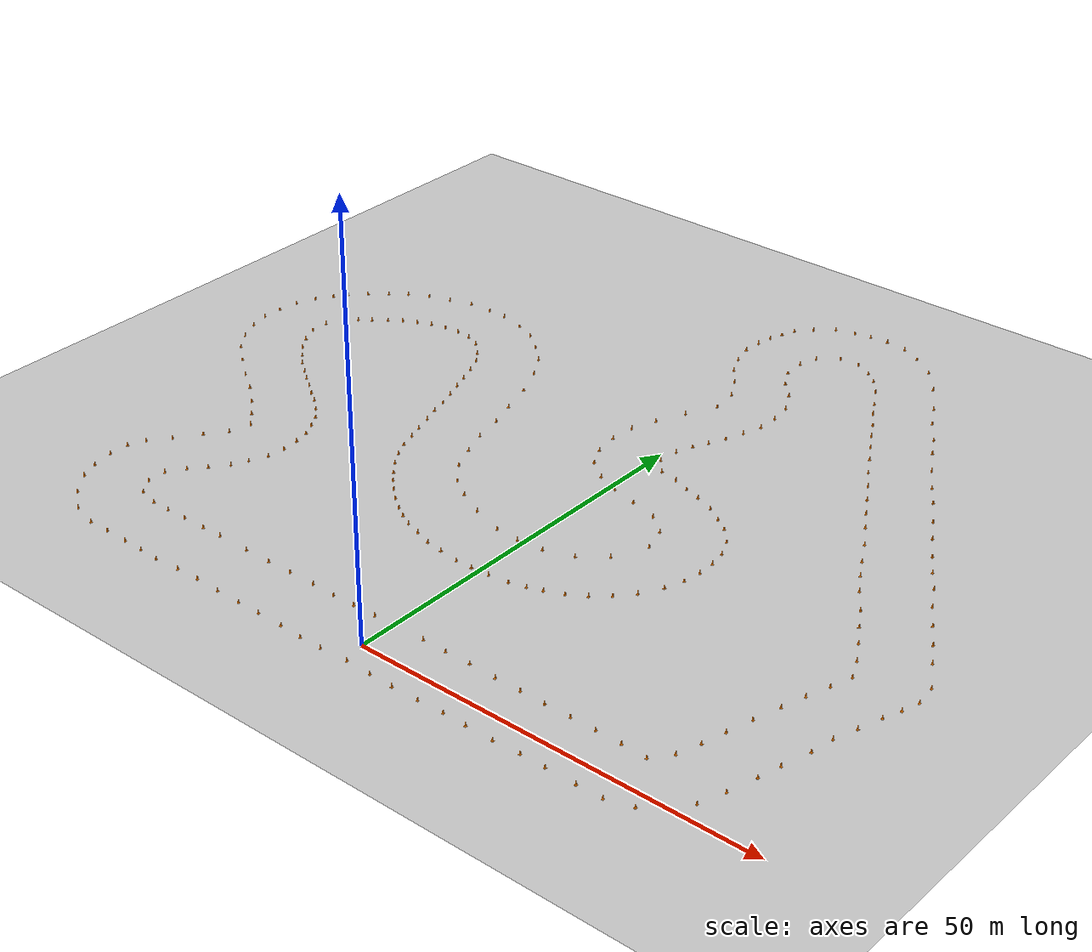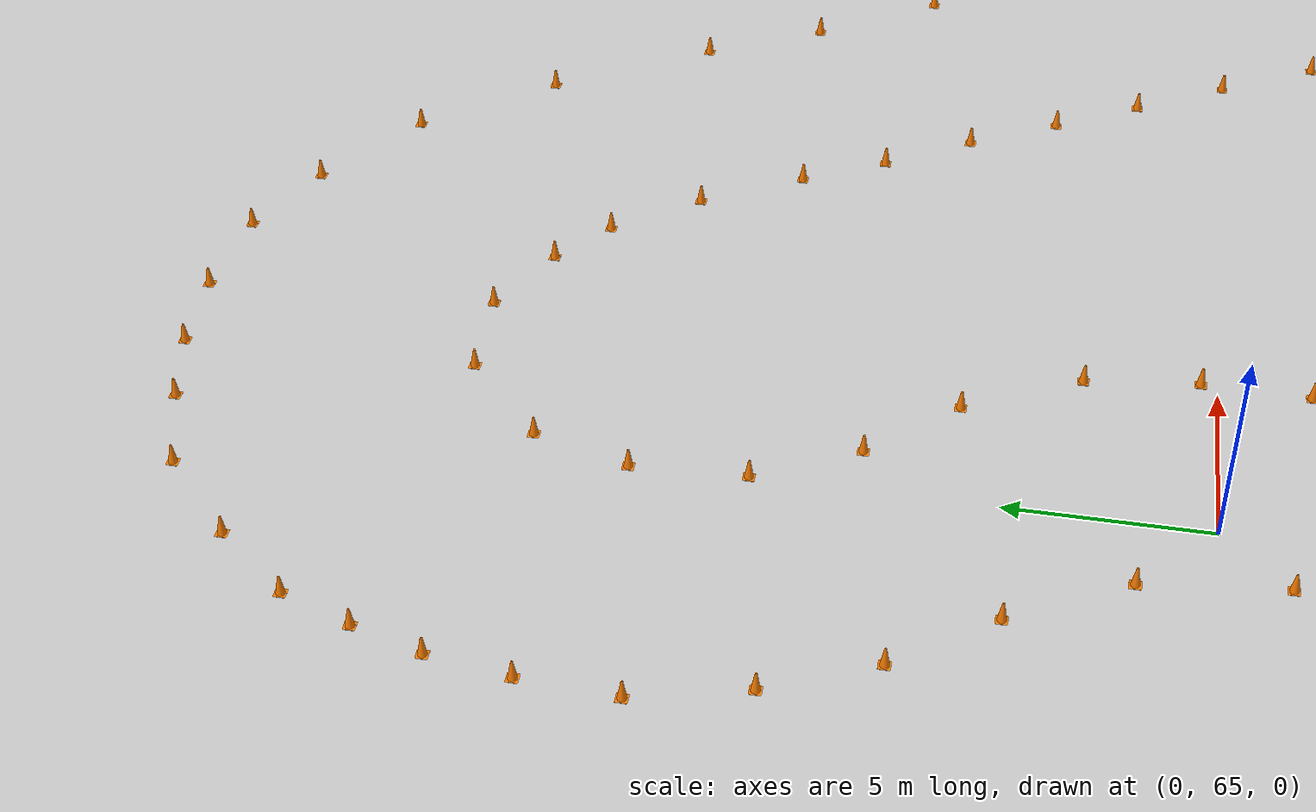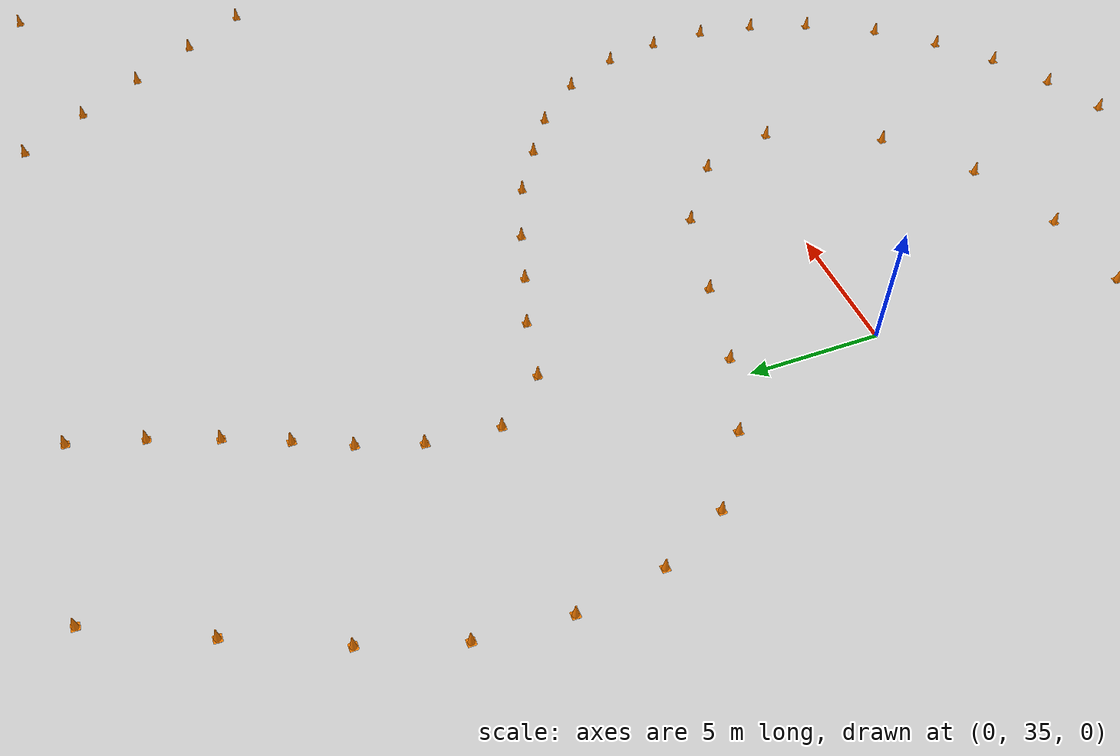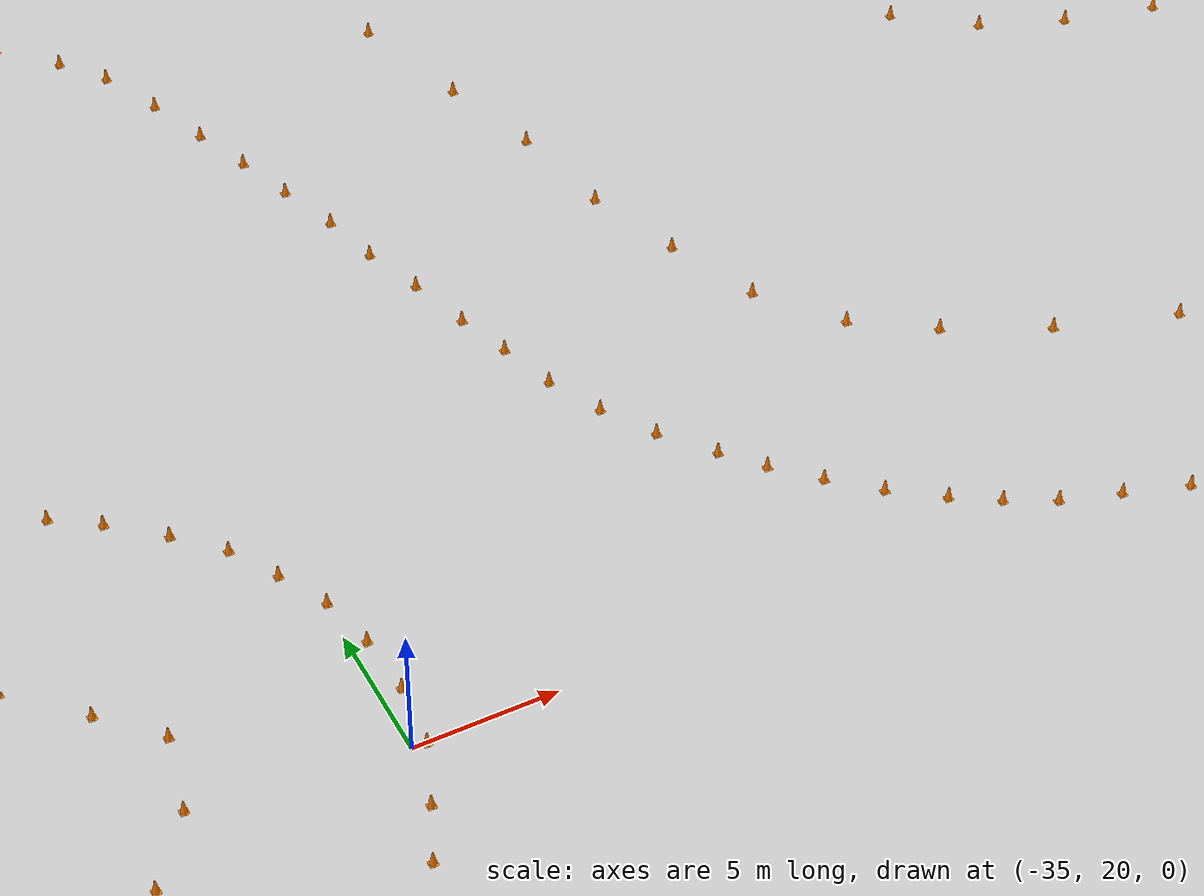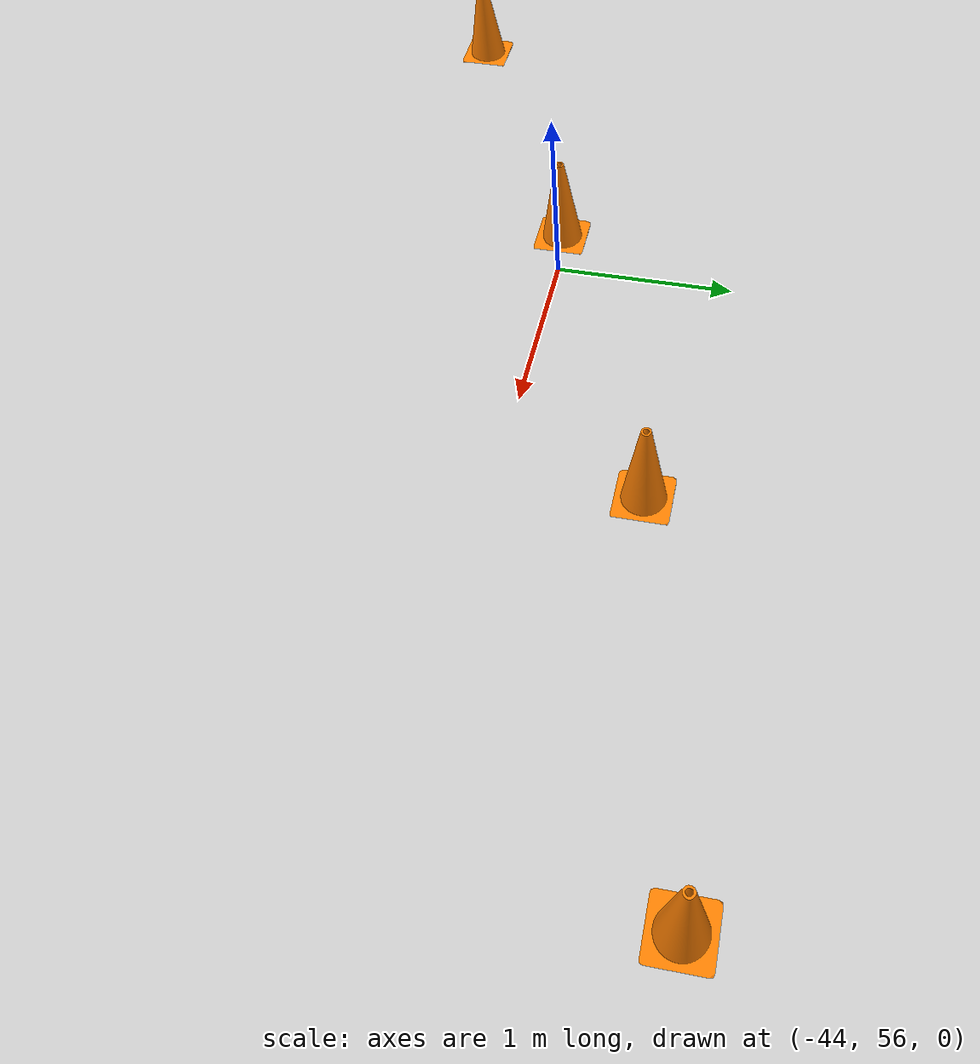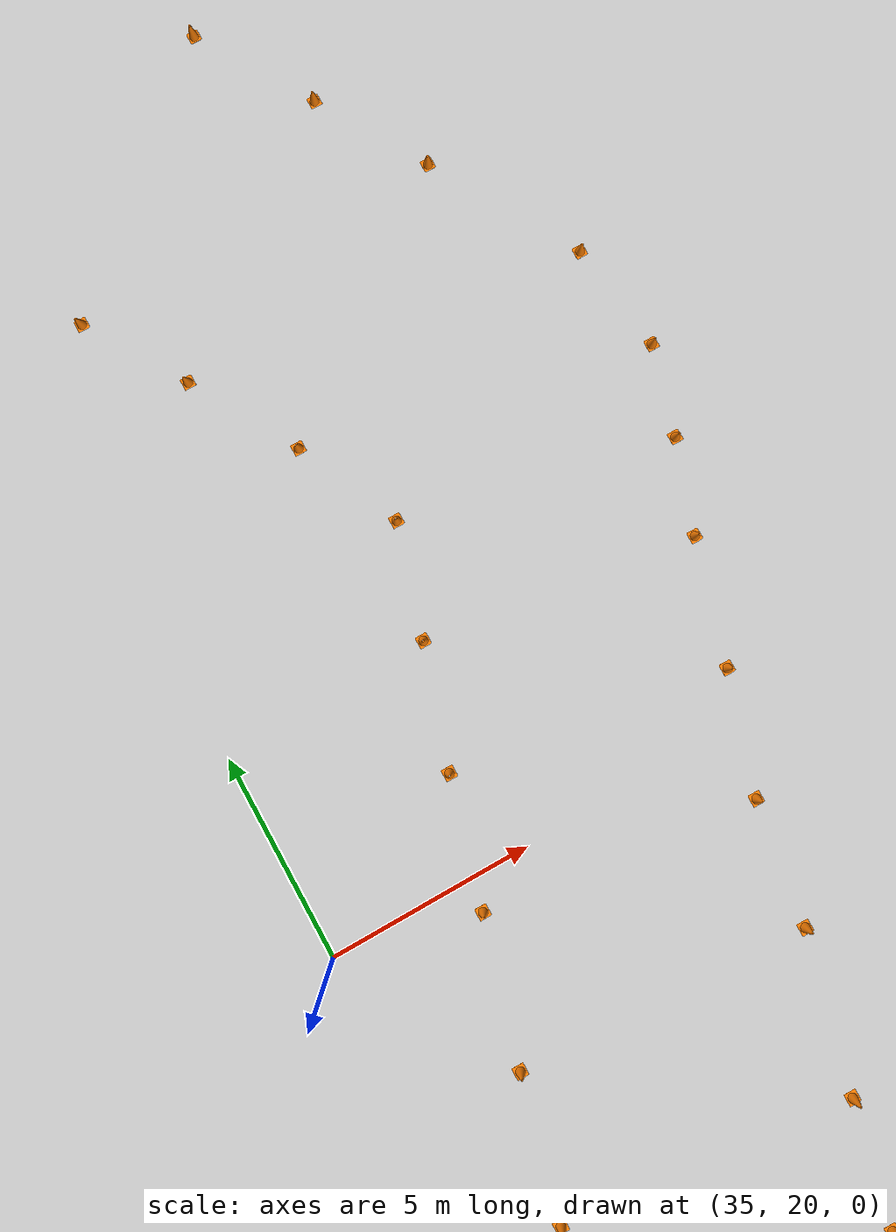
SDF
<sdf version="1.7">
 <world name="IARRC Urban">
  <scene>
   <ambient>1 1 1 1</ambient>
   <background>0.7 0.7 0.7 1</background>
   <shadows>1</shadows>
   <grid>0</grid>
   <origin_visual>0</origin_visual>
  </scene>
  <light name="sun" type="directional">
   <pose>0 0 10 0 -0 0</pose>
   <diffuse>0.8 0.8 0.8 1</diffuse>
   <specular>0.2 0.2 0.2 1</specular>
   <attenuation>
    <range>1000</range>
    <constant>0.9</constant>
    <linear>0.01</linear>
    <quadratic>0.001</quadratic>
   </attenuation>
   <direction>-0.5 0.1 -0.9</direction>
   <spot><inner_angle>0</inner_angle><outer_angle>0</outer_angle><falloff>0</falloff></spot>
  </light>
  <model name="EVGPTrack3">
   <static>1</static>
   <link name="link">
    <collision name="collision">
     <geometry><plane><normal>0 0 1</normal><size>150 150</size></plane></geometry>
     <surface><friction><ode><mu>100</mu><mu2>50</mu2></ode></friction></surface>
    </collision>
    <visual name="visual">
     <geometry><plane><normal>0 0 1</normal><size>150 150</size></plane></geometry>
     <material>
      <script><uri>model://../materials/evgptrack3.material</uri><name>Gazebo/evgptrack3</name></script>
     </material>
    </visual>
   </link>
   <pose>0 31 0 0 -0 0</pose>
  </model>
  <gravity>0 0 -9.8</gravity>
  <magnetic_field>6e-06 2.3e-05 -4.2e-05</magnetic_field>
  <atmosphere type="adiabatic"/>
  <physics type="ode">
   <max_step_size>0.001</max_step_size>
   <real_time_factor>1</real_time_factor>
   <real_time_update_rate>1000</real_time_update_rate>
  </physics>
  <spherical_coordinates>
   <surface_model>EARTH_WGS84</surface_model>
   <latitude_deg>0</latitude_deg>
   <longitude_deg>0</longitude_deg>
   <elevation>0</elevation>
   <heading_deg>0</heading_deg>
  </spherical_coordinates>
  <model name="TallerCone_clone">
   <link name="link_0">
    <inertial>
     <mass>0.068</mass>
     <inertia>
      <ixx>0.000367263</ixx>
      <ixy>0</ixy>
      <ixz>0</ixz>
      <iyy>0.000367263</iyy>
      <iyz>0</iyz>
      <izz>0.000165927</izz>
     </inertia>
    </inertial>
    <visual name="visual">
     <geometry><mesh><uri>model://TallerCone/traffic_cone.stl</uri><scale>0.01 0.01 0.01</scale></mesh></geometry>
     <material>
      <lighting>1</lighting>
      <script><uri>file://media/materials/scripts/gazebo.material</uri><name>Gazebo/Grey</name></script>
      <ambient>0.4 0.2 0 1</ambient>
      <diffuse>1 0.5 0 1</diffuse>
      <specular>0.01 0.01 0.01 1</specular>
      <emissive>0 0 0 1</emissive>
     </material>
    </visual>
    <collision name="collision">
     <geometry><mesh><uri>model://TallerCone/traffic_cone.stl</uri></mesh></geometry>
     <surface>
      <friction>
       <ode><mu>1</mu><mu2>1</mu2><fdir1>0 0 0</fdir1><slip1>0</slip1><slip2>0</slip2></ode>
       <torsional>
        <coefficient>1</coefficient>
        <patch_radius>0</patch_radius>
        <surface_radius>0</surface_radius>
        <use_patch_radius>1</use_patch_radius>
        <ode><slip>0</slip></ode>
       </torsional>
      </friction>
      <bounce><restitution_coefficient>0</restitution_coefficient><threshold>1e+06</threshold></bounce>
      <contact>
       <collide_without_contact>0</collide_without_contact>
       <collide_without_contact_bitmask>1</collide_without_contact_bitmask>
       <collide_bitmask>1</collide_bitmask>
       <ode>
        <soft_cfm>0</soft_cfm>
        <soft_erp>0.2</soft_erp>
        <kp>1e+13</kp>
        <kd>1</kd>
        <max_vel>0.01</max_vel>
        <min_depth>0</min_depth>
       </ode>
       <bullet>
        <split_impulse>1</split_impulse>
        <split_impulse_penetration_threshold>-0.01</split_impulse_penetration_threshold>
        <soft_cfm>0</soft_cfm>
        <soft_erp>0.2</soft_erp>
        <kp>1e+13</kp>
        <kd>1</kd>
       </bullet>
      </contact>
     </surface>
    </collision>
   </link>
   <static>1</static>
   <pose>4.0939 4.8029 -0.034283 0 -0 0</pose>
  </model>
  <model name="TallerCone_clone_0">
   <link name="link_0">
    <inertial>
     <mass>0.068</mass>
     <inertia>
      <ixx>0.000367263</ixx>
      <ixy>0</ixy>
      <ixz>0</ixz>
      <iyy>0.000367263</iyy>
      <iyz>0</iyz>
      <izz>0.000165927</izz>
     </inertia>
    </inertial>
    <visual name="visual">
     <geometry><mesh><uri>model://TallerCone/traffic_cone.stl</uri><scale>0.01 0.01 0.01</scale></mesh></geometry>
     <material>
      <lighting>1</lighting>
      <script><uri>file://media/materials/scripts/gazebo.material</uri><name>Gazebo/Grey</name></script>
      <ambient>0.4 0.2 0 1</ambient>
      <diffuse>1 0.5 0 1</diffuse>
      <specular>0.01 0.01 0.01 1</specular>
      <emissive>0 0 0 1</emissive>
     </material>
    </visual>
    <collision name="collision">
     <geometry><mesh><uri>model://TallerCone/traffic_cone.stl</uri></mesh></geometry>
     <surface>
      <friction>
       <ode><mu>1</mu><mu2>1</mu2><fdir1>0 0 0</fdir1><slip1>0</slip1><slip2>0</slip2></ode>
       <torsional>
        <coefficient>1</coefficient>
        <patch_radius>0</patch_radius>
        <surface_radius>0</surface_radius>
        <use_patch_radius>1</use_patch_radius>
        <ode><slip>0</slip></ode>
       </torsional>
      </friction>
      <bounce><restitution_coefficient>0</restitution_coefficient><threshold>1e+06</threshold></bounce>
      <contact>
       <collide_without_contact>0</collide_without_contact>
       <collide_without_contact_bitmask>1</collide_without_contact_bitmask>
       <collide_bitmask>1</collide_bitmask>
       <ode>
        <soft_cfm>0</soft_cfm>
        <soft_erp>0.2</soft_erp>
        <kp>1e+13</kp>
        <kd>1</kd>
        <max_vel>0.01</max_vel>
        <min_depth>0</min_depth>
       </ode>
       <bullet>
        <split_impulse>1</split_impulse>
        <split_impulse_penetration_threshold>-0.01</split_impulse_penetration_threshold>
        <soft_cfm>0</soft_cfm>
        <soft_erp>0.2</soft_erp>
        <kp>1e+13</kp>
        <kd>1</kd>
       </bullet>
      </contact>
     </surface>
    </collision>
   </link>
   <static>1</static>
   <pose>7.2097 4.77103 -0.034283 0 -0 0</pose>
  </model>
  <model name="TallerCone_clone_1">
   <link name="link_0">
    <inertial>
     <mass>0.068</mass>
     <inertia>
      <ixx>0.000367263</ixx>
      <ixy>0</ixy>
      <ixz>0</ixz>
      <iyy>0.000367263</iyy>
      <iyz>0</iyz>
      <izz>0.000165927</izz>
     </inertia>
    </inertial>
    <visual name="visual">
     <geometry><mesh><uri>model://TallerCone/traffic_cone.stl</uri><scale>0.01 0.01 0.01</scale></mesh></geometry>
     <material>
      <lighting>1</lighting>
      <script><uri>file://media/materials/scripts/gazebo.material</uri><name>Gazebo/Grey</name></script>
      <ambient>0.4 0.2 0 1</ambient>
      <diffuse>1 0.5 0 1</diffuse>
      <specular>0.01 0.01 0.01 1</specular>
      <emissive>0 0 0 1</emissive>
     </material>
    </visual>
    <collision name="collision">
     <geometry><mesh><uri>model://TallerCone/traffic_cone.stl</uri></mesh></geometry>
     <surface>
      <friction>
       <ode><mu>1</mu><mu2>1</mu2><fdir1>0 0 0</fdir1><slip1>0</slip1><slip2>0</slip2></ode>
       <torsional>
        <coefficient>1</coefficient>
        <patch_radius>0</patch_radius>
        <surface_radius>0</surface_radius>
        <use_patch_radius>1</use_patch_radius>
        <ode><slip>0</slip></ode>
       </torsional>
      </friction>
      <bounce><restitution_coefficient>0</restitution_coefficient><threshold>1e+06</threshold></bounce>
      <contact>
       <collide_without_contact>0</collide_without_contact>
       <collide_without_contact_bitmask>1</collide_without_contact_bitmask>
       <collide_bitmask>1</collide_bitmask>
       <ode>
        <soft_cfm>0</soft_cfm>
        <soft_erp>0.2</soft_erp>
        <kp>1e+13</kp>
        <kd>1</kd>
        <max_vel>0.01</max_vel>
        <min_depth>0</min_depth>
       </ode>
       <bullet>
        <split_impulse>1</split_impulse>
        <split_impulse_penetration_threshold>-0.01</split_impulse_penetration_threshold>
        <soft_cfm>0</soft_cfm>
        <soft_erp>0.2</soft_erp>
        <kp>1e+13</kp>
        <kd>1</kd>
       </bullet>
      </contact>
     </surface>
    </collision>
   </link>
   <static>1</static>
   <pose>10.4678 4.80851 -0.034283 0 -0 0</pose>
  </model>
  <model name="TallerCone_clone_2">
   <link name="link_0">
    <inertial>
     <mass>0.068</mass>
     <inertia>
      <ixx>0.000367263</ixx>
      <ixy>0</ixy>
      <ixz>0</ixz>
      <iyy>0.000367263</iyy>
      <iyz>0</iyz>
      <izz>0.000165927</izz>
     </inertia>
    </inertial>
    <visual name="visual">
     <geometry><mesh><uri>model://TallerCone/traffic_cone.stl</uri><scale>0.01 0.01 0.01</scale></mesh></geometry>
     <material>
      <lighting>1</lighting>
      <script><uri>file://media/materials/scripts/gazebo.material</uri><name>Gazebo/Grey</name></script>
      <ambient>0.4 0.2 0 1</ambient>
      <diffuse>1 0.5 0 1</diffuse>
      <specular>0.01 0.01 0.01 1</specular>
      <emissive>0 0 0 1</emissive>
     </material>
    </visual>
    <collision name="collision">
     <geometry><mesh><uri>model://TallerCone/traffic_cone.stl</uri></mesh></geometry>
     <surface>
      <friction>
       <ode><mu>1</mu><mu2>1</mu2><fdir1>0 0 0</fdir1><slip1>0</slip1><slip2>0</slip2></ode>
       <torsional>
        <coefficient>1</coefficient>
        <patch_radius>0</patch_radius>
        <surface_radius>0</surface_radius>
        <use_patch_radius>1</use_patch_radius>
        <ode><slip>0</slip></ode>
       </torsional>
      </friction>
      <bounce><restitution_coefficient>0</restitution_coefficient><threshold>1e+06</threshold></bounce>
      <contact>
       <collide_without_contact>0</collide_without_contact>
       <collide_without_contact_bitmask>1</collide_without_contact_bitmask>
       <collide_bitmask>1</collide_bitmask>
       <ode>
        <soft_cfm>0</soft_cfm>
        <soft_erp>0.2</soft_erp>
        <kp>1e+13</kp>
        <kd>1</kd>
        <max_vel>0.01</max_vel>
        <min_depth>0</min_depth>
       </ode>
       <bullet>
        <split_impulse>1</split_impulse>
        <split_impulse_penetration_threshold>-0.01</split_impulse_penetration_threshold>
        <soft_cfm>0</soft_cfm>
        <soft_erp>0.2</soft_erp>
        <kp>1e+13</kp>
        <kd>1</kd>
       </bullet>
      </contact>
     </surface>
    </collision>
   </link>
   <static>1</static>
   <pose>13.9726 4.69256 -0.034283 0 -0 0</pose>
  </model>
  <model name="TallerCone_clone_3">
   <link name="link_0">
    <inertial>
     <mass>0.068</mass>
     <inertia>
      <ixx>0.000367263</ixx>
      <ixy>0</ixy>
      <ixz>0</ixz>
      <iyy>0.000367263</iyy>
      <iyz>0</iyz>
      <izz>0.000165927</izz>
     </inertia>
    </inertial>
    <visual name="visual">
     <geometry><mesh><uri>model://TallerCone/traffic_cone.stl</uri><scale>0.01 0.01 0.01</scale></mesh></geometry>
     <material>
      <lighting>1</lighting>
      <script><uri>file://media/materials/scripts/gazebo.material</uri><name>Gazebo/Grey</name></script>
      <ambient>0.4 0.2 0 1</ambient>
      <diffuse>1 0.5 0 1</diffuse>
      <specular>0.01 0.01 0.01 1</specular>
      <emissive>0 0 0 1</emissive>
     </material>
    </visual>
    <collision name="collision">
     <geometry><mesh><uri>model://TallerCone/traffic_cone.stl</uri></mesh></geometry>
     <surface>
      <friction>
       <ode><mu>1</mu><mu2>1</mu2><fdir1>0 0 0</fdir1><slip1>0</slip1><slip2>0</slip2></ode>
       <torsional>
        <coefficient>1</coefficient>
        <patch_radius>0</patch_radius>
        <surface_radius>0</surface_radius>
        <use_patch_radius>1</use_patch_radius>
        <ode><slip>0</slip></ode>
       </torsional>
      </friction>
      <bounce><restitution_coefficient>0</restitution_coefficient><threshold>1e+06</threshold></bounce>
      <contact>
       <collide_without_contact>0</collide_without_contact>
       <collide_without_contact_bitmask>1</collide_without_contact_bitmask>
       <collide_bitmask>1</collide_bitmask>
       <ode>
        <soft_cfm>0</soft_cfm>
        <soft_erp>0.2</soft_erp>
        <kp>1e+13</kp>
        <kd>1</kd>
        <max_vel>0.01</max_vel>
        <min_depth>0</min_depth>
       </ode>
       <bullet>
        <split_impulse>1</split_impulse>
        <split_impulse_penetration_threshold>-0.01</split_impulse_penetration_threshold>
        <soft_cfm>0</soft_cfm>
        <soft_erp>0.2</soft_erp>
        <kp>1e+13</kp>
        <kd>1</kd>
       </bullet>
      </contact>
     </surface>
    </collision>
   </link>
   <static>1</static>
   <pose>17.2558 4.69931 -0.034283 0 -0 0</pose>
  </model>
  <model name="TallerCone_clone_4">
   <link name="link_0">
    <inertial>
     <mass>0.068</mass>
     <inertia>
      <ixx>0.000367263</ixx>
      <ixy>0</ixy>
      <ixz>0</ixz>
      <iyy>0.000367263</iyy>
      <iyz>0</iyz>
      <izz>0.000165927</izz>
     </inertia>
    </inertial>
    <visual name="visual">
     <geometry><mesh><uri>model://TallerCone/traffic_cone.stl</uri><scale>0.01 0.01 0.01</scale></mesh></geometry>
     <material>
      <lighting>1</lighting>
      <script><uri>file://media/materials/scripts/gazebo.material</uri><name>Gazebo/Grey</name></script>
      <ambient>0.4 0.2 0 1</ambient>
      <diffuse>1 0.5 0 1</diffuse>
      <specular>0.01 0.01 0.01 1</specular>
      <emissive>0 0 0 1</emissive>
     </material>
    </visual>
    <collision name="collision">
     <geometry><mesh><uri>model://TallerCone/traffic_cone.stl</uri></mesh></geometry>
     <surface>
      <friction>
       <ode><mu>1</mu><mu2>1</mu2><fdir1>0 0 0</fdir1><slip1>0</slip1><slip2>0</slip2></ode>
       <torsional>
        <coefficient>1</coefficient>
        <patch_radius>0</patch_radius>
        <surface_radius>0</surface_radius>
        <use_patch_radius>1</use_patch_radius>
        <ode><slip>0</slip></ode>
       </torsional>
      </friction>
      <bounce><restitution_coefficient>0</restitution_coefficient><threshold>1e+06</threshold></bounce>
      <contact>
       <collide_without_contact>0</collide_without_contact>
       <collide_without_contact_bitmask>1</collide_without_contact_bitmask>
       <collide_bitmask>1</collide_bitmask>
       <ode>
        <soft_cfm>0</soft_cfm>
        <soft_erp>0.2</soft_erp>
        <kp>1e+13</kp>
        <kd>1</kd>
        <max_vel>0.01</max_vel>
        <min_depth>0</min_depth>
       </ode>
       <bullet>
        <split_impulse>1</split_impulse>
        <split_impulse_penetration_threshold>-0.01</split_impulse_penetration_threshold>
        <soft_cfm>0</soft_cfm>
        <soft_erp>0.2</soft_erp>
        <kp>1e+13</kp>
        <kd>1</kd>
       </bullet>
      </contact>
     </surface>
    </collision>
   </link>
   <static>1</static>
   <pose>20.4342 4.63136 -0.034283 0 -0 0</pose>
  </model>
  <model name="TallerCone_clone_5">
   <link name="link_0">
    <inertial>
     <mass>0.068</mass>
     <inertia>
      <ixx>0.000367263</ixx>
      <ixy>0</ixy>
      <ixz>0</ixz>
      <iyy>0.000367263</iyy>
      <iyz>0</iyz>
      <izz>0.000165927</izz>
     </inertia>
    </inertial>
    <visual name="visual">
     <geometry><mesh><uri>model://TallerCone/traffic_cone.stl</uri><scale>0.01 0.01 0.01</scale></mesh></geometry>
     <material>
      <lighting>1</lighting>
      <script><uri>file://media/materials/scripts/gazebo.material</uri><name>Gazebo/Grey</name></script>
      <ambient>0.4 0.2 0 1</ambient>
      <diffuse>1 0.5 0 1</diffuse>
      <specular>0.01 0.01 0.01 1</specular>
      <emissive>0 0 0 1</emissive>
     </material>
    </visual>
    <collision name="collision">
     <geometry><mesh><uri>model://TallerCone/traffic_cone.stl</uri></mesh></geometry>
     <surface>
      <friction>
       <ode><mu>1</mu><mu2>1</mu2><fdir1>0 0 0</fdir1><slip1>0</slip1><slip2>0</slip2></ode>
       <torsional>
        <coefficient>1</coefficient>
        <patch_radius>0</patch_radius>
        <surface_radius>0</surface_radius>
        <use_patch_radius>1</use_patch_radius>
        <ode><slip>0</slip></ode>
       </torsional>
      </friction>
      <bounce><restitution_coefficient>0</restitution_coefficient><threshold>1e+06</threshold></bounce>
      <contact>
       <collide_without_contact>0</collide_without_contact>
       <collide_without_contact_bitmask>1</collide_without_contact_bitmask>
       <collide_bitmask>1</collide_bitmask>
       <ode>
        <soft_cfm>0</soft_cfm>
        <soft_erp>0.2</soft_erp>
        <kp>1e+13</kp>
        <kd>1</kd>
        <max_vel>0.01</max_vel>
        <min_depth>0</min_depth>
       </ode>
       <bullet>
        <split_impulse>1</split_impulse>
        <split_impulse_penetration_threshold>-0.01</split_impulse_penetration_threshold>
        <soft_cfm>0</soft_cfm>
        <soft_erp>0.2</soft_erp>
        <kp>1e+13</kp>
        <kd>1</kd>
       </bullet>
      </contact>
     </surface>
    </collision>
   </link>
   <static>1</static>
   <pose>23.7047 4.67013 -0.034283 0 -0 0</pose>
  </model>
  <model name="TallerCone_clone_6">
   <link name="link_0">
    <inertial>
     <mass>0.068</mass>
     <inertia>
      <ixx>0.000367263</ixx>
      <ixy>0</ixy>
      <ixz>0</ixz>
      <iyy>0.000367263</iyy>
      <iyz>0</iyz>
      <izz>0.000165927</izz>
     </inertia>
    </inertial>
    <visual name="visual">
     <geometry><mesh><uri>model://TallerCone/traffic_cone.stl</uri><scale>0.01 0.01 0.01</scale></mesh></geometry>
     <material>
      <lighting>1</lighting>
      <script><uri>file://media/materials/scripts/gazebo.material</uri><name>Gazebo/Grey</name></script>
      <ambient>0.4 0.2 0 1</ambient>
      <diffuse>1 0.5 0 1</diffuse>
      <specular>0.01 0.01 0.01 1</specular>
      <emissive>0 0 0 1</emissive>
     </material>
    </visual>
    <collision name="collision">
     <geometry><mesh><uri>model://TallerCone/traffic_cone.stl</uri></mesh></geometry>
     <surface>
      <friction>
       <ode><mu>1</mu><mu2>1</mu2><fdir1>0 0 0</fdir1><slip1>0</slip1><slip2>0</slip2></ode>
       <torsional>
        <coefficient>1</coefficient>
        <patch_radius>0</patch_radius>
        <surface_radius>0</surface_radius>
        <use_patch_radius>1</use_patch_radius>
        <ode><slip>0</slip></ode>
       </torsional>
      </friction>
      <bounce><restitution_coefficient>0</restitution_coefficient><threshold>1e+06</threshold></bounce>
      <contact>
       <collide_without_contact>0</collide_without_contact>
       <collide_without_contact_bitmask>1</collide_without_contact_bitmask>
       <collide_bitmask>1</collide_bitmask>
       <ode>
        <soft_cfm>0</soft_cfm>
        <soft_erp>0.2</soft_erp>
        <kp>1e+13</kp>
        <kd>1</kd>
        <max_vel>0.01</max_vel>
        <min_depth>0</min_depth>
       </ode>
       <bullet>
        <split_impulse>1</split_impulse>
        <split_impulse_penetration_threshold>-0.01</split_impulse_penetration_threshold>
        <soft_cfm>0</soft_cfm>
        <soft_erp>0.2</soft_erp>
        <kp>1e+13</kp>
        <kd>1</kd>
       </bullet>
      </contact>
     </surface>
    </collision>
   </link>
   <static>1</static>
   <pose>26.889 4.64065 -0.034283 0 -0 0</pose>
  </model>
  <model name="TallerCone_clone_7">
   <link name="link_0">
    <inertial>
     <mass>0.068</mass>
     <inertia>
      <ixx>0.000367263</ixx>
      <ixy>0</ixy>
      <ixz>0</ixz>
      <iyy>0.000367263</iyy>
      <iyz>0</iyz>
      <izz>0.000165927</izz>
     </inertia>
    </inertial>
    <visual name="visual">
     <geometry><mesh><uri>model://TallerCone/traffic_cone.stl</uri><scale>0.01 0.01 0.01</scale></mesh></geometry>
     <material>
      <lighting>1</lighting>
      <script><uri>file://media/materials/scripts/gazebo.material</uri><name>Gazebo/Grey</name></script>
      <ambient>0.4 0.2 0 1</ambient>
      <diffuse>1 0.5 0 1</diffuse>
      <specular>0.01 0.01 0.01 1</specular>
      <emissive>0 0 0 1</emissive>
     </material>
    </visual>
    <collision name="collision">
     <geometry><mesh><uri>model://TallerCone/traffic_cone.stl</uri></mesh></geometry>
     <surface>
      <friction>
       <ode><mu>1</mu><mu2>1</mu2><fdir1>0 0 0</fdir1><slip1>0</slip1><slip2>0</slip2></ode>
       <torsional>
        <coefficient>1</coefficient>
        <patch_radius>0</patch_radius>
        <surface_radius>0</surface_radius>
        <use_patch_radius>1</use_patch_radius>
        <ode><slip>0</slip></ode>
       </torsional>
      </friction>
      <bounce><restitution_coefficient>0</restitution_coefficient><threshold>1e+06</threshold></bounce>
      <contact>
       <collide_without_contact>0</collide_without_contact>
       <collide_without_contact_bitmask>1</collide_without_contact_bitmask>
       <collide_bitmask>1</collide_bitmask>
       <ode>
        <soft_cfm>0</soft_cfm>
        <soft_erp>0.2</soft_erp>
        <kp>1e+13</kp>
        <kd>1</kd>
        <max_vel>0.01</max_vel>
        <min_depth>0</min_depth>
       </ode>
       <bullet>
        <split_impulse>1</split_impulse>
        <split_impulse_penetration_threshold>-0.01</split_impulse_penetration_threshold>
        <soft_cfm>0</soft_cfm>
        <soft_erp>0.2</soft_erp>
        <kp>1e+13</kp>
        <kd>1</kd>
       </bullet>
      </contact>
     </surface>
    </collision>
   </link>
   <static>1</static>
   <pose>30.0711 4.61063 -0.034283 0 -0 0</pose>
  </model>
  <model name="TallerCone_clone_8">
   <link name="link_0">
    <inertial>
     <mass>0.068</mass>
     <inertia>
      <ixx>0.000367263</ixx>
      <ixy>0</ixy>
      <ixz>0</ixz>
      <iyy>0.000367263</iyy>
      <iyz>0</iyz>
      <izz>0.000165927</izz>
     </inertia>
    </inertial>
    <visual name="visual">
     <geometry><mesh><uri>model://TallerCone/traffic_cone.stl</uri><scale>0.01 0.01 0.01</scale></mesh></geometry>
     <material>
      <lighting>1</lighting>
      <script><uri>file://media/materials/scripts/gazebo.material</uri><name>Gazebo/Grey</name></script>
      <ambient>0.4 0.2 0 1</ambient>
      <diffuse>1 0.5 0 1</diffuse>
      <specular>0.01 0.01 0.01 1</specular>
      <emissive>0 0 0 1</emissive>
     </material>
    </visual>
    <collision name="collision">
     <geometry><mesh><uri>model://TallerCone/traffic_cone.stl</uri></mesh></geometry>
     <surface>
      <friction>
       <ode><mu>1</mu><mu2>1</mu2><fdir1>0 0 0</fdir1><slip1>0</slip1><slip2>0</slip2></ode>
       <torsional>
        <coefficient>1</coefficient>
        <patch_radius>0</patch_radius>
        <surface_radius>0</surface_radius>
        <use_patch_radius>1</use_patch_radius>
        <ode><slip>0</slip></ode>
       </torsional>
      </friction>
      <bounce><restitution_coefficient>0</restitution_coefficient><threshold>1e+06</threshold></bounce>
      <contact>
       <collide_without_contact>0</collide_without_contact>
       <collide_without_contact_bitmask>1</collide_without_contact_bitmask>
       <collide_bitmask>1</collide_bitmask>
       <ode>
        <soft_cfm>0</soft_cfm>
        <soft_erp>0.2</soft_erp>
        <kp>1e+13</kp>
        <kd>1</kd>
        <max_vel>0.01</max_vel>
        <min_depth>0</min_depth>
       </ode>
       <bullet>
        <split_impulse>1</split_impulse>
        <split_impulse_penetration_threshold>-0.01</split_impulse_penetration_threshold>
        <soft_cfm>0</soft_cfm>
        <soft_erp>0.2</soft_erp>
        <kp>1e+13</kp>
        <kd>1</kd>
       </bullet>
      </contact>
     </surface>
    </collision>
   </link>
   <static>1</static>
   <pose>33.2077 4.5086 -0.034283 0 -0 0</pose>
  </model>
  <model name="TallerCone_clone_9">
   <link name="link_0">
    <inertial>
     <mass>0.068</mass>
     <inertia>
      <ixx>0.000367263</ixx>
      <ixy>0</ixy>
      <ixz>0</ixz>
      <iyy>0.000367263</iyy>
      <iyz>0</iyz>
      <izz>0.000165927</izz>
     </inertia>
    </inertial>
    <visual name="visual">
     <geometry><mesh><uri>model://TallerCone/traffic_cone.stl</uri><scale>0.01 0.01 0.01</scale></mesh></geometry>
     <material>
      <lighting>1</lighting>
      <script><uri>file://media/materials/scripts/gazebo.material</uri><name>Gazebo/Grey</name></script>
      <ambient>0.4 0.2 0 1</ambient>
      <diffuse>1 0.5 0 1</diffuse>
      <specular>0.01 0.01 0.01 1</specular>
      <emissive>0 0 0 1</emissive>
     </material>
    </visual>
    <collision name="collision">
     <geometry><mesh><uri>model://TallerCone/traffic_cone.stl</uri></mesh></geometry>
     <surface>
      <friction>
       <ode><mu>1</mu><mu2>1</mu2><fdir1>0 0 0</fdir1><slip1>0</slip1><slip2>0</slip2></ode>
       <torsional>
        <coefficient>1</coefficient>
        <patch_radius>0</patch_radius>
        <surface_radius>0</surface_radius>
        <use_patch_radius>1</use_patch_radius>
        <ode><slip>0</slip></ode>
       </torsional>
      </friction>
      <bounce><restitution_coefficient>0</restitution_coefficient><threshold>1e+06</threshold></bounce>
      <contact>
       <collide_without_contact>0</collide_without_contact>
       <collide_without_contact_bitmask>1</collide_without_contact_bitmask>
       <collide_bitmask>1</collide_bitmask>
       <ode>
        <soft_cfm>0</soft_cfm>
        <soft_erp>0.2</soft_erp>
        <kp>1e+13</kp>
        <kd>1</kd>
        <max_vel>0.01</max_vel>
        <min_depth>0</min_depth>
       </ode>
       <bullet>
        <split_impulse>1</split_impulse>
        <split_impulse_penetration_threshold>-0.01</split_impulse_penetration_threshold>
        <soft_cfm>0</soft_cfm>
        <soft_erp>0.2</soft_erp>
        <kp>1e+13</kp>
        <kd>1</kd>
       </bullet>
      </contact>
     </surface>
    </collision>
   </link>
   <static>1</static>
   <pose>34.9729 6.73569 -0.034283 0 -0 0</pose>
  </model>
  <model name="TallerCone_clone_10">
   <link name="link_0">
    <inertial>
     <mass>0.068</mass>
     <inertia>
      <ixx>0.000367263</ixx>
      <ixy>0</ixy>
      <ixz>0</ixz>
      <iyy>0.000367263</iyy>
      <iyz>0</iyz>
      <izz>0.000165927</izz>
     </inertia>
    </inertial>
    <visual name="visual">
     <geometry><mesh><uri>model://TallerCone/traffic_cone.stl</uri><scale>0.01 0.01 0.01</scale></mesh></geometry>
     <material>
      <lighting>1</lighting>
      <script><uri>file://media/materials/scripts/gazebo.material</uri><name>Gazebo/Grey</name></script>
      <ambient>0.4 0.2 0 1</ambient>
      <diffuse>1 0.5 0 1</diffuse>
      <specular>0.01 0.01 0.01 1</specular>
      <emissive>0 0 0 1</emissive>
     </material>
    </visual>
    <collision name="collision">
     <geometry><mesh><uri>model://TallerCone/traffic_cone.stl</uri></mesh></geometry>
     <surface>
      <friction>
       <ode><mu>1</mu><mu2>1</mu2><fdir1>0 0 0</fdir1><slip1>0</slip1><slip2>0</slip2></ode>
       <torsional>
        <coefficient>1</coefficient>
        <patch_radius>0</patch_radius>
        <surface_radius>0</surface_radius>
        <use_patch_radius>1</use_patch_radius>
        <ode><slip>0</slip></ode>
       </torsional>
      </friction>
      <bounce><restitution_coefficient>0</restitution_coefficient><threshold>1e+06</threshold></bounce>
      <contact>
       <collide_without_contact>0</collide_without_contact>
       <collide_without_contact_bitmask>1</collide_without_contact_bitmask>
       <collide_bitmask>1</collide_bitmask>
       <ode>
        <soft_cfm>0</soft_cfm>
        <soft_erp>0.2</soft_erp>
        <kp>1e+13</kp>
        <kd>1</kd>
        <max_vel>0.01</max_vel>
        <min_depth>0</min_depth>
       </ode>
       <bullet>
        <split_impulse>1</split_impulse>
        <split_impulse_penetration_threshold>-0.01</split_impulse_penetration_threshold>
        <soft_cfm>0</soft_cfm>
        <soft_erp>0.2</soft_erp>
        <kp>1e+13</kp>
        <kd>1</kd>
       </bullet>
      </contact>
     </surface>
    </collision>
   </link>
   <static>1</static>
   <pose>35.8701 9.61775 -0.034283 0 -0 0</pose>
  </model>
  <model name="TallerCone_clone_11">
   <link name="link_0">
    <inertial>
     <mass>0.068</mass>
     <inertia>
      <ixx>0.000367263</ixx>
      <ixy>0</ixy>
      <ixz>0</ixz>
      <iyy>0.000367263</iyy>
      <iyz>0</iyz>
      <izz>0.000165927</izz>
     </inertia>
    </inertial>
    <visual name="visual">
     <geometry><mesh><uri>model://TallerCone/traffic_cone.stl</uri><scale>0.01 0.01 0.01</scale></mesh></geometry>
     <material>
      <lighting>1</lighting>
      <script><uri>file://media/materials/scripts/gazebo.material</uri><name>Gazebo/Grey</name></script>
      <ambient>0.4 0.2 0 1</ambient>
      <diffuse>1 0.5 0 1</diffuse>
      <specular>0.01 0.01 0.01 1</specular>
      <emissive>0 0 0 1</emissive>
     </material>
    </visual>
    <collision name="collision">
     <geometry><mesh><uri>model://TallerCone/traffic_cone.stl</uri></mesh></geometry>
     <surface>
      <friction>
       <ode><mu>1</mu><mu2>1</mu2><fdir1>0 0 0</fdir1><slip1>0</slip1><slip2>0</slip2></ode>
       <torsional>
        <coefficient>1</coefficient>
        <patch_radius>0</patch_radius>
        <surface_radius>0</surface_radius>
        <use_patch_radius>1</use_patch_radius>
        <ode><slip>0</slip></ode>
       </torsional>
      </friction>
      <bounce><restitution_coefficient>0</restitution_coefficient><threshold>1e+06</threshold></bounce>
      <contact>
       <collide_without_contact>0</collide_without_contact>
       <collide_without_contact_bitmask>1</collide_without_contact_bitmask>
       <collide_bitmask>1</collide_bitmask>
       <ode>
        <soft_cfm>0</soft_cfm>
        <soft_erp>0.2</soft_erp>
        <kp>1e+13</kp>
        <kd>1</kd>
        <max_vel>0.01</max_vel>
        <min_depth>0</min_depth>
       </ode>
       <bullet>
        <split_impulse>1</split_impulse>
        <split_impulse_penetration_threshold>-0.01</split_impulse_penetration_threshold>
        <soft_cfm>0</soft_cfm>
        <soft_erp>0.2</soft_erp>
        <kp>1e+13</kp>
        <kd>1</kd>
       </bullet>
      </contact>
     </surface>
    </collision>
   </link>
   <static>1</static>
   <pose>36.624 12.5971 -0.034283 0 -0 0</pose>
  </model>
  <model name="TallerCone_clone_12">
   <link name="link_0">
    <inertial>
     <mass>0.068</mass>
     <inertia>
      <ixx>0.000367263</ixx>
      <ixy>0</ixy>
      <ixz>0</ixz>
      <iyy>0.000367263</iyy>
      <iyz>0</iyz>
      <izz>0.000165927</izz>
     </inertia>
    </inertial>
    <visual name="visual">
     <geometry><mesh><uri>model://TallerCone/traffic_cone.stl</uri><scale>0.01 0.01 0.01</scale></mesh></geometry>
     <material>
      <lighting>1</lighting>
      <script><uri>file://media/materials/scripts/gazebo.material</uri><name>Gazebo/Grey</name></script>
      <ambient>0.4 0.2 0 1</ambient>
      <diffuse>1 0.5 0 1</diffuse>
      <specular>0.01 0.01 0.01 1</specular>
      <emissive>0 0 0 1</emissive>
     </material>
    </visual>
    <collision name="collision">
     <geometry><mesh><uri>model://TallerCone/traffic_cone.stl</uri></mesh></geometry>
     <surface>
      <friction>
       <ode><mu>1</mu><mu2>1</mu2><fdir1>0 0 0</fdir1><slip1>0</slip1><slip2>0</slip2></ode>
       <torsional>
        <coefficient>1</coefficient>
        <patch_radius>0</patch_radius>
        <surface_radius>0</surface_radius>
        <use_patch_radius>1</use_patch_radius>
        <ode><slip>0</slip></ode>
       </torsional>
      </friction>
      <bounce><restitution_coefficient>0</restitution_coefficient><threshold>1e+06</threshold></bounce>
      <contact>
       <collide_without_contact>0</collide_without_contact>
       <collide_without_contact_bitmask>1</collide_without_contact_bitmask>
       <collide_bitmask>1</collide_bitmask>
       <ode>
        <soft_cfm>0</soft_cfm>
        <soft_erp>0.2</soft_erp>
        <kp>1e+13</kp>
        <kd>1</kd>
        <max_vel>0.01</max_vel>
        <min_depth>0</min_depth>
       </ode>
       <bullet>
        <split_impulse>1</split_impulse>
        <split_impulse_penetration_threshold>-0.01</split_impulse_penetration_threshold>
        <soft_cfm>0</soft_cfm>
        <soft_erp>0.2</soft_erp>
        <kp>1e+13</kp>
        <kd>1</kd>
       </bullet>
      </contact>
     </surface>
    </collision>
   </link>
   <static>1</static>
   <pose>37.4487 15.8425 -0.034283 0 -0 0</pose>
  </model>
  <model name="TallerCone_clone_13">
   <link name="link_0">
    <inertial>
     <mass>0.068</mass>
     <inertia>
      <ixx>0.000367263</ixx>
      <ixy>0</ixy>
      <ixz>0</ixz>
      <iyy>0.000367263</iyy>
      <iyz>0</iyz>
      <izz>0.000165927</izz>
     </inertia>
    </inertial>
    <visual name="visual">
     <geometry><mesh><uri>model://TallerCone/traffic_cone.stl</uri><scale>0.01 0.01 0.01</scale></mesh></geometry>
     <material>
      <lighting>1</lighting>
      <script><uri>file://media/materials/scripts/gazebo.material</uri><name>Gazebo/Grey</name></script>
      <ambient>0.4 0.2 0 1</ambient>
      <diffuse>1 0.5 0 1</diffuse>
      <specular>0.01 0.01 0.01 1</specular>
      <emissive>0 0 0 1</emissive>
     </material>
    </visual>
    <collision name="collision">
     <geometry><mesh><uri>model://TallerCone/traffic_cone.stl</uri></mesh></geometry>
     <surface>
      <friction>
       <ode><mu>1</mu><mu2>1</mu2><fdir1>0 0 0</fdir1><slip1>0</slip1><slip2>0</slip2></ode>
       <torsional>
        <coefficient>1</coefficient>
        <patch_radius>0</patch_radius>
        <surface_radius>0</surface_radius>
        <use_patch_radius>1</use_patch_radius>
        <ode><slip>0</slip></ode>
       </torsional>
      </friction>
      <bounce><restitution_coefficient>0</restitution_coefficient><threshold>1e+06</threshold></bounce>
      <contact>
       <collide_without_contact>0</collide_without_contact>
       <collide_without_contact_bitmask>1</collide_without_contact_bitmask>
       <collide_bitmask>1</collide_bitmask>
       <ode>
        <soft_cfm>0</soft_cfm>
        <soft_erp>0.2</soft_erp>
        <kp>1e+13</kp>
        <kd>1</kd>
        <max_vel>0.01</max_vel>
        <min_depth>0</min_depth>
       </ode>
       <bullet>
        <split_impulse>1</split_impulse>
        <split_impulse_penetration_threshold>-0.01</split_impulse_penetration_threshold>
        <soft_cfm>0</soft_cfm>
        <soft_erp>0.2</soft_erp>
        <kp>1e+13</kp>
        <kd>1</kd>
       </bullet>
      </contact>
     </surface>
    </collision>
   </link>
   <static>1</static>
   <pose>38.4082 19.2292 -0.034283 0 -0 0</pose>
  </model>
  <model name="TallerCone_clone_14">
   <link name="link_0">
    <inertial>
     <mass>0.068</mass>
     <inertia>
      <ixx>0.000367263</ixx>
      <ixy>0</ixy>
      <ixz>0</ixz>
      <iyy>0.000367263</iyy>
      <iyz>0</iyz>
      <izz>0.000165927</izz>
     </inertia>
    </inertial>
    <visual name="visual">
     <geometry><mesh><uri>model://TallerCone/traffic_cone.stl</uri><scale>0.01 0.01 0.01</scale></mesh></geometry>
     <material>
      <lighting>1</lighting>
      <script><uri>file://media/materials/scripts/gazebo.material</uri><name>Gazebo/Grey</name></script>
      <ambient>0.4 0.2 0 1</ambient>
      <diffuse>1 0.5 0 1</diffuse>
      <specular>0.01 0.01 0.01 1</specular>
      <emissive>0 0 0 1</emissive>
     </material>
    </visual>
    <collision name="collision">
     <geometry><mesh><uri>model://TallerCone/traffic_cone.stl</uri></mesh></geometry>
     <surface>
      <friction>
       <ode><mu>1</mu><mu2>1</mu2><fdir1>0 0 0</fdir1><slip1>0</slip1><slip2>0</slip2></ode>
       <torsional>
        <coefficient>1</coefficient>
        <patch_radius>0</patch_radius>
        <surface_radius>0</surface_radius>
        <use_patch_radius>1</use_patch_radius>
        <ode><slip>0</slip></ode>
       </torsional>
      </friction>
      <bounce><restitution_coefficient>0</restitution_coefficient><threshold>1e+06</threshold></bounce>
      <contact>
       <collide_without_contact>0</collide_without_contact>
       <collide_without_contact_bitmask>1</collide_without_contact_bitmask>
       <collide_bitmask>1</collide_bitmask>
       <ode>
        <soft_cfm>0</soft_cfm>
        <soft_erp>0.2</soft_erp>
        <kp>1e+13</kp>
        <kd>1</kd>
        <max_vel>0.01</max_vel>
        <min_depth>0</min_depth>
       </ode>
       <bullet>
        <split_impulse>1</split_impulse>
        <split_impulse_penetration_threshold>-0.01</split_impulse_penetration_threshold>
        <soft_cfm>0</soft_cfm>
        <soft_erp>0.2</soft_erp>
        <kp>1e+13</kp>
        <kd>1</kd>
       </bullet>
      </contact>
     </surface>
    </collision>
   </link>
   <static>1</static>
   <pose>39.2469 22.276 -0.034283 0 -0 0</pose>
  </model>
  <model name="TallerCone_clone_15">
   <link name="link_0">
    <inertial>
     <mass>0.068</mass>
     <inertia>
      <ixx>0.000367263</ixx>
      <ixy>0</ixy>
      <ixz>0</ixz>
      <iyy>0.000367263</iyy>
      <iyz>0</iyz>
      <izz>0.000165927</izz>
     </inertia>
    </inertial>
    <visual name="visual">
     <geometry><mesh><uri>model://TallerCone/traffic_cone.stl</uri><scale>0.01 0.01 0.01</scale></mesh></geometry>
     <material>
      <lighting>1</lighting>
      <script><uri>file://media/materials/scripts/gazebo.material</uri><name>Gazebo/Grey</name></script>
      <ambient>0.4 0.2 0 1</ambient>
      <diffuse>1 0.5 0 1</diffuse>
      <specular>0.01 0.01 0.01 1</specular>
      <emissive>0 0 0 1</emissive>
     </material>
    </visual>
    <collision name="collision">
     <geometry><mesh><uri>model://TallerCone/traffic_cone.stl</uri></mesh></geometry>
     <surface>
      <friction>
       <ode><mu>1</mu><mu2>1</mu2><fdir1>0 0 0</fdir1><slip1>0</slip1><slip2>0</slip2></ode>
       <torsional>
        <coefficient>1</coefficient>
        <patch_radius>0</patch_radius>
        <surface_radius>0</surface_radius>
        <use_patch_radius>1</use_patch_radius>
        <ode><slip>0</slip></ode>
       </torsional>
      </friction>
      <bounce><restitution_coefficient>0</restitution_coefficient><threshold>1e+06</threshold></bounce>
      <contact>
       <collide_without_contact>0</collide_without_contact>
       <collide_without_contact_bitmask>1</collide_without_contact_bitmask>
       <collide_bitmask>1</collide_bitmask>
       <ode>
        <soft_cfm>0</soft_cfm>
        <soft_erp>0.2</soft_erp>
        <kp>1e+13</kp>
        <kd>1</kd>
        <max_vel>0.01</max_vel>
        <min_depth>0</min_depth>
       </ode>
       <bullet>
        <split_impulse>1</split_impulse>
        <split_impulse_penetration_threshold>-0.01</split_impulse_penetration_threshold>
        <soft_cfm>0</soft_cfm>
        <soft_erp>0.2</soft_erp>
        <kp>1e+13</kp>
        <kd>1</kd>
       </bullet>
      </contact>
     </surface>
    </collision>
   </link>
   <static>1</static>
   <pose>40.1889 25.1924 -0.034283 0 -0 0</pose>
  </model>
  <model name="TallerCone_clone_16">
   <link name="link_0">
    <inertial>
     <mass>0.068</mass>
     <inertia>
      <ixx>0.000367263</ixx>
      <ixy>0</ixy>
      <ixz>0</ixz>
      <iyy>0.000367263</iyy>
      <iyz>0</iyz>
      <izz>0.000165927</izz>
     </inertia>
    </inertial>
    <visual name="visual">
     <geometry><mesh><uri>model://TallerCone/traffic_cone.stl</uri><scale>0.01 0.01 0.01</scale></mesh></geometry>
     <material>
      <lighting>1</lighting>
      <script><uri>file://media/materials/scripts/gazebo.material</uri><name>Gazebo/Grey</name></script>
      <ambient>0.4 0.2 0 1</ambient>
      <diffuse>1 0.5 0 1</diffuse>
      <specular>0.01 0.01 0.01 1</specular>
      <emissive>0 0 0 1</emissive>
     </material>
    </visual>
    <collision name="collision">
     <geometry><mesh><uri>model://TallerCone/traffic_cone.stl</uri></mesh></geometry>
     <surface>
      <friction>
       <ode><mu>1</mu><mu2>1</mu2><fdir1>0 0 0</fdir1><slip1>0</slip1><slip2>0</slip2></ode>
       <torsional>
        <coefficient>1</coefficient>
        <patch_radius>0</patch_radius>
        <surface_radius>0</surface_radius>
        <use_patch_radius>1</use_patch_radius>
        <ode><slip>0</slip></ode>
       </torsional>
      </friction>
      <bounce><restitution_coefficient>0</restitution_coefficient><threshold>1e+06</threshold></bounce>
      <contact>
       <collide_without_contact>0</collide_without_contact>
       <collide_without_contact_bitmask>1</collide_without_contact_bitmask>
       <collide_bitmask>1</collide_bitmask>
       <ode>
        <soft_cfm>0</soft_cfm>
        <soft_erp>0.2</soft_erp>
        <kp>1e+13</kp>
        <kd>1</kd>
        <max_vel>0.01</max_vel>
        <min_depth>0</min_depth>
       </ode>
       <bullet>
        <split_impulse>1</split_impulse>
        <split_impulse_penetration_threshold>-0.01</split_impulse_penetration_threshold>
        <soft_cfm>0</soft_cfm>
        <soft_erp>0.2</soft_erp>
        <kp>1e+13</kp>
        <kd>1</kd>
       </bullet>
      </contact>
     </surface>
    </collision>
   </link>
   <static>1</static>
   <pose>40.9944 27.9312 -0.034283 0 -0 0</pose>
  </model>
  <model name="TallerCone_clone_17">
   <link name="link_0">
    <inertial>
     <mass>0.068</mass>
     <inertia>
      <ixx>0.000367263</ixx>
      <ixy>0</ixy>
      <ixz>0</ixz>
      <iyy>0.000367263</iyy>
      <iyz>0</iyz>
      <izz>0.000165927</izz>
     </inertia>
    </inertial>
    <visual name="visual">
     <geometry><mesh><uri>model://TallerCone/traffic_cone.stl</uri><scale>0.01 0.01 0.01</scale></mesh></geometry>
     <material>
      <lighting>1</lighting>
      <script><uri>file://media/materials/scripts/gazebo.material</uri><name>Gazebo/Grey</name></script>
      <ambient>0.4 0.2 0 1</ambient>
      <diffuse>1 0.5 0 1</diffuse>
      <specular>0.01 0.01 0.01 1</specular>
      <emissive>0 0 0 1</emissive>
     </material>
    </visual>
    <collision name="collision">
     <geometry><mesh><uri>model://TallerCone/traffic_cone.stl</uri></mesh></geometry>
     <surface>
      <friction>
       <ode><mu>1</mu><mu2>1</mu2><fdir1>0 0 0</fdir1><slip1>0</slip1><slip2>0</slip2></ode>
       <torsional>
        <coefficient>1</coefficient>
        <patch_radius>0</patch_radius>
        <surface_radius>0</surface_radius>
        <use_patch_radius>1</use_patch_radius>
        <ode><slip>0</slip></ode>
       </torsional>
      </friction>
      <bounce><restitution_coefficient>0</restitution_coefficient><threshold>1e+06</threshold></bounce>
      <contact>
       <collide_without_contact>0</collide_without_contact>
       <collide_without_contact_bitmask>1</collide_without_contact_bitmask>
       <collide_bitmask>1</collide_bitmask>
       <ode>
        <soft_cfm>0</soft_cfm>
        <soft_erp>0.2</soft_erp>
        <kp>1e+13</kp>
        <kd>1</kd>
        <max_vel>0.01</max_vel>
        <min_depth>0</min_depth>
       </ode>
       <bullet>
        <split_impulse>1</split_impulse>
        <split_impulse_penetration_threshold>-0.01</split_impulse_penetration_threshold>
        <soft_cfm>0</soft_cfm>
        <soft_erp>0.2</soft_erp>
        <kp>1e+13</kp>
        <kd>1</kd>
       </bullet>
      </contact>
     </surface>
    </collision>
   </link>
   <static>1</static>
   <pose>39.8117 30.5502 -0.034283 0 -0 0</pose>
  </model>
  <model name="TallerCone_clone_18">
   <link name="link_0">
    <inertial>
     <mass>0.068</mass>
     <inertia>
      <ixx>0.000367263</ixx>
      <ixy>0</ixy>
      <ixz>0</ixz>
      <iyy>0.000367263</iyy>
      <iyz>0</iyz>
      <izz>0.000165927</izz>
     </inertia>
    </inertial>
    <visual name="visual">
     <geometry><mesh><uri>model://TallerCone/traffic_cone.stl</uri><scale>0.01 0.01 0.01</scale></mesh></geometry>
     <material>
      <lighting>1</lighting>
      <script><uri>file://media/materials/scripts/gazebo.material</uri><name>Gazebo/Grey</name></script>
      <ambient>0.4 0.2 0 1</ambient>
      <diffuse>1 0.5 0 1</diffuse>
      <specular>0.01 0.01 0.01 1</specular>
      <emissive>0 0 0 1</emissive>
     </material>
    </visual>
    <collision name="collision">
     <geometry><mesh><uri>model://TallerCone/traffic_cone.stl</uri></mesh></geometry>
     <surface>
      <friction>
       <ode><mu>1</mu><mu2>1</mu2><fdir1>0 0 0</fdir1><slip1>0</slip1><slip2>0</slip2></ode>
       <torsional>
        <coefficient>1</coefficient>
        <patch_radius>0</patch_radius>
        <surface_radius>0</surface_radius>
        <use_patch_radius>1</use_patch_radius>
        <ode><slip>0</slip></ode>
       </torsional>
      </friction>
      <bounce><restitution_coefficient>0</restitution_coefficient><threshold>1e+06</threshold></bounce>
      <contact>
       <collide_without_contact>0</collide_without_contact>
       <collide_without_contact_bitmask>1</collide_without_contact_bitmask>
       <collide_bitmask>1</collide_bitmask>
       <ode>
        <soft_cfm>0</soft_cfm>
        <soft_erp>0.2</soft_erp>
        <kp>1e+13</kp>
        <kd>1</kd>
        <max_vel>0.01</max_vel>
        <min_depth>0</min_depth>
       </ode>
       <bullet>
        <split_impulse>1</split_impulse>
        <split_impulse_penetration_threshold>-0.01</split_impulse_penetration_threshold>
        <soft_cfm>0</soft_cfm>
        <soft_erp>0.2</soft_erp>
        <kp>1e+13</kp>
        <kd>1</kd>
       </bullet>
      </contact>
     </surface>
    </collision>
   </link>
   <static>1</static>
   <pose>38.2819 33.211 -0.034283 0 -0 0</pose>
  </model>
  <model name="TallerCone_clone_19">
   <link name="link_0">
    <inertial>
     <mass>0.068</mass>
     <inertia>
      <ixx>0.000367263</ixx>
      <ixy>0</ixy>
      <ixz>0</ixz>
      <iyy>0.000367263</iyy>
      <iyz>0</iyz>
      <izz>0.000165927</izz>
     </inertia>
    </inertial>
    <visual name="visual">
     <geometry><mesh><uri>model://TallerCone/traffic_cone.stl</uri><scale>0.01 0.01 0.01</scale></mesh></geometry>
     <material>
      <lighting>1</lighting>
      <script><uri>file://media/materials/scripts/gazebo.material</uri><name>Gazebo/Grey</name></script>
      <ambient>0.4 0.2 0 1</ambient>
      <diffuse>1 0.5 0 1</diffuse>
      <specular>0.01 0.01 0.01 1</specular>
      <emissive>0 0 0 1</emissive>
     </material>
    </visual>
    <collision name="collision">
     <geometry><mesh><uri>model://TallerCone/traffic_cone.stl</uri></mesh></geometry>
     <surface>
      <friction>
       <ode><mu>1</mu><mu2>1</mu2><fdir1>0 0 0</fdir1><slip1>0</slip1><slip2>0</slip2></ode>
       <torsional>
        <coefficient>1</coefficient>
        <patch_radius>0</patch_radius>
        <surface_radius>0</surface_radius>
        <use_patch_radius>1</use_patch_radius>
        <ode><slip>0</slip></ode>
       </torsional>
      </friction>
      <bounce><restitution_coefficient>0</restitution_coefficient><threshold>1e+06</threshold></bounce>
      <contact>
       <collide_without_contact>0</collide_without_contact>
       <collide_without_contact_bitmask>1</collide_without_contact_bitmask>
       <collide_bitmask>1</collide_bitmask>
       <ode>
        <soft_cfm>0</soft_cfm>
        <soft_erp>0.2</soft_erp>
        <kp>1e+13</kp>
        <kd>1</kd>
        <max_vel>0.01</max_vel>
        <min_depth>0</min_depth>
       </ode>
       <bullet>
        <split_impulse>1</split_impulse>
        <split_impulse_penetration_threshold>-0.01</split_impulse_penetration_threshold>
        <soft_cfm>0</soft_cfm>
        <soft_erp>0.2</soft_erp>
        <kp>1e+13</kp>
        <kd>1</kd>
       </bullet>
      </contact>
     </surface>
    </collision>
   </link>
   <static>1</static>
   <pose>36.7299 35.6803 -0.034283 0 -0 0</pose>
  </model>
  <model name="TallerCone_clone_20">
   <link name="link_0">
    <inertial>
     <mass>0.068</mass>
     <inertia>
      <ixx>0.000367263</ixx>
      <ixy>0</ixy>
      <ixz>0</ixz>
      <iyy>0.000367263</iyy>
      <iyz>0</iyz>
      <izz>0.000165927</izz>
     </inertia>
    </inertial>
    <visual name="visual">
     <geometry><mesh><uri>model://TallerCone/traffic_cone.stl</uri><scale>0.01 0.01 0.01</scale></mesh></geometry>
     <material>
      <lighting>1</lighting>
      <script><uri>file://media/materials/scripts/gazebo.material</uri><name>Gazebo/Grey</name></script>
      <ambient>0.4 0.2 0 1</ambient>
      <diffuse>1 0.5 0 1</diffuse>
      <specular>0.01 0.01 0.01 1</specular>
      <emissive>0 0 0 1</emissive>
     </material>
    </visual>
    <collision name="collision">
     <geometry><mesh><uri>model://TallerCone/traffic_cone.stl</uri></mesh></geometry>
     <surface>
      <friction>
       <ode><mu>1</mu><mu2>1</mu2><fdir1>0 0 0</fdir1><slip1>0</slip1><slip2>0</slip2></ode>
       <torsional>
        <coefficient>1</coefficient>
        <patch_radius>0</patch_radius>
        <surface_radius>0</surface_radius>
        <use_patch_radius>1</use_patch_radius>
        <ode><slip>0</slip></ode>
       </torsional>
      </friction>
      <bounce><restitution_coefficient>0</restitution_coefficient><threshold>1e+06</threshold></bounce>
      <contact>
       <collide_without_contact>0</collide_without_contact>
       <collide_without_contact_bitmask>1</collide_without_contact_bitmask>
       <collide_bitmask>1</collide_bitmask>
       <ode>
        <soft_cfm>0</soft_cfm>
        <soft_erp>0.2</soft_erp>
        <kp>1e+13</kp>
        <kd>1</kd>
        <max_vel>0.01</max_vel>
        <min_depth>0</min_depth>
       </ode>
       <bullet>
        <split_impulse>1</split_impulse>
        <split_impulse_penetration_threshold>-0.01</split_impulse_penetration_threshold>
        <soft_cfm>0</soft_cfm>
        <soft_erp>0.2</soft_erp>
        <kp>1e+13</kp>
        <kd>1</kd>
       </bullet>
      </contact>
     </surface>
    </collision>
   </link>
   <static>1</static>
   <pose>35.1977 38.3046 -0.034283 0 -0 0</pose>
  </model>
  <model name="TallerCone_clone_21">
   <link name="link_0">
    <inertial>
     <mass>0.068</mass>
     <inertia>
      <ixx>0.000367263</ixx>
      <ixy>0</ixy>
      <ixz>0</ixz>
      <iyy>0.000367263</iyy>
      <iyz>0</iyz>
      <izz>0.000165927</izz>
     </inertia>
    </inertial>
    <visual name="visual">
     <geometry><mesh><uri>model://TallerCone/traffic_cone.stl</uri><scale>0.01 0.01 0.01</scale></mesh></geometry>
     <material>
      <lighting>1</lighting>
      <script><uri>file://media/materials/scripts/gazebo.material</uri><name>Gazebo/Grey</name></script>
      <ambient>0.4 0.2 0 1</ambient>
      <diffuse>1 0.5 0 1</diffuse>
      <specular>0.01 0.01 0.01 1</specular>
      <emissive>0 0 0 1</emissive>
     </material>
    </visual>
    <collision name="collision">
     <geometry><mesh><uri>model://TallerCone/traffic_cone.stl</uri></mesh></geometry>
     <surface>
      <friction>
       <ode><mu>1</mu><mu2>1</mu2><fdir1>0 0 0</fdir1><slip1>0</slip1><slip2>0</slip2></ode>
       <torsional>
        <coefficient>1</coefficient>
        <patch_radius>0</patch_radius>
        <surface_radius>0</surface_radius>
        <use_patch_radius>1</use_patch_radius>
        <ode><slip>0</slip></ode>
       </torsional>
      </friction>
      <bounce><restitution_coefficient>0</restitution_coefficient><threshold>1e+06</threshold></bounce>
      <contact>
       <collide_without_contact>0</collide_without_contact>
       <collide_without_contact_bitmask>1</collide_without_contact_bitmask>
       <collide_bitmask>1</collide_bitmask>
       <ode>
        <soft_cfm>0</soft_cfm>
        <soft_erp>0.2</soft_erp>
        <kp>1e+13</kp>
        <kd>1</kd>
        <max_vel>0.01</max_vel>
        <min_depth>0</min_depth>
       </ode>
       <bullet>
        <split_impulse>1</split_impulse>
        <split_impulse_penetration_threshold>-0.01</split_impulse_penetration_threshold>
        <soft_cfm>0</soft_cfm>
        <soft_erp>0.2</soft_erp>
        <kp>1e+13</kp>
        <kd>1</kd>
       </bullet>
      </contact>
     </surface>
    </collision>
   </link>
   <static>1</static>
   <pose>33.1677 41.1875 -0.034283 0 -0 0</pose>
  </model>
  <model name="TallerCone_clone_22">
   <link name="link_0">
    <inertial>
     <mass>0.068</mass>
     <inertia>
      <ixx>0.000367263</ixx>
      <ixy>0</ixy>
      <ixz>0</ixz>
      <iyy>0.000367263</iyy>
      <iyz>0</iyz>
      <izz>0.000165927</izz>
     </inertia>
    </inertial>
    <visual name="visual">
     <geometry><mesh><uri>model://TallerCone/traffic_cone.stl</uri><scale>0.01 0.01 0.01</scale></mesh></geometry>
     <material>
      <lighting>1</lighting>
      <script><uri>file://media/materials/scripts/gazebo.material</uri><name>Gazebo/Grey</name></script>
      <ambient>0.4 0.2 0 1</ambient>
      <diffuse>1 0.5 0 1</diffuse>
      <specular>0.01 0.01 0.01 1</specular>
      <emissive>0 0 0 1</emissive>
     </material>
    </visual>
    <collision name="collision">
     <geometry><mesh><uri>model://TallerCone/traffic_cone.stl</uri></mesh></geometry>
     <surface>
      <friction>
       <ode><mu>1</mu><mu2>1</mu2><fdir1>0 0 0</fdir1><slip1>0</slip1><slip2>0</slip2></ode>
       <torsional>
        <coefficient>1</coefficient>
        <patch_radius>0</patch_radius>
        <surface_radius>0</surface_radius>
        <use_patch_radius>1</use_patch_radius>
        <ode><slip>0</slip></ode>
       </torsional>
      </friction>
      <bounce><restitution_coefficient>0</restitution_coefficient><threshold>1e+06</threshold></bounce>
      <contact>
       <collide_without_contact>0</collide_without_contact>
       <collide_without_contact_bitmask>1</collide_without_contact_bitmask>
       <collide_bitmask>1</collide_bitmask>
       <ode>
        <soft_cfm>0</soft_cfm>
        <soft_erp>0.2</soft_erp>
        <kp>1e+13</kp>
        <kd>1</kd>
        <max_vel>0.01</max_vel>
        <min_depth>0</min_depth>
       </ode>
       <bullet>
        <split_impulse>1</split_impulse>
        <split_impulse_penetration_threshold>-0.01</split_impulse_penetration_threshold>
        <soft_cfm>0</soft_cfm>
        <soft_erp>0.2</soft_erp>
        <kp>1e+13</kp>
        <kd>1</kd>
       </bullet>
      </contact>
     </surface>
    </collision>
   </link>
   <static>1</static>
   <pose>31.6612 43.7238 -0.034283 0 -0 0</pose>
  </model>
  <model name="TallerCone_clone_23">
   <link name="link_0">
    <inertial>
     <mass>0.068</mass>
     <inertia>
      <ixx>0.000367263</ixx>
      <ixy>0</ixy>
      <ixz>0</ixz>
      <iyy>0.000367263</iyy>
      <iyz>0</iyz>
      <izz>0.000165927</izz>
     </inertia>
    </inertial>
    <visual name="visual">
     <geometry><mesh><uri>model://TallerCone/traffic_cone.stl</uri><scale>0.01 0.01 0.01</scale></mesh></geometry>
     <material>
      <lighting>1</lighting>
      <script><uri>file://media/materials/scripts/gazebo.material</uri><name>Gazebo/Grey</name></script>
      <ambient>0.4 0.2 0 1</ambient>
      <diffuse>1 0.5 0 1</diffuse>
      <specular>0.01 0.01 0.01 1</specular>
      <emissive>0 0 0 1</emissive>
     </material>
    </visual>
    <collision name="collision">
     <geometry><mesh><uri>model://TallerCone/traffic_cone.stl</uri></mesh></geometry>
     <surface>
      <friction>
       <ode><mu>1</mu><mu2>1</mu2><fdir1>0 0 0</fdir1><slip1>0</slip1><slip2>0</slip2></ode>
       <torsional>
        <coefficient>1</coefficient>
        <patch_radius>0</patch_radius>
        <surface_radius>0</surface_radius>
        <use_patch_radius>1</use_patch_radius>
        <ode><slip>0</slip></ode>
       </torsional>
      </friction>
      <bounce><restitution_coefficient>0</restitution_coefficient><threshold>1e+06</threshold></bounce>
      <contact>
       <collide_without_contact>0</collide_without_contact>
       <collide_without_contact_bitmask>1</collide_without_contact_bitmask>
       <collide_bitmask>1</collide_bitmask>
       <ode>
        <soft_cfm>0</soft_cfm>
        <soft_erp>0.2</soft_erp>
        <kp>1e+13</kp>
        <kd>1</kd>
        <max_vel>0.01</max_vel>
        <min_depth>0</min_depth>
       </ode>
       <bullet>
        <split_impulse>1</split_impulse>
        <split_impulse_penetration_threshold>-0.01</split_impulse_penetration_threshold>
        <soft_cfm>0</soft_cfm>
        <soft_erp>0.2</soft_erp>
        <kp>1e+13</kp>
        <kd>1</kd>
       </bullet>
      </contact>
     </surface>
    </collision>
   </link>
   <static>1</static>
   <pose>30.2634 46.135 -0.034283 0 -0 0</pose>
  </model>
  <model name="TallerCone_clone_24">
   <link name="link_0">
    <inertial>
     <mass>0.068</mass>
     <inertia>
      <ixx>0.000367263</ixx>
      <ixy>0</ixy>
      <ixz>0</ixz>
      <iyy>0.000367263</iyy>
      <iyz>0</iyz>
      <izz>0.000165927</izz>
     </inertia>
    </inertial>
    <visual name="visual">
     <geometry><mesh><uri>model://TallerCone/traffic_cone.stl</uri><scale>0.01 0.01 0.01</scale></mesh></geometry>
     <material>
      <lighting>1</lighting>
      <script><uri>file://media/materials/scripts/gazebo.material</uri><name>Gazebo/Grey</name></script>
      <ambient>0.4 0.2 0 1</ambient>
      <diffuse>1 0.5 0 1</diffuse>
      <specular>0.01 0.01 0.01 1</specular>
      <emissive>0 0 0 1</emissive>
     </material>
    </visual>
    <collision name="collision">
     <geometry><mesh><uri>model://TallerCone/traffic_cone.stl</uri></mesh></geometry>
     <surface>
      <friction>
       <ode><mu>1</mu><mu2>1</mu2><fdir1>0 0 0</fdir1><slip1>0</slip1><slip2>0</slip2></ode>
       <torsional>
        <coefficient>1</coefficient>
        <patch_radius>0</patch_radius>
        <surface_radius>0</surface_radius>
        <use_patch_radius>1</use_patch_radius>
        <ode><slip>0</slip></ode>
       </torsional>
      </friction>
      <bounce><restitution_coefficient>0</restitution_coefficient><threshold>1e+06</threshold></bounce>
      <contact>
       <collide_without_contact>0</collide_without_contact>
       <collide_without_contact_bitmask>1</collide_without_contact_bitmask>
       <collide_bitmask>1</collide_bitmask>
       <ode>
        <soft_cfm>0</soft_cfm>
        <soft_erp>0.2</soft_erp>
        <kp>1e+13</kp>
        <kd>1</kd>
        <max_vel>0.01</max_vel>
        <min_depth>0</min_depth>
       </ode>
       <bullet>
        <split_impulse>1</split_impulse>
        <split_impulse_penetration_threshold>-0.01</split_impulse_penetration_threshold>
        <soft_cfm>0</soft_cfm>
        <soft_erp>0.2</soft_erp>
        <kp>1e+13</kp>
        <kd>1</kd>
       </bullet>
      </contact>
     </surface>
    </collision>
   </link>
   <static>1</static>
   <pose>28.6523 49.1816 -0.034283 0 -0 0</pose>
  </model>
  <model name="TallerCone_clone_25">
   <link name="link_0">
    <inertial>
     <mass>0.068</mass>
     <inertia>
      <ixx>0.000367263</ixx>
      <ixy>0</ixy>
      <ixz>0</ixz>
      <iyy>0.000367263</iyy>
      <iyz>0</iyz>
      <izz>0.000165927</izz>
     </inertia>
    </inertial>
    <visual name="visual">
     <geometry><mesh><uri>model://TallerCone/traffic_cone.stl</uri><scale>0.01 0.01 0.01</scale></mesh></geometry>
     <material>
      <lighting>1</lighting>
      <script><uri>file://media/materials/scripts/gazebo.material</uri><name>Gazebo/Grey</name></script>
      <ambient>0.4 0.2 0 1</ambient>
      <diffuse>1 0.5 0 1</diffuse>
      <specular>0.01 0.01 0.01 1</specular>
      <emissive>0 0 0 1</emissive>
     </material>
    </visual>
    <collision name="collision">
     <geometry><mesh><uri>model://TallerCone/traffic_cone.stl</uri></mesh></geometry>
     <surface>
      <friction>
       <ode><mu>1</mu><mu2>1</mu2><fdir1>0 0 0</fdir1><slip1>0</slip1><slip2>0</slip2></ode>
       <torsional>
        <coefficient>1</coefficient>
        <patch_radius>0</patch_radius>
        <surface_radius>0</surface_radius>
        <use_patch_radius>1</use_patch_radius>
        <ode><slip>0</slip></ode>
       </torsional>
      </friction>
      <bounce><restitution_coefficient>0</restitution_coefficient><threshold>1e+06</threshold></bounce>
      <contact>
       <collide_without_contact>0</collide_without_contact>
       <collide_without_contact_bitmask>1</collide_without_contact_bitmask>
       <collide_bitmask>1</collide_bitmask>
       <ode>
        <soft_cfm>0</soft_cfm>
        <soft_erp>0.2</soft_erp>
        <kp>1e+13</kp>
        <kd>1</kd>
        <max_vel>0.01</max_vel>
        <min_depth>0</min_depth>
       </ode>
       <bullet>
        <split_impulse>1</split_impulse>
        <split_impulse_penetration_threshold>-0.01</split_impulse_penetration_threshold>
        <soft_cfm>0</soft_cfm>
        <soft_erp>0.2</soft_erp>
        <kp>1e+13</kp>
        <kd>1</kd>
       </bullet>
      </contact>
     </surface>
    </collision>
   </link>
   <static>1</static>
   <pose>26.8331 52.1423 -0.034283 0 -0 0</pose>
  </model>
  <model name="TallerCone_clone_26">
   <link name="link_0">
    <inertial>
     <mass>0.068</mass>
     <inertia>
      <ixx>0.000367263</ixx>
      <ixy>0</ixy>
      <ixz>0</ixz>
      <iyy>0.000367263</iyy>
      <iyz>0</iyz>
      <izz>0.000165927</izz>
     </inertia>
    </inertial>
    <visual name="visual">
     <geometry><mesh><uri>model://TallerCone/traffic_cone.stl</uri><scale>0.01 0.01 0.01</scale></mesh></geometry>
     <material>
      <lighting>1</lighting>
      <script><uri>file://media/materials/scripts/gazebo.material</uri><name>Gazebo/Grey</name></script>
      <ambient>0.4 0.2 0 1</ambient>
      <diffuse>1 0.5 0 1</diffuse>
      <specular>0.01 0.01 0.01 1</specular>
      <emissive>0 0 0 1</emissive>
     </material>
    </visual>
    <collision name="collision">
     <geometry><mesh><uri>model://TallerCone/traffic_cone.stl</uri></mesh></geometry>
     <surface>
      <friction>
       <ode><mu>1</mu><mu2>1</mu2><fdir1>0 0 0</fdir1><slip1>0</slip1><slip2>0</slip2></ode>
       <torsional>
        <coefficient>1</coefficient>
        <patch_radius>0</patch_radius>
        <surface_radius>0</surface_radius>
        <use_patch_radius>1</use_patch_radius>
        <ode><slip>0</slip></ode>
       </torsional>
      </friction>
      <bounce><restitution_coefficient>0</restitution_coefficient><threshold>1e+06</threshold></bounce>
      <contact>
       <collide_without_contact>0</collide_without_contact>
       <collide_without_contact_bitmask>1</collide_without_contact_bitmask>
       <collide_bitmask>1</collide_bitmask>
       <ode>
        <soft_cfm>0</soft_cfm>
        <soft_erp>0.2</soft_erp>
        <kp>1e+13</kp>
        <kd>1</kd>
        <max_vel>0.01</max_vel>
        <min_depth>0</min_depth>
       </ode>
       <bullet>
        <split_impulse>1</split_impulse>
        <split_impulse_penetration_threshold>-0.01</split_impulse_penetration_threshold>
        <soft_cfm>0</soft_cfm>
        <soft_erp>0.2</soft_erp>
        <kp>1e+13</kp>
        <kd>1</kd>
       </bullet>
      </contact>
     </surface>
    </collision>
   </link>
   <static>1</static>
   <pose>25.3286 54.5906 -0.034283 0 -0 0</pose>
  </model>
  <model name="TallerCone_clone_27">
   <link name="link_0">
    <inertial>
     <mass>0.068</mass>
     <inertia>
      <ixx>0.000367263</ixx>
      <ixy>0</ixy>
      <ixz>0</ixz>
      <iyy>0.000367263</iyy>
      <iyz>0</iyz>
      <izz>0.000165927</izz>
     </inertia>
    </inertial>
    <visual name="visual">
     <geometry><mesh><uri>model://TallerCone/traffic_cone.stl</uri><scale>0.01 0.01 0.01</scale></mesh></geometry>
     <material>
      <lighting>1</lighting>
      <script><uri>file://media/materials/scripts/gazebo.material</uri><name>Gazebo/Grey</name></script>
      <ambient>0.4 0.2 0 1</ambient>
      <diffuse>1 0.5 0 1</diffuse>
      <specular>0.01 0.01 0.01 1</specular>
      <emissive>0 0 0 1</emissive>
     </material>
    </visual>
    <collision name="collision">
     <geometry><mesh><uri>model://TallerCone/traffic_cone.stl</uri></mesh></geometry>
     <surface>
      <friction>
       <ode><mu>1</mu><mu2>1</mu2><fdir1>0 0 0</fdir1><slip1>0</slip1><slip2>0</slip2></ode>
       <torsional>
        <coefficient>1</coefficient>
        <patch_radius>0</patch_radius>
        <surface_radius>0</surface_radius>
        <use_patch_radius>1</use_patch_radius>
        <ode><slip>0</slip></ode>
       </torsional>
      </friction>
      <bounce><restitution_coefficient>0</restitution_coefficient><threshold>1e+06</threshold></bounce>
      <contact>
       <collide_without_contact>0</collide_without_contact>
       <collide_without_contact_bitmask>1</collide_without_contact_bitmask>
       <collide_bitmask>1</collide_bitmask>
       <ode>
        <soft_cfm>0</soft_cfm>
        <soft_erp>0.2</soft_erp>
        <kp>1e+13</kp>
        <kd>1</kd>
        <max_vel>0.01</max_vel>
        <min_depth>0</min_depth>
       </ode>
       <bullet>
        <split_impulse>1</split_impulse>
        <split_impulse_penetration_threshold>-0.01</split_impulse_penetration_threshold>
        <soft_cfm>0</soft_cfm>
        <soft_erp>0.2</soft_erp>
        <kp>1e+13</kp>
        <kd>1</kd>
       </bullet>
      </contact>
     </surface>
    </collision>
   </link>
   <static>1</static>
   <pose>23.8079 57.1457 -0.034283 0 -0 0</pose>
  </model>
  <model name="TallerCone_clone_28">
   <link name="link_0">
    <inertial>
     <mass>0.068</mass>
     <inertia>
      <ixx>0.000367263</ixx>
      <ixy>0</ixy>
      <ixz>0</ixz>
      <iyy>0.000367263</iyy>
      <iyz>0</iyz>
      <izz>0.000165927</izz>
     </inertia>
    </inertial>
    <visual name="visual">
     <geometry><mesh><uri>model://TallerCone/traffic_cone.stl</uri><scale>0.01 0.01 0.01</scale></mesh></geometry>
     <material>
      <lighting>1</lighting>
      <script><uri>file://media/materials/scripts/gazebo.material</uri><name>Gazebo/Grey</name></script>
      <ambient>0.4 0.2 0 1</ambient>
      <diffuse>1 0.5 0 1</diffuse>
      <specular>0.01 0.01 0.01 1</specular>
      <emissive>0 0 0 1</emissive>
     </material>
    </visual>
    <collision name="collision">
     <geometry><mesh><uri>model://TallerCone/traffic_cone.stl</uri></mesh></geometry>
     <surface>
      <friction>
       <ode><mu>1</mu><mu2>1</mu2><fdir1>0 0 0</fdir1><slip1>0</slip1><slip2>0</slip2></ode>
       <torsional>
        <coefficient>1</coefficient>
        <patch_radius>0</patch_radius>
        <surface_radius>0</surface_radius>
        <use_patch_radius>1</use_patch_radius>
        <ode><slip>0</slip></ode>
       </torsional>
      </friction>
      <bounce><restitution_coefficient>0</restitution_coefficient><threshold>1e+06</threshold></bounce>
      <contact>
       <collide_without_contact>0</collide_without_contact>
       <collide_without_contact_bitmask>1</collide_without_contact_bitmask>
       <collide_bitmask>1</collide_bitmask>
       <ode>
        <soft_cfm>0</soft_cfm>
        <soft_erp>0.2</soft_erp>
        <kp>1e+13</kp>
        <kd>1</kd>
        <max_vel>0.01</max_vel>
        <min_depth>0</min_depth>
       </ode>
       <bullet>
        <split_impulse>1</split_impulse>
        <split_impulse_penetration_threshold>-0.01</split_impulse_penetration_threshold>
        <soft_cfm>0</soft_cfm>
        <soft_erp>0.2</soft_erp>
        <kp>1e+13</kp>
        <kd>1</kd>
       </bullet>
      </contact>
     </surface>
    </collision>
   </link>
   <static>1</static>
   <pose>22.2878 59.6615 -0.034283 0 -0 0</pose>
  </model>
  <model name="TallerCone_clone_29">
   <link name="link_0">
    <inertial>
     <mass>0.068</mass>
     <inertia>
      <ixx>0.000367263</ixx>
      <ixy>0</ixy>
      <ixz>0</ixz>
      <iyy>0.000367263</iyy>
      <iyz>0</iyz>
      <izz>0.000165927</izz>
     </inertia>
    </inertial>
    <visual name="visual">
     <geometry><mesh><uri>model://TallerCone/traffic_cone.stl</uri><scale>0.01 0.01 0.01</scale></mesh></geometry>
     <material>
      <lighting>1</lighting>
      <script><uri>file://media/materials/scripts/gazebo.material</uri><name>Gazebo/Grey</name></script>
      <ambient>0.4 0.2 0 1</ambient>
      <diffuse>1 0.5 0 1</diffuse>
      <specular>0.01 0.01 0.01 1</specular>
      <emissive>0 0 0 1</emissive>
     </material>
    </visual>
    <collision name="collision">
     <geometry><mesh><uri>model://TallerCone/traffic_cone.stl</uri></mesh></geometry>
     <surface>
      <friction>
       <ode><mu>1</mu><mu2>1</mu2><fdir1>0 0 0</fdir1><slip1>0</slip1><slip2>0</slip2></ode>
       <torsional>
        <coefficient>1</coefficient>
        <patch_radius>0</patch_radius>
        <surface_radius>0</surface_radius>
        <use_patch_radius>1</use_patch_radius>
        <ode><slip>0</slip></ode>
       </torsional>
      </friction>
      <bounce><restitution_coefficient>0</restitution_coefficient><threshold>1e+06</threshold></bounce>
      <contact>
       <collide_without_contact>0</collide_without_contact>
       <collide_without_contact_bitmask>1</collide_without_contact_bitmask>
       <collide_bitmask>1</collide_bitmask>
       <ode>
        <soft_cfm>0</soft_cfm>
        <soft_erp>0.2</soft_erp>
        <kp>1e+13</kp>
        <kd>1</kd>
        <max_vel>0.01</max_vel>
        <min_depth>0</min_depth>
       </ode>
       <bullet>
        <split_impulse>1</split_impulse>
        <split_impulse_penetration_threshold>-0.01</split_impulse_penetration_threshold>
        <soft_cfm>0</soft_cfm>
        <soft_erp>0.2</soft_erp>
        <kp>1e+13</kp>
        <kd>1</kd>
       </bullet>
      </contact>
     </surface>
    </collision>
   </link>
   <static>1</static>
   <pose>20.6752 62.2243 -0.034283 0 -0 0</pose>
  </model>
  <model name="TallerCone_clone_30">
   <link name="link_0">
    <inertial>
     <mass>0.068</mass>
     <inertia>
      <ixx>0.000367263</ixx>
      <ixy>0</ixy>
      <ixz>0</ixz>
      <iyy>0.000367263</iyy>
      <iyz>0</iyz>
      <izz>0.000165927</izz>
     </inertia>
    </inertial>
    <visual name="visual">
     <geometry><mesh><uri>model://TallerCone/traffic_cone.stl</uri><scale>0.01 0.01 0.01</scale></mesh></geometry>
     <material>
      <lighting>1</lighting>
      <script><uri>file://media/materials/scripts/gazebo.material</uri><name>Gazebo/Grey</name></script>
      <ambient>0.4 0.2 0 1</ambient>
      <diffuse>1 0.5 0 1</diffuse>
      <specular>0.01 0.01 0.01 1</specular>
      <emissive>0 0 0 1</emissive>
     </material>
    </visual>
    <collision name="collision">
     <geometry><mesh><uri>model://TallerCone/traffic_cone.stl</uri></mesh></geometry>
     <surface>
      <friction>
       <ode><mu>1</mu><mu2>1</mu2><fdir1>0 0 0</fdir1><slip1>0</slip1><slip2>0</slip2></ode>
       <torsional>
        <coefficient>1</coefficient>
        <patch_radius>0</patch_radius>
        <surface_radius>0</surface_radius>
        <use_patch_radius>1</use_patch_radius>
        <ode><slip>0</slip></ode>
       </torsional>
      </friction>
      <bounce><restitution_coefficient>0</restitution_coefficient><threshold>1e+06</threshold></bounce>
      <contact>
       <collide_without_contact>0</collide_without_contact>
       <collide_without_contact_bitmask>1</collide_without_contact_bitmask>
       <collide_bitmask>1</collide_bitmask>
       <ode>
        <soft_cfm>0</soft_cfm>
        <soft_erp>0.2</soft_erp>
        <kp>1e+13</kp>
        <kd>1</kd>
        <max_vel>0.01</max_vel>
        <min_depth>0</min_depth>
       </ode>
       <bullet>
        <split_impulse>1</split_impulse>
        <split_impulse_penetration_threshold>-0.01</split_impulse_penetration_threshold>
        <soft_cfm>0</soft_cfm>
        <soft_erp>0.2</soft_erp>
        <kp>1e+13</kp>
        <kd>1</kd>
       </bullet>
      </contact>
     </surface>
    </collision>
   </link>
   <static>1</static>
   <pose>19.193 64.8072 -0.034283 0 -0 0</pose>
  </model>
  <model name="TallerCone_clone_31">
   <link name="link_0">
    <inertial>
     <mass>0.068</mass>
     <inertia>
      <ixx>0.000367263</ixx>
      <ixy>0</ixy>
      <ixz>0</ixz>
      <iyy>0.000367263</iyy>
      <iyz>0</iyz>
      <izz>0.000165927</izz>
     </inertia>
    </inertial>
    <visual name="visual">
     <geometry><mesh><uri>model://TallerCone/traffic_cone.stl</uri><scale>0.01 0.01 0.01</scale></mesh></geometry>
     <material>
      <lighting>1</lighting>
      <script><uri>file://media/materials/scripts/gazebo.material</uri><name>Gazebo/Grey</name></script>
      <ambient>0.4 0.2 0 1</ambient>
      <diffuse>1 0.5 0 1</diffuse>
      <specular>0.01 0.01 0.01 1</specular>
      <emissive>0 0 0 1</emissive>
     </material>
    </visual>
    <collision name="collision">
     <geometry><mesh><uri>model://TallerCone/traffic_cone.stl</uri></mesh></geometry>
     <surface>
      <friction>
       <ode><mu>1</mu><mu2>1</mu2><fdir1>0 0 0</fdir1><slip1>0</slip1><slip2>0</slip2></ode>
       <torsional>
        <coefficient>1</coefficient>
        <patch_radius>0</patch_radius>
        <surface_radius>0</surface_radius>
        <use_patch_radius>1</use_patch_radius>
        <ode><slip>0</slip></ode>
       </torsional>
      </friction>
      <bounce><restitution_coefficient>0</restitution_coefficient><threshold>1e+06</threshold></bounce>
      <contact>
       <collide_without_contact>0</collide_without_contact>
       <collide_without_contact_bitmask>1</collide_without_contact_bitmask>
       <collide_bitmask>1</collide_bitmask>
       <ode>
        <soft_cfm>0</soft_cfm>
        <soft_erp>0.2</soft_erp>
        <kp>1e+13</kp>
        <kd>1</kd>
        <max_vel>0.01</max_vel>
        <min_depth>0</min_depth>
       </ode>
       <bullet>
        <split_impulse>1</split_impulse>
        <split_impulse_penetration_threshold>-0.01</split_impulse_penetration_threshold>
        <soft_cfm>0</soft_cfm>
        <soft_erp>0.2</soft_erp>
        <kp>1e+13</kp>
        <kd>1</kd>
       </bullet>
      </contact>
     </surface>
    </collision>
   </link>
   <static>1</static>
   <pose>17.7618 67.2164 -0.034283 0 -0 0</pose>
  </model>
  <model name="TallerCone_clone_32">
   <link name="link_0">
    <inertial>
     <mass>0.068</mass>
     <inertia>
      <ixx>0.000367263</ixx>
      <ixy>0</ixy>
      <ixz>0</ixz>
      <iyy>0.000367263</iyy>
      <iyz>0</iyz>
      <izz>0.000165927</izz>
     </inertia>
    </inertial>
    <visual name="visual">
     <geometry><mesh><uri>model://TallerCone/traffic_cone.stl</uri><scale>0.01 0.01 0.01</scale></mesh></geometry>
     <material>
      <lighting>1</lighting>
      <script><uri>file://media/materials/scripts/gazebo.material</uri><name>Gazebo/Grey</name></script>
      <ambient>0.4 0.2 0 1</ambient>
      <diffuse>1 0.5 0 1</diffuse>
      <specular>0.01 0.01 0.01 1</specular>
      <emissive>0 0 0 1</emissive>
     </material>
    </visual>
    <collision name="collision">
     <geometry><mesh><uri>model://TallerCone/traffic_cone.stl</uri></mesh></geometry>
     <surface>
      <friction>
       <ode><mu>1</mu><mu2>1</mu2><fdir1>0 0 0</fdir1><slip1>0</slip1><slip2>0</slip2></ode>
       <torsional>
        <coefficient>1</coefficient>
        <patch_radius>0</patch_radius>
        <surface_radius>0</surface_radius>
        <use_patch_radius>1</use_patch_radius>
        <ode><slip>0</slip></ode>
       </torsional>
      </friction>
      <bounce><restitution_coefficient>0</restitution_coefficient><threshold>1e+06</threshold></bounce>
      <contact>
       <collide_without_contact>0</collide_without_contact>
       <collide_without_contact_bitmask>1</collide_without_contact_bitmask>
       <collide_bitmask>1</collide_bitmask>
       <ode>
        <soft_cfm>0</soft_cfm>
        <soft_erp>0.2</soft_erp>
        <kp>1e+13</kp>
        <kd>1</kd>
        <max_vel>0.01</max_vel>
        <min_depth>0</min_depth>
       </ode>
       <bullet>
        <split_impulse>1</split_impulse>
        <split_impulse_penetration_threshold>-0.01</split_impulse_penetration_threshold>
        <soft_cfm>0</soft_cfm>
        <soft_erp>0.2</soft_erp>
        <kp>1e+13</kp>
        <kd>1</kd>
       </bullet>
      </contact>
     </surface>
    </collision>
   </link>
   <static>1</static>
   <pose>16.4215 69.4789 -0.034283 0 -0 0</pose>
  </model>
  <model name="TallerCone_clone_33">
   <link name="link_0">
    <inertial>
     <mass>0.068</mass>
     <inertia>
      <ixx>0.000367263</ixx>
      <ixy>0</ixy>
      <ixz>0</ixz>
      <iyy>0.000367263</iyy>
      <iyz>0</iyz>
      <izz>0.000165927</izz>
     </inertia>
    </inertial>
    <visual name="visual">
     <geometry><mesh><uri>model://TallerCone/traffic_cone.stl</uri><scale>0.01 0.01 0.01</scale></mesh></geometry>
     <material>
      <lighting>1</lighting>
      <script><uri>file://media/materials/scripts/gazebo.material</uri><name>Gazebo/Grey</name></script>
      <ambient>0.4 0.2 0 1</ambient>
      <diffuse>1 0.5 0 1</diffuse>
      <specular>0.01 0.01 0.01 1</specular>
      <emissive>0 0 0 1</emissive>
     </material>
    </visual>
    <collision name="collision">
     <geometry><mesh><uri>model://TallerCone/traffic_cone.stl</uri></mesh></geometry>
     <surface>
      <friction>
       <ode><mu>1</mu><mu2>1</mu2><fdir1>0 0 0</fdir1><slip1>0</slip1><slip2>0</slip2></ode>
       <torsional>
        <coefficient>1</coefficient>
        <patch_radius>0</patch_radius>
        <surface_radius>0</surface_radius>
        <use_patch_radius>1</use_patch_radius>
        <ode><slip>0</slip></ode>
       </torsional>
      </friction>
      <bounce><restitution_coefficient>0</restitution_coefficient><threshold>1e+06</threshold></bounce>
      <contact>
       <collide_without_contact>0</collide_without_contact>
       <collide_without_contact_bitmask>1</collide_without_contact_bitmask>
       <collide_bitmask>1</collide_bitmask>
       <ode>
        <soft_cfm>0</soft_cfm>
        <soft_erp>0.2</soft_erp>
        <kp>1e+13</kp>
        <kd>1</kd>
        <max_vel>0.01</max_vel>
        <min_depth>0</min_depth>
       </ode>
       <bullet>
        <split_impulse>1</split_impulse>
        <split_impulse_penetration_threshold>-0.01</split_impulse_penetration_threshold>
        <soft_cfm>0</soft_cfm>
        <soft_erp>0.2</soft_erp>
        <kp>1e+13</kp>
        <kd>1</kd>
       </bullet>
      </contact>
     </surface>
    </collision>
   </link>
   <static>1</static>
   <pose>15.107 71.8192 -0.034283 0 -0 0</pose>
  </model>
  <model name="TallerCone_clone_34">
   <link name="link_0">
    <inertial>
     <mass>0.068</mass>
     <inertia>
      <ixx>0.000367263</ixx>
      <ixy>0</ixy>
      <ixz>0</ixz>
      <iyy>0.000367263</iyy>
      <iyz>0</iyz>
      <izz>0.000165927</izz>
     </inertia>
    </inertial>
    <visual name="visual">
     <geometry><mesh><uri>model://TallerCone/traffic_cone.stl</uri><scale>0.01 0.01 0.01</scale></mesh></geometry>
     <material>
      <lighting>1</lighting>
      <script><uri>file://media/materials/scripts/gazebo.material</uri><name>Gazebo/Grey</name></script>
      <ambient>0.4 0.2 0 1</ambient>
      <diffuse>1 0.5 0 1</diffuse>
      <specular>0.01 0.01 0.01 1</specular>
      <emissive>0 0 0 1</emissive>
     </material>
    </visual>
    <collision name="collision">
     <geometry><mesh><uri>model://TallerCone/traffic_cone.stl</uri></mesh></geometry>
     <surface>
      <friction>
       <ode><mu>1</mu><mu2>1</mu2><fdir1>0 0 0</fdir1><slip1>0</slip1><slip2>0</slip2></ode>
       <torsional>
        <coefficient>1</coefficient>
        <patch_radius>0</patch_radius>
        <surface_radius>0</surface_radius>
        <use_patch_radius>1</use_patch_radius>
        <ode><slip>0</slip></ode>
       </torsional>
      </friction>
      <bounce><restitution_coefficient>0</restitution_coefficient><threshold>1e+06</threshold></bounce>
      <contact>
       <collide_without_contact>0</collide_without_contact>
       <collide_without_contact_bitmask>1</collide_without_contact_bitmask>
       <collide_bitmask>1</collide_bitmask>
       <ode>
        <soft_cfm>0</soft_cfm>
        <soft_erp>0.2</soft_erp>
        <kp>1e+13</kp>
        <kd>1</kd>
        <max_vel>0.01</max_vel>
        <min_depth>0</min_depth>
       </ode>
       <bullet>
        <split_impulse>1</split_impulse>
        <split_impulse_penetration_threshold>-0.01</split_impulse_penetration_threshold>
        <soft_cfm>0</soft_cfm>
        <soft_erp>0.2</soft_erp>
        <kp>1e+13</kp>
        <kd>1</kd>
       </bullet>
      </contact>
     </surface>
    </collision>
   </link>
   <static>1</static>
   <pose>13.6759 74.0755 -0.034283 0 -0 0</pose>
  </model>
  <model name="TallerCone_clone_35">
   <link name="link_0">
    <inertial>
     <mass>0.068</mass>
     <inertia>
      <ixx>0.000367263</ixx>
      <ixy>0</ixy>
      <ixz>0</ixz>
      <iyy>0.000367263</iyy>
      <iyz>0</iyz>
      <izz>0.000165927</izz>
     </inertia>
    </inertial>
    <visual name="visual">
     <geometry><mesh><uri>model://TallerCone/traffic_cone.stl</uri><scale>0.01 0.01 0.01</scale></mesh></geometry>
     <material>
      <lighting>1</lighting>
      <script><uri>file://media/materials/scripts/gazebo.material</uri><name>Gazebo/Grey</name></script>
      <ambient>0.4 0.2 0 1</ambient>
      <diffuse>1 0.5 0 1</diffuse>
      <specular>0.01 0.01 0.01 1</specular>
      <emissive>0 0 0 1</emissive>
     </material>
    </visual>
    <collision name="collision">
     <geometry><mesh><uri>model://TallerCone/traffic_cone.stl</uri></mesh></geometry>
     <surface>
      <friction>
       <ode><mu>1</mu><mu2>1</mu2><fdir1>0 0 0</fdir1><slip1>0</slip1><slip2>0</slip2></ode>
       <torsional>
        <coefficient>1</coefficient>
        <patch_radius>0</patch_radius>
        <surface_radius>0</surface_radius>
        <use_patch_radius>1</use_patch_radius>
        <ode><slip>0</slip></ode>
       </torsional>
      </friction>
      <bounce><restitution_coefficient>0</restitution_coefficient><threshold>1e+06</threshold></bounce>
      <contact>
       <collide_without_contact>0</collide_without_contact>
       <collide_without_contact_bitmask>1</collide_without_contact_bitmask>
       <collide_bitmask>1</collide_bitmask>
       <ode>
        <soft_cfm>0</soft_cfm>
        <soft_erp>0.2</soft_erp>
        <kp>1e+13</kp>
        <kd>1</kd>
        <max_vel>0.01</max_vel>
        <min_depth>0</min_depth>
       </ode>
       <bullet>
        <split_impulse>1</split_impulse>
        <split_impulse_penetration_threshold>-0.01</split_impulse_penetration_threshold>
        <soft_cfm>0</soft_cfm>
        <soft_erp>0.2</soft_erp>
        <kp>1e+13</kp>
        <kd>1</kd>
       </bullet>
      </contact>
     </surface>
    </collision>
   </link>
   <static>1</static>
   <pose>12.4806 76.2417 -0.034283 0 -0 0</pose>
  </model>
  <model name="TallerCone_clone_36">
   <link name="link_0">
    <inertial>
     <mass>0.068</mass>
     <inertia>
      <ixx>0.000367263</ixx>
      <ixy>0</ixy>
      <ixz>0</ixz>
      <iyy>0.000367263</iyy>
      <iyz>0</iyz>
      <izz>0.000165927</izz>
     </inertia>
    </inertial>
    <visual name="visual">
     <geometry><mesh><uri>model://TallerCone/traffic_cone.stl</uri><scale>0.01 0.01 0.01</scale></mesh></geometry>
     <material>
      <lighting>1</lighting>
      <script><uri>file://media/materials/scripts/gazebo.material</uri><name>Gazebo/Grey</name></script>
      <ambient>0.4 0.2 0 1</ambient>
      <diffuse>1 0.5 0 1</diffuse>
      <specular>0.01 0.01 0.01 1</specular>
      <emissive>0 0 0 1</emissive>
     </material>
    </visual>
    <collision name="collision">
     <geometry><mesh><uri>model://TallerCone/traffic_cone.stl</uri></mesh></geometry>
     <surface>
      <friction>
       <ode><mu>1</mu><mu2>1</mu2><fdir1>0 0 0</fdir1><slip1>0</slip1><slip2>0</slip2></ode>
       <torsional>
        <coefficient>1</coefficient>
        <patch_radius>0</patch_radius>
        <surface_radius>0</surface_radius>
        <use_patch_radius>1</use_patch_radius>
        <ode><slip>0</slip></ode>
       </torsional>
      </friction>
      <bounce><restitution_coefficient>0</restitution_coefficient><threshold>1e+06</threshold></bounce>
      <contact>
       <collide_without_contact>0</collide_without_contact>
       <collide_without_contact_bitmask>1</collide_without_contact_bitmask>
       <collide_bitmask>1</collide_bitmask>
       <ode>
        <soft_cfm>0</soft_cfm>
        <soft_erp>0.2</soft_erp>
        <kp>1e+13</kp>
        <kd>1</kd>
        <max_vel>0.01</max_vel>
        <min_depth>0</min_depth>
       </ode>
       <bullet>
        <split_impulse>1</split_impulse>
        <split_impulse_penetration_threshold>-0.01</split_impulse_penetration_threshold>
        <soft_cfm>0</soft_cfm>
        <soft_erp>0.2</soft_erp>
        <kp>1e+13</kp>
        <kd>1</kd>
       </bullet>
      </contact>
     </surface>
    </collision>
   </link>
   <static>1</static>
   <pose>10.9587 78.8491 -0.034283 0 -0 0</pose>
  </model>
  <model name="TallerCone_clone_37">
   <link name="link_0">
    <inertial>
     <mass>0.068</mass>
     <inertia>
      <ixx>0.000367263</ixx>
      <ixy>0</ixy>
      <ixz>0</ixz>
      <iyy>0.000367263</iyy>
      <iyz>0</iyz>
      <izz>0.000165927</izz>
     </inertia>
    </inertial>
    <visual name="visual">
     <geometry><mesh><uri>model://TallerCone/traffic_cone.stl</uri><scale>0.01 0.01 0.01</scale></mesh></geometry>
     <material>
      <lighting>1</lighting>
      <script><uri>file://media/materials/scripts/gazebo.material</uri><name>Gazebo/Grey</name></script>
      <ambient>0.4 0.2 0 1</ambient>
      <diffuse>1 0.5 0 1</diffuse>
      <specular>0.01 0.01 0.01 1</specular>
      <emissive>0 0 0 1</emissive>
     </material>
    </visual>
    <collision name="collision">
     <geometry><mesh><uri>model://TallerCone/traffic_cone.stl</uri></mesh></geometry>
     <surface>
      <friction>
       <ode><mu>1</mu><mu2>1</mu2><fdir1>0 0 0</fdir1><slip1>0</slip1><slip2>0</slip2></ode>
       <torsional>
        <coefficient>1</coefficient>
        <patch_radius>0</patch_radius>
        <surface_radius>0</surface_radius>
        <use_patch_radius>1</use_patch_radius>
        <ode><slip>0</slip></ode>
       </torsional>
      </friction>
      <bounce><restitution_coefficient>0</restitution_coefficient><threshold>1e+06</threshold></bounce>
      <contact>
       <collide_without_contact>0</collide_without_contact>
       <collide_without_contact_bitmask>1</collide_without_contact_bitmask>
       <collide_bitmask>1</collide_bitmask>
       <ode>
        <soft_cfm>0</soft_cfm>
        <soft_erp>0.2</soft_erp>
        <kp>1e+13</kp>
        <kd>1</kd>
        <max_vel>0.01</max_vel>
        <min_depth>0</min_depth>
       </ode>
       <bullet>
        <split_impulse>1</split_impulse>
        <split_impulse_penetration_threshold>-0.01</split_impulse_penetration_threshold>
        <soft_cfm>0</soft_cfm>
        <soft_erp>0.2</soft_erp>
        <kp>1e+13</kp>
        <kd>1</kd>
       </bullet>
      </contact>
     </surface>
    </collision>
   </link>
   <static>1</static>
   <pose>9.28207 81.0212 -0.034283 0 -0 0</pose>
  </model>
  <model name="TallerCone_clone_38">
   <link name="link_0">
    <inertial>
     <mass>0.068</mass>
     <inertia>
      <ixx>0.000367263</ixx>
      <ixy>0</ixy>
      <ixz>0</ixz>
      <iyy>0.000367263</iyy>
      <iyz>0</iyz>
      <izz>0.000165927</izz>
     </inertia>
    </inertial>
    <visual name="visual">
     <geometry><mesh><uri>model://TallerCone/traffic_cone.stl</uri><scale>0.01 0.01 0.01</scale></mesh></geometry>
     <material>
      <lighting>1</lighting>
      <script><uri>file://media/materials/scripts/gazebo.material</uri><name>Gazebo/Grey</name></script>
      <ambient>0.4 0.2 0 1</ambient>
      <diffuse>1 0.5 0 1</diffuse>
      <specular>0.01 0.01 0.01 1</specular>
      <emissive>0 0 0 1</emissive>
     </material>
    </visual>
    <collision name="collision">
     <geometry><mesh><uri>model://TallerCone/traffic_cone.stl</uri></mesh></geometry>
     <surface>
      <friction>
       <ode><mu>1</mu><mu2>1</mu2><fdir1>0 0 0</fdir1><slip1>0</slip1><slip2>0</slip2></ode>
       <torsional>
        <coefficient>1</coefficient>
        <patch_radius>0</patch_radius>
        <surface_radius>0</surface_radius>
        <use_patch_radius>1</use_patch_radius>
        <ode><slip>0</slip></ode>
       </torsional>
      </friction>
      <bounce><restitution_coefficient>0</restitution_coefficient><threshold>1e+06</threshold></bounce>
      <contact>
       <collide_without_contact>0</collide_without_contact>
       <collide_without_contact_bitmask>1</collide_without_contact_bitmask>
       <collide_bitmask>1</collide_bitmask>
       <ode>
        <soft_cfm>0</soft_cfm>
        <soft_erp>0.2</soft_erp>
        <kp>1e+13</kp>
        <kd>1</kd>
        <max_vel>0.01</max_vel>
        <min_depth>0</min_depth>
       </ode>
       <bullet>
        <split_impulse>1</split_impulse>
        <split_impulse_penetration_threshold>-0.01</split_impulse_penetration_threshold>
        <soft_cfm>0</soft_cfm>
        <soft_erp>0.2</soft_erp>
        <kp>1e+13</kp>
        <kd>1</kd>
       </bullet>
      </contact>
     </surface>
    </collision>
   </link>
   <static>1</static>
   <pose>7.74852 82.2441 -0.034283 0 -0 0</pose>
  </model>
  <model name="TallerCone_clone_39">
   <link name="link_0">
    <inertial>
     <mass>0.068</mass>
     <inertia>
      <ixx>0.000367263</ixx>
      <ixy>0</ixy>
      <ixz>0</ixz>
      <iyy>0.000367263</iyy>
      <iyz>0</iyz>
      <izz>0.000165927</izz>
     </inertia>
    </inertial>
    <visual name="visual">
     <geometry><mesh><uri>model://TallerCone/traffic_cone.stl</uri><scale>0.01 0.01 0.01</scale></mesh></geometry>
     <material>
      <lighting>1</lighting>
      <script><uri>file://media/materials/scripts/gazebo.material</uri><name>Gazebo/Grey</name></script>
      <ambient>0.4 0.2 0 1</ambient>
      <diffuse>1 0.5 0 1</diffuse>
      <specular>0.01 0.01 0.01 1</specular>
      <emissive>0 0 0 1</emissive>
     </material>
    </visual>
    <collision name="collision">
     <geometry><mesh><uri>model://TallerCone/traffic_cone.stl</uri></mesh></geometry>
     <surface>
      <friction>
       <ode><mu>1</mu><mu2>1</mu2><fdir1>0 0 0</fdir1><slip1>0</slip1><slip2>0</slip2></ode>
       <torsional>
        <coefficient>1</coefficient>
        <patch_radius>0</patch_radius>
        <surface_radius>0</surface_radius>
        <use_patch_radius>1</use_patch_radius>
        <ode><slip>0</slip></ode>
       </torsional>
      </friction>
      <bounce><restitution_coefficient>0</restitution_coefficient><threshold>1e+06</threshold></bounce>
      <contact>
       <collide_without_contact>0</collide_without_contact>
       <collide_without_contact_bitmask>1</collide_without_contact_bitmask>
       <collide_bitmask>1</collide_bitmask>
       <ode>
        <soft_cfm>0</soft_cfm>
        <soft_erp>0.2</soft_erp>
        <kp>1e+13</kp>
        <kd>1</kd>
        <max_vel>0.01</max_vel>
        <min_depth>0</min_depth>
       </ode>
       <bullet>
        <split_impulse>1</split_impulse>
        <split_impulse_penetration_threshold>-0.01</split_impulse_penetration_threshold>
        <soft_cfm>0</soft_cfm>
        <soft_erp>0.2</soft_erp>
        <kp>1e+13</kp>
        <kd>1</kd>
       </bullet>
      </contact>
     </surface>
    </collision>
   </link>
   <static>1</static>
   <pose>5.53101 83.3761 -0.034283 0 -0 0</pose>
  </model>
  <model name="TallerCone_clone_40">
   <link name="link_0">
    <inertial>
     <mass>0.068</mass>
     <inertia>
      <ixx>0.000367263</ixx>
      <ixy>0</ixy>
      <ixz>0</ixz>
      <iyy>0.000367263</iyy>
      <iyz>0</iyz>
      <izz>0.000165927</izz>
     </inertia>
    </inertial>
    <visual name="visual">
     <geometry><mesh><uri>model://TallerCone/traffic_cone.stl</uri><scale>0.01 0.01 0.01</scale></mesh></geometry>
     <material>
      <lighting>1</lighting>
      <script><uri>file://media/materials/scripts/gazebo.material</uri><name>Gazebo/Grey</name></script>
      <ambient>0.4 0.2 0 1</ambient>
      <diffuse>1 0.5 0 1</diffuse>
      <specular>0.01 0.01 0.01 1</specular>
      <emissive>0 0 0 1</emissive>
     </material>
    </visual>
    <collision name="collision">
     <geometry><mesh><uri>model://TallerCone/traffic_cone.stl</uri></mesh></geometry>
     <surface>
      <friction>
       <ode><mu>1</mu><mu2>1</mu2><fdir1>0 0 0</fdir1><slip1>0</slip1><slip2>0</slip2></ode>
       <torsional>
        <coefficient>1</coefficient>
        <patch_radius>0</patch_radius>
        <surface_radius>0</surface_radius>
        <use_patch_radius>1</use_patch_radius>
        <ode><slip>0</slip></ode>
       </torsional>
      </friction>
      <bounce><restitution_coefficient>0</restitution_coefficient><threshold>1e+06</threshold></bounce>
      <contact>
       <collide_without_contact>0</collide_without_contact>
       <collide_without_contact_bitmask>1</collide_without_contact_bitmask>
       <collide_bitmask>1</collide_bitmask>
       <ode>
        <soft_cfm>0</soft_cfm>
        <soft_erp>0.2</soft_erp>
        <kp>1e+13</kp>
        <kd>1</kd>
        <max_vel>0.01</max_vel>
        <min_depth>0</min_depth>
       </ode>
       <bullet>
        <split_impulse>1</split_impulse>
        <split_impulse_penetration_threshold>-0.01</split_impulse_penetration_threshold>
        <soft_cfm>0</soft_cfm>
        <soft_erp>0.2</soft_erp>
        <kp>1e+13</kp>
        <kd>1</kd>
       </bullet>
      </contact>
     </surface>
    </collision>
   </link>
   <static>1</static>
   <pose>2.94914 83.2602 -0.034283 0 -0 0</pose>
  </model>
  <model name="TallerCone_clone_41">
   <link name="link_0">
    <inertial>
     <mass>0.068</mass>
     <inertia>
      <ixx>0.000367263</ixx>
      <ixy>0</ixy>
      <ixz>0</ixz>
      <iyy>0.000367263</iyy>
      <iyz>0</iyz>
      <izz>0.000165927</izz>
     </inertia>
    </inertial>
    <visual name="visual">
     <geometry><mesh><uri>model://TallerCone/traffic_cone.stl</uri><scale>0.01 0.01 0.01</scale></mesh></geometry>
     <material>
      <lighting>1</lighting>
      <script><uri>file://media/materials/scripts/gazebo.material</uri><name>Gazebo/Grey</name></script>
      <ambient>0.4 0.2 0 1</ambient>
      <diffuse>1 0.5 0 1</diffuse>
      <specular>0.01 0.01 0.01 1</specular>
      <emissive>0 0 0 1</emissive>
     </material>
    </visual>
    <collision name="collision">
     <geometry><mesh><uri>model://TallerCone/traffic_cone.stl</uri></mesh></geometry>
     <surface>
      <friction>
       <ode><mu>1</mu><mu2>1</mu2><fdir1>0 0 0</fdir1><slip1>0</slip1><slip2>0</slip2></ode>
       <torsional>
        <coefficient>1</coefficient>
        <patch_radius>0</patch_radius>
        <surface_radius>0</surface_radius>
        <use_patch_radius>1</use_patch_radius>
        <ode><slip>0</slip></ode>
       </torsional>
      </friction>
      <bounce><restitution_coefficient>0</restitution_coefficient><threshold>1e+06</threshold></bounce>
      <contact>
       <collide_without_contact>0</collide_without_contact>
       <collide_without_contact_bitmask>1</collide_without_contact_bitmask>
       <collide_bitmask>1</collide_bitmask>
       <ode>
        <soft_cfm>0</soft_cfm>
        <soft_erp>0.2</soft_erp>
        <kp>1e+13</kp>
        <kd>1</kd>
        <max_vel>0.01</max_vel>
        <min_depth>0</min_depth>
       </ode>
       <bullet>
        <split_impulse>1</split_impulse>
        <split_impulse_penetration_threshold>-0.01</split_impulse_penetration_threshold>
        <soft_cfm>0</soft_cfm>
        <soft_erp>0.2</soft_erp>
        <kp>1e+13</kp>
        <kd>1</kd>
       </bullet>
      </contact>
     </surface>
    </collision>
   </link>
   <static>1</static>
   <pose>0.65299 81.2447 -0.034283 0 -0 0</pose>
  </model>
  <model name="TallerCone_clone_42">
   <link name="link_0">
    <inertial>
     <mass>0.068</mass>
     <inertia>
      <ixx>0.000367263</ixx>
      <ixy>0</ixy>
      <ixz>0</ixz>
      <iyy>0.000367263</iyy>
      <iyz>0</iyz>
      <izz>0.000165927</izz>
     </inertia>
    </inertial>
    <visual name="visual">
     <geometry><mesh><uri>model://TallerCone/traffic_cone.stl</uri><scale>0.01 0.01 0.01</scale></mesh></geometry>
     <material>
      <lighting>1</lighting>
      <script><uri>file://media/materials/scripts/gazebo.material</uri><name>Gazebo/Grey</name></script>
      <ambient>0.4 0.2 0 1</ambient>
      <diffuse>1 0.5 0 1</diffuse>
      <specular>0.01 0.01 0.01 1</specular>
      <emissive>0 0 0 1</emissive>
     </material>
    </visual>
    <collision name="collision">
     <geometry><mesh><uri>model://TallerCone/traffic_cone.stl</uri></mesh></geometry>
     <surface>
      <friction>
       <ode><mu>1</mu><mu2>1</mu2><fdir1>0 0 0</fdir1><slip1>0</slip1><slip2>0</slip2></ode>
       <torsional>
        <coefficient>1</coefficient>
        <patch_radius>0</patch_radius>
        <surface_radius>0</surface_radius>
        <use_patch_radius>1</use_patch_radius>
        <ode><slip>0</slip></ode>
       </torsional>
      </friction>
      <bounce><restitution_coefficient>0</restitution_coefficient><threshold>1e+06</threshold></bounce>
      <contact>
       <collide_without_contact>0</collide_without_contact>
       <collide_without_contact_bitmask>1</collide_without_contact_bitmask>
       <collide_bitmask>1</collide_bitmask>
       <ode>
        <soft_cfm>0</soft_cfm>
        <soft_erp>0.2</soft_erp>
        <kp>1e+13</kp>
        <kd>1</kd>
        <max_vel>0.01</max_vel>
        <min_depth>0</min_depth>
       </ode>
       <bullet>
        <split_impulse>1</split_impulse>
        <split_impulse_penetration_threshold>-0.01</split_impulse_penetration_threshold>
        <soft_cfm>0</soft_cfm>
        <soft_erp>0.2</soft_erp>
        <kp>1e+13</kp>
        <kd>1</kd>
       </bullet>
      </contact>
     </surface>
    </collision>
   </link>
   <static>1</static>
   <pose>-0.101805 78.7839 -0.034283 0 -0 0</pose>
  </model>
  <model name="TallerCone_clone_43">
   <link name="link_0">
    <inertial>
     <mass>0.068</mass>
     <inertia>
      <ixx>0.000367263</ixx>
      <ixy>0</ixy>
      <ixz>0</ixz>
      <iyy>0.000367263</iyy>
      <iyz>0</iyz>
      <izz>0.000165927</izz>
     </inertia>
    </inertial>
    <visual name="visual">
     <geometry><mesh><uri>model://TallerCone/traffic_cone.stl</uri><scale>0.01 0.01 0.01</scale></mesh></geometry>
     <material>
      <lighting>1</lighting>
      <script><uri>file://media/materials/scripts/gazebo.material</uri><name>Gazebo/Grey</name></script>
      <ambient>0.4 0.2 0 1</ambient>
      <diffuse>1 0.5 0 1</diffuse>
      <specular>0.01 0.01 0.01 1</specular>
      <emissive>0 0 0 1</emissive>
     </material>
    </visual>
    <collision name="collision">
     <geometry><mesh><uri>model://TallerCone/traffic_cone.stl</uri></mesh></geometry>
     <surface>
      <friction>
       <ode><mu>1</mu><mu2>1</mu2><fdir1>0 0 0</fdir1><slip1>0</slip1><slip2>0</slip2></ode>
       <torsional>
        <coefficient>1</coefficient>
        <patch_radius>0</patch_radius>
        <surface_radius>0</surface_radius>
        <use_patch_radius>1</use_patch_radius>
        <ode><slip>0</slip></ode>
       </torsional>
      </friction>
      <bounce><restitution_coefficient>0</restitution_coefficient><threshold>1e+06</threshold></bounce>
      <contact>
       <collide_without_contact>0</collide_without_contact>
       <collide_without_contact_bitmask>1</collide_without_contact_bitmask>
       <collide_bitmask>1</collide_bitmask>
       <ode>
        <soft_cfm>0</soft_cfm>
        <soft_erp>0.2</soft_erp>
        <kp>1e+13</kp>
        <kd>1</kd>
        <max_vel>0.01</max_vel>
        <min_depth>0</min_depth>
       </ode>
       <bullet>
        <split_impulse>1</split_impulse>
        <split_impulse_penetration_threshold>-0.01</split_impulse_penetration_threshold>
        <soft_cfm>0</soft_cfm>
        <soft_erp>0.2</soft_erp>
        <kp>1e+13</kp>
        <kd>1</kd>
       </bullet>
      </contact>
     </surface>
    </collision>
   </link>
   <static>1</static>
   <pose>0.023255 75.9084 -0.034283 0 -0 0</pose>
  </model>
  <model name="TallerCone_clone_44">
   <link name="link_0">
    <inertial>
     <mass>0.068</mass>
     <inertia>
      <ixx>0.000367263</ixx>
      <ixy>0</ixy>
      <ixz>0</ixz>
      <iyy>0.000367263</iyy>
      <iyz>0</iyz>
      <izz>0.000165927</izz>
     </inertia>
    </inertial>
    <visual name="visual">
     <geometry><mesh><uri>model://TallerCone/traffic_cone.stl</uri><scale>0.01 0.01 0.01</scale></mesh></geometry>
     <material>
      <lighting>1</lighting>
      <script><uri>file://media/materials/scripts/gazebo.material</uri><name>Gazebo/Grey</name></script>
      <ambient>0.4 0.2 0 1</ambient>
      <diffuse>1 0.5 0 1</diffuse>
      <specular>0.01 0.01 0.01 1</specular>
      <emissive>0 0 0 1</emissive>
     </material>
    </visual>
    <collision name="collision">
     <geometry><mesh><uri>model://TallerCone/traffic_cone.stl</uri></mesh></geometry>
     <surface>
      <friction>
       <ode><mu>1</mu><mu2>1</mu2><fdir1>0 0 0</fdir1><slip1>0</slip1><slip2>0</slip2></ode>
       <torsional>
        <coefficient>1</coefficient>
        <patch_radius>0</patch_radius>
        <surface_radius>0</surface_radius>
        <use_patch_radius>1</use_patch_radius>
        <ode><slip>0</slip></ode>
       </torsional>
      </friction>
      <bounce><restitution_coefficient>0</restitution_coefficient><threshold>1e+06</threshold></bounce>
      <contact>
       <collide_without_contact>0</collide_without_contact>
       <collide_without_contact_bitmask>1</collide_without_contact_bitmask>
       <collide_bitmask>1</collide_bitmask>
       <ode>
        <soft_cfm>0</soft_cfm>
        <soft_erp>0.2</soft_erp>
        <kp>1e+13</kp>
        <kd>1</kd>
        <max_vel>0.01</max_vel>
        <min_depth>0</min_depth>
       </ode>
       <bullet>
        <split_impulse>1</split_impulse>
        <split_impulse_penetration_threshold>-0.01</split_impulse_penetration_threshold>
        <soft_cfm>0</soft_cfm>
        <soft_erp>0.2</soft_erp>
        <kp>1e+13</kp>
        <kd>1</kd>
       </bullet>
      </contact>
     </surface>
    </collision>
   </link>
   <static>1</static>
   <pose>1.40421 73.3464 -0.034283 0 -0 0</pose>
  </model>
  <model name="TallerCone_clone_45">
   <link name="link_0">
    <inertial>
     <mass>0.068</mass>
     <inertia>
      <ixx>0.000367263</ixx>
      <ixy>0</ixy>
      <ixz>0</ixz>
      <iyy>0.000367263</iyy>
      <iyz>0</iyz>
      <izz>0.000165927</izz>
     </inertia>
    </inertial>
    <visual name="visual">
     <geometry><mesh><uri>model://TallerCone/traffic_cone.stl</uri><scale>0.01 0.01 0.01</scale></mesh></geometry>
     <material>
      <lighting>1</lighting>
      <script><uri>file://media/materials/scripts/gazebo.material</uri><name>Gazebo/Grey</name></script>
      <ambient>0.4 0.2 0 1</ambient>
      <diffuse>1 0.5 0 1</diffuse>
      <specular>0.01 0.01 0.01 1</specular>
      <emissive>0 0 0 1</emissive>
     </material>
    </visual>
    <collision name="collision">
     <geometry><mesh><uri>model://TallerCone/traffic_cone.stl</uri></mesh></geometry>
     <surface>
      <friction>
       <ode><mu>1</mu><mu2>1</mu2><fdir1>0 0 0</fdir1><slip1>0</slip1><slip2>0</slip2></ode>
       <torsional>
        <coefficient>1</coefficient>
        <patch_radius>0</patch_radius>
        <surface_radius>0</surface_radius>
        <use_patch_radius>1</use_patch_radius>
        <ode><slip>0</slip></ode>
       </torsional>
      </friction>
      <bounce><restitution_coefficient>0</restitution_coefficient><threshold>1e+06</threshold></bounce>
      <contact>
       <collide_without_contact>0</collide_without_contact>
       <collide_without_contact_bitmask>1</collide_without_contact_bitmask>
       <collide_bitmask>1</collide_bitmask>
       <ode>
        <soft_cfm>0</soft_cfm>
        <soft_erp>0.2</soft_erp>
        <kp>1e+13</kp>
        <kd>1</kd>
        <max_vel>0.01</max_vel>
        <min_depth>0</min_depth>
       </ode>
       <bullet>
        <split_impulse>1</split_impulse>
        <split_impulse_penetration_threshold>-0.01</split_impulse_penetration_threshold>
        <soft_cfm>0</soft_cfm>
        <soft_erp>0.2</soft_erp>
        <kp>1e+13</kp>
        <kd>1</kd>
       </bullet>
      </contact>
     </surface>
    </collision>
   </link>
   <static>1</static>
   <pose>3.43941 71.1804 -0.034283 0 -0 0</pose>
  </model>
  <model name="TallerCone_clone_46">
   <link name="link_0">
    <inertial>
     <mass>0.068</mass>
     <inertia>
      <ixx>0.000367263</ixx>
      <ixy>0</ixy>
      <ixz>0</ixz>
      <iyy>0.000367263</iyy>
      <iyz>0</iyz>
      <izz>0.000165927</izz>
     </inertia>
    </inertial>
    <visual name="visual">
     <geometry><mesh><uri>model://TallerCone/traffic_cone.stl</uri><scale>0.01 0.01 0.01</scale></mesh></geometry>
     <material>
      <lighting>1</lighting>
      <script><uri>file://media/materials/scripts/gazebo.material</uri><name>Gazebo/Grey</name></script>
      <ambient>0.4 0.2 0 1</ambient>
      <diffuse>1 0.5 0 1</diffuse>
      <specular>0.01 0.01 0.01 1</specular>
      <emissive>0 0 0 1</emissive>
     </material>
    </visual>
    <collision name="collision">
     <geometry><mesh><uri>model://TallerCone/traffic_cone.stl</uri></mesh></geometry>
     <surface>
      <friction>
       <ode><mu>1</mu><mu2>1</mu2><fdir1>0 0 0</fdir1><slip1>0</slip1><slip2>0</slip2></ode>
       <torsional>
        <coefficient>1</coefficient>
        <patch_radius>0</patch_radius>
        <surface_radius>0</surface_radius>
        <use_patch_radius>1</use_patch_radius>
        <ode><slip>0</slip></ode>
       </torsional>
      </friction>
      <bounce><restitution_coefficient>0</restitution_coefficient><threshold>1e+06</threshold></bounce>
      <contact>
       <collide_without_contact>0</collide_without_contact>
       <collide_without_contact_bitmask>1</collide_without_contact_bitmask>
       <collide_bitmask>1</collide_bitmask>
       <ode>
        <soft_cfm>0</soft_cfm>
        <soft_erp>0.2</soft_erp>
        <kp>1e+13</kp>
        <kd>1</kd>
        <max_vel>0.01</max_vel>
        <min_depth>0</min_depth>
       </ode>
       <bullet>
        <split_impulse>1</split_impulse>
        <split_impulse_penetration_threshold>-0.01</split_impulse_penetration_threshold>
        <soft_cfm>0</soft_cfm>
        <soft_erp>0.2</soft_erp>
        <kp>1e+13</kp>
        <kd>1</kd>
       </bullet>
      </contact>
     </surface>
    </collision>
   </link>
   <static>1</static>
   <pose>4.99053 68.2673 -0.034283 0 -0 0</pose>
  </model>
  <model name="TallerCone_clone_47">
   <link name="link_0">
    <inertial>
     <mass>0.068</mass>
     <inertia>
      <ixx>0.000367263</ixx>
      <ixy>0</ixy>
      <ixz>0</ixz>
      <iyy>0.000367263</iyy>
      <iyz>0</iyz>
      <izz>0.000165927</izz>
     </inertia>
    </inertial>
    <visual name="visual">
     <geometry><mesh><uri>model://TallerCone/traffic_cone.stl</uri><scale>0.01 0.01 0.01</scale></mesh></geometry>
     <material>
      <lighting>1</lighting>
      <script><uri>file://media/materials/scripts/gazebo.material</uri><name>Gazebo/Grey</name></script>
      <ambient>0.4 0.2 0 1</ambient>
      <diffuse>1 0.5 0 1</diffuse>
      <specular>0.01 0.01 0.01 1</specular>
      <emissive>0 0 0 1</emissive>
     </material>
    </visual>
    <collision name="collision">
     <geometry><mesh><uri>model://TallerCone/traffic_cone.stl</uri></mesh></geometry>
     <surface>
      <friction>
       <ode><mu>1</mu><mu2>1</mu2><fdir1>0 0 0</fdir1><slip1>0</slip1><slip2>0</slip2></ode>
       <torsional>
        <coefficient>1</coefficient>
        <patch_radius>0</patch_radius>
        <surface_radius>0</surface_radius>
        <use_patch_radius>1</use_patch_radius>
        <ode><slip>0</slip></ode>
       </torsional>
      </friction>
      <bounce><restitution_coefficient>0</restitution_coefficient><threshold>1e+06</threshold></bounce>
      <contact>
       <collide_without_contact>0</collide_without_contact>
       <collide_without_contact_bitmask>1</collide_without_contact_bitmask>
       <collide_bitmask>1</collide_bitmask>
       <ode>
        <soft_cfm>0</soft_cfm>
        <soft_erp>0.2</soft_erp>
        <kp>1e+13</kp>
        <kd>1</kd>
        <max_vel>0.01</max_vel>
        <min_depth>0</min_depth>
       </ode>
       <bullet>
        <split_impulse>1</split_impulse>
        <split_impulse_penetration_threshold>-0.01</split_impulse_penetration_threshold>
        <soft_cfm>0</soft_cfm>
        <soft_erp>0.2</soft_erp>
        <kp>1e+13</kp>
        <kd>1</kd>
       </bullet>
      </contact>
     </surface>
    </collision>
   </link>
   <static>1</static>
   <pose>5.37308 65.4029 -0.034283 0 -0 0</pose>
  </model>
  <model name="TallerCone_clone_48">
   <link name="link_0">
    <inertial>
     <mass>0.068</mass>
     <inertia>
      <ixx>0.000367263</ixx>
      <ixy>0</ixy>
      <ixz>0</ixz>
      <iyy>0.000367263</iyy>
      <iyz>0</iyz>
      <izz>0.000165927</izz>
     </inertia>
    </inertial>
    <visual name="visual">
     <geometry><mesh><uri>model://TallerCone/traffic_cone.stl</uri><scale>0.01 0.01 0.01</scale></mesh></geometry>
     <material>
      <lighting>1</lighting>
      <script><uri>file://media/materials/scripts/gazebo.material</uri><name>Gazebo/Grey</name></script>
      <ambient>0.4 0.2 0 1</ambient>
      <diffuse>1 0.5 0 1</diffuse>
      <specular>0.01 0.01 0.01 1</specular>
      <emissive>0 0 0 1</emissive>
     </material>
    </visual>
    <collision name="collision">
     <geometry><mesh><uri>model://TallerCone/traffic_cone.stl</uri></mesh></geometry>
     <surface>
      <friction>
       <ode><mu>1</mu><mu2>1</mu2><fdir1>0 0 0</fdir1><slip1>0</slip1><slip2>0</slip2></ode>
       <torsional>
        <coefficient>1</coefficient>
        <patch_radius>0</patch_radius>
        <surface_radius>0</surface_radius>
        <use_patch_radius>1</use_patch_radius>
        <ode><slip>0</slip></ode>
       </torsional>
      </friction>
      <bounce><restitution_coefficient>0</restitution_coefficient><threshold>1e+06</threshold></bounce>
      <contact>
       <collide_without_contact>0</collide_without_contact>
       <collide_without_contact_bitmask>1</collide_without_contact_bitmask>
       <collide_bitmask>1</collide_bitmask>
       <ode>
        <soft_cfm>0</soft_cfm>
        <soft_erp>0.2</soft_erp>
        <kp>1e+13</kp>
        <kd>1</kd>
        <max_vel>0.01</max_vel>
        <min_depth>0</min_depth>
       </ode>
       <bullet>
        <split_impulse>1</split_impulse>
        <split_impulse_penetration_threshold>-0.01</split_impulse_penetration_threshold>
        <soft_cfm>0</soft_cfm>
        <soft_erp>0.2</soft_erp>
        <kp>1e+13</kp>
        <kd>1</kd>
       </bullet>
      </contact>
     </surface>
    </collision>
   </link>
   <static>1</static>
   <pose>5.29645 62.6993 -0.034283 0 -0 0</pose>
  </model>
  <model name="TallerCone_clone_49">
   <link name="link_0">
    <inertial>
     <mass>0.068</mass>
     <inertia>
      <ixx>0.000367263</ixx>
      <ixy>0</ixy>
      <ixz>0</ixz>
      <iyy>0.000367263</iyy>
      <iyz>0</iyz>
      <izz>0.000165927</izz>
     </inertia>
    </inertial>
    <visual name="visual">
     <geometry><mesh><uri>model://TallerCone/traffic_cone.stl</uri><scale>0.01 0.01 0.01</scale></mesh></geometry>
     <material>
      <lighting>1</lighting>
      <script><uri>file://media/materials/scripts/gazebo.material</uri><name>Gazebo/Grey</name></script>
      <ambient>0.4 0.2 0 1</ambient>
      <diffuse>1 0.5 0 1</diffuse>
      <specular>0.01 0.01 0.01 1</specular>
      <emissive>0 0 0 1</emissive>
     </material>
    </visual>
    <collision name="collision">
     <geometry><mesh><uri>model://TallerCone/traffic_cone.stl</uri></mesh></geometry>
     <surface>
      <friction>
       <ode><mu>1</mu><mu2>1</mu2><fdir1>0 0 0</fdir1><slip1>0</slip1><slip2>0</slip2></ode>
       <torsional>
        <coefficient>1</coefficient>
        <patch_radius>0</patch_radius>
        <surface_radius>0</surface_radius>
        <use_patch_radius>1</use_patch_radius>
        <ode><slip>0</slip></ode>
       </torsional>
      </friction>
      <bounce><restitution_coefficient>0</restitution_coefficient><threshold>1e+06</threshold></bounce>
      <contact>
       <collide_without_contact>0</collide_without_contact>
       <collide_without_contact_bitmask>1</collide_without_contact_bitmask>
       <collide_bitmask>1</collide_bitmask>
       <ode>
        <soft_cfm>0</soft_cfm>
        <soft_erp>0.2</soft_erp>
        <kp>1e+13</kp>
        <kd>1</kd>
        <max_vel>0.01</max_vel>
        <min_depth>0</min_depth>
       </ode>
       <bullet>
        <split_impulse>1</split_impulse>
        <split_impulse_penetration_threshold>-0.01</split_impulse_penetration_threshold>
        <soft_cfm>0</soft_cfm>
        <soft_erp>0.2</soft_erp>
        <kp>1e+13</kp>
        <kd>1</kd>
       </bullet>
      </contact>
     </surface>
    </collision>
   </link>
   <static>1</static>
   <pose>4.54161 60.1359 -0.034283 0 -0 0</pose>
  </model>
  <model name="TallerCone_clone_50">
   <link name="link_0">
    <inertial>
     <mass>0.068</mass>
     <inertia>
      <ixx>0.000367263</ixx>
      <ixy>0</ixy>
      <ixz>0</ixz>
      <iyy>0.000367263</iyy>
      <iyz>0</iyz>
      <izz>0.000165927</izz>
     </inertia>
    </inertial>
    <visual name="visual">
     <geometry><mesh><uri>model://TallerCone/traffic_cone.stl</uri><scale>0.01 0.01 0.01</scale></mesh></geometry>
     <material>
      <lighting>1</lighting>
      <script><uri>file://media/materials/scripts/gazebo.material</uri><name>Gazebo/Grey</name></script>
      <ambient>0.4 0.2 0 1</ambient>
      <diffuse>1 0.5 0 1</diffuse>
      <specular>0.01 0.01 0.01 1</specular>
      <emissive>0 0 0 1</emissive>
     </material>
    </visual>
    <collision name="collision">
     <geometry><mesh><uri>model://TallerCone/traffic_cone.stl</uri></mesh></geometry>
     <surface>
      <friction>
       <ode><mu>1</mu><mu2>1</mu2><fdir1>0 0 0</fdir1><slip1>0</slip1><slip2>0</slip2></ode>
       <torsional>
        <coefficient>1</coefficient>
        <patch_radius>0</patch_radius>
        <surface_radius>0</surface_radius>
        <use_patch_radius>1</use_patch_radius>
        <ode><slip>0</slip></ode>
       </torsional>
      </friction>
      <bounce><restitution_coefficient>0</restitution_coefficient><threshold>1e+06</threshold></bounce>
      <contact>
       <collide_without_contact>0</collide_without_contact>
       <collide_without_contact_bitmask>1</collide_without_contact_bitmask>
       <collide_bitmask>1</collide_bitmask>
       <ode>
        <soft_cfm>0</soft_cfm>
        <soft_erp>0.2</soft_erp>
        <kp>1e+13</kp>
        <kd>1</kd>
        <max_vel>0.01</max_vel>
        <min_depth>0</min_depth>
       </ode>
       <bullet>
        <split_impulse>1</split_impulse>
        <split_impulse_penetration_threshold>-0.01</split_impulse_penetration_threshold>
        <soft_cfm>0</soft_cfm>
        <soft_erp>0.2</soft_erp>
        <kp>1e+13</kp>
        <kd>1</kd>
       </bullet>
      </contact>
     </surface>
    </collision>
   </link>
   <static>1</static>
   <pose>3.67969 57.8092 -0.034283 0 -0 0</pose>
  </model>
  <model name="TallerCone_clone_51">
   <link name="link_0">
    <inertial>
     <mass>0.068</mass>
     <inertia>
      <ixx>0.000367263</ixx>
      <ixy>0</ixy>
      <ixz>0</ixz>
      <iyy>0.000367263</iyy>
      <iyz>0</iyz>
      <izz>0.000165927</izz>
     </inertia>
    </inertial>
    <visual name="visual">
     <geometry><mesh><uri>model://TallerCone/traffic_cone.stl</uri><scale>0.01 0.01 0.01</scale></mesh></geometry>
     <material>
      <lighting>1</lighting>
      <script><uri>file://media/materials/scripts/gazebo.material</uri><name>Gazebo/Grey</name></script>
      <ambient>0.4 0.2 0 1</ambient>
      <diffuse>1 0.5 0 1</diffuse>
      <specular>0.01 0.01 0.01 1</specular>
      <emissive>0 0 0 1</emissive>
     </material>
    </visual>
    <collision name="collision">
     <geometry><mesh><uri>model://TallerCone/traffic_cone.stl</uri></mesh></geometry>
     <surface>
      <friction>
       <ode><mu>1</mu><mu2>1</mu2><fdir1>0 0 0</fdir1><slip1>0</slip1><slip2>0</slip2></ode>
       <torsional>
        <coefficient>1</coefficient>
        <patch_radius>0</patch_radius>
        <surface_radius>0</surface_radius>
        <use_patch_radius>1</use_patch_radius>
        <ode><slip>0</slip></ode>
       </torsional>
      </friction>
      <bounce><restitution_coefficient>0</restitution_coefficient><threshold>1e+06</threshold></bounce>
      <contact>
       <collide_without_contact>0</collide_without_contact>
       <collide_without_contact_bitmask>1</collide_without_contact_bitmask>
       <collide_bitmask>1</collide_bitmask>
       <ode>
        <soft_cfm>0</soft_cfm>
        <soft_erp>0.2</soft_erp>
        <kp>1e+13</kp>
        <kd>1</kd>
        <max_vel>0.01</max_vel>
        <min_depth>0</min_depth>
       </ode>
       <bullet>
        <split_impulse>1</split_impulse>
        <split_impulse_penetration_threshold>-0.01</split_impulse_penetration_threshold>
        <soft_cfm>0</soft_cfm>
        <soft_erp>0.2</soft_erp>
        <kp>1e+13</kp>
        <kd>1</kd>
       </bullet>
      </contact>
     </surface>
    </collision>
   </link>
   <static>1</static>
   <pose>2.75442 55.6394 -0.034283 0 -0 0</pose>
  </model>
  <model name="TallerCone_clone_52">
   <link name="link_0">
    <inertial>
     <mass>0.068</mass>
     <inertia>
      <ixx>0.000367263</ixx>
      <ixy>0</ixy>
      <ixz>0</ixz>
      <iyy>0.000367263</iyy>
      <iyz>0</iyz>
      <izz>0.000165927</izz>
     </inertia>
    </inertial>
    <visual name="visual">
     <geometry><mesh><uri>model://TallerCone/traffic_cone.stl</uri><scale>0.01 0.01 0.01</scale></mesh></geometry>
     <material>
      <lighting>1</lighting>
      <script><uri>file://media/materials/scripts/gazebo.material</uri><name>Gazebo/Grey</name></script>
      <ambient>0.4 0.2 0 1</ambient>
      <diffuse>1 0.5 0 1</diffuse>
      <specular>0.01 0.01 0.01 1</specular>
      <emissive>0 0 0 1</emissive>
     </material>
    </visual>
    <collision name="collision">
     <geometry><mesh><uri>model://TallerCone/traffic_cone.stl</uri></mesh></geometry>
     <surface>
      <friction>
       <ode><mu>1</mu><mu2>1</mu2><fdir1>0 0 0</fdir1><slip1>0</slip1><slip2>0</slip2></ode>
       <torsional>
        <coefficient>1</coefficient>
        <patch_radius>0</patch_radius>
        <surface_radius>0</surface_radius>
        <use_patch_radius>1</use_patch_radius>
        <ode><slip>0</slip></ode>
       </torsional>
      </friction>
      <bounce><restitution_coefficient>0</restitution_coefficient><threshold>1e+06</threshold></bounce>
      <contact>
       <collide_without_contact>0</collide_without_contact>
       <collide_without_contact_bitmask>1</collide_without_contact_bitmask>
       <collide_bitmask>1</collide_bitmask>
       <ode>
        <soft_cfm>0</soft_cfm>
        <soft_erp>0.2</soft_erp>
        <kp>1e+13</kp>
        <kd>1</kd>
        <max_vel>0.01</max_vel>
        <min_depth>0</min_depth>
       </ode>
       <bullet>
        <split_impulse>1</split_impulse>
        <split_impulse_penetration_threshold>-0.01</split_impulse_penetration_threshold>
        <soft_cfm>0</soft_cfm>
        <soft_erp>0.2</soft_erp>
        <kp>1e+13</kp>
        <kd>1</kd>
       </bullet>
      </contact>
     </surface>
    </collision>
   </link>
   <static>1</static>
   <pose>1.85519 53.7281 -0.034283 0 -0 0</pose>
  </model>
  <model name="TallerCone_clone_53">
   <link name="link_0">
    <inertial>
     <mass>0.068</mass>
     <inertia>
      <ixx>0.000367263</ixx>
      <ixy>0</ixy>
      <ixz>0</ixz>
      <iyy>0.000367263</iyy>
      <iyz>0</iyz>
      <izz>0.000165927</izz>
     </inertia>
    </inertial>
    <visual name="visual">
     <geometry><mesh><uri>model://TallerCone/traffic_cone.stl</uri><scale>0.01 0.01 0.01</scale></mesh></geometry>
     <material>
      <lighting>1</lighting>
      <script><uri>file://media/materials/scripts/gazebo.material</uri><name>Gazebo/Grey</name></script>
      <ambient>0.4 0.2 0 1</ambient>
      <diffuse>1 0.5 0 1</diffuse>
      <specular>0.01 0.01 0.01 1</specular>
      <emissive>0 0 0 1</emissive>
     </material>
    </visual>
    <collision name="collision">
     <geometry><mesh><uri>model://TallerCone/traffic_cone.stl</uri></mesh></geometry>
     <surface>
      <friction>
       <ode><mu>1</mu><mu2>1</mu2><fdir1>0 0 0</fdir1><slip1>0</slip1><slip2>0</slip2></ode>
       <torsional>
        <coefficient>1</coefficient>
        <patch_radius>0</patch_radius>
        <surface_radius>0</surface_radius>
        <use_patch_radius>1</use_patch_radius>
        <ode><slip>0</slip></ode>
       </torsional>
      </friction>
      <bounce><restitution_coefficient>0</restitution_coefficient><threshold>1e+06</threshold></bounce>
      <contact>
       <collide_without_contact>0</collide_without_contact>
       <collide_without_contact_bitmask>1</collide_without_contact_bitmask>
       <collide_bitmask>1</collide_bitmask>
       <ode>
        <soft_cfm>0</soft_cfm>
        <soft_erp>0.2</soft_erp>
        <kp>1e+13</kp>
        <kd>1</kd>
        <max_vel>0.01</max_vel>
        <min_depth>0</min_depth>
       </ode>
       <bullet>
        <split_impulse>1</split_impulse>
        <split_impulse_penetration_threshold>-0.01</split_impulse_penetration_threshold>
        <soft_cfm>0</soft_cfm>
        <soft_erp>0.2</soft_erp>
        <kp>1e+13</kp>
        <kd>1</kd>
       </bullet>
      </contact>
     </surface>
    </collision>
   </link>
   <static>1</static>
   <pose>1.11401 51.5171 -0.034283 0 -0 0</pose>
  </model>
  <model name="TallerCone_clone_54">
   <link name="link_0">
    <inertial>
     <mass>0.068</mass>
     <inertia>
      <ixx>0.000367263</ixx>
      <ixy>0</ixy>
      <ixz>0</ixz>
      <iyy>0.000367263</iyy>
      <iyz>0</iyz>
      <izz>0.000165927</izz>
     </inertia>
    </inertial>
    <visual name="visual">
     <geometry><mesh><uri>model://TallerCone/traffic_cone.stl</uri><scale>0.01 0.01 0.01</scale></mesh></geometry>
     <material>
      <lighting>1</lighting>
      <script><uri>file://media/materials/scripts/gazebo.material</uri><name>Gazebo/Grey</name></script>
      <ambient>0.4 0.2 0 1</ambient>
      <diffuse>1 0.5 0 1</diffuse>
      <specular>0.01 0.01 0.01 1</specular>
      <emissive>0 0 0 1</emissive>
     </material>
    </visual>
    <collision name="collision">
     <geometry><mesh><uri>model://TallerCone/traffic_cone.stl</uri></mesh></geometry>
     <surface>
      <friction>
       <ode><mu>1</mu><mu2>1</mu2><fdir1>0 0 0</fdir1><slip1>0</slip1><slip2>0</slip2></ode>
       <torsional>
        <coefficient>1</coefficient>
        <patch_radius>0</patch_radius>
        <surface_radius>0</surface_radius>
        <use_patch_radius>1</use_patch_radius>
        <ode><slip>0</slip></ode>
       </torsional>
      </friction>
      <bounce><restitution_coefficient>0</restitution_coefficient><threshold>1e+06</threshold></bounce>
      <contact>
       <collide_without_contact>0</collide_without_contact>
       <collide_without_contact_bitmask>1</collide_without_contact_bitmask>
       <collide_bitmask>1</collide_bitmask>
       <ode>
        <soft_cfm>0</soft_cfm>
        <soft_erp>0.2</soft_erp>
        <kp>1e+13</kp>
        <kd>1</kd>
        <max_vel>0.01</max_vel>
        <min_depth>0</min_depth>
       </ode>
       <bullet>
        <split_impulse>1</split_impulse>
        <split_impulse_penetration_threshold>-0.01</split_impulse_penetration_threshold>
        <soft_cfm>0</soft_cfm>
        <soft_erp>0.2</soft_erp>
        <kp>1e+13</kp>
        <kd>1</kd>
       </bullet>
      </contact>
     </surface>
    </collision>
   </link>
   <static>1</static>
   <pose>0.863218 48.887 -0.034283 0 -0 0</pose>
  </model>
  <model name="TallerCone_clone_55">
   <link name="link_0">
    <inertial>
     <mass>0.068</mass>
     <inertia>
      <ixx>0.000367263</ixx>
      <ixy>0</ixy>
      <ixz>0</ixz>
      <iyy>0.000367263</iyy>
      <iyz>0</iyz>
      <izz>0.000165927</izz>
     </inertia>
    </inertial>
    <visual name="visual">
     <geometry><mesh><uri>model://TallerCone/traffic_cone.stl</uri><scale>0.01 0.01 0.01</scale></mesh></geometry>
     <material>
      <lighting>1</lighting>
      <script><uri>file://media/materials/scripts/gazebo.material</uri><name>Gazebo/Grey</name></script>
      <ambient>0.4 0.2 0 1</ambient>
      <diffuse>1 0.5 0 1</diffuse>
      <specular>0.01 0.01 0.01 1</specular>
      <emissive>0 0 0 1</emissive>
     </material>
    </visual>
    <collision name="collision">
     <geometry><mesh><uri>model://TallerCone/traffic_cone.stl</uri></mesh></geometry>
     <surface>
      <friction>
       <ode><mu>1</mu><mu2>1</mu2><fdir1>0 0 0</fdir1><slip1>0</slip1><slip2>0</slip2></ode>
       <torsional>
        <coefficient>1</coefficient>
        <patch_radius>0</patch_radius>
        <surface_radius>0</surface_radius>
        <use_patch_radius>1</use_patch_radius>
        <ode><slip>0</slip></ode>
       </torsional>
      </friction>
      <bounce><restitution_coefficient>0</restitution_coefficient><threshold>1e+06</threshold></bounce>
      <contact>
       <collide_without_contact>0</collide_without_contact>
       <collide_without_contact_bitmask>1</collide_without_contact_bitmask>
       <collide_bitmask>1</collide_bitmask>
       <ode>
        <soft_cfm>0</soft_cfm>
        <soft_erp>0.2</soft_erp>
        <kp>1e+13</kp>
        <kd>1</kd>
        <max_vel>0.01</max_vel>
        <min_depth>0</min_depth>
       </ode>
       <bullet>
        <split_impulse>1</split_impulse>
        <split_impulse_penetration_threshold>-0.01</split_impulse_penetration_threshold>
        <soft_cfm>0</soft_cfm>
        <soft_erp>0.2</soft_erp>
        <kp>1e+13</kp>
        <kd>1</kd>
       </bullet>
      </contact>
     </surface>
    </collision>
   </link>
   <static>1</static>
   <pose>2.49962 46.9627 -0.034283 0 -0 0</pose>
  </model>
  <model name="TallerCone_clone_56">
   <link name="link_0">
    <inertial>
     <mass>0.068</mass>
     <inertia>
      <ixx>0.000367263</ixx>
      <ixy>0</ixy>
      <ixz>0</ixz>
      <iyy>0.000367263</iyy>
      <iyz>0</iyz>
      <izz>0.000165927</izz>
     </inertia>
    </inertial>
    <visual name="visual">
     <geometry><mesh><uri>model://TallerCone/traffic_cone.stl</uri><scale>0.01 0.01 0.01</scale></mesh></geometry>
     <material>
      <lighting>1</lighting>
      <script><uri>file://media/materials/scripts/gazebo.material</uri><name>Gazebo/Grey</name></script>
      <ambient>0.4 0.2 0 1</ambient>
      <diffuse>1 0.5 0 1</diffuse>
      <specular>0.01 0.01 0.01 1</specular>
      <emissive>0 0 0 1</emissive>
     </material>
    </visual>
    <collision name="collision">
     <geometry><mesh><uri>model://TallerCone/traffic_cone.stl</uri></mesh></geometry>
     <surface>
      <friction>
       <ode><mu>1</mu><mu2>1</mu2><fdir1>0 0 0</fdir1><slip1>0</slip1><slip2>0</slip2></ode>
       <torsional>
        <coefficient>1</coefficient>
        <patch_radius>0</patch_radius>
        <surface_radius>0</surface_radius>
        <use_patch_radius>1</use_patch_radius>
        <ode><slip>0</slip></ode>
       </torsional>
      </friction>
      <bounce><restitution_coefficient>0</restitution_coefficient><threshold>1e+06</threshold></bounce>
      <contact>
       <collide_without_contact>0</collide_without_contact>
       <collide_without_contact_bitmask>1</collide_without_contact_bitmask>
       <collide_bitmask>1</collide_bitmask>
       <ode>
        <soft_cfm>0</soft_cfm>
        <soft_erp>0.2</soft_erp>
        <kp>1e+13</kp>
        <kd>1</kd>
        <max_vel>0.01</max_vel>
        <min_depth>0</min_depth>
       </ode>
       <bullet>
        <split_impulse>1</split_impulse>
        <split_impulse_penetration_threshold>-0.01</split_impulse_penetration_threshold>
        <soft_cfm>0</soft_cfm>
        <soft_erp>0.2</soft_erp>
        <kp>1e+13</kp>
        <kd>1</kd>
       </bullet>
      </contact>
     </surface>
    </collision>
   </link>
   <static>1</static>
   <pose>4.902 46.4476 -0.034283 0 -0 0</pose>
  </model>
  <model name="TallerCone_clone_57">
   <link name="link_0">
    <inertial>
     <mass>0.068</mass>
     <inertia>
      <ixx>0.000367263</ixx>
      <ixy>0</ixy>
      <ixz>0</ixz>
      <iyy>0.000367263</iyy>
      <iyz>0</iyz>
      <izz>0.000165927</izz>
     </inertia>
    </inertial>
    <visual name="visual">
     <geometry><mesh><uri>model://TallerCone/traffic_cone.stl</uri><scale>0.01 0.01 0.01</scale></mesh></geometry>
     <material>
      <lighting>1</lighting>
      <script><uri>file://media/materials/scripts/gazebo.material</uri><name>Gazebo/Grey</name></script>
      <ambient>0.4 0.2 0 1</ambient>
      <diffuse>1 0.5 0 1</diffuse>
      <specular>0.01 0.01 0.01 1</specular>
      <emissive>0 0 0 1</emissive>
     </material>
    </visual>
    <collision name="collision">
     <geometry><mesh><uri>model://TallerCone/traffic_cone.stl</uri></mesh></geometry>
     <surface>
      <friction>
       <ode><mu>1</mu><mu2>1</mu2><fdir1>0 0 0</fdir1><slip1>0</slip1><slip2>0</slip2></ode>
       <torsional>
        <coefficient>1</coefficient>
        <patch_radius>0</patch_radius>
        <surface_radius>0</surface_radius>
        <use_patch_radius>1</use_patch_radius>
        <ode><slip>0</slip></ode>
       </torsional>
      </friction>
      <bounce><restitution_coefficient>0</restitution_coefficient><threshold>1e+06</threshold></bounce>
      <contact>
       <collide_without_contact>0</collide_without_contact>
       <collide_without_contact_bitmask>1</collide_without_contact_bitmask>
       <collide_bitmask>1</collide_bitmask>
       <ode>
        <soft_cfm>0</soft_cfm>
        <soft_erp>0.2</soft_erp>
        <kp>1e+13</kp>
        <kd>1</kd>
        <max_vel>0.01</max_vel>
        <min_depth>0</min_depth>
       </ode>
       <bullet>
        <split_impulse>1</split_impulse>
        <split_impulse_penetration_threshold>-0.01</split_impulse_penetration_threshold>
        <soft_cfm>0</soft_cfm>
        <soft_erp>0.2</soft_erp>
        <kp>1e+13</kp>
        <kd>1</kd>
       </bullet>
      </contact>
     </surface>
    </collision>
   </link>
   <static>1</static>
   <pose>6.98417 45.7235 -0.034283 0 -0 0</pose>
  </model>
  <model name="TallerCone_clone_58">
   <link name="link_0">
    <inertial>
     <mass>0.068</mass>
     <inertia>
      <ixx>0.000367263</ixx>
      <ixy>0</ixy>
      <ixz>0</ixz>
      <iyy>0.000367263</iyy>
      <iyz>0</iyz>
      <izz>0.000165927</izz>
     </inertia>
    </inertial>
    <visual name="visual">
     <geometry><mesh><uri>model://TallerCone/traffic_cone.stl</uri><scale>0.01 0.01 0.01</scale></mesh></geometry>
     <material>
      <lighting>1</lighting>
      <script><uri>file://media/materials/scripts/gazebo.material</uri><name>Gazebo/Grey</name></script>
      <ambient>0.4 0.2 0 1</ambient>
      <diffuse>1 0.5 0 1</diffuse>
      <specular>0.01 0.01 0.01 1</specular>
      <emissive>0 0 0 1</emissive>
     </material>
    </visual>
    <collision name="collision">
     <geometry><mesh><uri>model://TallerCone/traffic_cone.stl</uri></mesh></geometry>
     <surface>
      <friction>
       <ode><mu>1</mu><mu2>1</mu2><fdir1>0 0 0</fdir1><slip1>0</slip1><slip2>0</slip2></ode>
       <torsional>
        <coefficient>1</coefficient>
        <patch_radius>0</patch_radius>
        <surface_radius>0</surface_radius>
        <use_patch_radius>1</use_patch_radius>
        <ode><slip>0</slip></ode>
       </torsional>
      </friction>
      <bounce><restitution_coefficient>0</restitution_coefficient><threshold>1e+06</threshold></bounce>
      <contact>
       <collide_without_contact>0</collide_without_contact>
       <collide_without_contact_bitmask>1</collide_without_contact_bitmask>
       <collide_bitmask>1</collide_bitmask>
       <ode>
        <soft_cfm>0</soft_cfm>
        <soft_erp>0.2</soft_erp>
        <kp>1e+13</kp>
        <kd>1</kd>
        <max_vel>0.01</max_vel>
        <min_depth>0</min_depth>
       </ode>
       <bullet>
        <split_impulse>1</split_impulse>
        <split_impulse_penetration_threshold>-0.01</split_impulse_penetration_threshold>
        <soft_cfm>0</soft_cfm>
        <soft_erp>0.2</soft_erp>
        <kp>1e+13</kp>
        <kd>1</kd>
       </bullet>
      </contact>
     </surface>
    </collision>
   </link>
   <static>1</static>
   <pose>9.0868 45.061 -0.034283 0 -0 0</pose>
  </model>
  <model name="TallerCone_clone_59">
   <link name="link_0">
    <inertial>
     <mass>0.068</mass>
     <inertia>
      <ixx>0.000367263</ixx>
      <ixy>0</ixy>
      <ixz>0</ixz>
      <iyy>0.000367263</iyy>
      <iyz>0</iyz>
      <izz>0.000165927</izz>
     </inertia>
    </inertial>
    <visual name="visual">
     <geometry><mesh><uri>model://TallerCone/traffic_cone.stl</uri><scale>0.01 0.01 0.01</scale></mesh></geometry>
     <material>
      <lighting>1</lighting>
      <script><uri>file://media/materials/scripts/gazebo.material</uri><name>Gazebo/Grey</name></script>
      <ambient>0.4 0.2 0 1</ambient>
      <diffuse>1 0.5 0 1</diffuse>
      <specular>0.01 0.01 0.01 1</specular>
      <emissive>0 0 0 1</emissive>
     </material>
    </visual>
    <collision name="collision">
     <geometry><mesh><uri>model://TallerCone/traffic_cone.stl</uri></mesh></geometry>
     <surface>
      <friction>
       <ode><mu>1</mu><mu2>1</mu2><fdir1>0 0 0</fdir1><slip1>0</slip1><slip2>0</slip2></ode>
       <torsional>
        <coefficient>1</coefficient>
        <patch_radius>0</patch_radius>
        <surface_radius>0</surface_radius>
        <use_patch_radius>1</use_patch_radius>
        <ode><slip>0</slip></ode>
       </torsional>
      </friction>
      <bounce><restitution_coefficient>0</restitution_coefficient><threshold>1e+06</threshold></bounce>
      <contact>
       <collide_without_contact>0</collide_without_contact>
       <collide_without_contact_bitmask>1</collide_without_contact_bitmask>
       <collide_bitmask>1</collide_bitmask>
       <ode>
        <soft_cfm>0</soft_cfm>
        <soft_erp>0.2</soft_erp>
        <kp>1e+13</kp>
        <kd>1</kd>
        <max_vel>0.01</max_vel>
        <min_depth>0</min_depth>
       </ode>
       <bullet>
        <split_impulse>1</split_impulse>
        <split_impulse_penetration_threshold>-0.01</split_impulse_penetration_threshold>
        <soft_cfm>0</soft_cfm>
        <soft_erp>0.2</soft_erp>
        <kp>1e+13</kp>
        <kd>1</kd>
       </bullet>
      </contact>
     </surface>
    </collision>
   </link>
   <static>1</static>
   <pose>11.5153 44.1004 -0.034283 0 -0 0</pose>
  </model>
  <model name="TallerCone_clone_60">
   <link name="link_0">
    <inertial>
     <mass>0.068</mass>
     <inertia>
      <ixx>0.000367263</ixx>
      <ixy>0</ixy>
      <ixz>0</ixz>
      <iyy>0.000367263</iyy>
      <iyz>0</iyz>
      <izz>0.000165927</izz>
     </inertia>
    </inertial>
    <visual name="visual">
     <geometry><mesh><uri>model://TallerCone/traffic_cone.stl</uri><scale>0.01 0.01 0.01</scale></mesh></geometry>
     <material>
      <lighting>1</lighting>
      <script><uri>file://media/materials/scripts/gazebo.material</uri><name>Gazebo/Grey</name></script>
      <ambient>0.4 0.2 0 1</ambient>
      <diffuse>1 0.5 0 1</diffuse>
      <specular>0.01 0.01 0.01 1</specular>
      <emissive>0 0 0 1</emissive>
     </material>
    </visual>
    <collision name="collision">
     <geometry><mesh><uri>model://TallerCone/traffic_cone.stl</uri></mesh></geometry>
     <surface>
      <friction>
       <ode><mu>1</mu><mu2>1</mu2><fdir1>0 0 0</fdir1><slip1>0</slip1><slip2>0</slip2></ode>
       <torsional>
        <coefficient>1</coefficient>
        <patch_radius>0</patch_radius>
        <surface_radius>0</surface_radius>
        <use_patch_radius>1</use_patch_radius>
        <ode><slip>0</slip></ode>
       </torsional>
      </friction>
      <bounce><restitution_coefficient>0</restitution_coefficient><threshold>1e+06</threshold></bounce>
      <contact>
       <collide_without_contact>0</collide_without_contact>
       <collide_without_contact_bitmask>1</collide_without_contact_bitmask>
       <collide_bitmask>1</collide_bitmask>
       <ode>
        <soft_cfm>0</soft_cfm>
        <soft_erp>0.2</soft_erp>
        <kp>1e+13</kp>
        <kd>1</kd>
        <max_vel>0.01</max_vel>
        <min_depth>0</min_depth>
       </ode>
       <bullet>
        <split_impulse>1</split_impulse>
        <split_impulse_penetration_threshold>-0.01</split_impulse_penetration_threshold>
        <soft_cfm>0</soft_cfm>
        <soft_erp>0.2</soft_erp>
        <kp>1e+13</kp>
        <kd>1</kd>
       </bullet>
      </contact>
     </surface>
    </collision>
   </link>
   <static>1</static>
   <pose>13.4782 42.8628 -0.034283 0 -0 0</pose>
  </model>
  <model name="TallerCone_clone_61">
   <link name="link_0">
    <inertial>
     <mass>0.068</mass>
     <inertia>
      <ixx>0.000367263</ixx>
      <ixy>0</ixy>
      <ixz>0</ixz>
      <iyy>0.000367263</iyy>
      <iyz>0</iyz>
      <izz>0.000165927</izz>
     </inertia>
    </inertial>
    <visual name="visual">
     <geometry><mesh><uri>model://TallerCone/traffic_cone.stl</uri><scale>0.01 0.01 0.01</scale></mesh></geometry>
     <material>
      <lighting>1</lighting>
      <script><uri>file://media/materials/scripts/gazebo.material</uri><name>Gazebo/Grey</name></script>
      <ambient>0.4 0.2 0 1</ambient>
      <diffuse>1 0.5 0 1</diffuse>
      <specular>0.01 0.01 0.01 1</specular>
      <emissive>0 0 0 1</emissive>
     </material>
    </visual>
    <collision name="collision">
     <geometry><mesh><uri>model://TallerCone/traffic_cone.stl</uri></mesh></geometry>
     <surface>
      <friction>
       <ode><mu>1</mu><mu2>1</mu2><fdir1>0 0 0</fdir1><slip1>0</slip1><slip2>0</slip2></ode>
       <torsional>
        <coefficient>1</coefficient>
        <patch_radius>0</patch_radius>
        <surface_radius>0</surface_radius>
        <use_patch_radius>1</use_patch_radius>
        <ode><slip>0</slip></ode>
       </torsional>
      </friction>
      <bounce><restitution_coefficient>0</restitution_coefficient><threshold>1e+06</threshold></bounce>
      <contact>
       <collide_without_contact>0</collide_without_contact>
       <collide_without_contact_bitmask>1</collide_without_contact_bitmask>
       <collide_bitmask>1</collide_bitmask>
       <ode>
        <soft_cfm>0</soft_cfm>
        <soft_erp>0.2</soft_erp>
        <kp>1e+13</kp>
        <kd>1</kd>
        <max_vel>0.01</max_vel>
        <min_depth>0</min_depth>
       </ode>
       <bullet>
        <split_impulse>1</split_impulse>
        <split_impulse_penetration_threshold>-0.01</split_impulse_penetration_threshold>
        <soft_cfm>0</soft_cfm>
        <soft_erp>0.2</soft_erp>
        <kp>1e+13</kp>
        <kd>1</kd>
       </bullet>
      </contact>
     </surface>
    </collision>
   </link>
   <static>1</static>
   <pose>15.1654 41.7005 -0.034283 0 -0 0</pose>
  </model>
  <model name="TallerCone_clone_62">
   <link name="link_0">
    <inertial>
     <mass>0.068</mass>
     <inertia>
      <ixx>0.000367263</ixx>
      <ixy>0</ixy>
      <ixz>0</ixz>
      <iyy>0.000367263</iyy>
      <iyz>0</iyz>
      <izz>0.000165927</izz>
     </inertia>
    </inertial>
    <visual name="visual">
     <geometry><mesh><uri>model://TallerCone/traffic_cone.stl</uri><scale>0.01 0.01 0.01</scale></mesh></geometry>
     <material>
      <lighting>1</lighting>
      <script><uri>file://media/materials/scripts/gazebo.material</uri><name>Gazebo/Grey</name></script>
      <ambient>0.4 0.2 0 1</ambient>
      <diffuse>1 0.5 0 1</diffuse>
      <specular>0.01 0.01 0.01 1</specular>
      <emissive>0 0 0 1</emissive>
     </material>
    </visual>
    <collision name="collision">
     <geometry><mesh><uri>model://TallerCone/traffic_cone.stl</uri></mesh></geometry>
     <surface>
      <friction>
       <ode><mu>1</mu><mu2>1</mu2><fdir1>0 0 0</fdir1><slip1>0</slip1><slip2>0</slip2></ode>
       <torsional>
        <coefficient>1</coefficient>
        <patch_radius>0</patch_radius>
        <surface_radius>0</surface_radius>
        <use_patch_radius>1</use_patch_radius>
        <ode><slip>0</slip></ode>
       </torsional>
      </friction>
      <bounce><restitution_coefficient>0</restitution_coefficient><threshold>1e+06</threshold></bounce>
      <contact>
       <collide_without_contact>0</collide_without_contact>
       <collide_without_contact_bitmask>1</collide_without_contact_bitmask>
       <collide_bitmask>1</collide_bitmask>
       <ode>
        <soft_cfm>0</soft_cfm>
        <soft_erp>0.2</soft_erp>
        <kp>1e+13</kp>
        <kd>1</kd>
        <max_vel>0.01</max_vel>
        <min_depth>0</min_depth>
       </ode>
       <bullet>
        <split_impulse>1</split_impulse>
        <split_impulse_penetration_threshold>-0.01</split_impulse_penetration_threshold>
        <soft_cfm>0</soft_cfm>
        <soft_erp>0.2</soft_erp>
        <kp>1e+13</kp>
        <kd>1</kd>
       </bullet>
      </contact>
     </surface>
    </collision>
   </link>
   <static>1</static>
   <pose>16.8823 39.8065 -0.034283 0 -0 0</pose>
  </model>
  <model name="TallerCone_clone_63">
   <link name="link_0">
    <inertial>
     <mass>0.068</mass>
     <inertia>
      <ixx>0.000367263</ixx>
      <ixy>0</ixy>
      <ixz>0</ixz>
      <iyy>0.000367263</iyy>
      <iyz>0</iyz>
      <izz>0.000165927</izz>
     </inertia>
    </inertial>
    <visual name="visual">
     <geometry><mesh><uri>model://TallerCone/traffic_cone.stl</uri><scale>0.01 0.01 0.01</scale></mesh></geometry>
     <material>
      <lighting>1</lighting>
      <script><uri>file://media/materials/scripts/gazebo.material</uri><name>Gazebo/Grey</name></script>
      <ambient>0.4 0.2 0 1</ambient>
      <diffuse>1 0.5 0 1</diffuse>
      <specular>0.01 0.01 0.01 1</specular>
      <emissive>0 0 0 1</emissive>
     </material>
    </visual>
    <collision name="collision">
     <geometry><mesh><uri>model://TallerCone/traffic_cone.stl</uri></mesh></geometry>
     <surface>
      <friction>
       <ode><mu>1</mu><mu2>1</mu2><fdir1>0 0 0</fdir1><slip1>0</slip1><slip2>0</slip2></ode>
       <torsional>
        <coefficient>1</coefficient>
        <patch_radius>0</patch_radius>
        <surface_radius>0</surface_radius>
        <use_patch_radius>1</use_patch_radius>
        <ode><slip>0</slip></ode>
       </torsional>
      </friction>
      <bounce><restitution_coefficient>0</restitution_coefficient><threshold>1e+06</threshold></bounce>
      <contact>
       <collide_without_contact>0</collide_without_contact>
       <collide_without_contact_bitmask>1</collide_without_contact_bitmask>
       <collide_bitmask>1</collide_bitmask>
       <ode>
        <soft_cfm>0</soft_cfm>
        <soft_erp>0.2</soft_erp>
        <kp>1e+13</kp>
        <kd>1</kd>
        <max_vel>0.01</max_vel>
        <min_depth>0</min_depth>
       </ode>
       <bullet>
        <split_impulse>1</split_impulse>
        <split_impulse_penetration_threshold>-0.01</split_impulse_penetration_threshold>
        <soft_cfm>0</soft_cfm>
        <soft_erp>0.2</soft_erp>
        <kp>1e+13</kp>
        <kd>1</kd>
       </bullet>
      </contact>
     </surface>
    </collision>
   </link>
   <static>1</static>
   <pose>17.9182 37.5446 -0.034283 0 -0 0</pose>
  </model>
  <model name="TallerCone_clone_64">
   <link name="link_0">
    <inertial>
     <mass>0.068</mass>
     <inertia>
      <ixx>0.000367263</ixx>
      <ixy>0</ixy>
      <ixz>0</ixz>
      <iyy>0.000367263</iyy>
      <iyz>0</iyz>
      <izz>0.000165927</izz>
     </inertia>
    </inertial>
    <visual name="visual">
     <geometry><mesh><uri>model://TallerCone/traffic_cone.stl</uri><scale>0.01 0.01 0.01</scale></mesh></geometry>
     <material>
      <lighting>1</lighting>
      <script><uri>file://media/materials/scripts/gazebo.material</uri><name>Gazebo/Grey</name></script>
      <ambient>0.4 0.2 0 1</ambient>
      <diffuse>1 0.5 0 1</diffuse>
      <specular>0.01 0.01 0.01 1</specular>
      <emissive>0 0 0 1</emissive>
     </material>
    </visual>
    <collision name="collision">
     <geometry><mesh><uri>model://TallerCone/traffic_cone.stl</uri></mesh></geometry>
     <surface>
      <friction>
       <ode><mu>1</mu><mu2>1</mu2><fdir1>0 0 0</fdir1><slip1>0</slip1><slip2>0</slip2></ode>
       <torsional>
        <coefficient>1</coefficient>
        <patch_radius>0</patch_radius>
        <surface_radius>0</surface_radius>
        <use_patch_radius>1</use_patch_radius>
        <ode><slip>0</slip></ode>
       </torsional>
      </friction>
      <bounce><restitution_coefficient>0</restitution_coefficient><threshold>1e+06</threshold></bounce>
      <contact>
       <collide_without_contact>0</collide_without_contact>
       <collide_without_contact_bitmask>1</collide_without_contact_bitmask>
       <collide_bitmask>1</collide_bitmask>
       <ode>
        <soft_cfm>0</soft_cfm>
        <soft_erp>0.2</soft_erp>
        <kp>1e+13</kp>
        <kd>1</kd>
        <max_vel>0.01</max_vel>
        <min_depth>0</min_depth>
       </ode>
       <bullet>
        <split_impulse>1</split_impulse>
        <split_impulse_penetration_threshold>-0.01</split_impulse_penetration_threshold>
        <soft_cfm>0</soft_cfm>
        <soft_erp>0.2</soft_erp>
        <kp>1e+13</kp>
        <kd>1</kd>
       </bullet>
      </contact>
     </surface>
    </collision>
   </link>
   <static>1</static>
   <pose>18.2881 35.2932 -0.034283 0 -0 0</pose>
  </model>
  <model name="TallerCone_clone_65">
   <link name="link_0">
    <inertial>
     <mass>0.068</mass>
     <inertia>
      <ixx>0.000367263</ixx>
      <ixy>0</ixy>
      <ixz>0</ixz>
      <iyy>0.000367263</iyy>
      <iyz>0</iyz>
      <izz>0.000165927</izz>
     </inertia>
    </inertial>
    <visual name="visual">
     <geometry><mesh><uri>model://TallerCone/traffic_cone.stl</uri><scale>0.01 0.01 0.01</scale></mesh></geometry>
     <material>
      <lighting>1</lighting>
      <script><uri>file://media/materials/scripts/gazebo.material</uri><name>Gazebo/Grey</name></script>
      <ambient>0.4 0.2 0 1</ambient>
      <diffuse>1 0.5 0 1</diffuse>
      <specular>0.01 0.01 0.01 1</specular>
      <emissive>0 0 0 1</emissive>
     </material>
    </visual>
    <collision name="collision">
     <geometry><mesh><uri>model://TallerCone/traffic_cone.stl</uri></mesh></geometry>
     <surface>
      <friction>
       <ode><mu>1</mu><mu2>1</mu2><fdir1>0 0 0</fdir1><slip1>0</slip1><slip2>0</slip2></ode>
       <torsional>
        <coefficient>1</coefficient>
        <patch_radius>0</patch_radius>
        <surface_radius>0</surface_radius>
        <use_patch_radius>1</use_patch_radius>
        <ode><slip>0</slip></ode>
       </torsional>
      </friction>
      <bounce><restitution_coefficient>0</restitution_coefficient><threshold>1e+06</threshold></bounce>
      <contact>
       <collide_without_contact>0</collide_without_contact>
       <collide_without_contact_bitmask>1</collide_without_contact_bitmask>
       <collide_bitmask>1</collide_bitmask>
       <ode>
        <soft_cfm>0</soft_cfm>
        <soft_erp>0.2</soft_erp>
        <kp>1e+13</kp>
        <kd>1</kd>
        <max_vel>0.01</max_vel>
        <min_depth>0</min_depth>
       </ode>
       <bullet>
        <split_impulse>1</split_impulse>
        <split_impulse_penetration_threshold>-0.01</split_impulse_penetration_threshold>
        <soft_cfm>0</soft_cfm>
        <soft_erp>0.2</soft_erp>
        <kp>1e+13</kp>
        <kd>1</kd>
       </bullet>
      </contact>
     </surface>
    </collision>
   </link>
   <static>1</static>
   <pose>18.3241 32.9844 -0.034283 0 -0 0</pose>
  </model>
  <model name="TallerCone_clone_66">
   <link name="link_0">
    <inertial>
     <mass>0.068</mass>
     <inertia>
      <ixx>0.000367263</ixx>
      <ixy>0</ixy>
      <ixz>0</ixz>
      <iyy>0.000367263</iyy>
      <iyz>0</iyz>
      <izz>0.000165927</izz>
     </inertia>
    </inertial>
    <visual name="visual">
     <geometry><mesh><uri>model://TallerCone/traffic_cone.stl</uri><scale>0.01 0.01 0.01</scale></mesh></geometry>
     <material>
      <lighting>1</lighting>
      <script><uri>file://media/materials/scripts/gazebo.material</uri><name>Gazebo/Grey</name></script>
      <ambient>0.4 0.2 0 1</ambient>
      <diffuse>1 0.5 0 1</diffuse>
      <specular>0.01 0.01 0.01 1</specular>
      <emissive>0 0 0 1</emissive>
     </material>
    </visual>
    <collision name="collision">
     <geometry><mesh><uri>model://TallerCone/traffic_cone.stl</uri></mesh></geometry>
     <surface>
      <friction>
       <ode><mu>1</mu><mu2>1</mu2><fdir1>0 0 0</fdir1><slip1>0</slip1><slip2>0</slip2></ode>
       <torsional>
        <coefficient>1</coefficient>
        <patch_radius>0</patch_radius>
        <surface_radius>0</surface_radius>
        <use_patch_radius>1</use_patch_radius>
        <ode><slip>0</slip></ode>
       </torsional>
      </friction>
      <bounce><restitution_coefficient>0</restitution_coefficient><threshold>1e+06</threshold></bounce>
      <contact>
       <collide_without_contact>0</collide_without_contact>
       <collide_without_contact_bitmask>1</collide_without_contact_bitmask>
       <collide_bitmask>1</collide_bitmask>
       <ode>
        <soft_cfm>0</soft_cfm>
        <soft_erp>0.2</soft_erp>
        <kp>1e+13</kp>
        <kd>1</kd>
        <max_vel>0.01</max_vel>
        <min_depth>0</min_depth>
       </ode>
       <bullet>
        <split_impulse>1</split_impulse>
        <split_impulse_penetration_threshold>-0.01</split_impulse_penetration_threshold>
        <soft_cfm>0</soft_cfm>
        <soft_erp>0.2</soft_erp>
        <kp>1e+13</kp>
        <kd>1</kd>
       </bullet>
      </contact>
     </surface>
    </collision>
   </link>
   <static>1</static>
   <pose>17.9504 30.674 -0.034283 0 -0 0</pose>
  </model>
  <model name="TallerCone_clone_67">
   <link name="link_0">
    <inertial>
     <mass>0.068</mass>
     <inertia>
      <ixx>0.000367263</ixx>
      <ixy>0</ixy>
      <ixz>0</ixz>
      <iyy>0.000367263</iyy>
      <iyz>0</iyz>
      <izz>0.000165927</izz>
     </inertia>
    </inertial>
    <visual name="visual">
     <geometry><mesh><uri>model://TallerCone/traffic_cone.stl</uri><scale>0.01 0.01 0.01</scale></mesh></geometry>
     <material>
      <lighting>1</lighting>
      <script><uri>file://media/materials/scripts/gazebo.material</uri><name>Gazebo/Grey</name></script>
      <ambient>0.4 0.2 0 1</ambient>
      <diffuse>1 0.5 0 1</diffuse>
      <specular>0.01 0.01 0.01 1</specular>
      <emissive>0 0 0 1</emissive>
     </material>
    </visual>
    <collision name="collision">
     <geometry><mesh><uri>model://TallerCone/traffic_cone.stl</uri></mesh></geometry>
     <surface>
      <friction>
       <ode><mu>1</mu><mu2>1</mu2><fdir1>0 0 0</fdir1><slip1>0</slip1><slip2>0</slip2></ode>
       <torsional>
        <coefficient>1</coefficient>
        <patch_radius>0</patch_radius>
        <surface_radius>0</surface_radius>
        <use_patch_radius>1</use_patch_radius>
        <ode><slip>0</slip></ode>
       </torsional>
      </friction>
      <bounce><restitution_coefficient>0</restitution_coefficient><threshold>1e+06</threshold></bounce>
      <contact>
       <collide_without_contact>0</collide_without_contact>
       <collide_without_contact_bitmask>1</collide_without_contact_bitmask>
       <collide_bitmask>1</collide_bitmask>
       <ode>
        <soft_cfm>0</soft_cfm>
        <soft_erp>0.2</soft_erp>
        <kp>1e+13</kp>
        <kd>1</kd>
        <max_vel>0.01</max_vel>
        <min_depth>0</min_depth>
       </ode>
       <bullet>
        <split_impulse>1</split_impulse>
        <split_impulse_penetration_threshold>-0.01</split_impulse_penetration_threshold>
        <soft_cfm>0</soft_cfm>
        <soft_erp>0.2</soft_erp>
        <kp>1e+13</kp>
        <kd>1</kd>
       </bullet>
      </contact>
     </surface>
    </collision>
   </link>
   <static>1</static>
   <pose>17.1473 28.2774 -0.034283 0 -0 0</pose>
  </model>
  <model name="TallerCone_clone_68">
   <link name="link_0">
    <inertial>
     <mass>0.068</mass>
     <inertia>
      <ixx>0.000367263</ixx>
      <ixy>0</ixy>
      <ixz>0</ixz>
      <iyy>0.000367263</iyy>
      <iyz>0</iyz>
      <izz>0.000165927</izz>
     </inertia>
    </inertial>
    <visual name="visual">
     <geometry><mesh><uri>model://TallerCone/traffic_cone.stl</uri><scale>0.01 0.01 0.01</scale></mesh></geometry>
     <material>
      <lighting>1</lighting>
      <script><uri>file://media/materials/scripts/gazebo.material</uri><name>Gazebo/Grey</name></script>
      <ambient>0.4 0.2 0 1</ambient>
      <diffuse>1 0.5 0 1</diffuse>
      <specular>0.01 0.01 0.01 1</specular>
      <emissive>0 0 0 1</emissive>
     </material>
    </visual>
    <collision name="collision">
     <geometry><mesh><uri>model://TallerCone/traffic_cone.stl</uri></mesh></geometry>
     <surface>
      <friction>
       <ode><mu>1</mu><mu2>1</mu2><fdir1>0 0 0</fdir1><slip1>0</slip1><slip2>0</slip2></ode>
       <torsional>
        <coefficient>1</coefficient>
        <patch_radius>0</patch_radius>
        <surface_radius>0</surface_radius>
        <use_patch_radius>1</use_patch_radius>
        <ode><slip>0</slip></ode>
       </torsional>
      </friction>
      <bounce><restitution_coefficient>0</restitution_coefficient><threshold>1e+06</threshold></bounce>
      <contact>
       <collide_without_contact>0</collide_without_contact>
       <collide_without_contact_bitmask>1</collide_without_contact_bitmask>
       <collide_bitmask>1</collide_bitmask>
       <ode>
        <soft_cfm>0</soft_cfm>
        <soft_erp>0.2</soft_erp>
        <kp>1e+13</kp>
        <kd>1</kd>
        <max_vel>0.01</max_vel>
        <min_depth>0</min_depth>
       </ode>
       <bullet>
        <split_impulse>1</split_impulse>
        <split_impulse_penetration_threshold>-0.01</split_impulse_penetration_threshold>
        <soft_cfm>0</soft_cfm>
        <soft_erp>0.2</soft_erp>
        <kp>1e+13</kp>
        <kd>1</kd>
       </bullet>
      </contact>
     </surface>
    </collision>
   </link>
   <static>1</static>
   <pose>15.6851 25.6002 -0.034283 0 -0 0</pose>
  </model>
  <model name="TallerCone_clone_69">
   <link name="link_0">
    <inertial>
     <mass>0.068</mass>
     <inertia>
      <ixx>0.000367263</ixx>
      <ixy>0</ixy>
      <ixz>0</ixz>
      <iyy>0.000367263</iyy>
      <iyz>0</iyz>
      <izz>0.000165927</izz>
     </inertia>
    </inertial>
    <visual name="visual">
     <geometry><mesh><uri>model://TallerCone/traffic_cone.stl</uri><scale>0.01 0.01 0.01</scale></mesh></geometry>
     <material>
      <lighting>1</lighting>
      <script><uri>file://media/materials/scripts/gazebo.material</uri><name>Gazebo/Grey</name></script>
      <ambient>0.4 0.2 0 1</ambient>
      <diffuse>1 0.5 0 1</diffuse>
      <specular>0.01 0.01 0.01 1</specular>
      <emissive>0 0 0 1</emissive>
     </material>
    </visual>
    <collision name="collision">
     <geometry><mesh><uri>model://TallerCone/traffic_cone.stl</uri></mesh></geometry>
     <surface>
      <friction>
       <ode><mu>1</mu><mu2>1</mu2><fdir1>0 0 0</fdir1><slip1>0</slip1><slip2>0</slip2></ode>
       <torsional>
        <coefficient>1</coefficient>
        <patch_radius>0</patch_radius>
        <surface_radius>0</surface_radius>
        <use_patch_radius>1</use_patch_radius>
        <ode><slip>0</slip></ode>
       </torsional>
      </friction>
      <bounce><restitution_coefficient>0</restitution_coefficient><threshold>1e+06</threshold></bounce>
      <contact>
       <collide_without_contact>0</collide_without_contact>
       <collide_without_contact_bitmask>1</collide_without_contact_bitmask>
       <collide_bitmask>1</collide_bitmask>
       <ode>
        <soft_cfm>0</soft_cfm>
        <soft_erp>0.2</soft_erp>
        <kp>1e+13</kp>
        <kd>1</kd>
        <max_vel>0.01</max_vel>
        <min_depth>0</min_depth>
       </ode>
       <bullet>
        <split_impulse>1</split_impulse>
        <split_impulse_penetration_threshold>-0.01</split_impulse_penetration_threshold>
        <soft_cfm>0</soft_cfm>
        <soft_erp>0.2</soft_erp>
        <kp>1e+13</kp>
        <kd>1</kd>
       </bullet>
      </contact>
     </surface>
    </collision>
   </link>
   <static>1</static>
   <pose>13.9309 23.5527 -0.034283 0 -0 0</pose>
  </model>
  <model name="TallerCone_clone_70">
   <link name="link_0">
    <inertial>
     <mass>0.068</mass>
     <inertia>
      <ixx>0.000367263</ixx>
      <ixy>0</ixy>
      <ixz>0</ixz>
      <iyy>0.000367263</iyy>
      <iyz>0</iyz>
      <izz>0.000165927</izz>
     </inertia>
    </inertial>
    <visual name="visual">
     <geometry><mesh><uri>model://TallerCone/traffic_cone.stl</uri><scale>0.01 0.01 0.01</scale></mesh></geometry>
     <material>
      <lighting>1</lighting>
      <script><uri>file://media/materials/scripts/gazebo.material</uri><name>Gazebo/Grey</name></script>
      <ambient>0.4 0.2 0 1</ambient>
      <diffuse>1 0.5 0 1</diffuse>
      <specular>0.01 0.01 0.01 1</specular>
      <emissive>0 0 0 1</emissive>
     </material>
    </visual>
    <collision name="collision">
     <geometry><mesh><uri>model://TallerCone/traffic_cone.stl</uri></mesh></geometry>
     <surface>
      <friction>
       <ode><mu>1</mu><mu2>1</mu2><fdir1>0 0 0</fdir1><slip1>0</slip1><slip2>0</slip2></ode>
       <torsional>
        <coefficient>1</coefficient>
        <patch_radius>0</patch_radius>
        <surface_radius>0</surface_radius>
        <use_patch_radius>1</use_patch_radius>
        <ode><slip>0</slip></ode>
       </torsional>
      </friction>
      <bounce><restitution_coefficient>0</restitution_coefficient><threshold>1e+06</threshold></bounce>
      <contact>
       <collide_without_contact>0</collide_without_contact>
       <collide_without_contact_bitmask>1</collide_without_contact_bitmask>
       <collide_bitmask>1</collide_bitmask>
       <ode>
        <soft_cfm>0</soft_cfm>
        <soft_erp>0.2</soft_erp>
        <kp>1e+13</kp>
        <kd>1</kd>
        <max_vel>0.01</max_vel>
        <min_depth>0</min_depth>
       </ode>
       <bullet>
        <split_impulse>1</split_impulse>
        <split_impulse_penetration_threshold>-0.01</split_impulse_penetration_threshold>
        <soft_cfm>0</soft_cfm>
        <soft_erp>0.2</soft_erp>
        <kp>1e+13</kp>
        <kd>1</kd>
       </bullet>
      </contact>
     </surface>
    </collision>
   </link>
   <static>1</static>
   <pose>12.0257 21.8549 -0.034283 0 -0 0</pose>
  </model>
  <model name="TallerCone_clone_71">
   <link name="link_0">
    <inertial>
     <mass>0.068</mass>
     <inertia>
      <ixx>0.000367263</ixx>
      <ixy>0</ixy>
      <ixz>0</ixz>
      <iyy>0.000367263</iyy>
      <iyz>0</iyz>
      <izz>0.000165927</izz>
     </inertia>
    </inertial>
    <visual name="visual">
     <geometry><mesh><uri>model://TallerCone/traffic_cone.stl</uri><scale>0.01 0.01 0.01</scale></mesh></geometry>
     <material>
      <lighting>1</lighting>
      <script><uri>file://media/materials/scripts/gazebo.material</uri><name>Gazebo/Grey</name></script>
      <ambient>0.4 0.2 0 1</ambient>
      <diffuse>1 0.5 0 1</diffuse>
      <specular>0.01 0.01 0.01 1</specular>
      <emissive>0 0 0 1</emissive>
     </material>
    </visual>
    <collision name="collision">
     <geometry><mesh><uri>model://TallerCone/traffic_cone.stl</uri></mesh></geometry>
     <surface>
      <friction>
       <ode><mu>1</mu><mu2>1</mu2><fdir1>0 0 0</fdir1><slip1>0</slip1><slip2>0</slip2></ode>
       <torsional>
        <coefficient>1</coefficient>
        <patch_radius>0</patch_radius>
        <surface_radius>0</surface_radius>
        <use_patch_radius>1</use_patch_radius>
        <ode><slip>0</slip></ode>
       </torsional>
      </friction>
      <bounce><restitution_coefficient>0</restitution_coefficient><threshold>1e+06</threshold></bounce>
      <contact>
       <collide_without_contact>0</collide_without_contact>
       <collide_without_contact_bitmask>1</collide_without_contact_bitmask>
       <collide_bitmask>1</collide_bitmask>
       <ode>
        <soft_cfm>0</soft_cfm>
        <soft_erp>0.2</soft_erp>
        <kp>1e+13</kp>
        <kd>1</kd>
        <max_vel>0.01</max_vel>
        <min_depth>0</min_depth>
       </ode>
       <bullet>
        <split_impulse>1</split_impulse>
        <split_impulse_penetration_threshold>-0.01</split_impulse_penetration_threshold>
        <soft_cfm>0</soft_cfm>
        <soft_erp>0.2</soft_erp>
        <kp>1e+13</kp>
        <kd>1</kd>
       </bullet>
      </contact>
     </surface>
    </collision>
   </link>
   <static>1</static>
   <pose>9.92393 20.5307 -0.034283 0 -0 0</pose>
  </model>
  <model name="TallerCone_clone_72">
   <link name="link_0">
    <inertial>
     <mass>0.068</mass>
     <inertia>
      <ixx>0.000367263</ixx>
      <ixy>0</ixy>
      <ixz>0</ixz>
      <iyy>0.000367263</iyy>
      <iyz>0</iyz>
      <izz>0.000165927</izz>
     </inertia>
    </inertial>
    <visual name="visual">
     <geometry><mesh><uri>model://TallerCone/traffic_cone.stl</uri><scale>0.01 0.01 0.01</scale></mesh></geometry>
     <material>
      <lighting>1</lighting>
      <script><uri>file://media/materials/scripts/gazebo.material</uri><name>Gazebo/Grey</name></script>
      <ambient>0.4 0.2 0 1</ambient>
      <diffuse>1 0.5 0 1</diffuse>
      <specular>0.01 0.01 0.01 1</specular>
      <emissive>0 0 0 1</emissive>
     </material>
    </visual>
    <collision name="collision">
     <geometry><mesh><uri>model://TallerCone/traffic_cone.stl</uri></mesh></geometry>
     <surface>
      <friction>
       <ode><mu>1</mu><mu2>1</mu2><fdir1>0 0 0</fdir1><slip1>0</slip1><slip2>0</slip2></ode>
       <torsional>
        <coefficient>1</coefficient>
        <patch_radius>0</patch_radius>
        <surface_radius>0</surface_radius>
        <use_patch_radius>1</use_patch_radius>
        <ode><slip>0</slip></ode>
       </torsional>
      </friction>
      <bounce><restitution_coefficient>0</restitution_coefficient><threshold>1e+06</threshold></bounce>
      <contact>
       <collide_without_contact>0</collide_without_contact>
       <collide_without_contact_bitmask>1</collide_without_contact_bitmask>
       <collide_bitmask>1</collide_bitmask>
       <ode>
        <soft_cfm>0</soft_cfm>
        <soft_erp>0.2</soft_erp>
        <kp>1e+13</kp>
        <kd>1</kd>
        <max_vel>0.01</max_vel>
        <min_depth>0</min_depth>
       </ode>
       <bullet>
        <split_impulse>1</split_impulse>
        <split_impulse_penetration_threshold>-0.01</split_impulse_penetration_threshold>
        <soft_cfm>0</soft_cfm>
        <soft_erp>0.2</soft_erp>
        <kp>1e+13</kp>
        <kd>1</kd>
       </bullet>
      </contact>
     </surface>
    </collision>
   </link>
   <static>1</static>
   <pose>7.72766 19.5606 -0.034283 0 -0 0</pose>
  </model>
  <model name="TallerCone_clone_73">
   <link name="link_0">
    <inertial>
     <mass>0.068</mass>
     <inertia>
      <ixx>0.000367263</ixx>
      <ixy>0</ixy>
      <ixz>0</ixz>
      <iyy>0.000367263</iyy>
      <iyz>0</iyz>
      <izz>0.000165927</izz>
     </inertia>
    </inertial>
    <visual name="visual">
     <geometry><mesh><uri>model://TallerCone/traffic_cone.stl</uri><scale>0.01 0.01 0.01</scale></mesh></geometry>
     <material>
      <lighting>1</lighting>
      <script><uri>file://media/materials/scripts/gazebo.material</uri><name>Gazebo/Grey</name></script>
      <ambient>0.4 0.2 0 1</ambient>
      <diffuse>1 0.5 0 1</diffuse>
      <specular>0.01 0.01 0.01 1</specular>
      <emissive>0 0 0 1</emissive>
     </material>
    </visual>
    <collision name="collision">
     <geometry><mesh><uri>model://TallerCone/traffic_cone.stl</uri></mesh></geometry>
     <surface>
      <friction>
       <ode><mu>1</mu><mu2>1</mu2><fdir1>0 0 0</fdir1><slip1>0</slip1><slip2>0</slip2></ode>
       <torsional>
        <coefficient>1</coefficient>
        <patch_radius>0</patch_radius>
        <surface_radius>0</surface_radius>
        <use_patch_radius>1</use_patch_radius>
        <ode><slip>0</slip></ode>
       </torsional>
      </friction>
      <bounce><restitution_coefficient>0</restitution_coefficient><threshold>1e+06</threshold></bounce>
      <contact>
       <collide_without_contact>0</collide_without_contact>
       <collide_without_contact_bitmask>1</collide_without_contact_bitmask>
       <collide_bitmask>1</collide_bitmask>
       <ode>
        <soft_cfm>0</soft_cfm>
        <soft_erp>0.2</soft_erp>
        <kp>1e+13</kp>
        <kd>1</kd>
        <max_vel>0.01</max_vel>
        <min_depth>0</min_depth>
       </ode>
       <bullet>
        <split_impulse>1</split_impulse>
        <split_impulse_penetration_threshold>-0.01</split_impulse_penetration_threshold>
        <soft_cfm>0</soft_cfm>
        <soft_erp>0.2</soft_erp>
        <kp>1e+13</kp>
        <kd>1</kd>
       </bullet>
      </contact>
     </surface>
    </collision>
   </link>
   <static>1</static>
   <pose>5.93791 18.921 -0.034283 0 -0 0</pose>
  </model>
  <model name="TallerCone_clone_74">
   <link name="link_0">
    <inertial>
     <mass>0.068</mass>
     <inertia>
      <ixx>0.000367263</ixx>
      <ixy>0</ixy>
      <ixz>0</ixz>
      <iyy>0.000367263</iyy>
      <iyz>0</iyz>
      <izz>0.000165927</izz>
     </inertia>
    </inertial>
    <visual name="visual">
     <geometry><mesh><uri>model://TallerCone/traffic_cone.stl</uri><scale>0.01 0.01 0.01</scale></mesh></geometry>
     <material>
      <lighting>1</lighting>
      <script><uri>file://media/materials/scripts/gazebo.material</uri><name>Gazebo/Grey</name></script>
      <ambient>0.4 0.2 0 1</ambient>
      <diffuse>1 0.5 0 1</diffuse>
      <specular>0.01 0.01 0.01 1</specular>
      <emissive>0 0 0 1</emissive>
     </material>
    </visual>
    <collision name="collision">
     <geometry><mesh><uri>model://TallerCone/traffic_cone.stl</uri></mesh></geometry>
     <surface>
      <friction>
       <ode><mu>1</mu><mu2>1</mu2><fdir1>0 0 0</fdir1><slip1>0</slip1><slip2>0</slip2></ode>
       <torsional>
        <coefficient>1</coefficient>
        <patch_radius>0</patch_radius>
        <surface_radius>0</surface_radius>
        <use_patch_radius>1</use_patch_radius>
        <ode><slip>0</slip></ode>
       </torsional>
      </friction>
      <bounce><restitution_coefficient>0</restitution_coefficient><threshold>1e+06</threshold></bounce>
      <contact>
       <collide_without_contact>0</collide_without_contact>
       <collide_without_contact_bitmask>1</collide_without_contact_bitmask>
       <collide_bitmask>1</collide_bitmask>
       <ode>
        <soft_cfm>0</soft_cfm>
        <soft_erp>0.2</soft_erp>
        <kp>1e+13</kp>
        <kd>1</kd>
        <max_vel>0.01</max_vel>
        <min_depth>0</min_depth>
       </ode>
       <bullet>
        <split_impulse>1</split_impulse>
        <split_impulse_penetration_threshold>-0.01</split_impulse_penetration_threshold>
        <soft_cfm>0</soft_cfm>
        <soft_erp>0.2</soft_erp>
        <kp>1e+13</kp>
        <kd>1</kd>
       </bullet>
      </contact>
     </surface>
    </collision>
   </link>
   <static>1</static>
   <pose>3.87898 18.3443 -0.034283 0 -0 0</pose>
  </model>
  <model name="TallerCone_clone_75">
   <link name="link_0">
    <inertial>
     <mass>0.068</mass>
     <inertia>
      <ixx>0.000367263</ixx>
      <ixy>0</ixy>
      <ixz>0</ixz>
      <iyy>0.000367263</iyy>
      <iyz>0</iyz>
      <izz>0.000165927</izz>
     </inertia>
    </inertial>
    <visual name="visual">
     <geometry><mesh><uri>model://TallerCone/traffic_cone.stl</uri><scale>0.01 0.01 0.01</scale></mesh></geometry>
     <material>
      <lighting>1</lighting>
      <script><uri>file://media/materials/scripts/gazebo.material</uri><name>Gazebo/Grey</name></script>
      <ambient>0.4 0.2 0 1</ambient>
      <diffuse>1 0.5 0 1</diffuse>
      <specular>0.01 0.01 0.01 1</specular>
      <emissive>0 0 0 1</emissive>
     </material>
    </visual>
    <collision name="collision">
     <geometry><mesh><uri>model://TallerCone/traffic_cone.stl</uri></mesh></geometry>
     <surface>
      <friction>
       <ode><mu>1</mu><mu2>1</mu2><fdir1>0 0 0</fdir1><slip1>0</slip1><slip2>0</slip2></ode>
       <torsional>
        <coefficient>1</coefficient>
        <patch_radius>0</patch_radius>
        <surface_radius>0</surface_radius>
        <use_patch_radius>1</use_patch_radius>
        <ode><slip>0</slip></ode>
       </torsional>
      </friction>
      <bounce><restitution_coefficient>0</restitution_coefficient><threshold>1e+06</threshold></bounce>
      <contact>
       <collide_without_contact>0</collide_without_contact>
       <collide_without_contact_bitmask>1</collide_without_contact_bitmask>
       <collide_bitmask>1</collide_bitmask>
       <ode>
        <soft_cfm>0</soft_cfm>
        <soft_erp>0.2</soft_erp>
        <kp>1e+13</kp>
        <kd>1</kd>
        <max_vel>0.01</max_vel>
        <min_depth>0</min_depth>
       </ode>
       <bullet>
        <split_impulse>1</split_impulse>
        <split_impulse_penetration_threshold>-0.01</split_impulse_penetration_threshold>
        <soft_cfm>0</soft_cfm>
        <soft_erp>0.2</soft_erp>
        <kp>1e+13</kp>
        <kd>1</kd>
       </bullet>
      </contact>
     </surface>
    </collision>
   </link>
   <static>1</static>
   <pose>1.36188 18.0352 -0.034283 0 -0 0</pose>
  </model>
  <model name="TallerCone_clone_76">
   <link name="link_0">
    <inertial>
     <mass>0.068</mass>
     <inertia>
      <ixx>0.000367263</ixx>
      <ixy>0</ixy>
      <ixz>0</ixz>
      <iyy>0.000367263</iyy>
      <iyz>0</iyz>
      <izz>0.000165927</izz>
     </inertia>
    </inertial>
    <visual name="visual">
     <geometry><mesh><uri>model://TallerCone/traffic_cone.stl</uri><scale>0.01 0.01 0.01</scale></mesh></geometry>
     <material>
      <lighting>1</lighting>
      <script><uri>file://media/materials/scripts/gazebo.material</uri><name>Gazebo/Grey</name></script>
      <ambient>0.4 0.2 0 1</ambient>
      <diffuse>1 0.5 0 1</diffuse>
      <specular>0.01 0.01 0.01 1</specular>
      <emissive>0 0 0 1</emissive>
     </material>
    </visual>
    <collision name="collision">
     <geometry><mesh><uri>model://TallerCone/traffic_cone.stl</uri></mesh></geometry>
     <surface>
      <friction>
       <ode><mu>1</mu><mu2>1</mu2><fdir1>0 0 0</fdir1><slip1>0</slip1><slip2>0</slip2></ode>
       <torsional>
        <coefficient>1</coefficient>
        <patch_radius>0</patch_radius>
        <surface_radius>0</surface_radius>
        <use_patch_radius>1</use_patch_radius>
        <ode><slip>0</slip></ode>
       </torsional>
      </friction>
      <bounce><restitution_coefficient>0</restitution_coefficient><threshold>1e+06</threshold></bounce>
      <contact>
       <collide_without_contact>0</collide_without_contact>
       <collide_without_contact_bitmask>1</collide_without_contact_bitmask>
       <collide_bitmask>1</collide_bitmask>
       <ode>
        <soft_cfm>0</soft_cfm>
        <soft_erp>0.2</soft_erp>
        <kp>1e+13</kp>
        <kd>1</kd>
        <max_vel>0.01</max_vel>
        <min_depth>0</min_depth>
       </ode>
       <bullet>
        <split_impulse>1</split_impulse>
        <split_impulse_penetration_threshold>-0.01</split_impulse_penetration_threshold>
        <soft_cfm>0</soft_cfm>
        <soft_erp>0.2</soft_erp>
        <kp>1e+13</kp>
        <kd>1</kd>
       </bullet>
      </contact>
     </surface>
    </collision>
   </link>
   <static>1</static>
   <pose>-0.969134 17.8823 -0.034283 0 -0 0</pose>
  </model>
  <model name="TallerCone_clone_77">
   <link name="link_0">
    <inertial>
     <mass>0.068</mass>
     <inertia>
      <ixx>0.000367263</ixx>
      <ixy>0</ixy>
      <ixz>0</ixz>
      <iyy>0.000367263</iyy>
      <iyz>0</iyz>
      <izz>0.000165927</izz>
     </inertia>
    </inertial>
    <visual name="visual">
     <geometry><mesh><uri>model://TallerCone/traffic_cone.stl</uri><scale>0.01 0.01 0.01</scale></mesh></geometry>
     <material>
      <lighting>1</lighting>
      <script><uri>file://media/materials/scripts/gazebo.material</uri><name>Gazebo/Grey</name></script>
      <ambient>0.4 0.2 0 1</ambient>
      <diffuse>1 0.5 0 1</diffuse>
      <specular>0.01 0.01 0.01 1</specular>
      <emissive>0 0 0 1</emissive>
     </material>
    </visual>
    <collision name="collision">
     <geometry><mesh><uri>model://TallerCone/traffic_cone.stl</uri></mesh></geometry>
     <surface>
      <friction>
       <ode><mu>1</mu><mu2>1</mu2><fdir1>0 0 0</fdir1><slip1>0</slip1><slip2>0</slip2></ode>
       <torsional>
        <coefficient>1</coefficient>
        <patch_radius>0</patch_radius>
        <surface_radius>0</surface_radius>
        <use_patch_radius>1</use_patch_radius>
        <ode><slip>0</slip></ode>
       </torsional>
      </friction>
      <bounce><restitution_coefficient>0</restitution_coefficient><threshold>1e+06</threshold></bounce>
      <contact>
       <collide_without_contact>0</collide_without_contact>
       <collide_without_contact_bitmask>1</collide_without_contact_bitmask>
       <collide_bitmask>1</collide_bitmask>
       <ode>
        <soft_cfm>0</soft_cfm>
        <soft_erp>0.2</soft_erp>
        <kp>1e+13</kp>
        <kd>1</kd>
        <max_vel>0.01</max_vel>
        <min_depth>0</min_depth>
       </ode>
       <bullet>
        <split_impulse>1</split_impulse>
        <split_impulse_penetration_threshold>-0.01</split_impulse_penetration_threshold>
        <soft_cfm>0</soft_cfm>
        <soft_erp>0.2</soft_erp>
        <kp>1e+13</kp>
        <kd>1</kd>
       </bullet>
      </contact>
     </surface>
    </collision>
   </link>
   <static>1</static>
   <pose>-3.10456 17.845 -0.034283 0 -0 0</pose>
  </model>
  <model name="TallerCone_clone_78">
   <link name="link_0">
    <inertial>
     <mass>0.068</mass>
     <inertia>
      <ixx>0.000367263</ixx>
      <ixy>0</ixy>
      <ixz>0</ixz>
      <iyy>0.000367263</iyy>
      <iyz>0</iyz>
      <izz>0.000165927</izz>
     </inertia>
    </inertial>
    <visual name="visual">
     <geometry><mesh><uri>model://TallerCone/traffic_cone.stl</uri><scale>0.01 0.01 0.01</scale></mesh></geometry>
     <material>
      <lighting>1</lighting>
      <script><uri>file://media/materials/scripts/gazebo.material</uri><name>Gazebo/Grey</name></script>
      <ambient>0.4 0.2 0 1</ambient>
      <diffuse>1 0.5 0 1</diffuse>
      <specular>0.01 0.01 0.01 1</specular>
      <emissive>0 0 0 1</emissive>
     </material>
    </visual>
    <collision name="collision">
     <geometry><mesh><uri>model://TallerCone/traffic_cone.stl</uri></mesh></geometry>
     <surface>
      <friction>
       <ode><mu>1</mu><mu2>1</mu2><fdir1>0 0 0</fdir1><slip1>0</slip1><slip2>0</slip2></ode>
       <torsional>
        <coefficient>1</coefficient>
        <patch_radius>0</patch_radius>
        <surface_radius>0</surface_radius>
        <use_patch_radius>1</use_patch_radius>
        <ode><slip>0</slip></ode>
       </torsional>
      </friction>
      <bounce><restitution_coefficient>0</restitution_coefficient><threshold>1e+06</threshold></bounce>
      <contact>
       <collide_without_contact>0</collide_without_contact>
       <collide_without_contact_bitmask>1</collide_without_contact_bitmask>
       <collide_bitmask>1</collide_bitmask>
       <ode>
        <soft_cfm>0</soft_cfm>
        <soft_erp>0.2</soft_erp>
        <kp>1e+13</kp>
        <kd>1</kd>
        <max_vel>0.01</max_vel>
        <min_depth>0</min_depth>
       </ode>
       <bullet>
        <split_impulse>1</split_impulse>
        <split_impulse_penetration_threshold>-0.01</split_impulse_penetration_threshold>
        <soft_cfm>0</soft_cfm>
        <soft_erp>0.2</soft_erp>
        <kp>1e+13</kp>
        <kd>1</kd>
       </bullet>
      </contact>
     </surface>
    </collision>
   </link>
   <static>1</static>
   <pose>-5.69726 18.2035 -0.034283 0 -0 0</pose>
  </model>
  <model name="TallerCone_clone_79">
   <link name="link_0">
    <inertial>
     <mass>0.068</mass>
     <inertia>
      <ixx>0.000367263</ixx>
      <ixy>0</ixy>
      <ixz>0</ixz>
      <iyy>0.000367263</iyy>
      <iyz>0</iyz>
      <izz>0.000165927</izz>
     </inertia>
    </inertial>
    <visual name="visual">
     <geometry><mesh><uri>model://TallerCone/traffic_cone.stl</uri><scale>0.01 0.01 0.01</scale></mesh></geometry>
     <material>
      <lighting>1</lighting>
      <script><uri>file://media/materials/scripts/gazebo.material</uri><name>Gazebo/Grey</name></script>
      <ambient>0.4 0.2 0 1</ambient>
      <diffuse>1 0.5 0 1</diffuse>
      <specular>0.01 0.01 0.01 1</specular>
      <emissive>0 0 0 1</emissive>
     </material>
    </visual>
    <collision name="collision">
     <geometry><mesh><uri>model://TallerCone/traffic_cone.stl</uri></mesh></geometry>
     <surface>
      <friction>
       <ode><mu>1</mu><mu2>1</mu2><fdir1>0 0 0</fdir1><slip1>0</slip1><slip2>0</slip2></ode>
       <torsional>
        <coefficient>1</coefficient>
        <patch_radius>0</patch_radius>
        <surface_radius>0</surface_radius>
        <use_patch_radius>1</use_patch_radius>
        <ode><slip>0</slip></ode>
       </torsional>
      </friction>
      <bounce><restitution_coefficient>0</restitution_coefficient><threshold>1e+06</threshold></bounce>
      <contact>
       <collide_without_contact>0</collide_without_contact>
       <collide_without_contact_bitmask>1</collide_without_contact_bitmask>
       <collide_bitmask>1</collide_bitmask>
       <ode>
        <soft_cfm>0</soft_cfm>
        <soft_erp>0.2</soft_erp>
        <kp>1e+13</kp>
        <kd>1</kd>
        <max_vel>0.01</max_vel>
        <min_depth>0</min_depth>
       </ode>
       <bullet>
        <split_impulse>1</split_impulse>
        <split_impulse_penetration_threshold>-0.01</split_impulse_penetration_threshold>
        <soft_cfm>0</soft_cfm>
        <soft_erp>0.2</soft_erp>
        <kp>1e+13</kp>
        <kd>1</kd>
       </bullet>
      </contact>
     </surface>
    </collision>
   </link>
   <static>1</static>
   <pose>-7.91345 18.5318 -0.034283 0 -0 0</pose>
  </model>
  <model name="TallerCone_clone_80">
   <link name="link_0">
    <inertial>
     <mass>0.068</mass>
     <inertia>
      <ixx>0.000367263</ixx>
      <ixy>0</ixy>
      <ixz>0</ixz>
      <iyy>0.000367263</iyy>
      <iyz>0</iyz>
      <izz>0.000165927</izz>
     </inertia>
    </inertial>
    <visual name="visual">
     <geometry><mesh><uri>model://TallerCone/traffic_cone.stl</uri><scale>0.01 0.01 0.01</scale></mesh></geometry>
     <material>
      <lighting>1</lighting>
      <script><uri>file://media/materials/scripts/gazebo.material</uri><name>Gazebo/Grey</name></script>
      <ambient>0.4 0.2 0 1</ambient>
      <diffuse>1 0.5 0 1</diffuse>
      <specular>0.01 0.01 0.01 1</specular>
      <emissive>0 0 0 1</emissive>
     </material>
    </visual>
    <collision name="collision">
     <geometry><mesh><uri>model://TallerCone/traffic_cone.stl</uri></mesh></geometry>
     <surface>
      <friction>
       <ode><mu>1</mu><mu2>1</mu2><fdir1>0 0 0</fdir1><slip1>0</slip1><slip2>0</slip2></ode>
       <torsional>
        <coefficient>1</coefficient>
        <patch_radius>0</patch_radius>
        <surface_radius>0</surface_radius>
        <use_patch_radius>1</use_patch_radius>
        <ode><slip>0</slip></ode>
       </torsional>
      </friction>
      <bounce><restitution_coefficient>0</restitution_coefficient><threshold>1e+06</threshold></bounce>
      <contact>
       <collide_without_contact>0</collide_without_contact>
       <collide_without_contact_bitmask>1</collide_without_contact_bitmask>
       <collide_bitmask>1</collide_bitmask>
       <ode>
        <soft_cfm>0</soft_cfm>
        <soft_erp>0.2</soft_erp>
        <kp>1e+13</kp>
        <kd>1</kd>
        <max_vel>0.01</max_vel>
        <min_depth>0</min_depth>
       </ode>
       <bullet>
        <split_impulse>1</split_impulse>
        <split_impulse_penetration_threshold>-0.01</split_impulse_penetration_threshold>
        <soft_cfm>0</soft_cfm>
        <soft_erp>0.2</soft_erp>
        <kp>1e+13</kp>
        <kd>1</kd>
       </bullet>
      </contact>
     </surface>
    </collision>
   </link>
   <static>1</static>
   <pose>-10.0784 19.232 -0.034283 0 -0 0</pose>
  </model>
  <model name="TallerCone_clone_81">
   <link name="link_0">
    <inertial>
     <mass>0.068</mass>
     <inertia>
      <ixx>0.000367263</ixx>
      <ixy>0</ixy>
      <ixz>0</ixz>
      <iyy>0.000367263</iyy>
      <iyz>0</iyz>
      <izz>0.000165927</izz>
     </inertia>
    </inertial>
    <visual name="visual">
     <geometry><mesh><uri>model://TallerCone/traffic_cone.stl</uri><scale>0.01 0.01 0.01</scale></mesh></geometry>
     <material>
      <lighting>1</lighting>
      <script><uri>file://media/materials/scripts/gazebo.material</uri><name>Gazebo/Grey</name></script>
      <ambient>0.4 0.2 0 1</ambient>
      <diffuse>1 0.5 0 1</diffuse>
      <specular>0.01 0.01 0.01 1</specular>
      <emissive>0 0 0 1</emissive>
     </material>
    </visual>
    <collision name="collision">
     <geometry><mesh><uri>model://TallerCone/traffic_cone.stl</uri></mesh></geometry>
     <surface>
      <friction>
       <ode><mu>1</mu><mu2>1</mu2><fdir1>0 0 0</fdir1><slip1>0</slip1><slip2>0</slip2></ode>
       <torsional>
        <coefficient>1</coefficient>
        <patch_radius>0</patch_radius>
        <surface_radius>0</surface_radius>
        <use_patch_radius>1</use_patch_radius>
        <ode><slip>0</slip></ode>
       </torsional>
      </friction>
      <bounce><restitution_coefficient>0</restitution_coefficient><threshold>1e+06</threshold></bounce>
      <contact>
       <collide_without_contact>0</collide_without_contact>
       <collide_without_contact_bitmask>1</collide_without_contact_bitmask>
       <collide_bitmask>1</collide_bitmask>
       <ode>
        <soft_cfm>0</soft_cfm>
        <soft_erp>0.2</soft_erp>
        <kp>1e+13</kp>
        <kd>1</kd>
        <max_vel>0.01</max_vel>
        <min_depth>0</min_depth>
       </ode>
       <bullet>
        <split_impulse>1</split_impulse>
        <split_impulse_penetration_threshold>-0.01</split_impulse_penetration_threshold>
        <soft_cfm>0</soft_cfm>
        <soft_erp>0.2</soft_erp>
        <kp>1e+13</kp>
        <kd>1</kd>
       </bullet>
      </contact>
     </surface>
    </collision>
   </link>
   <static>1</static>
   <pose>-12.072 19.8772 -0.034283 0 -0 0</pose>
  </model>
  <model name="TallerCone_clone_82">
   <link name="link_0">
    <inertial>
     <mass>0.068</mass>
     <inertia>
      <ixx>0.000367263</ixx>
      <ixy>0</ixy>
      <ixz>0</ixz>
      <iyy>0.000367263</iyy>
      <iyz>0</iyz>
      <izz>0.000165927</izz>
     </inertia>
    </inertial>
    <visual name="visual">
     <geometry><mesh><uri>model://TallerCone/traffic_cone.stl</uri><scale>0.01 0.01 0.01</scale></mesh></geometry>
     <material>
      <lighting>1</lighting>
      <script><uri>file://media/materials/scripts/gazebo.material</uri><name>Gazebo/Grey</name></script>
      <ambient>0.4 0.2 0 1</ambient>
      <diffuse>1 0.5 0 1</diffuse>
      <specular>0.01 0.01 0.01 1</specular>
      <emissive>0 0 0 1</emissive>
     </material>
    </visual>
    <collision name="collision">
     <geometry><mesh><uri>model://TallerCone/traffic_cone.stl</uri></mesh></geometry>
     <surface>
      <friction>
       <ode><mu>1</mu><mu2>1</mu2><fdir1>0 0 0</fdir1><slip1>0</slip1><slip2>0</slip2></ode>
       <torsional>
        <coefficient>1</coefficient>
        <patch_radius>0</patch_radius>
        <surface_radius>0</surface_radius>
        <use_patch_radius>1</use_patch_radius>
        <ode><slip>0</slip></ode>
       </torsional>
      </friction>
      <bounce><restitution_coefficient>0</restitution_coefficient><threshold>1e+06</threshold></bounce>
      <contact>
       <collide_without_contact>0</collide_without_contact>
       <collide_without_contact_bitmask>1</collide_without_contact_bitmask>
       <collide_bitmask>1</collide_bitmask>
       <ode>
        <soft_cfm>0</soft_cfm>
        <soft_erp>0.2</soft_erp>
        <kp>1e+13</kp>
        <kd>1</kd>
        <max_vel>0.01</max_vel>
        <min_depth>0</min_depth>
       </ode>
       <bullet>
        <split_impulse>1</split_impulse>
        <split_impulse_penetration_threshold>-0.01</split_impulse_penetration_threshold>
        <soft_cfm>0</soft_cfm>
        <soft_erp>0.2</soft_erp>
        <kp>1e+13</kp>
        <kd>1</kd>
       </bullet>
      </contact>
     </surface>
    </collision>
   </link>
   <static>1</static>
   <pose>-13.686 20.6957 -0.034283 0 -0 0</pose>
  </model>
  <model name="TallerCone_clone_83">
   <link name="link_0">
    <inertial>
     <mass>0.068</mass>
     <inertia>
      <ixx>0.000367263</ixx>
      <ixy>0</ixy>
      <ixz>0</ixz>
      <iyy>0.000367263</iyy>
      <iyz>0</iyz>
      <izz>0.000165927</izz>
     </inertia>
    </inertial>
    <visual name="visual">
     <geometry><mesh><uri>model://TallerCone/traffic_cone.stl</uri><scale>0.01 0.01 0.01</scale></mesh></geometry>
     <material>
      <lighting>1</lighting>
      <script><uri>file://media/materials/scripts/gazebo.material</uri><name>Gazebo/Grey</name></script>
      <ambient>0.4 0.2 0 1</ambient>
      <diffuse>1 0.5 0 1</diffuse>
      <specular>0.01 0.01 0.01 1</specular>
      <emissive>0 0 0 1</emissive>
     </material>
    </visual>
    <collision name="collision">
     <geometry><mesh><uri>model://TallerCone/traffic_cone.stl</uri></mesh></geometry>
     <surface>
      <friction>
       <ode><mu>1</mu><mu2>1</mu2><fdir1>0 0 0</fdir1><slip1>0</slip1><slip2>0</slip2></ode>
       <torsional>
        <coefficient>1</coefficient>
        <patch_radius>0</patch_radius>
        <surface_radius>0</surface_radius>
        <use_patch_radius>1</use_patch_radius>
        <ode><slip>0</slip></ode>
       </torsional>
      </friction>
      <bounce><restitution_coefficient>0</restitution_coefficient><threshold>1e+06</threshold></bounce>
      <contact>
       <collide_without_contact>0</collide_without_contact>
       <collide_without_contact_bitmask>1</collide_without_contact_bitmask>
       <collide_bitmask>1</collide_bitmask>
       <ode>
        <soft_cfm>0</soft_cfm>
        <soft_erp>0.2</soft_erp>
        <kp>1e+13</kp>
        <kd>1</kd>
        <max_vel>0.01</max_vel>
        <min_depth>0</min_depth>
       </ode>
       <bullet>
        <split_impulse>1</split_impulse>
        <split_impulse_penetration_threshold>-0.01</split_impulse_penetration_threshold>
        <soft_cfm>0</soft_cfm>
        <soft_erp>0.2</soft_erp>
        <kp>1e+13</kp>
        <kd>1</kd>
       </bullet>
      </contact>
     </surface>
    </collision>
   </link>
   <static>1</static>
   <pose>-15.178 21.6097 -0.034283 0 -0 0</pose>
  </model>
  <model name="TallerCone_clone_84">
   <link name="link_0">
    <inertial>
     <mass>0.068</mass>
     <inertia>
      <ixx>0.000367263</ixx>
      <ixy>0</ixy>
      <ixz>0</ixz>
      <iyy>0.000367263</iyy>
      <iyz>0</iyz>
      <izz>0.000165927</izz>
     </inertia>
    </inertial>
    <visual name="visual">
     <geometry><mesh><uri>model://TallerCone/traffic_cone.stl</uri><scale>0.01 0.01 0.01</scale></mesh></geometry>
     <material>
      <lighting>1</lighting>
      <script><uri>file://media/materials/scripts/gazebo.material</uri><name>Gazebo/Grey</name></script>
      <ambient>0.4 0.2 0 1</ambient>
      <diffuse>1 0.5 0 1</diffuse>
      <specular>0.01 0.01 0.01 1</specular>
      <emissive>0 0 0 1</emissive>
     </material>
    </visual>
    <collision name="collision">
     <geometry><mesh><uri>model://TallerCone/traffic_cone.stl</uri></mesh></geometry>
     <surface>
      <friction>
       <ode><mu>1</mu><mu2>1</mu2><fdir1>0 0 0</fdir1><slip1>0</slip1><slip2>0</slip2></ode>
       <torsional>
        <coefficient>1</coefficient>
        <patch_radius>0</patch_radius>
        <surface_radius>0</surface_radius>
        <use_patch_radius>1</use_patch_radius>
        <ode><slip>0</slip></ode>
       </torsional>
      </friction>
      <bounce><restitution_coefficient>0</restitution_coefficient><threshold>1e+06</threshold></bounce>
      <contact>
       <collide_without_contact>0</collide_without_contact>
       <collide_without_contact_bitmask>1</collide_without_contact_bitmask>
       <collide_bitmask>1</collide_bitmask>
       <ode>
        <soft_cfm>0</soft_cfm>
        <soft_erp>0.2</soft_erp>
        <kp>1e+13</kp>
        <kd>1</kd>
        <max_vel>0.01</max_vel>
        <min_depth>0</min_depth>
       </ode>
       <bullet>
        <split_impulse>1</split_impulse>
        <split_impulse_penetration_threshold>-0.01</split_impulse_penetration_threshold>
        <soft_cfm>0</soft_cfm>
        <soft_erp>0.2</soft_erp>
        <kp>1e+13</kp>
        <kd>1</kd>
       </bullet>
      </contact>
     </surface>
    </collision>
   </link>
   <static>1</static>
   <pose>-16.8451 22.8043 -0.034283 0 -0 0</pose>
  </model>
  <model name="TallerCone_clone_85">
   <link name="link_0">
    <inertial>
     <mass>0.068</mass>
     <inertia>
      <ixx>0.000367263</ixx>
      <ixy>0</ixy>
      <ixz>0</ixz>
      <iyy>0.000367263</iyy>
      <iyz>0</iyz>
      <izz>0.000165927</izz>
     </inertia>
    </inertial>
    <visual name="visual">
     <geometry><mesh><uri>model://TallerCone/traffic_cone.stl</uri><scale>0.01 0.01 0.01</scale></mesh></geometry>
     <material>
      <lighting>1</lighting>
      <script><uri>file://media/materials/scripts/gazebo.material</uri><name>Gazebo/Grey</name></script>
      <ambient>0.4 0.2 0 1</ambient>
      <diffuse>1 0.5 0 1</diffuse>
      <specular>0.01 0.01 0.01 1</specular>
      <emissive>0 0 0 1</emissive>
     </material>
    </visual>
    <collision name="collision">
     <geometry><mesh><uri>model://TallerCone/traffic_cone.stl</uri></mesh></geometry>
     <surface>
      <friction>
       <ode><mu>1</mu><mu2>1</mu2><fdir1>0 0 0</fdir1><slip1>0</slip1><slip2>0</slip2></ode>
       <torsional>
        <coefficient>1</coefficient>
        <patch_radius>0</patch_radius>
        <surface_radius>0</surface_radius>
        <use_patch_radius>1</use_patch_radius>
        <ode><slip>0</slip></ode>
       </torsional>
      </friction>
      <bounce><restitution_coefficient>0</restitution_coefficient><threshold>1e+06</threshold></bounce>
      <contact>
       <collide_without_contact>0</collide_without_contact>
       <collide_without_contact_bitmask>1</collide_without_contact_bitmask>
       <collide_bitmask>1</collide_bitmask>
       <ode>
        <soft_cfm>0</soft_cfm>
        <soft_erp>0.2</soft_erp>
        <kp>1e+13</kp>
        <kd>1</kd>
        <max_vel>0.01</max_vel>
        <min_depth>0</min_depth>
       </ode>
       <bullet>
        <split_impulse>1</split_impulse>
        <split_impulse_penetration_threshold>-0.01</split_impulse_penetration_threshold>
        <soft_cfm>0</soft_cfm>
        <soft_erp>0.2</soft_erp>
        <kp>1e+13</kp>
        <kd>1</kd>
       </bullet>
      </contact>
     </surface>
    </collision>
   </link>
   <static>1</static>
   <pose>-18.3482 24.1225 -0.034283 0 -0 0</pose>
  </model>
  <model name="TallerCone_clone_86">
   <link name="link_0">
    <inertial>
     <mass>0.068</mass>
     <inertia>
      <ixx>0.000367263</ixx>
      <ixy>0</ixy>
      <ixz>0</ixz>
      <iyy>0.000367263</iyy>
      <iyz>0</iyz>
      <izz>0.000165927</izz>
     </inertia>
    </inertial>
    <visual name="visual">
     <geometry><mesh><uri>model://TallerCone/traffic_cone.stl</uri><scale>0.01 0.01 0.01</scale></mesh></geometry>
     <material>
      <lighting>1</lighting>
      <script><uri>file://media/materials/scripts/gazebo.material</uri><name>Gazebo/Grey</name></script>
      <ambient>0.4 0.2 0 1</ambient>
      <diffuse>1 0.5 0 1</diffuse>
      <specular>0.01 0.01 0.01 1</specular>
      <emissive>0 0 0 1</emissive>
     </material>
    </visual>
    <collision name="collision">
     <geometry><mesh><uri>model://TallerCone/traffic_cone.stl</uri></mesh></geometry>
     <surface>
      <friction>
       <ode><mu>1</mu><mu2>1</mu2><fdir1>0 0 0</fdir1><slip1>0</slip1><slip2>0</slip2></ode>
       <torsional>
        <coefficient>1</coefficient>
        <patch_radius>0</patch_radius>
        <surface_radius>0</surface_radius>
        <use_patch_radius>1</use_patch_radius>
        <ode><slip>0</slip></ode>
       </torsional>
      </friction>
      <bounce><restitution_coefficient>0</restitution_coefficient><threshold>1e+06</threshold></bounce>
      <contact>
       <collide_without_contact>0</collide_without_contact>
       <collide_without_contact_bitmask>1</collide_without_contact_bitmask>
       <collide_bitmask>1</collide_bitmask>
       <ode>
        <soft_cfm>0</soft_cfm>
        <soft_erp>0.2</soft_erp>
        <kp>1e+13</kp>
        <kd>1</kd>
        <max_vel>0.01</max_vel>
        <min_depth>0</min_depth>
       </ode>
       <bullet>
        <split_impulse>1</split_impulse>
        <split_impulse_penetration_threshold>-0.01</split_impulse_penetration_threshold>
        <soft_cfm>0</soft_cfm>
        <soft_erp>0.2</soft_erp>
        <kp>1e+13</kp>
        <kd>1</kd>
       </bullet>
      </contact>
     </surface>
    </collision>
   </link>
   <static>1</static>
   <pose>-19.7159 25.444 -0.034283 0 -0 0</pose>
  </model>
  <model name="TallerCone_clone_87">
   <link name="link_0">
    <inertial>
     <mass>0.068</mass>
     <inertia>
      <ixx>0.000367263</ixx>
      <ixy>0</ixy>
      <ixz>0</ixz>
      <iyy>0.000367263</iyy>
      <iyz>0</iyz>
      <izz>0.000165927</izz>
     </inertia>
    </inertial>
    <visual name="visual">
     <geometry><mesh><uri>model://TallerCone/traffic_cone.stl</uri><scale>0.01 0.01 0.01</scale></mesh></geometry>
     <material>
      <lighting>1</lighting>
      <script><uri>file://media/materials/scripts/gazebo.material</uri><name>Gazebo/Grey</name></script>
      <ambient>0.4 0.2 0 1</ambient>
      <diffuse>1 0.5 0 1</diffuse>
      <specular>0.01 0.01 0.01 1</specular>
      <emissive>0 0 0 1</emissive>
     </material>
    </visual>
    <collision name="collision">
     <geometry><mesh><uri>model://TallerCone/traffic_cone.stl</uri></mesh></geometry>
     <surface>
      <friction>
       <ode><mu>1</mu><mu2>1</mu2><fdir1>0 0 0</fdir1><slip1>0</slip1><slip2>0</slip2></ode>
       <torsional>
        <coefficient>1</coefficient>
        <patch_radius>0</patch_radius>
        <surface_radius>0</surface_radius>
        <use_patch_radius>1</use_patch_radius>
        <ode><slip>0</slip></ode>
       </torsional>
      </friction>
      <bounce><restitution_coefficient>0</restitution_coefficient><threshold>1e+06</threshold></bounce>
      <contact>
       <collide_without_contact>0</collide_without_contact>
       <collide_without_contact_bitmask>1</collide_without_contact_bitmask>
       <collide_bitmask>1</collide_bitmask>
       <ode>
        <soft_cfm>0</soft_cfm>
        <soft_erp>0.2</soft_erp>
        <kp>1e+13</kp>
        <kd>1</kd>
        <max_vel>0.01</max_vel>
        <min_depth>0</min_depth>
       </ode>
       <bullet>
        <split_impulse>1</split_impulse>
        <split_impulse_penetration_threshold>-0.01</split_impulse_penetration_threshold>
        <soft_cfm>0</soft_cfm>
        <soft_erp>0.2</soft_erp>
        <kp>1e+13</kp>
        <kd>1</kd>
       </bullet>
      </contact>
     </surface>
    </collision>
   </link>
   <static>1</static>
   <pose>-20.8416 26.7323 -0.034283 0 -0 0</pose>
  </model>
  <model name="TallerCone_clone_88">
   <link name="link_0">
    <inertial>
     <mass>0.068</mass>
     <inertia>
      <ixx>0.000367263</ixx>
      <ixy>0</ixy>
      <ixz>0</ixz>
      <iyy>0.000367263</iyy>
      <iyz>0</iyz>
      <izz>0.000165927</izz>
     </inertia>
    </inertial>
    <visual name="visual">
     <geometry><mesh><uri>model://TallerCone/traffic_cone.stl</uri><scale>0.01 0.01 0.01</scale></mesh></geometry>
     <material>
      <lighting>1</lighting>
      <script><uri>file://media/materials/scripts/gazebo.material</uri><name>Gazebo/Grey</name></script>
      <ambient>0.4 0.2 0 1</ambient>
      <diffuse>1 0.5 0 1</diffuse>
      <specular>0.01 0.01 0.01 1</specular>
      <emissive>0 0 0 1</emissive>
     </material>
    </visual>
    <collision name="collision">
     <geometry><mesh><uri>model://TallerCone/traffic_cone.stl</uri></mesh></geometry>
     <surface>
      <friction>
       <ode><mu>1</mu><mu2>1</mu2><fdir1>0 0 0</fdir1><slip1>0</slip1><slip2>0</slip2></ode>
       <torsional>
        <coefficient>1</coefficient>
        <patch_radius>0</patch_radius>
        <surface_radius>0</surface_radius>
        <use_patch_radius>1</use_patch_radius>
        <ode><slip>0</slip></ode>
       </torsional>
      </friction>
      <bounce><restitution_coefficient>0</restitution_coefficient><threshold>1e+06</threshold></bounce>
      <contact>
       <collide_without_contact>0</collide_without_contact>
       <collide_without_contact_bitmask>1</collide_without_contact_bitmask>
       <collide_bitmask>1</collide_bitmask>
       <ode>
        <soft_cfm>0</soft_cfm>
        <soft_erp>0.2</soft_erp>
        <kp>1e+13</kp>
        <kd>1</kd>
        <max_vel>0.01</max_vel>
        <min_depth>0</min_depth>
       </ode>
       <bullet>
        <split_impulse>1</split_impulse>
        <split_impulse_penetration_threshold>-0.01</split_impulse_penetration_threshold>
        <soft_cfm>0</soft_cfm>
        <soft_erp>0.2</soft_erp>
        <kp>1e+13</kp>
        <kd>1</kd>
       </bullet>
      </contact>
     </surface>
    </collision>
   </link>
   <static>1</static>
   <pose>-22.2213 28.4098 -0.034283 0 -0 0</pose>
  </model>
  <model name="TallerCone_clone_89">
   <link name="link_0">
    <inertial>
     <mass>0.068</mass>
     <inertia>
      <ixx>0.000367263</ixx>
      <ixy>0</ixy>
      <ixz>0</ixz>
      <iyy>0.000367263</iyy>
      <iyz>0</iyz>
      <izz>0.000165927</izz>
     </inertia>
    </inertial>
    <visual name="visual">
     <geometry><mesh><uri>model://TallerCone/traffic_cone.stl</uri><scale>0.01 0.01 0.01</scale></mesh></geometry>
     <material>
      <lighting>1</lighting>
      <script><uri>file://media/materials/scripts/gazebo.material</uri><name>Gazebo/Grey</name></script>
      <ambient>0.4 0.2 0 1</ambient>
      <diffuse>1 0.5 0 1</diffuse>
      <specular>0.01 0.01 0.01 1</specular>
      <emissive>0 0 0 1</emissive>
     </material>
    </visual>
    <collision name="collision">
     <geometry><mesh><uri>model://TallerCone/traffic_cone.stl</uri></mesh></geometry>
     <surface>
      <friction>
       <ode><mu>1</mu><mu2>1</mu2><fdir1>0 0 0</fdir1><slip1>0</slip1><slip2>0</slip2></ode>
       <torsional>
        <coefficient>1</coefficient>
        <patch_radius>0</patch_radius>
        <surface_radius>0</surface_radius>
        <use_patch_radius>1</use_patch_radius>
        <ode><slip>0</slip></ode>
       </torsional>
      </friction>
      <bounce><restitution_coefficient>0</restitution_coefficient><threshold>1e+06</threshold></bounce>
      <contact>
       <collide_without_contact>0</collide_without_contact>
       <collide_without_contact_bitmask>1</collide_without_contact_bitmask>
       <collide_bitmask>1</collide_bitmask>
       <ode>
        <soft_cfm>0</soft_cfm>
        <soft_erp>0.2</soft_erp>
        <kp>1e+13</kp>
        <kd>1</kd>
        <max_vel>0.01</max_vel>
        <min_depth>0</min_depth>
       </ode>
       <bullet>
        <split_impulse>1</split_impulse>
        <split_impulse_penetration_threshold>-0.01</split_impulse_penetration_threshold>
        <soft_cfm>0</soft_cfm>
        <soft_erp>0.2</soft_erp>
        <kp>1e+13</kp>
        <kd>1</kd>
       </bullet>
      </contact>
     </surface>
    </collision>
   </link>
   <static>1</static>
   <pose>-23.3609 30.224 -0.034283 0 -0 0</pose>
  </model>
  <model name="TallerCone_clone_90">
   <link name="link_0">
    <inertial>
     <mass>0.068</mass>
     <inertia>
      <ixx>0.000367263</ixx>
      <ixy>0</ixy>
      <ixz>0</ixz>
      <iyy>0.000367263</iyy>
      <iyz>0</iyz>
      <izz>0.000165927</izz>
     </inertia>
    </inertial>
    <visual name="visual">
     <geometry><mesh><uri>model://TallerCone/traffic_cone.stl</uri><scale>0.01 0.01 0.01</scale></mesh></geometry>
     <material>
      <lighting>1</lighting>
      <script><uri>file://media/materials/scripts/gazebo.material</uri><name>Gazebo/Grey</name></script>
      <ambient>0.4 0.2 0 1</ambient>
      <diffuse>1 0.5 0 1</diffuse>
      <specular>0.01 0.01 0.01 1</specular>
      <emissive>0 0 0 1</emissive>
     </material>
    </visual>
    <collision name="collision">
     <geometry><mesh><uri>model://TallerCone/traffic_cone.stl</uri></mesh></geometry>
     <surface>
      <friction>
       <ode><mu>1</mu><mu2>1</mu2><fdir1>0 0 0</fdir1><slip1>0</slip1><slip2>0</slip2></ode>
       <torsional>
        <coefficient>1</coefficient>
        <patch_radius>0</patch_radius>
        <surface_radius>0</surface_radius>
        <use_patch_radius>1</use_patch_radius>
        <ode><slip>0</slip></ode>
       </torsional>
      </friction>
      <bounce><restitution_coefficient>0</restitution_coefficient><threshold>1e+06</threshold></bounce>
      <contact>
       <collide_without_contact>0</collide_without_contact>
       <collide_without_contact_bitmask>1</collide_without_contact_bitmask>
       <collide_bitmask>1</collide_bitmask>
       <ode>
        <soft_cfm>0</soft_cfm>
        <soft_erp>0.2</soft_erp>
        <kp>1e+13</kp>
        <kd>1</kd>
        <max_vel>0.01</max_vel>
        <min_depth>0</min_depth>
       </ode>
       <bullet>
        <split_impulse>1</split_impulse>
        <split_impulse_penetration_threshold>-0.01</split_impulse_penetration_threshold>
        <soft_cfm>0</soft_cfm>
        <soft_erp>0.2</soft_erp>
        <kp>1e+13</kp>
        <kd>1</kd>
       </bullet>
      </contact>
     </surface>
    </collision>
   </link>
   <static>1</static>
   <pose>-24.2869 32.1403 -0.034283 0 -0 0</pose>
  </model>
  <model name="TallerCone_clone_91">
   <link name="link_0">
    <inertial>
     <mass>0.068</mass>
     <inertia>
      <ixx>0.000367263</ixx>
      <ixy>0</ixy>
      <ixz>0</ixz>
      <iyy>0.000367263</iyy>
      <iyz>0</iyz>
      <izz>0.000165927</izz>
     </inertia>
    </inertial>
    <visual name="visual">
     <geometry><mesh><uri>model://TallerCone/traffic_cone.stl</uri><scale>0.01 0.01 0.01</scale></mesh></geometry>
     <material>
      <lighting>1</lighting>
      <script><uri>file://media/materials/scripts/gazebo.material</uri><name>Gazebo/Grey</name></script>
      <ambient>0.4 0.2 0 1</ambient>
      <diffuse>1 0.5 0 1</diffuse>
      <specular>0.01 0.01 0.01 1</specular>
      <emissive>0 0 0 1</emissive>
     </material>
    </visual>
    <collision name="collision">
     <geometry><mesh><uri>model://TallerCone/traffic_cone.stl</uri></mesh></geometry>
     <surface>
      <friction>
       <ode><mu>1</mu><mu2>1</mu2><fdir1>0 0 0</fdir1><slip1>0</slip1><slip2>0</slip2></ode>
       <torsional>
        <coefficient>1</coefficient>
        <patch_radius>0</patch_radius>
        <surface_radius>0</surface_radius>
        <use_patch_radius>1</use_patch_radius>
        <ode><slip>0</slip></ode>
       </torsional>
      </friction>
      <bounce><restitution_coefficient>0</restitution_coefficient><threshold>1e+06</threshold></bounce>
      <contact>
       <collide_without_contact>0</collide_without_contact>
       <collide_without_contact_bitmask>1</collide_without_contact_bitmask>
       <collide_bitmask>1</collide_bitmask>
       <ode>
        <soft_cfm>0</soft_cfm>
        <soft_erp>0.2</soft_erp>
        <kp>1e+13</kp>
        <kd>1</kd>
        <max_vel>0.01</max_vel>
        <min_depth>0</min_depth>
       </ode>
       <bullet>
        <split_impulse>1</split_impulse>
        <split_impulse_penetration_threshold>-0.01</split_impulse_penetration_threshold>
        <soft_cfm>0</soft_cfm>
        <soft_erp>0.2</soft_erp>
        <kp>1e+13</kp>
        <kd>1</kd>
       </bullet>
      </contact>
     </surface>
    </collision>
   </link>
   <static>1</static>
   <pose>-24.9326 34.1727 -0.034283 0 -0 0</pose>
  </model>
  <model name="TallerCone_clone_92">
   <link name="link_0">
    <inertial>
     <mass>0.068</mass>
     <inertia>
      <ixx>0.000367263</ixx>
      <ixy>0</ixy>
      <ixz>0</ixz>
      <iyy>0.000367263</iyy>
      <iyz>0</iyz>
      <izz>0.000165927</izz>
     </inertia>
    </inertial>
    <visual name="visual">
     <geometry><mesh><uri>model://TallerCone/traffic_cone.stl</uri><scale>0.01 0.01 0.01</scale></mesh></geometry>
     <material>
      <lighting>1</lighting>
      <script><uri>file://media/materials/scripts/gazebo.material</uri><name>Gazebo/Grey</name></script>
      <ambient>0.4 0.2 0 1</ambient>
      <diffuse>1 0.5 0 1</diffuse>
      <specular>0.01 0.01 0.01 1</specular>
      <emissive>0 0 0 1</emissive>
     </material>
    </visual>
    <collision name="collision">
     <geometry><mesh><uri>model://TallerCone/traffic_cone.stl</uri></mesh></geometry>
     <surface>
      <friction>
       <ode><mu>1</mu><mu2>1</mu2><fdir1>0 0 0</fdir1><slip1>0</slip1><slip2>0</slip2></ode>
       <torsional>
        <coefficient>1</coefficient>
        <patch_radius>0</patch_radius>
        <surface_radius>0</surface_radius>
        <use_patch_radius>1</use_patch_radius>
        <ode><slip>0</slip></ode>
       </torsional>
      </friction>
      <bounce><restitution_coefficient>0</restitution_coefficient><threshold>1e+06</threshold></bounce>
      <contact>
       <collide_without_contact>0</collide_without_contact>
       <collide_without_contact_bitmask>1</collide_without_contact_bitmask>
       <collide_bitmask>1</collide_bitmask>
       <ode>
        <soft_cfm>0</soft_cfm>
        <soft_erp>0.2</soft_erp>
        <kp>1e+13</kp>
        <kd>1</kd>
        <max_vel>0.01</max_vel>
        <min_depth>0</min_depth>
       </ode>
       <bullet>
        <split_impulse>1</split_impulse>
        <split_impulse_penetration_threshold>-0.01</split_impulse_penetration_threshold>
        <soft_cfm>0</soft_cfm>
        <soft_erp>0.2</soft_erp>
        <kp>1e+13</kp>
        <kd>1</kd>
       </bullet>
      </contact>
     </surface>
    </collision>
   </link>
   <static>1</static>
   <pose>-25.5907 36.0925 -0.034283 0 -0 0</pose>
  </model>
  <model name="TallerCone_clone_93">
   <link name="link_0">
    <inertial>
     <mass>0.068</mass>
     <inertia>
      <ixx>0.000367263</ixx>
      <ixy>0</ixy>
      <ixz>0</ixz>
      <iyy>0.000367263</iyy>
      <iyz>0</iyz>
      <izz>0.000165927</izz>
     </inertia>
    </inertial>
    <visual name="visual">
     <geometry><mesh><uri>model://TallerCone/traffic_cone.stl</uri><scale>0.01 0.01 0.01</scale></mesh></geometry>
     <material>
      <lighting>1</lighting>
      <script><uri>file://media/materials/scripts/gazebo.material</uri><name>Gazebo/Grey</name></script>
      <ambient>0.4 0.2 0 1</ambient>
      <diffuse>1 0.5 0 1</diffuse>
      <specular>0.01 0.01 0.01 1</specular>
      <emissive>0 0 0 1</emissive>
     </material>
    </visual>
    <collision name="collision">
     <geometry><mesh><uri>model://TallerCone/traffic_cone.stl</uri></mesh></geometry>
     <surface>
      <friction>
       <ode><mu>1</mu><mu2>1</mu2><fdir1>0 0 0</fdir1><slip1>0</slip1><slip2>0</slip2></ode>
       <torsional>
        <coefficient>1</coefficient>
        <patch_radius>0</patch_radius>
        <surface_radius>0</surface_radius>
        <use_patch_radius>1</use_patch_radius>
        <ode><slip>0</slip></ode>
       </torsional>
      </friction>
      <bounce><restitution_coefficient>0</restitution_coefficient><threshold>1e+06</threshold></bounce>
      <contact>
       <collide_without_contact>0</collide_without_contact>
       <collide_without_contact_bitmask>1</collide_without_contact_bitmask>
       <collide_bitmask>1</collide_bitmask>
       <ode>
        <soft_cfm>0</soft_cfm>
        <soft_erp>0.2</soft_erp>
        <kp>1e+13</kp>
        <kd>1</kd>
        <max_vel>0.01</max_vel>
        <min_depth>0</min_depth>
       </ode>
       <bullet>
        <split_impulse>1</split_impulse>
        <split_impulse_penetration_threshold>-0.01</split_impulse_penetration_threshold>
        <soft_cfm>0</soft_cfm>
        <soft_erp>0.2</soft_erp>
        <kp>1e+13</kp>
        <kd>1</kd>
       </bullet>
      </contact>
     </surface>
    </collision>
   </link>
   <static>1</static>
   <pose>-26.2621 38.3159 -0.034283 0 -0 0</pose>
  </model>
  <model name="TallerCone_clone_94">
   <link name="link_0">
    <inertial>
     <mass>0.068</mass>
     <inertia>
      <ixx>0.000367263</ixx>
      <ixy>0</ixy>
      <ixz>0</ixz>
      <iyy>0.000367263</iyy>
      <iyz>0</iyz>
      <izz>0.000165927</izz>
     </inertia>
    </inertial>
    <visual name="visual">
     <geometry><mesh><uri>model://TallerCone/traffic_cone.stl</uri><scale>0.01 0.01 0.01</scale></mesh></geometry>
     <material>
      <lighting>1</lighting>
      <script><uri>file://media/materials/scripts/gazebo.material</uri><name>Gazebo/Grey</name></script>
      <ambient>0.4 0.2 0 1</ambient>
      <diffuse>1 0.5 0 1</diffuse>
      <specular>0.01 0.01 0.01 1</specular>
      <emissive>0 0 0 1</emissive>
     </material>
    </visual>
    <collision name="collision">
     <geometry><mesh><uri>model://TallerCone/traffic_cone.stl</uri></mesh></geometry>
     <surface>
      <friction>
       <ode><mu>1</mu><mu2>1</mu2><fdir1>0 0 0</fdir1><slip1>0</slip1><slip2>0</slip2></ode>
       <torsional>
        <coefficient>1</coefficient>
        <patch_radius>0</patch_radius>
        <surface_radius>0</surface_radius>
        <use_patch_radius>1</use_patch_radius>
        <ode><slip>0</slip></ode>
       </torsional>
      </friction>
      <bounce><restitution_coefficient>0</restitution_coefficient><threshold>1e+06</threshold></bounce>
      <contact>
       <collide_without_contact>0</collide_without_contact>
       <collide_without_contact_bitmask>1</collide_without_contact_bitmask>
       <collide_bitmask>1</collide_bitmask>
       <ode>
        <soft_cfm>0</soft_cfm>
        <soft_erp>0.2</soft_erp>
        <kp>1e+13</kp>
        <kd>1</kd>
        <max_vel>0.01</max_vel>
        <min_depth>0</min_depth>
       </ode>
       <bullet>
        <split_impulse>1</split_impulse>
        <split_impulse_penetration_threshold>-0.01</split_impulse_penetration_threshold>
        <soft_cfm>0</soft_cfm>
        <soft_erp>0.2</soft_erp>
        <kp>1e+13</kp>
        <kd>1</kd>
       </bullet>
      </contact>
     </surface>
    </collision>
   </link>
   <static>1</static>
   <pose>-27.0111 40.4422 -0.034283 0 -0 0</pose>
  </model>
  <model name="TallerCone_clone_95">
   <link name="link_0">
    <inertial>
     <mass>0.068</mass>
     <inertia>
      <ixx>0.000367263</ixx>
      <ixy>0</ixy>
      <ixz>0</ixz>
      <iyy>0.000367263</iyy>
      <iyz>0</iyz>
      <izz>0.000165927</izz>
     </inertia>
    </inertial>
    <visual name="visual">
     <geometry><mesh><uri>model://TallerCone/traffic_cone.stl</uri><scale>0.01 0.01 0.01</scale></mesh></geometry>
     <material>
      <lighting>1</lighting>
      <script><uri>file://media/materials/scripts/gazebo.material</uri><name>Gazebo/Grey</name></script>
      <ambient>0.4 0.2 0 1</ambient>
      <diffuse>1 0.5 0 1</diffuse>
      <specular>0.01 0.01 0.01 1</specular>
      <emissive>0 0 0 1</emissive>
     </material>
    </visual>
    <collision name="collision">
     <geometry><mesh><uri>model://TallerCone/traffic_cone.stl</uri></mesh></geometry>
     <surface>
      <friction>
       <ode><mu>1</mu><mu2>1</mu2><fdir1>0 0 0</fdir1><slip1>0</slip1><slip2>0</slip2></ode>
       <torsional>
        <coefficient>1</coefficient>
        <patch_radius>0</patch_radius>
        <surface_radius>0</surface_radius>
        <use_patch_radius>1</use_patch_radius>
        <ode><slip>0</slip></ode>
       </torsional>
      </friction>
      <bounce><restitution_coefficient>0</restitution_coefficient><threshold>1e+06</threshold></bounce>
      <contact>
       <collide_without_contact>0</collide_without_contact>
       <collide_without_contact_bitmask>1</collide_without_contact_bitmask>
       <collide_bitmask>1</collide_bitmask>
       <ode>
        <soft_cfm>0</soft_cfm>
        <soft_erp>0.2</soft_erp>
        <kp>1e+13</kp>
        <kd>1</kd>
        <max_vel>0.01</max_vel>
        <min_depth>0</min_depth>
       </ode>
       <bullet>
        <split_impulse>1</split_impulse>
        <split_impulse_penetration_threshold>-0.01</split_impulse_penetration_threshold>
        <soft_cfm>0</soft_cfm>
        <soft_erp>0.2</soft_erp>
        <kp>1e+13</kp>
        <kd>1</kd>
       </bullet>
      </contact>
     </surface>
    </collision>
   </link>
   <static>1</static>
   <pose>-27.5405 42.5286 -0.034283 0 -0 0</pose>
  </model>
  <model name="TallerCone_clone_96">
   <link name="link_0">
    <inertial>
     <mass>0.068</mass>
     <inertia>
      <ixx>0.000367263</ixx>
      <ixy>0</ixy>
      <ixz>0</ixz>
      <iyy>0.000367263</iyy>
      <iyz>0</iyz>
      <izz>0.000165927</izz>
     </inertia>
    </inertial>
    <visual name="visual">
     <geometry><mesh><uri>model://TallerCone/traffic_cone.stl</uri><scale>0.01 0.01 0.01</scale></mesh></geometry>
     <material>
      <lighting>1</lighting>
      <script><uri>file://media/materials/scripts/gazebo.material</uri><name>Gazebo/Grey</name></script>
      <ambient>0.4 0.2 0 1</ambient>
      <diffuse>1 0.5 0 1</diffuse>
      <specular>0.01 0.01 0.01 1</specular>
      <emissive>0 0 0 1</emissive>
     </material>
    </visual>
    <collision name="collision">
     <geometry><mesh><uri>model://TallerCone/traffic_cone.stl</uri></mesh></geometry>
     <surface>
      <friction>
       <ode><mu>1</mu><mu2>1</mu2><fdir1>0 0 0</fdir1><slip1>0</slip1><slip2>0</slip2></ode>
       <torsional>
        <coefficient>1</coefficient>
        <patch_radius>0</patch_radius>
        <surface_radius>0</surface_radius>
        <use_patch_radius>1</use_patch_radius>
        <ode><slip>0</slip></ode>
       </torsional>
      </friction>
      <bounce><restitution_coefficient>0</restitution_coefficient><threshold>1e+06</threshold></bounce>
      <contact>
       <collide_without_contact>0</collide_without_contact>
       <collide_without_contact_bitmask>1</collide_without_contact_bitmask>
       <collide_bitmask>1</collide_bitmask>
       <ode>
        <soft_cfm>0</soft_cfm>
        <soft_erp>0.2</soft_erp>
        <kp>1e+13</kp>
        <kd>1</kd>
        <max_vel>0.01</max_vel>
        <min_depth>0</min_depth>
       </ode>
       <bullet>
        <split_impulse>1</split_impulse>
        <split_impulse_penetration_threshold>-0.01</split_impulse_penetration_threshold>
        <soft_cfm>0</soft_cfm>
        <soft_erp>0.2</soft_erp>
        <kp>1e+13</kp>
        <kd>1</kd>
       </bullet>
      </contact>
     </surface>
    </collision>
   </link>
   <static>1</static>
   <pose>-28.2984 44.668 -0.034283 0 -0 0</pose>
  </model>
  <model name="TallerCone_clone_97">
   <link name="link_0">
    <inertial>
     <mass>0.068</mass>
     <inertia>
      <ixx>0.000367263</ixx>
      <ixy>0</ixy>
      <ixz>0</ixz>
      <iyy>0.000367263</iyy>
      <iyz>0</iyz>
      <izz>0.000165927</izz>
     </inertia>
    </inertial>
    <visual name="visual">
     <geometry><mesh><uri>model://TallerCone/traffic_cone.stl</uri><scale>0.01 0.01 0.01</scale></mesh></geometry>
     <material>
      <lighting>1</lighting>
      <script><uri>file://media/materials/scripts/gazebo.material</uri><name>Gazebo/Grey</name></script>
      <ambient>0.4 0.2 0 1</ambient>
      <diffuse>1 0.5 0 1</diffuse>
      <specular>0.01 0.01 0.01 1</specular>
      <emissive>0 0 0 1</emissive>
     </material>
    </visual>
    <collision name="collision">
     <geometry><mesh><uri>model://TallerCone/traffic_cone.stl</uri></mesh></geometry>
     <surface>
      <friction>
       <ode><mu>1</mu><mu2>1</mu2><fdir1>0 0 0</fdir1><slip1>0</slip1><slip2>0</slip2></ode>
       <torsional>
        <coefficient>1</coefficient>
        <patch_radius>0</patch_radius>
        <surface_radius>0</surface_radius>
        <use_patch_radius>1</use_patch_radius>
        <ode><slip>0</slip></ode>
       </torsional>
      </friction>
      <bounce><restitution_coefficient>0</restitution_coefficient><threshold>1e+06</threshold></bounce>
      <contact>
       <collide_without_contact>0</collide_without_contact>
       <collide_without_contact_bitmask>1</collide_without_contact_bitmask>
       <collide_bitmask>1</collide_bitmask>
       <ode>
        <soft_cfm>0</soft_cfm>
        <soft_erp>0.2</soft_erp>
        <kp>1e+13</kp>
        <kd>1</kd>
        <max_vel>0.01</max_vel>
        <min_depth>0</min_depth>
       </ode>
       <bullet>
        <split_impulse>1</split_impulse>
        <split_impulse_penetration_threshold>-0.01</split_impulse_penetration_threshold>
        <soft_cfm>0</soft_cfm>
        <soft_erp>0.2</soft_erp>
        <kp>1e+13</kp>
        <kd>1</kd>
       </bullet>
      </contact>
     </surface>
    </collision>
   </link>
   <static>1</static>
   <pose>-29.0072 46.7128 -0.034283 0 -0 0</pose>
  </model>
  <model name="TallerCone_clone_98">
   <link name="link_0">
    <inertial>
     <mass>0.068</mass>
     <inertia>
      <ixx>0.000367263</ixx>
      <ixy>0</ixy>
      <ixz>0</ixz>
      <iyy>0.000367263</iyy>
      <iyz>0</iyz>
      <izz>0.000165927</izz>
     </inertia>
    </inertial>
    <visual name="visual">
     <geometry><mesh><uri>model://TallerCone/traffic_cone.stl</uri><scale>0.01 0.01 0.01</scale></mesh></geometry>
     <material>
      <lighting>1</lighting>
      <script><uri>file://media/materials/scripts/gazebo.material</uri><name>Gazebo/Grey</name></script>
      <ambient>0.4 0.2 0 1</ambient>
      <diffuse>1 0.5 0 1</diffuse>
      <specular>0.01 0.01 0.01 1</specular>
      <emissive>0 0 0 1</emissive>
     </material>
    </visual>
    <collision name="collision">
     <geometry><mesh><uri>model://TallerCone/traffic_cone.stl</uri></mesh></geometry>
     <surface>
      <friction>
       <ode><mu>1</mu><mu2>1</mu2><fdir1>0 0 0</fdir1><slip1>0</slip1><slip2>0</slip2></ode>
       <torsional>
        <coefficient>1</coefficient>
        <patch_radius>0</patch_radius>
        <surface_radius>0</surface_radius>
        <use_patch_radius>1</use_patch_radius>
        <ode><slip>0</slip></ode>
       </torsional>
      </friction>
      <bounce><restitution_coefficient>0</restitution_coefficient><threshold>1e+06</threshold></bounce>
      <contact>
       <collide_without_contact>0</collide_without_contact>
       <collide_without_contact_bitmask>1</collide_without_contact_bitmask>
       <collide_bitmask>1</collide_bitmask>
       <ode>
        <soft_cfm>0</soft_cfm>
        <soft_erp>0.2</soft_erp>
        <kp>1e+13</kp>
        <kd>1</kd>
        <max_vel>0.01</max_vel>
        <min_depth>0</min_depth>
       </ode>
       <bullet>
        <split_impulse>1</split_impulse>
        <split_impulse_penetration_threshold>-0.01</split_impulse_penetration_threshold>
        <soft_cfm>0</soft_cfm>
        <soft_erp>0.2</soft_erp>
        <kp>1e+13</kp>
        <kd>1</kd>
       </bullet>
      </contact>
     </surface>
    </collision>
   </link>
   <static>1</static>
   <pose>-29.7768 48.7481 -0.034283 0 -0 0</pose>
  </model>
  <model name="TallerCone_clone_99">
   <link name="link_0">
    <inertial>
     <mass>0.068</mass>
     <inertia>
      <ixx>0.000367263</ixx>
      <ixy>0</ixy>
      <ixz>0</ixz>
      <iyy>0.000367263</iyy>
      <iyz>0</iyz>
      <izz>0.000165927</izz>
     </inertia>
    </inertial>
    <visual name="visual">
     <geometry><mesh><uri>model://TallerCone/traffic_cone.stl</uri><scale>0.01 0.01 0.01</scale></mesh></geometry>
     <material>
      <lighting>1</lighting>
      <script><uri>file://media/materials/scripts/gazebo.material</uri><name>Gazebo/Grey</name></script>
      <ambient>0.4 0.2 0 1</ambient>
      <diffuse>1 0.5 0 1</diffuse>
      <specular>0.01 0.01 0.01 1</specular>
      <emissive>0 0 0 1</emissive>
     </material>
    </visual>
    <collision name="collision">
     <geometry><mesh><uri>model://TallerCone/traffic_cone.stl</uri></mesh></geometry>
     <surface>
      <friction>
       <ode><mu>1</mu><mu2>1</mu2><fdir1>0 0 0</fdir1><slip1>0</slip1><slip2>0</slip2></ode>
       <torsional>
        <coefficient>1</coefficient>
        <patch_radius>0</patch_radius>
        <surface_radius>0</surface_radius>
        <use_patch_radius>1</use_patch_radius>
        <ode><slip>0</slip></ode>
       </torsional>
      </friction>
      <bounce><restitution_coefficient>0</restitution_coefficient><threshold>1e+06</threshold></bounce>
      <contact>
       <collide_without_contact>0</collide_without_contact>
       <collide_without_contact_bitmask>1</collide_without_contact_bitmask>
       <collide_bitmask>1</collide_bitmask>
       <ode>
        <soft_cfm>0</soft_cfm>
        <soft_erp>0.2</soft_erp>
        <kp>1e+13</kp>
        <kd>1</kd>
        <max_vel>0.01</max_vel>
        <min_depth>0</min_depth>
       </ode>
       <bullet>
        <split_impulse>1</split_impulse>
        <split_impulse_penetration_threshold>-0.01</split_impulse_penetration_threshold>
        <soft_cfm>0</soft_cfm>
        <soft_erp>0.2</soft_erp>
        <kp>1e+13</kp>
        <kd>1</kd>
       </bullet>
      </contact>
     </surface>
    </collision>
   </link>
   <static>1</static>
   <pose>-30.6063 50.9527 -0.034283 0 -0 0</pose>
  </model>
  <model name="TallerCone_clone_100">
   <link name="link_0">
    <inertial>
     <mass>0.068</mass>
     <inertia>
      <ixx>0.000367263</ixx>
      <ixy>0</ixy>
      <ixz>0</ixz>
      <iyy>0.000367263</iyy>
      <iyz>0</iyz>
      <izz>0.000165927</izz>
     </inertia>
    </inertial>
    <visual name="visual">
     <geometry><mesh><uri>model://TallerCone/traffic_cone.stl</uri><scale>0.01 0.01 0.01</scale></mesh></geometry>
     <material>
      <lighting>1</lighting>
      <script><uri>file://media/materials/scripts/gazebo.material</uri><name>Gazebo/Grey</name></script>
      <ambient>0.4 0.2 0 1</ambient>
      <diffuse>1 0.5 0 1</diffuse>
      <specular>0.01 0.01 0.01 1</specular>
      <emissive>0 0 0 1</emissive>
     </material>
    </visual>
    <collision name="collision">
     <geometry><mesh><uri>model://TallerCone/traffic_cone.stl</uri></mesh></geometry>
     <surface>
      <friction>
       <ode><mu>1</mu><mu2>1</mu2><fdir1>0 0 0</fdir1><slip1>0</slip1><slip2>0</slip2></ode>
       <torsional>
        <coefficient>1</coefficient>
        <patch_radius>0</patch_radius>
        <surface_radius>0</surface_radius>
        <use_patch_radius>1</use_patch_radius>
        <ode><slip>0</slip></ode>
       </torsional>
      </friction>
      <bounce><restitution_coefficient>0</restitution_coefficient><threshold>1e+06</threshold></bounce>
      <contact>
       <collide_without_contact>0</collide_without_contact>
       <collide_without_contact_bitmask>1</collide_without_contact_bitmask>
       <collide_bitmask>1</collide_bitmask>
       <ode>
        <soft_cfm>0</soft_cfm>
        <soft_erp>0.2</soft_erp>
        <kp>1e+13</kp>
        <kd>1</kd>
        <max_vel>0.01</max_vel>
        <min_depth>0</min_depth>
       </ode>
       <bullet>
        <split_impulse>1</split_impulse>
        <split_impulse_penetration_threshold>-0.01</split_impulse_penetration_threshold>
        <soft_cfm>0</soft_cfm>
        <soft_erp>0.2</soft_erp>
        <kp>1e+13</kp>
        <kd>1</kd>
       </bullet>
      </contact>
     </surface>
    </collision>
   </link>
   <static>1</static>
   <pose>-31.5715 53.1425 -0.034283 0 -0 0</pose>
  </model>
  <model name="TallerCone_clone_101">
   <link name="link_0">
    <inertial>
     <mass>0.068</mass>
     <inertia>
      <ixx>0.000367263</ixx>
      <ixy>0</ixy>
      <ixz>0</ixz>
      <iyy>0.000367263</iyy>
      <iyz>0</iyz>
      <izz>0.000165927</izz>
     </inertia>
    </inertial>
    <visual name="visual">
     <geometry><mesh><uri>model://TallerCone/traffic_cone.stl</uri><scale>0.01 0.01 0.01</scale></mesh></geometry>
     <material>
      <lighting>1</lighting>
      <script><uri>file://media/materials/scripts/gazebo.material</uri><name>Gazebo/Grey</name></script>
      <ambient>0.4 0.2 0 1</ambient>
      <diffuse>1 0.5 0 1</diffuse>
      <specular>0.01 0.01 0.01 1</specular>
      <emissive>0 0 0 1</emissive>
     </material>
    </visual>
    <collision name="collision">
     <geometry><mesh><uri>model://TallerCone/traffic_cone.stl</uri></mesh></geometry>
     <surface>
      <friction>
       <ode><mu>1</mu><mu2>1</mu2><fdir1>0 0 0</fdir1><slip1>0</slip1><slip2>0</slip2></ode>
       <torsional>
        <coefficient>1</coefficient>
        <patch_radius>0</patch_radius>
        <surface_radius>0</surface_radius>
        <use_patch_radius>1</use_patch_radius>
        <ode><slip>0</slip></ode>
       </torsional>
      </friction>
      <bounce><restitution_coefficient>0</restitution_coefficient><threshold>1e+06</threshold></bounce>
      <contact>
       <collide_without_contact>0</collide_without_contact>
       <collide_without_contact_bitmask>1</collide_without_contact_bitmask>
       <collide_bitmask>1</collide_bitmask>
       <ode>
        <soft_cfm>0</soft_cfm>
        <soft_erp>0.2</soft_erp>
        <kp>1e+13</kp>
        <kd>1</kd>
        <max_vel>0.01</max_vel>
        <min_depth>0</min_depth>
       </ode>
       <bullet>
        <split_impulse>1</split_impulse>
        <split_impulse_penetration_threshold>-0.01</split_impulse_penetration_threshold>
        <soft_cfm>0</soft_cfm>
        <soft_erp>0.2</soft_erp>
        <kp>1e+13</kp>
        <kd>1</kd>
       </bullet>
      </contact>
     </surface>
    </collision>
   </link>
   <static>1</static>
   <pose>-32.7711 54.6623 -0.034283 0 -0 0</pose>
  </model>
  <model name="TallerCone_clone_102">
   <link name="link_0">
    <inertial>
     <mass>0.068</mass>
     <inertia>
      <ixx>0.000367263</ixx>
      <ixy>0</ixy>
      <ixz>0</ixz>
      <iyy>0.000367263</iyy>
      <iyz>0</iyz>
      <izz>0.000165927</izz>
     </inertia>
    </inertial>
    <visual name="visual">
     <geometry><mesh><uri>model://TallerCone/traffic_cone.stl</uri><scale>0.01 0.01 0.01</scale></mesh></geometry>
     <material>
      <lighting>1</lighting>
      <script><uri>file://media/materials/scripts/gazebo.material</uri><name>Gazebo/Grey</name></script>
      <ambient>0.4 0.2 0 1</ambient>
      <diffuse>1 0.5 0 1</diffuse>
      <specular>0.01 0.01 0.01 1</specular>
      <emissive>0 0 0 1</emissive>
     </material>
    </visual>
    <collision name="collision">
     <geometry><mesh><uri>model://TallerCone/traffic_cone.stl</uri></mesh></geometry>
     <surface>
      <friction>
       <ode><mu>1</mu><mu2>1</mu2><fdir1>0 0 0</fdir1><slip1>0</slip1><slip2>0</slip2></ode>
       <torsional>
        <coefficient>1</coefficient>
        <patch_radius>0</patch_radius>
        <surface_radius>0</surface_radius>
        <use_patch_radius>1</use_patch_radius>
        <ode><slip>0</slip></ode>
       </torsional>
      </friction>
      <bounce><restitution_coefficient>0</restitution_coefficient><threshold>1e+06</threshold></bounce>
      <contact>
       <collide_without_contact>0</collide_without_contact>
       <collide_without_contact_bitmask>1</collide_without_contact_bitmask>
       <collide_bitmask>1</collide_bitmask>
       <ode>
        <soft_cfm>0</soft_cfm>
        <soft_erp>0.2</soft_erp>
        <kp>1e+13</kp>
        <kd>1</kd>
        <max_vel>0.01</max_vel>
        <min_depth>0</min_depth>
       </ode>
       <bullet>
        <split_impulse>1</split_impulse>
        <split_impulse_penetration_threshold>-0.01</split_impulse_penetration_threshold>
        <soft_cfm>0</soft_cfm>
        <soft_erp>0.2</soft_erp>
        <kp>1e+13</kp>
        <kd>1</kd>
       </bullet>
      </contact>
     </surface>
    </collision>
   </link>
   <static>1</static>
   <pose>-34.5461 56.405 -0.034283 0 -0 0</pose>
  </model>
  <model name="TallerCone_clone_103">
   <link name="link_0">
    <inertial>
     <mass>0.068</mass>
     <inertia>
      <ixx>0.000367263</ixx>
      <ixy>0</ixy>
      <ixz>0</ixz>
      <iyy>0.000367263</iyy>
      <iyz>0</iyz>
      <izz>0.000165927</izz>
     </inertia>
    </inertial>
    <visual name="visual">
     <geometry><mesh><uri>model://TallerCone/traffic_cone.stl</uri><scale>0.01 0.01 0.01</scale></mesh></geometry>
     <material>
      <lighting>1</lighting>
      <script><uri>file://media/materials/scripts/gazebo.material</uri><name>Gazebo/Grey</name></script>
      <ambient>0.4 0.2 0 1</ambient>
      <diffuse>1 0.5 0 1</diffuse>
      <specular>0.01 0.01 0.01 1</specular>
      <emissive>0 0 0 1</emissive>
     </material>
    </visual>
    <collision name="collision">
     <geometry><mesh><uri>model://TallerCone/traffic_cone.stl</uri></mesh></geometry>
     <surface>
      <friction>
       <ode><mu>1</mu><mu2>1</mu2><fdir1>0 0 0</fdir1><slip1>0</slip1><slip2>0</slip2></ode>
       <torsional>
        <coefficient>1</coefficient>
        <patch_radius>0</patch_radius>
        <surface_radius>0</surface_radius>
        <use_patch_radius>1</use_patch_radius>
        <ode><slip>0</slip></ode>
       </torsional>
      </friction>
      <bounce><restitution_coefficient>0</restitution_coefficient><threshold>1e+06</threshold></bounce>
      <contact>
       <collide_without_contact>0</collide_without_contact>
       <collide_without_contact_bitmask>1</collide_without_contact_bitmask>
       <collide_bitmask>1</collide_bitmask>
       <ode>
        <soft_cfm>0</soft_cfm>
        <soft_erp>0.2</soft_erp>
        <kp>1e+13</kp>
        <kd>1</kd>
        <max_vel>0.01</max_vel>
        <min_depth>0</min_depth>
       </ode>
       <bullet>
        <split_impulse>1</split_impulse>
        <split_impulse_penetration_threshold>-0.01</split_impulse_penetration_threshold>
        <soft_cfm>0</soft_cfm>
        <soft_erp>0.2</soft_erp>
        <kp>1e+13</kp>
        <kd>1</kd>
       </bullet>
      </contact>
     </surface>
    </collision>
   </link>
   <static>1</static>
   <pose>-36.5027 57.2389 -0.034283 0 -0 0</pose>
  </model>
  <model name="TallerCone_clone_104">
   <link name="link_0">
    <inertial>
     <mass>0.068</mass>
     <inertia>
      <ixx>0.000367263</ixx>
      <ixy>0</ixy>
      <ixz>0</ixz>
      <iyy>0.000367263</iyy>
      <iyz>0</iyz>
      <izz>0.000165927</izz>
     </inertia>
    </inertial>
    <visual name="visual">
     <geometry><mesh><uri>model://TallerCone/traffic_cone.stl</uri><scale>0.01 0.01 0.01</scale></mesh></geometry>
     <material>
      <lighting>1</lighting>
      <script><uri>file://media/materials/scripts/gazebo.material</uri><name>Gazebo/Grey</name></script>
      <ambient>0.4 0.2 0 1</ambient>
      <diffuse>1 0.5 0 1</diffuse>
      <specular>0.01 0.01 0.01 1</specular>
      <emissive>0 0 0 1</emissive>
     </material>
    </visual>
    <collision name="collision">
     <geometry><mesh><uri>model://TallerCone/traffic_cone.stl</uri></mesh></geometry>
     <surface>
      <friction>
       <ode><mu>1</mu><mu2>1</mu2><fdir1>0 0 0</fdir1><slip1>0</slip1><slip2>0</slip2></ode>
       <torsional>
        <coefficient>1</coefficient>
        <patch_radius>0</patch_radius>
        <surface_radius>0</surface_radius>
        <use_patch_radius>1</use_patch_radius>
        <ode><slip>0</slip></ode>
       </torsional>
      </friction>
      <bounce><restitution_coefficient>0</restitution_coefficient><threshold>1e+06</threshold></bounce>
      <contact>
       <collide_without_contact>0</collide_without_contact>
       <collide_without_contact_bitmask>1</collide_without_contact_bitmask>
       <collide_bitmask>1</collide_bitmask>
       <ode>
        <soft_cfm>0</soft_cfm>
        <soft_erp>0.2</soft_erp>
        <kp>1e+13</kp>
        <kd>1</kd>
        <max_vel>0.01</max_vel>
        <min_depth>0</min_depth>
       </ode>
       <bullet>
        <split_impulse>1</split_impulse>
        <split_impulse_penetration_threshold>-0.01</split_impulse_penetration_threshold>
        <soft_cfm>0</soft_cfm>
        <soft_erp>0.2</soft_erp>
        <kp>1e+13</kp>
        <kd>1</kd>
       </bullet>
      </contact>
     </surface>
    </collision>
   </link>
   <static>1</static>
   <pose>-38.4829 57.4098 -0.034283 0 -0 0</pose>
  </model>
  <model name="TallerCone_clone_105">
   <link name="link_0">
    <inertial>
     <mass>0.068</mass>
     <inertia>
      <ixx>0.000367263</ixx>
      <ixy>0</ixy>
      <ixz>0</ixz>
      <iyy>0.000367263</iyy>
      <iyz>0</iyz>
      <izz>0.000165927</izz>
     </inertia>
    </inertial>
    <visual name="visual">
     <geometry><mesh><uri>model://TallerCone/traffic_cone.stl</uri><scale>0.01 0.01 0.01</scale></mesh></geometry>
     <material>
      <lighting>1</lighting>
      <script><uri>file://media/materials/scripts/gazebo.material</uri><name>Gazebo/Grey</name></script>
      <ambient>0.4 0.2 0 1</ambient>
      <diffuse>1 0.5 0 1</diffuse>
      <specular>0.01 0.01 0.01 1</specular>
      <emissive>0 0 0 1</emissive>
     </material>
    </visual>
    <collision name="collision">
     <geometry><mesh><uri>model://TallerCone/traffic_cone.stl</uri></mesh></geometry>
     <surface>
      <friction>
       <ode><mu>1</mu><mu2>1</mu2><fdir1>0 0 0</fdir1><slip1>0</slip1><slip2>0</slip2></ode>
       <torsional>
        <coefficient>1</coefficient>
        <patch_radius>0</patch_radius>
        <surface_radius>0</surface_radius>
        <use_patch_radius>1</use_patch_radius>
        <ode><slip>0</slip></ode>
       </torsional>
      </friction>
      <bounce><restitution_coefficient>0</restitution_coefficient><threshold>1e+06</threshold></bounce>
      <contact>
       <collide_without_contact>0</collide_without_contact>
       <collide_without_contact_bitmask>1</collide_without_contact_bitmask>
       <collide_bitmask>1</collide_bitmask>
       <ode>
        <soft_cfm>0</soft_cfm>
        <soft_erp>0.2</soft_erp>
        <kp>1e+13</kp>
        <kd>1</kd>
        <max_vel>0.01</max_vel>
        <min_depth>0</min_depth>
       </ode>
       <bullet>
        <split_impulse>1</split_impulse>
        <split_impulse_penetration_threshold>-0.01</split_impulse_penetration_threshold>
        <soft_cfm>0</soft_cfm>
        <soft_erp>0.2</soft_erp>
        <kp>1e+13</kp>
        <kd>1</kd>
       </bullet>
      </contact>
     </surface>
    </collision>
   </link>
   <static>1</static>
   <pose>-40.5088 57.229 -0.034283 0 -0 0</pose>
  </model>
  <model name="TallerCone_clone_106">
   <link name="link_0">
    <inertial>
     <mass>0.068</mass>
     <inertia>
      <ixx>0.000367263</ixx>
      <ixy>0</ixy>
      <ixz>0</ixz>
      <iyy>0.000367263</iyy>
      <iyz>0</iyz>
      <izz>0.000165927</izz>
     </inertia>
    </inertial>
    <visual name="visual">
     <geometry><mesh><uri>model://TallerCone/traffic_cone.stl</uri><scale>0.01 0.01 0.01</scale></mesh></geometry>
     <material>
      <lighting>1</lighting>
      <script><uri>file://media/materials/scripts/gazebo.material</uri><name>Gazebo/Grey</name></script>
      <ambient>0.4 0.2 0 1</ambient>
      <diffuse>1 0.5 0 1</diffuse>
      <specular>0.01 0.01 0.01 1</specular>
      <emissive>0 0 0 1</emissive>
     </material>
    </visual>
    <collision name="collision">
     <geometry><mesh><uri>model://TallerCone/traffic_cone.stl</uri></mesh></geometry>
     <surface>
      <friction>
       <ode><mu>1</mu><mu2>1</mu2><fdir1>0 0 0</fdir1><slip1>0</slip1><slip2>0</slip2></ode>
       <torsional>
        <coefficient>1</coefficient>
        <patch_radius>0</patch_radius>
        <surface_radius>0</surface_radius>
        <use_patch_radius>1</use_patch_radius>
        <ode><slip>0</slip></ode>
       </torsional>
      </friction>
      <bounce><restitution_coefficient>0</restitution_coefficient><threshold>1e+06</threshold></bounce>
      <contact>
       <collide_without_contact>0</collide_without_contact>
       <collide_without_contact_bitmask>1</collide_without_contact_bitmask>
       <collide_bitmask>1</collide_bitmask>
       <ode>
        <soft_cfm>0</soft_cfm>
        <soft_erp>0.2</soft_erp>
        <kp>1e+13</kp>
        <kd>1</kd>
        <max_vel>0.01</max_vel>
        <min_depth>0</min_depth>
       </ode>
       <bullet>
        <split_impulse>1</split_impulse>
        <split_impulse_penetration_threshold>-0.01</split_impulse_penetration_threshold>
        <soft_cfm>0</soft_cfm>
        <soft_erp>0.2</soft_erp>
        <kp>1e+13</kp>
        <kd>1</kd>
       </bullet>
      </contact>
     </surface>
    </collision>
   </link>
   <static>1</static>
   <pose>-42.4975 56.748 -0.034283 0 -0 0</pose>
  </model>
  <model name="TallerCone_clone_107">
   <link name="link_0">
    <inertial>
     <mass>0.068</mass>
     <inertia>
      <ixx>0.000367263</ixx>
      <ixy>0</ixy>
      <ixz>0</ixz>
      <iyy>0.000367263</iyy>
      <iyz>0</iyz>
      <izz>0.000165927</izz>
     </inertia>
    </inertial>
    <visual name="visual">
     <geometry><mesh><uri>model://TallerCone/traffic_cone.stl</uri><scale>0.01 0.01 0.01</scale></mesh></geometry>
     <material>
      <lighting>1</lighting>
      <script><uri>file://media/materials/scripts/gazebo.material</uri><name>Gazebo/Grey</name></script>
      <ambient>0.4 0.2 0 1</ambient>
      <diffuse>1 0.5 0 1</diffuse>
      <specular>0.01 0.01 0.01 1</specular>
      <emissive>0 0 0 1</emissive>
     </material>
    </visual>
    <collision name="collision">
     <geometry><mesh><uri>model://TallerCone/traffic_cone.stl</uri></mesh></geometry>
     <surface>
      <friction>
       <ode><mu>1</mu><mu2>1</mu2><fdir1>0 0 0</fdir1><slip1>0</slip1><slip2>0</slip2></ode>
       <torsional>
        <coefficient>1</coefficient>
        <patch_radius>0</patch_radius>
        <surface_radius>0</surface_radius>
        <use_patch_radius>1</use_patch_radius>
        <ode><slip>0</slip></ode>
       </torsional>
      </friction>
      <bounce><restitution_coefficient>0</restitution_coefficient><threshold>1e+06</threshold></bounce>
      <contact>
       <collide_without_contact>0</collide_without_contact>
       <collide_without_contact_bitmask>1</collide_without_contact_bitmask>
       <collide_bitmask>1</collide_bitmask>
       <ode>
        <soft_cfm>0</soft_cfm>
        <soft_erp>0.2</soft_erp>
        <kp>1e+13</kp>
        <kd>1</kd>
        <max_vel>0.01</max_vel>
        <min_depth>0</min_depth>
       </ode>
       <bullet>
        <split_impulse>1</split_impulse>
        <split_impulse_penetration_threshold>-0.01</split_impulse_penetration_threshold>
        <soft_cfm>0</soft_cfm>
        <soft_erp>0.2</soft_erp>
        <kp>1e+13</kp>
        <kd>1</kd>
       </bullet>
      </contact>
     </surface>
    </collision>
   </link>
   <static>1</static>
   <pose>-44.2858 55.961 -0.034283 0 -0 0</pose>
  </model>
  <model name="TallerCone_clone_108">
   <link name="link_0">
    <inertial>
     <mass>0.068</mass>
     <inertia>
      <ixx>0.000367263</ixx>
      <ixy>0</ixy>
      <ixz>0</ixz>
      <iyy>0.000367263</iyy>
      <iyz>0</iyz>
      <izz>0.000165927</izz>
     </inertia>
    </inertial>
    <visual name="visual">
     <geometry><mesh><uri>model://TallerCone/traffic_cone.stl</uri><scale>0.01 0.01 0.01</scale></mesh></geometry>
     <material>
      <lighting>1</lighting>
      <script><uri>file://media/materials/scripts/gazebo.material</uri><name>Gazebo/Grey</name></script>
      <ambient>0.4 0.2 0 1</ambient>
      <diffuse>1 0.5 0 1</diffuse>
      <specular>0.01 0.01 0.01 1</specular>
      <emissive>0 0 0 1</emissive>
     </material>
    </visual>
    <collision name="collision">
     <geometry><mesh><uri>model://TallerCone/traffic_cone.stl</uri></mesh></geometry>
     <surface>
      <friction>
       <ode><mu>1</mu><mu2>1</mu2><fdir1>0 0 0</fdir1><slip1>0</slip1><slip2>0</slip2></ode>
       <torsional>
        <coefficient>1</coefficient>
        <patch_radius>0</patch_radius>
        <surface_radius>0</surface_radius>
        <use_patch_radius>1</use_patch_radius>
        <ode><slip>0</slip></ode>
       </torsional>
      </friction>
      <bounce><restitution_coefficient>0</restitution_coefficient><threshold>1e+06</threshold></bounce>
      <contact>
       <collide_without_contact>0</collide_without_contact>
       <collide_without_contact_bitmask>1</collide_without_contact_bitmask>
       <collide_bitmask>1</collide_bitmask>
       <ode>
        <soft_cfm>0</soft_cfm>
        <soft_erp>0.2</soft_erp>
        <kp>1e+13</kp>
        <kd>1</kd>
        <max_vel>0.01</max_vel>
        <min_depth>0</min_depth>
       </ode>
       <bullet>
        <split_impulse>1</split_impulse>
        <split_impulse_penetration_threshold>-0.01</split_impulse_penetration_threshold>
        <soft_cfm>0</soft_cfm>
        <soft_erp>0.2</soft_erp>
        <kp>1e+13</kp>
        <kd>1</kd>
       </bullet>
      </contact>
     </surface>
    </collision>
   </link>
   <static>1</static>
   <pose>-46.0259 55.068 -0.034283 0 -0 0</pose>
  </model>
  <model name="TallerCone_clone_109">
   <link name="link_0">
    <inertial>
     <mass>0.068</mass>
     <inertia>
      <ixx>0.000367263</ixx>
      <ixy>0</ixy>
      <ixz>0</ixz>
      <iyy>0.000367263</iyy>
      <iyz>0</iyz>
      <izz>0.000165927</izz>
     </inertia>
    </inertial>
    <visual name="visual">
     <geometry><mesh><uri>model://TallerCone/traffic_cone.stl</uri><scale>0.01 0.01 0.01</scale></mesh></geometry>
     <material>
      <lighting>1</lighting>
      <script><uri>file://media/materials/scripts/gazebo.material</uri><name>Gazebo/Grey</name></script>
      <ambient>0.4 0.2 0 1</ambient>
      <diffuse>1 0.5 0 1</diffuse>
      <specular>0.01 0.01 0.01 1</specular>
      <emissive>0 0 0 1</emissive>
     </material>
    </visual>
    <collision name="collision">
     <geometry><mesh><uri>model://TallerCone/traffic_cone.stl</uri></mesh></geometry>
     <surface>
      <friction>
       <ode><mu>1</mu><mu2>1</mu2><fdir1>0 0 0</fdir1><slip1>0</slip1><slip2>0</slip2></ode>
       <torsional>
        <coefficient>1</coefficient>
        <patch_radius>0</patch_radius>
        <surface_radius>0</surface_radius>
        <use_patch_radius>1</use_patch_radius>
        <ode><slip>0</slip></ode>
       </torsional>
      </friction>
      <bounce><restitution_coefficient>0</restitution_coefficient><threshold>1e+06</threshold></bounce>
      <contact>
       <collide_without_contact>0</collide_without_contact>
       <collide_without_contact_bitmask>1</collide_without_contact_bitmask>
       <collide_bitmask>1</collide_bitmask>
       <ode>
        <soft_cfm>0</soft_cfm>
        <soft_erp>0.2</soft_erp>
        <kp>1e+13</kp>
        <kd>1</kd>
        <max_vel>0.01</max_vel>
        <min_depth>0</min_depth>
       </ode>
       <bullet>
        <split_impulse>1</split_impulse>
        <split_impulse_penetration_threshold>-0.01</split_impulse_penetration_threshold>
        <soft_cfm>0</soft_cfm>
        <soft_erp>0.2</soft_erp>
        <kp>1e+13</kp>
        <kd>1</kd>
       </bullet>
      </contact>
     </surface>
    </collision>
   </link>
   <static>1</static>
   <pose>-47.5825 53.897 -0.034283 0 -0 0</pose>
  </model>
  <model name="TallerCone_clone_110">
   <link name="link_0">
    <inertial>
     <mass>0.068</mass>
     <inertia>
      <ixx>0.000367263</ixx>
      <ixy>0</ixy>
      <ixz>0</ixz>
      <iyy>0.000367263</iyy>
      <iyz>0</iyz>
      <izz>0.000165927</izz>
     </inertia>
    </inertial>
    <visual name="visual">
     <geometry><mesh><uri>model://TallerCone/traffic_cone.stl</uri><scale>0.01 0.01 0.01</scale></mesh></geometry>
     <material>
      <lighting>1</lighting>
      <script><uri>file://media/materials/scripts/gazebo.material</uri><name>Gazebo/Grey</name></script>
      <ambient>0.4 0.2 0 1</ambient>
      <diffuse>1 0.5 0 1</diffuse>
      <specular>0.01 0.01 0.01 1</specular>
      <emissive>0 0 0 1</emissive>
     </material>
    </visual>
    <collision name="collision">
     <geometry><mesh><uri>model://TallerCone/traffic_cone.stl</uri></mesh></geometry>
     <surface>
      <friction>
       <ode><mu>1</mu><mu2>1</mu2><fdir1>0 0 0</fdir1><slip1>0</slip1><slip2>0</slip2></ode>
       <torsional>
        <coefficient>1</coefficient>
        <patch_radius>0</patch_radius>
        <surface_radius>0</surface_radius>
        <use_patch_radius>1</use_patch_radius>
        <ode><slip>0</slip></ode>
       </torsional>
      </friction>
      <bounce><restitution_coefficient>0</restitution_coefficient><threshold>1e+06</threshold></bounce>
      <contact>
       <collide_without_contact>0</collide_without_contact>
       <collide_without_contact_bitmask>1</collide_without_contact_bitmask>
       <collide_bitmask>1</collide_bitmask>
       <ode>
        <soft_cfm>0</soft_cfm>
        <soft_erp>0.2</soft_erp>
        <kp>1e+13</kp>
        <kd>1</kd>
        <max_vel>0.01</max_vel>
        <min_depth>0</min_depth>
       </ode>
       <bullet>
        <split_impulse>1</split_impulse>
        <split_impulse_penetration_threshold>-0.01</split_impulse_penetration_threshold>
        <soft_cfm>0</soft_cfm>
        <soft_erp>0.2</soft_erp>
        <kp>1e+13</kp>
        <kd>1</kd>
       </bullet>
      </contact>
     </surface>
    </collision>
   </link>
   <static>1</static>
   <pose>-49.1443 52.5892 -0.034283 0 -0 0</pose>
  </model>
  <model name="TallerCone_clone_111">
   <link name="link_0">
    <inertial>
     <mass>0.068</mass>
     <inertia>
      <ixx>0.000367263</ixx>
      <ixy>0</ixy>
      <ixz>0</ixz>
      <iyy>0.000367263</iyy>
      <iyz>0</iyz>
      <izz>0.000165927</izz>
     </inertia>
    </inertial>
    <visual name="visual">
     <geometry><mesh><uri>model://TallerCone/traffic_cone.stl</uri><scale>0.01 0.01 0.01</scale></mesh></geometry>
     <material>
      <lighting>1</lighting>
      <script><uri>file://media/materials/scripts/gazebo.material</uri><name>Gazebo/Grey</name></script>
      <ambient>0.4 0.2 0 1</ambient>
      <diffuse>1 0.5 0 1</diffuse>
      <specular>0.01 0.01 0.01 1</specular>
      <emissive>0 0 0 1</emissive>
     </material>
    </visual>
    <collision name="collision">
     <geometry><mesh><uri>model://TallerCone/traffic_cone.stl</uri></mesh></geometry>
     <surface>
      <friction>
       <ode><mu>1</mu><mu2>1</mu2><fdir1>0 0 0</fdir1><slip1>0</slip1><slip2>0</slip2></ode>
       <torsional>
        <coefficient>1</coefficient>
        <patch_radius>0</patch_radius>
        <surface_radius>0</surface_radius>
        <use_patch_radius>1</use_patch_radius>
        <ode><slip>0</slip></ode>
       </torsional>
      </friction>
      <bounce><restitution_coefficient>0</restitution_coefficient><threshold>1e+06</threshold></bounce>
      <contact>
       <collide_without_contact>0</collide_without_contact>
       <collide_without_contact_bitmask>1</collide_without_contact_bitmask>
       <collide_bitmask>1</collide_bitmask>
       <ode>
        <soft_cfm>0</soft_cfm>
        <soft_erp>0.2</soft_erp>
        <kp>1e+13</kp>
        <kd>1</kd>
        <max_vel>0.01</max_vel>
        <min_depth>0</min_depth>
       </ode>
       <bullet>
        <split_impulse>1</split_impulse>
        <split_impulse_penetration_threshold>-0.01</split_impulse_penetration_threshold>
        <soft_cfm>0</soft_cfm>
        <soft_erp>0.2</soft_erp>
        <kp>1e+13</kp>
        <kd>1</kd>
       </bullet>
      </contact>
     </surface>
    </collision>
   </link>
   <static>1</static>
   <pose>-50.6169 51.4947 -0.034283 0 -0 0</pose>
  </model>
  <model name="TallerCone_clone_112">
   <link name="link_0">
    <inertial>
     <mass>0.068</mass>
     <inertia>
      <ixx>0.000367263</ixx>
      <ixy>0</ixy>
      <ixz>0</ixz>
      <iyy>0.000367263</iyy>
      <iyz>0</iyz>
      <izz>0.000165927</izz>
     </inertia>
    </inertial>
    <visual name="visual">
     <geometry><mesh><uri>model://TallerCone/traffic_cone.stl</uri><scale>0.01 0.01 0.01</scale></mesh></geometry>
     <material>
      <lighting>1</lighting>
      <script><uri>file://media/materials/scripts/gazebo.material</uri><name>Gazebo/Grey</name></script>
      <ambient>0.4 0.2 0 1</ambient>
      <diffuse>1 0.5 0 1</diffuse>
      <specular>0.01 0.01 0.01 1</specular>
      <emissive>0 0 0 1</emissive>
     </material>
    </visual>
    <collision name="collision">
     <geometry><mesh><uri>model://TallerCone/traffic_cone.stl</uri></mesh></geometry>
     <surface>
      <friction>
       <ode><mu>1</mu><mu2>1</mu2><fdir1>0 0 0</fdir1><slip1>0</slip1><slip2>0</slip2></ode>
       <torsional>
        <coefficient>1</coefficient>
        <patch_radius>0</patch_radius>
        <surface_radius>0</surface_radius>
        <use_patch_radius>1</use_patch_radius>
        <ode><slip>0</slip></ode>
       </torsional>
      </friction>
      <bounce><restitution_coefficient>0</restitution_coefficient><threshold>1e+06</threshold></bounce>
      <contact>
       <collide_without_contact>0</collide_without_contact>
       <collide_without_contact_bitmask>1</collide_without_contact_bitmask>
       <collide_bitmask>1</collide_bitmask>
       <ode>
        <soft_cfm>0</soft_cfm>
        <soft_erp>0.2</soft_erp>
        <kp>1e+13</kp>
        <kd>1</kd>
        <max_vel>0.01</max_vel>
        <min_depth>0</min_depth>
       </ode>
       <bullet>
        <split_impulse>1</split_impulse>
        <split_impulse_penetration_threshold>-0.01</split_impulse_penetration_threshold>
        <soft_cfm>0</soft_cfm>
        <soft_erp>0.2</soft_erp>
        <kp>1e+13</kp>
        <kd>1</kd>
       </bullet>
      </contact>
     </surface>
    </collision>
   </link>
   <static>1</static>
   <pose>-51.7431 49.8692 -0.034283 0 -0 0</pose>
  </model>
  <model name="TallerCone_clone_113">
   <link name="link_0">
    <inertial>
     <mass>0.068</mass>
     <inertia>
      <ixx>0.000367263</ixx>
      <ixy>0</ixy>
      <ixz>0</ixz>
      <iyy>0.000367263</iyy>
      <iyz>0</iyz>
      <izz>0.000165927</izz>
     </inertia>
    </inertial>
    <visual name="visual">
     <geometry><mesh><uri>model://TallerCone/traffic_cone.stl</uri><scale>0.01 0.01 0.01</scale></mesh></geometry>
     <material>
      <lighting>1</lighting>
      <script><uri>file://media/materials/scripts/gazebo.material</uri><name>Gazebo/Grey</name></script>
      <ambient>0.4 0.2 0 1</ambient>
      <diffuse>1 0.5 0 1</diffuse>
      <specular>0.01 0.01 0.01 1</specular>
      <emissive>0 0 0 1</emissive>
     </material>
    </visual>
    <collision name="collision">
     <geometry><mesh><uri>model://TallerCone/traffic_cone.stl</uri></mesh></geometry>
     <surface>
      <friction>
       <ode><mu>1</mu><mu2>1</mu2><fdir1>0 0 0</fdir1><slip1>0</slip1><slip2>0</slip2></ode>
       <torsional>
        <coefficient>1</coefficient>
        <patch_radius>0</patch_radius>
        <surface_radius>0</surface_radius>
        <use_patch_radius>1</use_patch_radius>
        <ode><slip>0</slip></ode>
       </torsional>
      </friction>
      <bounce><restitution_coefficient>0</restitution_coefficient><threshold>1e+06</threshold></bounce>
      <contact>
       <collide_without_contact>0</collide_without_contact>
       <collide_without_contact_bitmask>1</collide_without_contact_bitmask>
       <collide_bitmask>1</collide_bitmask>
       <ode>
        <soft_cfm>0</soft_cfm>
        <soft_erp>0.2</soft_erp>
        <kp>1e+13</kp>
        <kd>1</kd>
        <max_vel>0.01</max_vel>
        <min_depth>0</min_depth>
       </ode>
       <bullet>
        <split_impulse>1</split_impulse>
        <split_impulse_penetration_threshold>-0.01</split_impulse_penetration_threshold>
        <soft_cfm>0</soft_cfm>
        <soft_erp>0.2</soft_erp>
        <kp>1e+13</kp>
        <kd>1</kd>
       </bullet>
      </contact>
     </surface>
    </collision>
   </link>
   <static>1</static>
   <pose>-52.9913 47.994 -0.034283 0 -0 0</pose>
  </model>
  <model name="TallerCone_clone_114">
   <link name="link_0">
    <inertial>
     <mass>0.068</mass>
     <inertia>
      <ixx>0.000367263</ixx>
      <ixy>0</ixy>
      <ixz>0</ixz>
      <iyy>0.000367263</iyy>
      <iyz>0</iyz>
      <izz>0.000165927</izz>
     </inertia>
    </inertial>
    <visual name="visual">
     <geometry><mesh><uri>model://TallerCone/traffic_cone.stl</uri><scale>0.01 0.01 0.01</scale></mesh></geometry>
     <material>
      <lighting>1</lighting>
      <script><uri>file://media/materials/scripts/gazebo.material</uri><name>Gazebo/Grey</name></script>
      <ambient>0.4 0.2 0 1</ambient>
      <diffuse>1 0.5 0 1</diffuse>
      <specular>0.01 0.01 0.01 1</specular>
      <emissive>0 0 0 1</emissive>
     </material>
    </visual>
    <collision name="collision">
     <geometry><mesh><uri>model://TallerCone/traffic_cone.stl</uri></mesh></geometry>
     <surface>
      <friction>
       <ode><mu>1</mu><mu2>1</mu2><fdir1>0 0 0</fdir1><slip1>0</slip1><slip2>0</slip2></ode>
       <torsional>
        <coefficient>1</coefficient>
        <patch_radius>0</patch_radius>
        <surface_radius>0</surface_radius>
        <use_patch_radius>1</use_patch_radius>
        <ode><slip>0</slip></ode>
       </torsional>
      </friction>
      <bounce><restitution_coefficient>0</restitution_coefficient><threshold>1e+06</threshold></bounce>
      <contact>
       <collide_without_contact>0</collide_without_contact>
       <collide_without_contact_bitmask>1</collide_without_contact_bitmask>
       <collide_bitmask>1</collide_bitmask>
       <ode>
        <soft_cfm>0</soft_cfm>
        <soft_erp>0.2</soft_erp>
        <kp>1e+13</kp>
        <kd>1</kd>
        <max_vel>0.01</max_vel>
        <min_depth>0</min_depth>
       </ode>
       <bullet>
        <split_impulse>1</split_impulse>
        <split_impulse_penetration_threshold>-0.01</split_impulse_penetration_threshold>
        <soft_cfm>0</soft_cfm>
        <soft_erp>0.2</soft_erp>
        <kp>1e+13</kp>
        <kd>1</kd>
       </bullet>
      </contact>
     </surface>
    </collision>
   </link>
   <static>1</static>
   <pose>-53.0551 45.6642 -0.034283 0 -0 0</pose>
  </model>
  <model name="TallerCone_clone_115">
   <link name="link_0">
    <inertial>
     <mass>0.068</mass>
     <inertia>
      <ixx>0.000367263</ixx>
      <ixy>0</ixy>
      <ixz>0</ixz>
      <iyy>0.000367263</iyy>
      <iyz>0</iyz>
      <izz>0.000165927</izz>
     </inertia>
    </inertial>
    <visual name="visual">
     <geometry><mesh><uri>model://TallerCone/traffic_cone.stl</uri><scale>0.01 0.01 0.01</scale></mesh></geometry>
     <material>
      <lighting>1</lighting>
      <script><uri>file://media/materials/scripts/gazebo.material</uri><name>Gazebo/Grey</name></script>
      <ambient>0.4 0.2 0 1</ambient>
      <diffuse>1 0.5 0 1</diffuse>
      <specular>0.01 0.01 0.01 1</specular>
      <emissive>0 0 0 1</emissive>
     </material>
    </visual>
    <collision name="collision">
     <geometry><mesh><uri>model://TallerCone/traffic_cone.stl</uri></mesh></geometry>
     <surface>
      <friction>
       <ode><mu>1</mu><mu2>1</mu2><fdir1>0 0 0</fdir1><slip1>0</slip1><slip2>0</slip2></ode>
       <torsional>
        <coefficient>1</coefficient>
        <patch_radius>0</patch_radius>
        <surface_radius>0</surface_radius>
        <use_patch_radius>1</use_patch_radius>
        <ode><slip>0</slip></ode>
       </torsional>
      </friction>
      <bounce><restitution_coefficient>0</restitution_coefficient><threshold>1e+06</threshold></bounce>
      <contact>
       <collide_without_contact>0</collide_without_contact>
       <collide_without_contact_bitmask>1</collide_without_contact_bitmask>
       <collide_bitmask>1</collide_bitmask>
       <ode>
        <soft_cfm>0</soft_cfm>
        <soft_erp>0.2</soft_erp>
        <kp>1e+13</kp>
        <kd>1</kd>
        <max_vel>0.01</max_vel>
        <min_depth>0</min_depth>
       </ode>
       <bullet>
        <split_impulse>1</split_impulse>
        <split_impulse_penetration_threshold>-0.01</split_impulse_penetration_threshold>
        <soft_cfm>0</soft_cfm>
        <soft_erp>0.2</soft_erp>
        <kp>1e+13</kp>
        <kd>1</kd>
       </bullet>
      </contact>
     </surface>
    </collision>
   </link>
   <static>1</static>
   <pose>-51.9571 43.3159 -0.034283 0 -0 0</pose>
  </model>
  <model name="TallerCone_clone_116">
   <link name="link_0">
    <inertial>
     <mass>0.068</mass>
     <inertia>
      <ixx>0.000367263</ixx>
      <ixy>0</ixy>
      <ixz>0</ixz>
      <iyy>0.000367263</iyy>
      <iyz>0</iyz>
      <izz>0.000165927</izz>
     </inertia>
    </inertial>
    <visual name="visual">
     <geometry><mesh><uri>model://TallerCone/traffic_cone.stl</uri><scale>0.01 0.01 0.01</scale></mesh></geometry>
     <material>
      <lighting>1</lighting>
      <script><uri>file://media/materials/scripts/gazebo.material</uri><name>Gazebo/Grey</name></script>
      <ambient>0.4 0.2 0 1</ambient>
      <diffuse>1 0.5 0 1</diffuse>
      <specular>0.01 0.01 0.01 1</specular>
      <emissive>0 0 0 1</emissive>
     </material>
    </visual>
    <collision name="collision">
     <geometry><mesh><uri>model://TallerCone/traffic_cone.stl</uri></mesh></geometry>
     <surface>
      <friction>
       <ode><mu>1</mu><mu2>1</mu2><fdir1>0 0 0</fdir1><slip1>0</slip1><slip2>0</slip2></ode>
       <torsional>
        <coefficient>1</coefficient>
        <patch_radius>0</patch_radius>
        <surface_radius>0</surface_radius>
        <use_patch_radius>1</use_patch_radius>
        <ode><slip>0</slip></ode>
       </torsional>
      </friction>
      <bounce><restitution_coefficient>0</restitution_coefficient><threshold>1e+06</threshold></bounce>
      <contact>
       <collide_without_contact>0</collide_without_contact>
       <collide_without_contact_bitmask>1</collide_without_contact_bitmask>
       <collide_bitmask>1</collide_bitmask>
       <ode>
        <soft_cfm>0</soft_cfm>
        <soft_erp>0.2</soft_erp>
        <kp>1e+13</kp>
        <kd>1</kd>
        <max_vel>0.01</max_vel>
        <min_depth>0</min_depth>
       </ode>
       <bullet>
        <split_impulse>1</split_impulse>
        <split_impulse_penetration_threshold>-0.01</split_impulse_penetration_threshold>
        <soft_cfm>0</soft_cfm>
        <soft_erp>0.2</soft_erp>
        <kp>1e+13</kp>
        <kd>1</kd>
       </bullet>
      </contact>
     </surface>
    </collision>
   </link>
   <static>1</static>
   <pose>-50.702 41.4868 -0.034283 0 -0 0</pose>
  </model>
  <model name="TallerCone_clone_117">
   <link name="link_0">
    <inertial>
     <mass>0.068</mass>
     <inertia>
      <ixx>0.000367263</ixx>
      <ixy>0</ixy>
      <ixz>0</ixz>
      <iyy>0.000367263</iyy>
      <iyz>0</iyz>
      <izz>0.000165927</izz>
     </inertia>
    </inertial>
    <visual name="visual">
     <geometry><mesh><uri>model://TallerCone/traffic_cone.stl</uri><scale>0.01 0.01 0.01</scale></mesh></geometry>
     <material>
      <lighting>1</lighting>
      <script><uri>file://media/materials/scripts/gazebo.material</uri><name>Gazebo/Grey</name></script>
      <ambient>0.4 0.2 0 1</ambient>
      <diffuse>1 0.5 0 1</diffuse>
      <specular>0.01 0.01 0.01 1</specular>
      <emissive>0 0 0 1</emissive>
     </material>
    </visual>
    <collision name="collision">
     <geometry><mesh><uri>model://TallerCone/traffic_cone.stl</uri></mesh></geometry>
     <surface>
      <friction>
       <ode><mu>1</mu><mu2>1</mu2><fdir1>0 0 0</fdir1><slip1>0</slip1><slip2>0</slip2></ode>
       <torsional>
        <coefficient>1</coefficient>
        <patch_radius>0</patch_radius>
        <surface_radius>0</surface_radius>
        <use_patch_radius>1</use_patch_radius>
        <ode><slip>0</slip></ode>
       </torsional>
      </friction>
      <bounce><restitution_coefficient>0</restitution_coefficient><threshold>1e+06</threshold></bounce>
      <contact>
       <collide_without_contact>0</collide_without_contact>
       <collide_without_contact_bitmask>1</collide_without_contact_bitmask>
       <collide_bitmask>1</collide_bitmask>
       <ode>
        <soft_cfm>0</soft_cfm>
        <soft_erp>0.2</soft_erp>
        <kp>1e+13</kp>
        <kd>1</kd>
        <max_vel>0.01</max_vel>
        <min_depth>0</min_depth>
       </ode>
       <bullet>
        <split_impulse>1</split_impulse>
        <split_impulse_penetration_threshold>-0.01</split_impulse_penetration_threshold>
        <soft_cfm>0</soft_cfm>
        <soft_erp>0.2</soft_erp>
        <kp>1e+13</kp>
        <kd>1</kd>
       </bullet>
      </contact>
     </surface>
    </collision>
   </link>
   <static>1</static>
   <pose>-49.2057 39.9258 -0.034283 0 -0 0</pose>
  </model>
  <model name="TallerCone_clone_118">
   <link name="link_0">
    <inertial>
     <mass>0.068</mass>
     <inertia>
      <ixx>0.000367263</ixx>
      <ixy>0</ixy>
      <ixz>0</ixz>
      <iyy>0.000367263</iyy>
      <iyz>0</iyz>
      <izz>0.000165927</izz>
     </inertia>
    </inertial>
    <visual name="visual">
     <geometry><mesh><uri>model://TallerCone/traffic_cone.stl</uri><scale>0.01 0.01 0.01</scale></mesh></geometry>
     <material>
      <lighting>1</lighting>
      <script><uri>file://media/materials/scripts/gazebo.material</uri><name>Gazebo/Grey</name></script>
      <ambient>0.4 0.2 0 1</ambient>
      <diffuse>1 0.5 0 1</diffuse>
      <specular>0.01 0.01 0.01 1</specular>
      <emissive>0 0 0 1</emissive>
     </material>
    </visual>
    <collision name="collision">
     <geometry><mesh><uri>model://TallerCone/traffic_cone.stl</uri></mesh></geometry>
     <surface>
      <friction>
       <ode><mu>1</mu><mu2>1</mu2><fdir1>0 0 0</fdir1><slip1>0</slip1><slip2>0</slip2></ode>
       <torsional>
        <coefficient>1</coefficient>
        <patch_radius>0</patch_radius>
        <surface_radius>0</surface_radius>
        <use_patch_radius>1</use_patch_radius>
        <ode><slip>0</slip></ode>
       </torsional>
      </friction>
      <bounce><restitution_coefficient>0</restitution_coefficient><threshold>1e+06</threshold></bounce>
      <contact>
       <collide_without_contact>0</collide_without_contact>
       <collide_without_contact_bitmask>1</collide_without_contact_bitmask>
       <collide_bitmask>1</collide_bitmask>
       <ode>
        <soft_cfm>0</soft_cfm>
        <soft_erp>0.2</soft_erp>
        <kp>1e+13</kp>
        <kd>1</kd>
        <max_vel>0.01</max_vel>
        <min_depth>0</min_depth>
       </ode>
       <bullet>
        <split_impulse>1</split_impulse>
        <split_impulse_penetration_threshold>-0.01</split_impulse_penetration_threshold>
        <soft_cfm>0</soft_cfm>
        <soft_erp>0.2</soft_erp>
        <kp>1e+13</kp>
        <kd>1</kd>
       </bullet>
      </contact>
     </surface>
    </collision>
   </link>
   <static>1</static>
   <pose>-47.7841 38.544 -0.034283 0 -0 0</pose>
  </model>
  <model name="TallerCone_clone_119">
   <link name="link_0">
    <inertial>
     <mass>0.068</mass>
     <inertia>
      <ixx>0.000367263</ixx>
      <ixy>0</ixy>
      <ixz>0</ixz>
      <iyy>0.000367263</iyy>
      <iyz>0</iyz>
      <izz>0.000165927</izz>
     </inertia>
    </inertial>
    <visual name="visual">
     <geometry><mesh><uri>model://TallerCone/traffic_cone.stl</uri><scale>0.01 0.01 0.01</scale></mesh></geometry>
     <material>
      <lighting>1</lighting>
      <script><uri>file://media/materials/scripts/gazebo.material</uri><name>Gazebo/Grey</name></script>
      <ambient>0.4 0.2 0 1</ambient>
      <diffuse>1 0.5 0 1</diffuse>
      <specular>0.01 0.01 0.01 1</specular>
      <emissive>0 0 0 1</emissive>
     </material>
    </visual>
    <collision name="collision">
     <geometry><mesh><uri>model://TallerCone/traffic_cone.stl</uri></mesh></geometry>
     <surface>
      <friction>
       <ode><mu>1</mu><mu2>1</mu2><fdir1>0 0 0</fdir1><slip1>0</slip1><slip2>0</slip2></ode>
       <torsional>
        <coefficient>1</coefficient>
        <patch_radius>0</patch_radius>
        <surface_radius>0</surface_radius>
        <use_patch_radius>1</use_patch_radius>
        <ode><slip>0</slip></ode>
       </torsional>
      </friction>
      <bounce><restitution_coefficient>0</restitution_coefficient><threshold>1e+06</threshold></bounce>
      <contact>
       <collide_without_contact>0</collide_without_contact>
       <collide_without_contact_bitmask>1</collide_without_contact_bitmask>
       <collide_bitmask>1</collide_bitmask>
       <ode>
        <soft_cfm>0</soft_cfm>
        <soft_erp>0.2</soft_erp>
        <kp>1e+13</kp>
        <kd>1</kd>
        <max_vel>0.01</max_vel>
        <min_depth>0</min_depth>
       </ode>
       <bullet>
        <split_impulse>1</split_impulse>
        <split_impulse_penetration_threshold>-0.01</split_impulse_penetration_threshold>
        <soft_cfm>0</soft_cfm>
        <soft_erp>0.2</soft_erp>
        <kp>1e+13</kp>
        <kd>1</kd>
       </bullet>
      </contact>
     </surface>
    </collision>
   </link>
   <static>1</static>
   <pose>-46.0131 37.221 -0.034283 0 -0 0</pose>
  </model>
  <model name="TallerCone_clone_120">
   <link name="link_0">
    <inertial>
     <mass>0.068</mass>
     <inertia>
      <ixx>0.000367263</ixx>
      <ixy>0</ixy>
      <ixz>0</ixz>
      <iyy>0.000367263</iyy>
      <iyz>0</iyz>
      <izz>0.000165927</izz>
     </inertia>
    </inertial>
    <visual name="visual">
     <geometry><mesh><uri>model://TallerCone/traffic_cone.stl</uri><scale>0.01 0.01 0.01</scale></mesh></geometry>
     <material>
      <lighting>1</lighting>
      <script><uri>file://media/materials/scripts/gazebo.material</uri><name>Gazebo/Grey</name></script>
      <ambient>0.4 0.2 0 1</ambient>
      <diffuse>1 0.5 0 1</diffuse>
      <specular>0.01 0.01 0.01 1</specular>
      <emissive>0 0 0 1</emissive>
     </material>
    </visual>
    <collision name="collision">
     <geometry><mesh><uri>model://TallerCone/traffic_cone.stl</uri></mesh></geometry>
     <surface>
      <friction>
       <ode><mu>1</mu><mu2>1</mu2><fdir1>0 0 0</fdir1><slip1>0</slip1><slip2>0</slip2></ode>
       <torsional>
        <coefficient>1</coefficient>
        <patch_radius>0</patch_radius>
        <surface_radius>0</surface_radius>
        <use_patch_radius>1</use_patch_radius>
        <ode><slip>0</slip></ode>
       </torsional>
      </friction>
      <bounce><restitution_coefficient>0</restitution_coefficient><threshold>1e+06</threshold></bounce>
      <contact>
       <collide_without_contact>0</collide_without_contact>
       <collide_without_contact_bitmask>1</collide_without_contact_bitmask>
       <collide_bitmask>1</collide_bitmask>
       <ode>
        <soft_cfm>0</soft_cfm>
        <soft_erp>0.2</soft_erp>
        <kp>1e+13</kp>
        <kd>1</kd>
        <max_vel>0.01</max_vel>
        <min_depth>0</min_depth>
       </ode>
       <bullet>
        <split_impulse>1</split_impulse>
        <split_impulse_penetration_threshold>-0.01</split_impulse_penetration_threshold>
        <soft_cfm>0</soft_cfm>
        <soft_erp>0.2</soft_erp>
        <kp>1e+13</kp>
        <kd>1</kd>
       </bullet>
      </contact>
     </surface>
    </collision>
   </link>
   <static>1</static>
   <pose>-44.5511 36.0967 -0.034283 0 -0 0</pose>
  </model>
  <model name="TallerCone_clone_121">
   <link name="link_0">
    <inertial>
     <mass>0.068</mass>
     <inertia>
      <ixx>0.000367263</ixx>
      <ixy>0</ixy>
      <ixz>0</ixz>
      <iyy>0.000367263</iyy>
      <iyz>0</iyz>
      <izz>0.000165927</izz>
     </inertia>
    </inertial>
    <visual name="visual">
     <geometry><mesh><uri>model://TallerCone/traffic_cone.stl</uri><scale>0.01 0.01 0.01</scale></mesh></geometry>
     <material>
      <lighting>1</lighting>
      <script><uri>file://media/materials/scripts/gazebo.material</uri><name>Gazebo/Grey</name></script>
      <ambient>0.4 0.2 0 1</ambient>
      <diffuse>1 0.5 0 1</diffuse>
      <specular>0.01 0.01 0.01 1</specular>
      <emissive>0 0 0 1</emissive>
     </material>
    </visual>
    <collision name="collision">
     <geometry><mesh><uri>model://TallerCone/traffic_cone.stl</uri></mesh></geometry>
     <surface>
      <friction>
       <ode><mu>1</mu><mu2>1</mu2><fdir1>0 0 0</fdir1><slip1>0</slip1><slip2>0</slip2></ode>
       <torsional>
        <coefficient>1</coefficient>
        <patch_radius>0</patch_radius>
        <surface_radius>0</surface_radius>
        <use_patch_radius>1</use_patch_radius>
        <ode><slip>0</slip></ode>
       </torsional>
      </friction>
      <bounce><restitution_coefficient>0</restitution_coefficient><threshold>1e+06</threshold></bounce>
      <contact>
       <collide_without_contact>0</collide_without_contact>
       <collide_without_contact_bitmask>1</collide_without_contact_bitmask>
       <collide_bitmask>1</collide_bitmask>
       <ode>
        <soft_cfm>0</soft_cfm>
        <soft_erp>0.2</soft_erp>
        <kp>1e+13</kp>
        <kd>1</kd>
        <max_vel>0.01</max_vel>
        <min_depth>0</min_depth>
       </ode>
       <bullet>
        <split_impulse>1</split_impulse>
        <split_impulse_penetration_threshold>-0.01</split_impulse_penetration_threshold>
        <soft_cfm>0</soft_cfm>
        <soft_erp>0.2</soft_erp>
        <kp>1e+13</kp>
        <kd>1</kd>
       </bullet>
      </contact>
     </surface>
    </collision>
   </link>
   <static>1</static>
   <pose>-42.9696 34.9839 -0.034283 0 -0 0</pose>
  </model>
  <model name="TallerCone_clone_122">
   <link name="link_0">
    <inertial>
     <mass>0.068</mass>
     <inertia>
      <ixx>0.000367263</ixx>
      <ixy>0</ixy>
      <ixz>0</ixz>
      <iyy>0.000367263</iyy>
      <iyz>0</iyz>
      <izz>0.000165927</izz>
     </inertia>
    </inertial>
    <visual name="visual">
     <geometry><mesh><uri>model://TallerCone/traffic_cone.stl</uri><scale>0.01 0.01 0.01</scale></mesh></geometry>
     <material>
      <lighting>1</lighting>
      <script><uri>file://media/materials/scripts/gazebo.material</uri><name>Gazebo/Grey</name></script>
      <ambient>0.4 0.2 0 1</ambient>
      <diffuse>1 0.5 0 1</diffuse>
      <specular>0.01 0.01 0.01 1</specular>
      <emissive>0 0 0 1</emissive>
     </material>
    </visual>
    <collision name="collision">
     <geometry><mesh><uri>model://TallerCone/traffic_cone.stl</uri></mesh></geometry>
     <surface>
      <friction>
       <ode><mu>1</mu><mu2>1</mu2><fdir1>0 0 0</fdir1><slip1>0</slip1><slip2>0</slip2></ode>
       <torsional>
        <coefficient>1</coefficient>
        <patch_radius>0</patch_radius>
        <surface_radius>0</surface_radius>
        <use_patch_radius>1</use_patch_radius>
        <ode><slip>0</slip></ode>
       </torsional>
      </friction>
      <bounce><restitution_coefficient>0</restitution_coefficient><threshold>1e+06</threshold></bounce>
      <contact>
       <collide_without_contact>0</collide_without_contact>
       <collide_without_contact_bitmask>1</collide_without_contact_bitmask>
       <collide_bitmask>1</collide_bitmask>
       <ode>
        <soft_cfm>0</soft_cfm>
        <soft_erp>0.2</soft_erp>
        <kp>1e+13</kp>
        <kd>1</kd>
        <max_vel>0.01</max_vel>
        <min_depth>0</min_depth>
       </ode>
       <bullet>
        <split_impulse>1</split_impulse>
        <split_impulse_penetration_threshold>-0.01</split_impulse_penetration_threshold>
        <soft_cfm>0</soft_cfm>
        <soft_erp>0.2</soft_erp>
        <kp>1e+13</kp>
        <kd>1</kd>
       </bullet>
      </contact>
     </surface>
    </collision>
   </link>
   <static>1</static>
   <pose>-41.4006 33.8223 -0.034283 0 -0 0</pose>
  </model>
  <model name="TallerCone_clone_123">
   <link name="link_0">
    <inertial>
     <mass>0.068</mass>
     <inertia>
      <ixx>0.000367263</ixx>
      <ixy>0</ixy>
      <ixz>0</ixz>
      <iyy>0.000367263</iyy>
      <iyz>0</iyz>
      <izz>0.000165927</izz>
     </inertia>
    </inertial>
    <visual name="visual">
     <geometry><mesh><uri>model://TallerCone/traffic_cone.stl</uri><scale>0.01 0.01 0.01</scale></mesh></geometry>
     <material>
      <lighting>1</lighting>
      <script><uri>file://media/materials/scripts/gazebo.material</uri><name>Gazebo/Grey</name></script>
      <ambient>0.4 0.2 0 1</ambient>
      <diffuse>1 0.5 0 1</diffuse>
      <specular>0.01 0.01 0.01 1</specular>
      <emissive>0 0 0 1</emissive>
     </material>
    </visual>
    <collision name="collision">
     <geometry><mesh><uri>model://TallerCone/traffic_cone.stl</uri></mesh></geometry>
     <surface>
      <friction>
       <ode><mu>1</mu><mu2>1</mu2><fdir1>0 0 0</fdir1><slip1>0</slip1><slip2>0</slip2></ode>
       <torsional>
        <coefficient>1</coefficient>
        <patch_radius>0</patch_radius>
        <surface_radius>0</surface_radius>
        <use_patch_radius>1</use_patch_radius>
        <ode><slip>0</slip></ode>
       </torsional>
      </friction>
      <bounce><restitution_coefficient>0</restitution_coefficient><threshold>1e+06</threshold></bounce>
      <contact>
       <collide_without_contact>0</collide_without_contact>
       <collide_without_contact_bitmask>1</collide_without_contact_bitmask>
       <collide_bitmask>1</collide_bitmask>
       <ode>
        <soft_cfm>0</soft_cfm>
        <soft_erp>0.2</soft_erp>
        <kp>1e+13</kp>
        <kd>1</kd>
        <max_vel>0.01</max_vel>
        <min_depth>0</min_depth>
       </ode>
       <bullet>
        <split_impulse>1</split_impulse>
        <split_impulse_penetration_threshold>-0.01</split_impulse_penetration_threshold>
        <soft_cfm>0</soft_cfm>
        <soft_erp>0.2</soft_erp>
        <kp>1e+13</kp>
        <kd>1</kd>
       </bullet>
      </contact>
     </surface>
    </collision>
   </link>
   <static>1</static>
   <pose>-39.8786 32.7999 -0.034283 0 -0 0</pose>
  </model>
  <model name="TallerCone_clone_124">
   <link name="link_0">
    <inertial>
     <mass>0.068</mass>
     <inertia>
      <ixx>0.000367263</ixx>
      <ixy>0</ixy>
      <ixz>0</ixz>
      <iyy>0.000367263</iyy>
      <iyz>0</iyz>
      <izz>0.000165927</izz>
     </inertia>
    </inertial>
    <visual name="visual">
     <geometry><mesh><uri>model://TallerCone/traffic_cone.stl</uri><scale>0.01 0.01 0.01</scale></mesh></geometry>
     <material>
      <lighting>1</lighting>
      <script><uri>file://media/materials/scripts/gazebo.material</uri><name>Gazebo/Grey</name></script>
      <ambient>0.4 0.2 0 1</ambient>
      <diffuse>1 0.5 0 1</diffuse>
      <specular>0.01 0.01 0.01 1</specular>
      <emissive>0 0 0 1</emissive>
     </material>
    </visual>
    <collision name="collision">
     <geometry><mesh><uri>model://TallerCone/traffic_cone.stl</uri></mesh></geometry>
     <surface>
      <friction>
       <ode><mu>1</mu><mu2>1</mu2><fdir1>0 0 0</fdir1><slip1>0</slip1><slip2>0</slip2></ode>
       <torsional>
        <coefficient>1</coefficient>
        <patch_radius>0</patch_radius>
        <surface_radius>0</surface_radius>
        <use_patch_radius>1</use_patch_radius>
        <ode><slip>0</slip></ode>
       </torsional>
      </friction>
      <bounce><restitution_coefficient>0</restitution_coefficient><threshold>1e+06</threshold></bounce>
      <contact>
       <collide_without_contact>0</collide_without_contact>
       <collide_without_contact_bitmask>1</collide_without_contact_bitmask>
       <collide_bitmask>1</collide_bitmask>
       <ode>
        <soft_cfm>0</soft_cfm>
        <soft_erp>0.2</soft_erp>
        <kp>1e+13</kp>
        <kd>1</kd>
        <max_vel>0.01</max_vel>
        <min_depth>0</min_depth>
       </ode>
       <bullet>
        <split_impulse>1</split_impulse>
        <split_impulse_penetration_threshold>-0.01</split_impulse_penetration_threshold>
        <soft_cfm>0</soft_cfm>
        <soft_erp>0.2</soft_erp>
        <kp>1e+13</kp>
        <kd>1</kd>
       </bullet>
      </contact>
     </surface>
    </collision>
   </link>
   <static>1</static>
   <pose>-38.1778 31.3697 -0.034283 0 -0 0</pose>
  </model>
  <model name="TallerCone_clone_125">
   <link name="link_0">
    <inertial>
     <mass>0.068</mass>
     <inertia>
      <ixx>0.000367263</ixx>
      <ixy>0</ixy>
      <ixz>0</ixz>
      <iyy>0.000367263</iyy>
      <iyz>0</iyz>
      <izz>0.000165927</izz>
     </inertia>
    </inertial>
    <visual name="visual">
     <geometry><mesh><uri>model://TallerCone/traffic_cone.stl</uri><scale>0.01 0.01 0.01</scale></mesh></geometry>
     <material>
      <lighting>1</lighting>
      <script><uri>file://media/materials/scripts/gazebo.material</uri><name>Gazebo/Grey</name></script>
      <ambient>0.4 0.2 0 1</ambient>
      <diffuse>1 0.5 0 1</diffuse>
      <specular>0.01 0.01 0.01 1</specular>
      <emissive>0 0 0 1</emissive>
     </material>
    </visual>
    <collision name="collision">
     <geometry><mesh><uri>model://TallerCone/traffic_cone.stl</uri></mesh></geometry>
     <surface>
      <friction>
       <ode><mu>1</mu><mu2>1</mu2><fdir1>0 0 0</fdir1><slip1>0</slip1><slip2>0</slip2></ode>
       <torsional>
        <coefficient>1</coefficient>
        <patch_radius>0</patch_radius>
        <surface_radius>0</surface_radius>
        <use_patch_radius>1</use_patch_radius>
        <ode><slip>0</slip></ode>
       </torsional>
      </friction>
      <bounce><restitution_coefficient>0</restitution_coefficient><threshold>1e+06</threshold></bounce>
      <contact>
       <collide_without_contact>0</collide_without_contact>
       <collide_without_contact_bitmask>1</collide_without_contact_bitmask>
       <collide_bitmask>1</collide_bitmask>
       <ode>
        <soft_cfm>0</soft_cfm>
        <soft_erp>0.2</soft_erp>
        <kp>1e+13</kp>
        <kd>1</kd>
        <max_vel>0.01</max_vel>
        <min_depth>0</min_depth>
       </ode>
       <bullet>
        <split_impulse>1</split_impulse>
        <split_impulse_penetration_threshold>-0.01</split_impulse_penetration_threshold>
        <soft_cfm>0</soft_cfm>
        <soft_erp>0.2</soft_erp>
        <kp>1e+13</kp>
        <kd>1</kd>
       </bullet>
      </contact>
     </surface>
    </collision>
   </link>
   <static>1</static>
   <pose>-36.7494 29.9383 -0.034283 0 -0 0</pose>
  </model>
  <model name="TallerCone_clone_126">
   <link name="link_0">
    <inertial>
     <mass>0.068</mass>
     <inertia>
      <ixx>0.000367263</ixx>
      <ixy>0</ixy>
      <ixz>0</ixz>
      <iyy>0.000367263</iyy>
      <iyz>0</iyz>
      <izz>0.000165927</izz>
     </inertia>
    </inertial>
    <visual name="visual">
     <geometry><mesh><uri>model://TallerCone/traffic_cone.stl</uri><scale>0.01 0.01 0.01</scale></mesh></geometry>
     <material>
      <lighting>1</lighting>
      <script><uri>file://media/materials/scripts/gazebo.material</uri><name>Gazebo/Grey</name></script>
      <ambient>0.4 0.2 0 1</ambient>
      <diffuse>1 0.5 0 1</diffuse>
      <specular>0.01 0.01 0.01 1</specular>
      <emissive>0 0 0 1</emissive>
     </material>
    </visual>
    <collision name="collision">
     <geometry><mesh><uri>model://TallerCone/traffic_cone.stl</uri></mesh></geometry>
     <surface>
      <friction>
       <ode><mu>1</mu><mu2>1</mu2><fdir1>0 0 0</fdir1><slip1>0</slip1><slip2>0</slip2></ode>
       <torsional>
        <coefficient>1</coefficient>
        <patch_radius>0</patch_radius>
        <surface_radius>0</surface_radius>
        <use_patch_radius>1</use_patch_radius>
        <ode><slip>0</slip></ode>
       </torsional>
      </friction>
      <bounce><restitution_coefficient>0</restitution_coefficient><threshold>1e+06</threshold></bounce>
      <contact>
       <collide_without_contact>0</collide_without_contact>
       <collide_without_contact_bitmask>1</collide_without_contact_bitmask>
       <collide_bitmask>1</collide_bitmask>
       <ode>
        <soft_cfm>0</soft_cfm>
        <soft_erp>0.2</soft_erp>
        <kp>1e+13</kp>
        <kd>1</kd>
        <max_vel>0.01</max_vel>
        <min_depth>0</min_depth>
       </ode>
       <bullet>
        <split_impulse>1</split_impulse>
        <split_impulse_penetration_threshold>-0.01</split_impulse_penetration_threshold>
        <soft_cfm>0</soft_cfm>
        <soft_erp>0.2</soft_erp>
        <kp>1e+13</kp>
        <kd>1</kd>
       </bullet>
      </contact>
     </surface>
    </collision>
   </link>
   <static>1</static>
   <pose>-35.773 28.2495 -0.034283 0 -0 0</pose>
  </model>
  <model name="TallerCone_clone_127">
   <link name="link_0">
    <inertial>
     <mass>0.068</mass>
     <inertia>
      <ixx>0.000367263</ixx>
      <ixy>0</ixy>
      <ixz>0</ixz>
      <iyy>0.000367263</iyy>
      <iyz>0</iyz>
      <izz>0.000165927</izz>
     </inertia>
    </inertial>
    <visual name="visual">
     <geometry><mesh><uri>model://TallerCone/traffic_cone.stl</uri><scale>0.01 0.01 0.01</scale></mesh></geometry>
     <material>
      <lighting>1</lighting>
      <script><uri>file://media/materials/scripts/gazebo.material</uri><name>Gazebo/Grey</name></script>
      <ambient>0.4 0.2 0 1</ambient>
      <diffuse>1 0.5 0 1</diffuse>
      <specular>0.01 0.01 0.01 1</specular>
      <emissive>0 0 0 1</emissive>
     </material>
    </visual>
    <collision name="collision">
     <geometry><mesh><uri>model://TallerCone/traffic_cone.stl</uri></mesh></geometry>
     <surface>
      <friction>
       <ode><mu>1</mu><mu2>1</mu2><fdir1>0 0 0</fdir1><slip1>0</slip1><slip2>0</slip2></ode>
       <torsional>
        <coefficient>1</coefficient>
        <patch_radius>0</patch_radius>
        <surface_radius>0</surface_radius>
        <use_patch_radius>1</use_patch_radius>
        <ode><slip>0</slip></ode>
       </torsional>
      </friction>
      <bounce><restitution_coefficient>0</restitution_coefficient><threshold>1e+06</threshold></bounce>
      <contact>
       <collide_without_contact>0</collide_without_contact>
       <collide_without_contact_bitmask>1</collide_without_contact_bitmask>
       <collide_bitmask>1</collide_bitmask>
       <ode>
        <soft_cfm>0</soft_cfm>
        <soft_erp>0.2</soft_erp>
        <kp>1e+13</kp>
        <kd>1</kd>
        <max_vel>0.01</max_vel>
        <min_depth>0</min_depth>
       </ode>
       <bullet>
        <split_impulse>1</split_impulse>
        <split_impulse_penetration_threshold>-0.01</split_impulse_penetration_threshold>
        <soft_cfm>0</soft_cfm>
        <soft_erp>0.2</soft_erp>
        <kp>1e+13</kp>
        <kd>1</kd>
       </bullet>
      </contact>
     </surface>
    </collision>
   </link>
   <static>1</static>
   <pose>-34.8812 26.4925 -0.034283 0 -0 0</pose>
  </model>
  <model name="TallerCone_clone_128">
   <link name="link_0">
    <inertial>
     <mass>0.068</mass>
     <inertia>
      <ixx>0.000367263</ixx>
      <ixy>0</ixy>
      <ixz>0</ixz>
      <iyy>0.000367263</iyy>
      <iyz>0</iyz>
      <izz>0.000165927</izz>
     </inertia>
    </inertial>
    <visual name="visual">
     <geometry><mesh><uri>model://TallerCone/traffic_cone.stl</uri><scale>0.01 0.01 0.01</scale></mesh></geometry>
     <material>
      <lighting>1</lighting>
      <script><uri>file://media/materials/scripts/gazebo.material</uri><name>Gazebo/Grey</name></script>
      <ambient>0.4 0.2 0 1</ambient>
      <diffuse>1 0.5 0 1</diffuse>
      <specular>0.01 0.01 0.01 1</specular>
      <emissive>0 0 0 1</emissive>
     </material>
    </visual>
    <collision name="collision">
     <geometry><mesh><uri>model://TallerCone/traffic_cone.stl</uri></mesh></geometry>
     <surface>
      <friction>
       <ode><mu>1</mu><mu2>1</mu2><fdir1>0 0 0</fdir1><slip1>0</slip1><slip2>0</slip2></ode>
       <torsional>
        <coefficient>1</coefficient>
        <patch_radius>0</patch_radius>
        <surface_radius>0</surface_radius>
        <use_patch_radius>1</use_patch_radius>
        <ode><slip>0</slip></ode>
       </torsional>
      </friction>
      <bounce><restitution_coefficient>0</restitution_coefficient><threshold>1e+06</threshold></bounce>
      <contact>
       <collide_without_contact>0</collide_without_contact>
       <collide_without_contact_bitmask>1</collide_without_contact_bitmask>
       <collide_bitmask>1</collide_bitmask>
       <ode>
        <soft_cfm>0</soft_cfm>
        <soft_erp>0.2</soft_erp>
        <kp>1e+13</kp>
        <kd>1</kd>
        <max_vel>0.01</max_vel>
        <min_depth>0</min_depth>
       </ode>
       <bullet>
        <split_impulse>1</split_impulse>
        <split_impulse_penetration_threshold>-0.01</split_impulse_penetration_threshold>
        <soft_cfm>0</soft_cfm>
        <soft_erp>0.2</soft_erp>
        <kp>1e+13</kp>
        <kd>1</kd>
       </bullet>
      </contact>
     </surface>
    </collision>
   </link>
   <static>1</static>
   <pose>-34.4204 24.4765 -0.034283 0 -0 0</pose>
  </model>
  <model name="TallerCone_clone_129">
   <link name="link_0">
    <inertial>
     <mass>0.068</mass>
     <inertia>
      <ixx>0.000367263</ixx>
      <ixy>0</ixy>
      <ixz>0</ixz>
      <iyy>0.000367263</iyy>
      <iyz>0</iyz>
      <izz>0.000165927</izz>
     </inertia>
    </inertial>
    <visual name="visual">
     <geometry><mesh><uri>model://TallerCone/traffic_cone.stl</uri><scale>0.01 0.01 0.01</scale></mesh></geometry>
     <material>
      <lighting>1</lighting>
      <script><uri>file://media/materials/scripts/gazebo.material</uri><name>Gazebo/Grey</name></script>
      <ambient>0.4 0.2 0 1</ambient>
      <diffuse>1 0.5 0 1</diffuse>
      <specular>0.01 0.01 0.01 1</specular>
      <emissive>0 0 0 1</emissive>
     </material>
    </visual>
    <collision name="collision">
     <geometry><mesh><uri>model://TallerCone/traffic_cone.stl</uri></mesh></geometry>
     <surface>
      <friction>
       <ode><mu>1</mu><mu2>1</mu2><fdir1>0 0 0</fdir1><slip1>0</slip1><slip2>0</slip2></ode>
       <torsional>
        <coefficient>1</coefficient>
        <patch_radius>0</patch_radius>
        <surface_radius>0</surface_radius>
        <use_patch_radius>1</use_patch_radius>
        <ode><slip>0</slip></ode>
       </torsional>
      </friction>
      <bounce><restitution_coefficient>0</restitution_coefficient><threshold>1e+06</threshold></bounce>
      <contact>
       <collide_without_contact>0</collide_without_contact>
       <collide_without_contact_bitmask>1</collide_without_contact_bitmask>
       <collide_bitmask>1</collide_bitmask>
       <ode>
        <soft_cfm>0</soft_cfm>
        <soft_erp>0.2</soft_erp>
        <kp>1e+13</kp>
        <kd>1</kd>
        <max_vel>0.01</max_vel>
        <min_depth>0</min_depth>
       </ode>
       <bullet>
        <split_impulse>1</split_impulse>
        <split_impulse_penetration_threshold>-0.01</split_impulse_penetration_threshold>
        <soft_cfm>0</soft_cfm>
        <soft_erp>0.2</soft_erp>
        <kp>1e+13</kp>
        <kd>1</kd>
       </bullet>
      </contact>
     </surface>
    </collision>
   </link>
   <static>1</static>
   <pose>-34.2638 22.2621 -0.034283 0 -0 0</pose>
  </model>
  <model name="TallerCone_clone_130">
   <link name="link_0">
    <inertial>
     <mass>0.068</mass>
     <inertia>
      <ixx>0.000367263</ixx>
      <ixy>0</ixy>
      <ixz>0</ixz>
      <iyy>0.000367263</iyy>
      <iyz>0</iyz>
      <izz>0.000165927</izz>
     </inertia>
    </inertial>
    <visual name="visual">
     <geometry><mesh><uri>model://TallerCone/traffic_cone.stl</uri><scale>0.01 0.01 0.01</scale></mesh></geometry>
     <material>
      <lighting>1</lighting>
      <script><uri>file://media/materials/scripts/gazebo.material</uri><name>Gazebo/Grey</name></script>
      <ambient>0.4 0.2 0 1</ambient>
      <diffuse>1 0.5 0 1</diffuse>
      <specular>0.01 0.01 0.01 1</specular>
      <emissive>0 0 0 1</emissive>
     </material>
    </visual>
    <collision name="collision">
     <geometry><mesh><uri>model://TallerCone/traffic_cone.stl</uri></mesh></geometry>
     <surface>
      <friction>
       <ode><mu>1</mu><mu2>1</mu2><fdir1>0 0 0</fdir1><slip1>0</slip1><slip2>0</slip2></ode>
       <torsional>
        <coefficient>1</coefficient>
        <patch_radius>0</patch_radius>
        <surface_radius>0</surface_radius>
        <use_patch_radius>1</use_patch_radius>
        <ode><slip>0</slip></ode>
       </torsional>
      </friction>
      <bounce><restitution_coefficient>0</restitution_coefficient><threshold>1e+06</threshold></bounce>
      <contact>
       <collide_without_contact>0</collide_without_contact>
       <collide_without_contact_bitmask>1</collide_without_contact_bitmask>
       <collide_bitmask>1</collide_bitmask>
       <ode>
        <soft_cfm>0</soft_cfm>
        <soft_erp>0.2</soft_erp>
        <kp>1e+13</kp>
        <kd>1</kd>
        <max_vel>0.01</max_vel>
        <min_depth>0</min_depth>
       </ode>
       <bullet>
        <split_impulse>1</split_impulse>
        <split_impulse_penetration_threshold>-0.01</split_impulse_penetration_threshold>
        <soft_cfm>0</soft_cfm>
        <soft_erp>0.2</soft_erp>
        <kp>1e+13</kp>
        <kd>1</kd>
       </bullet>
      </contact>
     </surface>
    </collision>
   </link>
   <static>1</static>
   <pose>-34.4978 19.9402 -0.034283 0 -0 0</pose>
  </model>
  <model name="TallerCone_clone_131">
   <link name="link_0">
    <inertial>
     <mass>0.068</mass>
     <inertia>
      <ixx>0.000367263</ixx>
      <ixy>0</ixy>
      <ixz>0</ixz>
      <iyy>0.000367263</iyy>
      <iyz>0</iyz>
      <izz>0.000165927</izz>
     </inertia>
    </inertial>
    <visual name="visual">
     <geometry><mesh><uri>model://TallerCone/traffic_cone.stl</uri><scale>0.01 0.01 0.01</scale></mesh></geometry>
     <material>
      <lighting>1</lighting>
      <script><uri>file://media/materials/scripts/gazebo.material</uri><name>Gazebo/Grey</name></script>
      <ambient>0.4 0.2 0 1</ambient>
      <diffuse>1 0.5 0 1</diffuse>
      <specular>0.01 0.01 0.01 1</specular>
      <emissive>0 0 0 1</emissive>
     </material>
    </visual>
    <collision name="collision">
     <geometry><mesh><uri>model://TallerCone/traffic_cone.stl</uri></mesh></geometry>
     <surface>
      <friction>
       <ode><mu>1</mu><mu2>1</mu2><fdir1>0 0 0</fdir1><slip1>0</slip1><slip2>0</slip2></ode>
       <torsional>
        <coefficient>1</coefficient>
        <patch_radius>0</patch_radius>
        <surface_radius>0</surface_radius>
        <use_patch_radius>1</use_patch_radius>
        <ode><slip>0</slip></ode>
       </torsional>
      </friction>
      <bounce><restitution_coefficient>0</restitution_coefficient><threshold>1e+06</threshold></bounce>
      <contact>
       <collide_without_contact>0</collide_without_contact>
       <collide_without_contact_bitmask>1</collide_without_contact_bitmask>
       <collide_bitmask>1</collide_bitmask>
       <ode>
        <soft_cfm>0</soft_cfm>
        <soft_erp>0.2</soft_erp>
        <kp>1e+13</kp>
        <kd>1</kd>
        <max_vel>0.01</max_vel>
        <min_depth>0</min_depth>
       </ode>
       <bullet>
        <split_impulse>1</split_impulse>
        <split_impulse_penetration_threshold>-0.01</split_impulse_penetration_threshold>
        <soft_cfm>0</soft_cfm>
        <soft_erp>0.2</soft_erp>
        <kp>1e+13</kp>
        <kd>1</kd>
       </bullet>
      </contact>
     </surface>
    </collision>
   </link>
   <static>1</static>
   <pose>-35.4194 17.6915 -0.034283 0 -0 0</pose>
  </model>
  <model name="TallerCone_clone_132">
   <link name="link_0">
    <inertial>
     <mass>0.068</mass>
     <inertia>
      <ixx>0.000367263</ixx>
      <ixy>0</ixy>
      <ixz>0</ixz>
      <iyy>0.000367263</iyy>
      <iyz>0</iyz>
      <izz>0.000165927</izz>
     </inertia>
    </inertial>
    <visual name="visual">
     <geometry><mesh><uri>model://TallerCone/traffic_cone.stl</uri><scale>0.01 0.01 0.01</scale></mesh></geometry>
     <material>
      <lighting>1</lighting>
      <script><uri>file://media/materials/scripts/gazebo.material</uri><name>Gazebo/Grey</name></script>
      <ambient>0.4 0.2 0 1</ambient>
      <diffuse>1 0.5 0 1</diffuse>
      <specular>0.01 0.01 0.01 1</specular>
      <emissive>0 0 0 1</emissive>
     </material>
    </visual>
    <collision name="collision">
     <geometry><mesh><uri>model://TallerCone/traffic_cone.stl</uri></mesh></geometry>
     <surface>
      <friction>
       <ode><mu>1</mu><mu2>1</mu2><fdir1>0 0 0</fdir1><slip1>0</slip1><slip2>0</slip2></ode>
       <torsional>
        <coefficient>1</coefficient>
        <patch_radius>0</patch_radius>
        <surface_radius>0</surface_radius>
        <use_patch_radius>1</use_patch_radius>
        <ode><slip>0</slip></ode>
       </torsional>
      </friction>
      <bounce><restitution_coefficient>0</restitution_coefficient><threshold>1e+06</threshold></bounce>
      <contact>
       <collide_without_contact>0</collide_without_contact>
       <collide_without_contact_bitmask>1</collide_without_contact_bitmask>
       <collide_bitmask>1</collide_bitmask>
       <ode>
        <soft_cfm>0</soft_cfm>
        <soft_erp>0.2</soft_erp>
        <kp>1e+13</kp>
        <kd>1</kd>
        <max_vel>0.01</max_vel>
        <min_depth>0</min_depth>
       </ode>
       <bullet>
        <split_impulse>1</split_impulse>
        <split_impulse_penetration_threshold>-0.01</split_impulse_penetration_threshold>
        <soft_cfm>0</soft_cfm>
        <soft_erp>0.2</soft_erp>
        <kp>1e+13</kp>
        <kd>1</kd>
       </bullet>
      </contact>
     </surface>
    </collision>
   </link>
   <static>1</static>
   <pose>-36.3008 15.7017 -0.034283 0 -0 0</pose>
  </model>
  <model name="TallerCone_clone_133">
   <link name="link_0">
    <inertial>
     <mass>0.068</mass>
     <inertia>
      <ixx>0.000367263</ixx>
      <ixy>0</ixy>
      <ixz>0</ixz>
      <iyy>0.000367263</iyy>
      <iyz>0</iyz>
      <izz>0.000165927</izz>
     </inertia>
    </inertial>
    <visual name="visual">
     <geometry><mesh><uri>model://TallerCone/traffic_cone.stl</uri><scale>0.01 0.01 0.01</scale></mesh></geometry>
     <material>
      <lighting>1</lighting>
      <script><uri>file://media/materials/scripts/gazebo.material</uri><name>Gazebo/Grey</name></script>
      <ambient>0.4 0.2 0 1</ambient>
      <diffuse>1 0.5 0 1</diffuse>
      <specular>0.01 0.01 0.01 1</specular>
      <emissive>0 0 0 1</emissive>
     </material>
    </visual>
    <collision name="collision">
     <geometry><mesh><uri>model://TallerCone/traffic_cone.stl</uri></mesh></geometry>
     <surface>
      <friction>
       <ode><mu>1</mu><mu2>1</mu2><fdir1>0 0 0</fdir1><slip1>0</slip1><slip2>0</slip2></ode>
       <torsional>
        <coefficient>1</coefficient>
        <patch_radius>0</patch_radius>
        <surface_radius>0</surface_radius>
        <use_patch_radius>1</use_patch_radius>
        <ode><slip>0</slip></ode>
       </torsional>
      </friction>
      <bounce><restitution_coefficient>0</restitution_coefficient><threshold>1e+06</threshold></bounce>
      <contact>
       <collide_without_contact>0</collide_without_contact>
       <collide_without_contact_bitmask>1</collide_without_contact_bitmask>
       <collide_bitmask>1</collide_bitmask>
       <ode>
        <soft_cfm>0</soft_cfm>
        <soft_erp>0.2</soft_erp>
        <kp>1e+13</kp>
        <kd>1</kd>
        <max_vel>0.01</max_vel>
        <min_depth>0</min_depth>
       </ode>
       <bullet>
        <split_impulse>1</split_impulse>
        <split_impulse_penetration_threshold>-0.01</split_impulse_penetration_threshold>
        <soft_cfm>0</soft_cfm>
        <soft_erp>0.2</soft_erp>
        <kp>1e+13</kp>
        <kd>1</kd>
       </bullet>
      </contact>
     </surface>
    </collision>
   </link>
   <static>1</static>
   <pose>-37.8934 13.666 -0.034283 0 -0 0</pose>
  </model>
  <model name="TallerCone_clone_134">
   <link name="link_0">
    <inertial>
     <mass>0.068</mass>
     <inertia>
      <ixx>0.000367263</ixx>
      <ixy>0</ixy>
      <ixz>0</ixz>
      <iyy>0.000367263</iyy>
      <iyz>0</iyz>
      <izz>0.000165927</izz>
     </inertia>
    </inertial>
    <visual name="visual">
     <geometry><mesh><uri>model://TallerCone/traffic_cone.stl</uri><scale>0.01 0.01 0.01</scale></mesh></geometry>
     <material>
      <lighting>1</lighting>
      <script><uri>file://media/materials/scripts/gazebo.material</uri><name>Gazebo/Grey</name></script>
      <ambient>0.4 0.2 0 1</ambient>
      <diffuse>1 0.5 0 1</diffuse>
      <specular>0.01 0.01 0.01 1</specular>
      <emissive>0 0 0 1</emissive>
     </material>
    </visual>
    <collision name="collision">
     <geometry><mesh><uri>model://TallerCone/traffic_cone.stl</uri></mesh></geometry>
     <surface>
      <friction>
       <ode><mu>1</mu><mu2>1</mu2><fdir1>0 0 0</fdir1><slip1>0</slip1><slip2>0</slip2></ode>
       <torsional>
        <coefficient>1</coefficient>
        <patch_radius>0</patch_radius>
        <surface_radius>0</surface_radius>
        <use_patch_radius>1</use_patch_radius>
        <ode><slip>0</slip></ode>
       </torsional>
      </friction>
      <bounce><restitution_coefficient>0</restitution_coefficient><threshold>1e+06</threshold></bounce>
      <contact>
       <collide_without_contact>0</collide_without_contact>
       <collide_without_contact_bitmask>1</collide_without_contact_bitmask>
       <collide_bitmask>1</collide_bitmask>
       <ode>
        <soft_cfm>0</soft_cfm>
        <soft_erp>0.2</soft_erp>
        <kp>1e+13</kp>
        <kd>1</kd>
        <max_vel>0.01</max_vel>
        <min_depth>0</min_depth>
       </ode>
       <bullet>
        <split_impulse>1</split_impulse>
        <split_impulse_penetration_threshold>-0.01</split_impulse_penetration_threshold>
        <soft_cfm>0</soft_cfm>
        <soft_erp>0.2</soft_erp>
        <kp>1e+13</kp>
        <kd>1</kd>
       </bullet>
      </contact>
     </surface>
    </collision>
   </link>
   <static>1</static>
   <pose>-39.5317 11.8462 -0.034283 0 -0 0</pose>
  </model>
  <model name="TallerCone_clone_135">
   <link name="link_0">
    <inertial>
     <mass>0.068</mass>
     <inertia>
      <ixx>0.000367263</ixx>
      <ixy>0</ixy>
      <ixz>0</ixz>
      <iyy>0.000367263</iyy>
      <iyz>0</iyz>
      <izz>0.000165927</izz>
     </inertia>
    </inertial>
    <visual name="visual">
     <geometry><mesh><uri>model://TallerCone/traffic_cone.stl</uri><scale>0.01 0.01 0.01</scale></mesh></geometry>
     <material>
      <lighting>1</lighting>
      <script><uri>file://media/materials/scripts/gazebo.material</uri><name>Gazebo/Grey</name></script>
      <ambient>0.4 0.2 0 1</ambient>
      <diffuse>1 0.5 0 1</diffuse>
      <specular>0.01 0.01 0.01 1</specular>
      <emissive>0 0 0 1</emissive>
     </material>
    </visual>
    <collision name="collision">
     <geometry><mesh><uri>model://TallerCone/traffic_cone.stl</uri></mesh></geometry>
     <surface>
      <friction>
       <ode><mu>1</mu><mu2>1</mu2><fdir1>0 0 0</fdir1><slip1>0</slip1><slip2>0</slip2></ode>
       <torsional>
        <coefficient>1</coefficient>
        <patch_radius>0</patch_radius>
        <surface_radius>0</surface_radius>
        <use_patch_radius>1</use_patch_radius>
        <ode><slip>0</slip></ode>
       </torsional>
      </friction>
      <bounce><restitution_coefficient>0</restitution_coefficient><threshold>1e+06</threshold></bounce>
      <contact>
       <collide_without_contact>0</collide_without_contact>
       <collide_without_contact_bitmask>1</collide_without_contact_bitmask>
       <collide_bitmask>1</collide_bitmask>
       <ode>
        <soft_cfm>0</soft_cfm>
        <soft_erp>0.2</soft_erp>
        <kp>1e+13</kp>
        <kd>1</kd>
        <max_vel>0.01</max_vel>
        <min_depth>0</min_depth>
       </ode>
       <bullet>
        <split_impulse>1</split_impulse>
        <split_impulse_penetration_threshold>-0.01</split_impulse_penetration_threshold>
        <soft_cfm>0</soft_cfm>
        <soft_erp>0.2</soft_erp>
        <kp>1e+13</kp>
        <kd>1</kd>
       </bullet>
      </contact>
     </surface>
    </collision>
   </link>
   <static>1</static>
   <pose>-40.9075 9.6821 -0.034283 0 -0 0</pose>
  </model>
  <model name="TallerCone_clone_136">
   <link name="link_0">
    <inertial>
     <mass>0.068</mass>
     <inertia>
      <ixx>0.000367263</ixx>
      <ixy>0</ixy>
      <ixz>0</ixz>
      <iyy>0.000367263</iyy>
      <iyz>0</iyz>
      <izz>0.000165927</izz>
     </inertia>
    </inertial>
    <visual name="visual">
     <geometry><mesh><uri>model://TallerCone/traffic_cone.stl</uri><scale>0.01 0.01 0.01</scale></mesh></geometry>
     <material>
      <lighting>1</lighting>
      <script><uri>file://media/materials/scripts/gazebo.material</uri><name>Gazebo/Grey</name></script>
      <ambient>0.4 0.2 0 1</ambient>
      <diffuse>1 0.5 0 1</diffuse>
      <specular>0.01 0.01 0.01 1</specular>
      <emissive>0 0 0 1</emissive>
     </material>
    </visual>
    <collision name="collision">
     <geometry><mesh><uri>model://TallerCone/traffic_cone.stl</uri></mesh></geometry>
     <surface>
      <friction>
       <ode><mu>1</mu><mu2>1</mu2><fdir1>0 0 0</fdir1><slip1>0</slip1><slip2>0</slip2></ode>
       <torsional>
        <coefficient>1</coefficient>
        <patch_radius>0</patch_radius>
        <surface_radius>0</surface_radius>
        <use_patch_radius>1</use_patch_radius>
        <ode><slip>0</slip></ode>
       </torsional>
      </friction>
      <bounce><restitution_coefficient>0</restitution_coefficient><threshold>1e+06</threshold></bounce>
      <contact>
       <collide_without_contact>0</collide_without_contact>
       <collide_without_contact_bitmask>1</collide_without_contact_bitmask>
       <collide_bitmask>1</collide_bitmask>
       <ode>
        <soft_cfm>0</soft_cfm>
        <soft_erp>0.2</soft_erp>
        <kp>1e+13</kp>
        <kd>1</kd>
        <max_vel>0.01</max_vel>
        <min_depth>0</min_depth>
       </ode>
       <bullet>
        <split_impulse>1</split_impulse>
        <split_impulse_penetration_threshold>-0.01</split_impulse_penetration_threshold>
        <soft_cfm>0</soft_cfm>
        <soft_erp>0.2</soft_erp>
        <kp>1e+13</kp>
        <kd>1</kd>
       </bullet>
      </contact>
     </surface>
    </collision>
   </link>
   <static>1</static>
   <pose>-40.8802 7.23988 -0.034283 0 -0 0</pose>
  </model>
  <model name="TallerCone_clone_137">
   <link name="link_0">
    <inertial>
     <mass>0.068</mass>
     <inertia>
      <ixx>0.000367263</ixx>
      <ixy>0</ixy>
      <ixz>0</ixz>
      <iyy>0.000367263</iyy>
      <iyz>0</iyz>
      <izz>0.000165927</izz>
     </inertia>
    </inertial>
    <visual name="visual">
     <geometry><mesh><uri>model://TallerCone/traffic_cone.stl</uri><scale>0.01 0.01 0.01</scale></mesh></geometry>
     <material>
      <lighting>1</lighting>
      <script><uri>file://media/materials/scripts/gazebo.material</uri><name>Gazebo/Grey</name></script>
      <ambient>0.4 0.2 0 1</ambient>
      <diffuse>1 0.5 0 1</diffuse>
      <specular>0.01 0.01 0.01 1</specular>
      <emissive>0 0 0 1</emissive>
     </material>
    </visual>
    <collision name="collision">
     <geometry><mesh><uri>model://TallerCone/traffic_cone.stl</uri></mesh></geometry>
     <surface>
      <friction>
       <ode><mu>1</mu><mu2>1</mu2><fdir1>0 0 0</fdir1><slip1>0</slip1><slip2>0</slip2></ode>
       <torsional>
        <coefficient>1</coefficient>
        <patch_radius>0</patch_radius>
        <surface_radius>0</surface_radius>
        <use_patch_radius>1</use_patch_radius>
        <ode><slip>0</slip></ode>
       </torsional>
      </friction>
      <bounce><restitution_coefficient>0</restitution_coefficient><threshold>1e+06</threshold></bounce>
      <contact>
       <collide_without_contact>0</collide_without_contact>
       <collide_without_contact_bitmask>1</collide_without_contact_bitmask>
       <collide_bitmask>1</collide_bitmask>
       <ode>
        <soft_cfm>0</soft_cfm>
        <soft_erp>0.2</soft_erp>
        <kp>1e+13</kp>
        <kd>1</kd>
        <max_vel>0.01</max_vel>
        <min_depth>0</min_depth>
       </ode>
       <bullet>
        <split_impulse>1</split_impulse>
        <split_impulse_penetration_threshold>-0.01</split_impulse_penetration_threshold>
        <soft_cfm>0</soft_cfm>
        <soft_erp>0.2</soft_erp>
        <kp>1e+13</kp>
        <kd>1</kd>
       </bullet>
      </contact>
     </surface>
    </collision>
   </link>
   <static>1</static>
   <pose>-39.5549 5.23386 -0.034283 0 -0 0</pose>
  </model>
  <model name="TallerCone_clone_138">
   <link name="link_0">
    <inertial>
     <mass>0.068</mass>
     <inertia>
      <ixx>0.000367263</ixx>
      <ixy>0</ixy>
      <ixz>0</ixz>
      <iyy>0.000367263</iyy>
      <iyz>0</iyz>
      <izz>0.000165927</izz>
     </inertia>
    </inertial>
    <visual name="visual">
     <geometry><mesh><uri>model://TallerCone/traffic_cone.stl</uri><scale>0.01 0.01 0.01</scale></mesh></geometry>
     <material>
      <lighting>1</lighting>
      <script><uri>file://media/materials/scripts/gazebo.material</uri><name>Gazebo/Grey</name></script>
      <ambient>0.4 0.2 0 1</ambient>
      <diffuse>1 0.5 0 1</diffuse>
      <specular>0.01 0.01 0.01 1</specular>
      <emissive>0 0 0 1</emissive>
     </material>
    </visual>
    <collision name="collision">
     <geometry><mesh><uri>model://TallerCone/traffic_cone.stl</uri></mesh></geometry>
     <surface>
      <friction>
       <ode><mu>1</mu><mu2>1</mu2><fdir1>0 0 0</fdir1><slip1>0</slip1><slip2>0</slip2></ode>
       <torsional>
        <coefficient>1</coefficient>
        <patch_radius>0</patch_radius>
        <surface_radius>0</surface_radius>
        <use_patch_radius>1</use_patch_radius>
        <ode><slip>0</slip></ode>
       </torsional>
      </friction>
      <bounce><restitution_coefficient>0</restitution_coefficient><threshold>1e+06</threshold></bounce>
      <contact>
       <collide_without_contact>0</collide_without_contact>
       <collide_without_contact_bitmask>1</collide_without_contact_bitmask>
       <collide_bitmask>1</collide_bitmask>
       <ode>
        <soft_cfm>0</soft_cfm>
        <soft_erp>0.2</soft_erp>
        <kp>1e+13</kp>
        <kd>1</kd>
        <max_vel>0.01</max_vel>
        <min_depth>0</min_depth>
       </ode>
       <bullet>
        <split_impulse>1</split_impulse>
        <split_impulse_penetration_threshold>-0.01</split_impulse_penetration_threshold>
        <soft_cfm>0</soft_cfm>
        <soft_erp>0.2</soft_erp>
        <kp>1e+13</kp>
        <kd>1</kd>
       </bullet>
      </contact>
     </surface>
    </collision>
   </link>
   <static>1</static>
   <pose>-36.9165 4.52809 -0.034283 0 -0 0</pose>
  </model>
  <model name="TallerCone_clone_139">
   <link name="link_0">
    <inertial>
     <mass>0.068</mass>
     <inertia>
      <ixx>0.000367263</ixx>
      <ixy>0</ixy>
      <ixz>0</ixz>
      <iyy>0.000367263</iyy>
      <iyz>0</iyz>
      <izz>0.000165927</izz>
     </inertia>
    </inertial>
    <visual name="visual">
     <geometry><mesh><uri>model://TallerCone/traffic_cone.stl</uri><scale>0.01 0.01 0.01</scale></mesh></geometry>
     <material>
      <lighting>1</lighting>
      <script><uri>file://media/materials/scripts/gazebo.material</uri><name>Gazebo/Grey</name></script>
      <ambient>0.4 0.2 0 1</ambient>
      <diffuse>1 0.5 0 1</diffuse>
      <specular>0.01 0.01 0.01 1</specular>
      <emissive>0 0 0 1</emissive>
     </material>
    </visual>
    <collision name="collision">
     <geometry><mesh><uri>model://TallerCone/traffic_cone.stl</uri></mesh></geometry>
     <surface>
      <friction>
       <ode><mu>1</mu><mu2>1</mu2><fdir1>0 0 0</fdir1><slip1>0</slip1><slip2>0</slip2></ode>
       <torsional>
        <coefficient>1</coefficient>
        <patch_radius>0</patch_radius>
        <surface_radius>0</surface_radius>
        <use_patch_radius>1</use_patch_radius>
        <ode><slip>0</slip></ode>
       </torsional>
      </friction>
      <bounce><restitution_coefficient>0</restitution_coefficient><threshold>1e+06</threshold></bounce>
      <contact>
       <collide_without_contact>0</collide_without_contact>
       <collide_without_contact_bitmask>1</collide_without_contact_bitmask>
       <collide_bitmask>1</collide_bitmask>
       <ode>
        <soft_cfm>0</soft_cfm>
        <soft_erp>0.2</soft_erp>
        <kp>1e+13</kp>
        <kd>1</kd>
        <max_vel>0.01</max_vel>
        <min_depth>0</min_depth>
       </ode>
       <bullet>
        <split_impulse>1</split_impulse>
        <split_impulse_penetration_threshold>-0.01</split_impulse_penetration_threshold>
        <soft_cfm>0</soft_cfm>
        <soft_erp>0.2</soft_erp>
        <kp>1e+13</kp>
        <kd>1</kd>
       </bullet>
      </contact>
     </surface>
    </collision>
   </link>
   <static>1</static>
   <pose>-34.5618 4.53457 -0.034283 0 -0 0</pose>
  </model>
  <model name="TallerCone_clone_140">
   <link name="link_0">
    <inertial>
     <mass>0.068</mass>
     <inertia>
      <ixx>0.000367263</ixx>
      <ixy>0</ixy>
      <ixz>0</ixz>
      <iyy>0.000367263</iyy>
      <iyz>0</iyz>
      <izz>0.000165927</izz>
     </inertia>
    </inertial>
    <visual name="visual">
     <geometry><mesh><uri>model://TallerCone/traffic_cone.stl</uri><scale>0.01 0.01 0.01</scale></mesh></geometry>
     <material>
      <lighting>1</lighting>
      <script><uri>file://media/materials/scripts/gazebo.material</uri><name>Gazebo/Grey</name></script>
      <ambient>0.4 0.2 0 1</ambient>
      <diffuse>1 0.5 0 1</diffuse>
      <specular>0.01 0.01 0.01 1</specular>
      <emissive>0 0 0 1</emissive>
     </material>
    </visual>
    <collision name="collision">
     <geometry><mesh><uri>model://TallerCone/traffic_cone.stl</uri></mesh></geometry>
     <surface>
      <friction>
       <ode><mu>1</mu><mu2>1</mu2><fdir1>0 0 0</fdir1><slip1>0</slip1><slip2>0</slip2></ode>
       <torsional>
        <coefficient>1</coefficient>
        <patch_radius>0</patch_radius>
        <surface_radius>0</surface_radius>
        <use_patch_radius>1</use_patch_radius>
        <ode><slip>0</slip></ode>
       </torsional>
      </friction>
      <bounce><restitution_coefficient>0</restitution_coefficient><threshold>1e+06</threshold></bounce>
      <contact>
       <collide_without_contact>0</collide_without_contact>
       <collide_without_contact_bitmask>1</collide_without_contact_bitmask>
       <collide_bitmask>1</collide_bitmask>
       <ode>
        <soft_cfm>0</soft_cfm>
        <soft_erp>0.2</soft_erp>
        <kp>1e+13</kp>
        <kd>1</kd>
        <max_vel>0.01</max_vel>
        <min_depth>0</min_depth>
       </ode>
       <bullet>
        <split_impulse>1</split_impulse>
        <split_impulse_penetration_threshold>-0.01</split_impulse_penetration_threshold>
        <soft_cfm>0</soft_cfm>
        <soft_erp>0.2</soft_erp>
        <kp>1e+13</kp>
        <kd>1</kd>
       </bullet>
      </contact>
     </surface>
    </collision>
   </link>
   <static>1</static>
   <pose>-31.8198 4.56334 -0.034283 0 -0 0</pose>
  </model>
  <model name="TallerCone_clone_141">
   <link name="link_0">
    <inertial>
     <mass>0.068</mass>
     <inertia>
      <ixx>0.000367263</ixx>
      <ixy>0</ixy>
      <ixz>0</ixz>
      <iyy>0.000367263</iyy>
      <iyz>0</iyz>
      <izz>0.000165927</izz>
     </inertia>
    </inertial>
    <visual name="visual">
     <geometry><mesh><uri>model://TallerCone/traffic_cone.stl</uri><scale>0.01 0.01 0.01</scale></mesh></geometry>
     <material>
      <lighting>1</lighting>
      <script><uri>file://media/materials/scripts/gazebo.material</uri><name>Gazebo/Grey</name></script>
      <ambient>0.4 0.2 0 1</ambient>
      <diffuse>1 0.5 0 1</diffuse>
      <specular>0.01 0.01 0.01 1</specular>
      <emissive>0 0 0 1</emissive>
     </material>
    </visual>
    <collision name="collision">
     <geometry><mesh><uri>model://TallerCone/traffic_cone.stl</uri></mesh></geometry>
     <surface>
      <friction>
       <ode><mu>1</mu><mu2>1</mu2><fdir1>0 0 0</fdir1><slip1>0</slip1><slip2>0</slip2></ode>
       <torsional>
        <coefficient>1</coefficient>
        <patch_radius>0</patch_radius>
        <surface_radius>0</surface_radius>
        <use_patch_radius>1</use_patch_radius>
        <ode><slip>0</slip></ode>
       </torsional>
      </friction>
      <bounce><restitution_coefficient>0</restitution_coefficient><threshold>1e+06</threshold></bounce>
      <contact>
       <collide_without_contact>0</collide_without_contact>
       <collide_without_contact_bitmask>1</collide_without_contact_bitmask>
       <collide_bitmask>1</collide_bitmask>
       <ode>
        <soft_cfm>0</soft_cfm>
        <soft_erp>0.2</soft_erp>
        <kp>1e+13</kp>
        <kd>1</kd>
        <max_vel>0.01</max_vel>
        <min_depth>0</min_depth>
       </ode>
       <bullet>
        <split_impulse>1</split_impulse>
        <split_impulse_penetration_threshold>-0.01</split_impulse_penetration_threshold>
        <soft_cfm>0</soft_cfm>
        <soft_erp>0.2</soft_erp>
        <kp>1e+13</kp>
        <kd>1</kd>
       </bullet>
      </contact>
     </surface>
    </collision>
   </link>
   <static>1</static>
   <pose>-28.7652 4.57165 -0.034283 0 -0 0</pose>
  </model>
  <model name="TallerCone_clone_142">
   <link name="link_0">
    <inertial>
     <mass>0.068</mass>
     <inertia>
      <ixx>0.000367263</ixx>
      <ixy>0</ixy>
      <ixz>0</ixz>
      <iyy>0.000367263</iyy>
      <iyz>0</iyz>
      <izz>0.000165927</izz>
     </inertia>
    </inertial>
    <visual name="visual">
     <geometry><mesh><uri>model://TallerCone/traffic_cone.stl</uri><scale>0.01 0.01 0.01</scale></mesh></geometry>
     <material>
      <lighting>1</lighting>
      <script><uri>file://media/materials/scripts/gazebo.material</uri><name>Gazebo/Grey</name></script>
      <ambient>0.4 0.2 0 1</ambient>
      <diffuse>1 0.5 0 1</diffuse>
      <specular>0.01 0.01 0.01 1</specular>
      <emissive>0 0 0 1</emissive>
     </material>
    </visual>
    <collision name="collision">
     <geometry><mesh><uri>model://TallerCone/traffic_cone.stl</uri></mesh></geometry>
     <surface>
      <friction>
       <ode><mu>1</mu><mu2>1</mu2><fdir1>0 0 0</fdir1><slip1>0</slip1><slip2>0</slip2></ode>
       <torsional>
        <coefficient>1</coefficient>
        <patch_radius>0</patch_radius>
        <surface_radius>0</surface_radius>
        <use_patch_radius>1</use_patch_radius>
        <ode><slip>0</slip></ode>
       </torsional>
      </friction>
      <bounce><restitution_coefficient>0</restitution_coefficient><threshold>1e+06</threshold></bounce>
      <contact>
       <collide_without_contact>0</collide_without_contact>
       <collide_without_contact_bitmask>1</collide_without_contact_bitmask>
       <collide_bitmask>1</collide_bitmask>
       <ode>
        <soft_cfm>0</soft_cfm>
        <soft_erp>0.2</soft_erp>
        <kp>1e+13</kp>
        <kd>1</kd>
        <max_vel>0.01</max_vel>
        <min_depth>0</min_depth>
       </ode>
       <bullet>
        <split_impulse>1</split_impulse>
        <split_impulse_penetration_threshold>-0.01</split_impulse_penetration_threshold>
        <soft_cfm>0</soft_cfm>
        <soft_erp>0.2</soft_erp>
        <kp>1e+13</kp>
        <kd>1</kd>
       </bullet>
      </contact>
     </surface>
    </collision>
   </link>
   <static>1</static>
   <pose>-26.1066 4.6223 -0.034283 0 -0 0</pose>
  </model>
  <model name="TallerCone_clone_143">
   <link name="link_0">
    <inertial>
     <mass>0.068</mass>
     <inertia>
      <ixx>0.000367263</ixx>
      <ixy>0</ixy>
      <ixz>0</ixz>
      <iyy>0.000367263</iyy>
      <iyz>0</iyz>
      <izz>0.000165927</izz>
     </inertia>
    </inertial>
    <visual name="visual">
     <geometry><mesh><uri>model://TallerCone/traffic_cone.stl</uri><scale>0.01 0.01 0.01</scale></mesh></geometry>
     <material>
      <lighting>1</lighting>
      <script><uri>file://media/materials/scripts/gazebo.material</uri><name>Gazebo/Grey</name></script>
      <ambient>0.4 0.2 0 1</ambient>
      <diffuse>1 0.5 0 1</diffuse>
      <specular>0.01 0.01 0.01 1</specular>
      <emissive>0 0 0 1</emissive>
     </material>
    </visual>
    <collision name="collision">
     <geometry><mesh><uri>model://TallerCone/traffic_cone.stl</uri></mesh></geometry>
     <surface>
      <friction>
       <ode><mu>1</mu><mu2>1</mu2><fdir1>0 0 0</fdir1><slip1>0</slip1><slip2>0</slip2></ode>
       <torsional>
        <coefficient>1</coefficient>
        <patch_radius>0</patch_radius>
        <surface_radius>0</surface_radius>
        <use_patch_radius>1</use_patch_radius>
        <ode><slip>0</slip></ode>
       </torsional>
      </friction>
      <bounce><restitution_coefficient>0</restitution_coefficient><threshold>1e+06</threshold></bounce>
      <contact>
       <collide_without_contact>0</collide_without_contact>
       <collide_without_contact_bitmask>1</collide_without_contact_bitmask>
       <collide_bitmask>1</collide_bitmask>
       <ode>
        <soft_cfm>0</soft_cfm>
        <soft_erp>0.2</soft_erp>
        <kp>1e+13</kp>
        <kd>1</kd>
        <max_vel>0.01</max_vel>
        <min_depth>0</min_depth>
       </ode>
       <bullet>
        <split_impulse>1</split_impulse>
        <split_impulse_penetration_threshold>-0.01</split_impulse_penetration_threshold>
        <soft_cfm>0</soft_cfm>
        <soft_erp>0.2</soft_erp>
        <kp>1e+13</kp>
        <kd>1</kd>
       </bullet>
      </contact>
     </surface>
    </collision>
   </link>
   <static>1</static>
   <pose>-2.61255 4.6566 -0.034283 0 -0 0</pose>
  </model>
  <model name="TallerCone_clone_144">
   <link name="link_0">
    <inertial>
     <mass>0.068</mass>
     <inertia>
      <ixx>0.000367263</ixx>
      <ixy>0</ixy>
      <ixz>0</ixz>
      <iyy>0.000367263</iyy>
      <iyz>0</iyz>
      <izz>0.000165927</izz>
     </inertia>
    </inertial>
    <visual name="visual">
     <geometry><mesh><uri>model://TallerCone/traffic_cone.stl</uri><scale>0.01 0.01 0.01</scale></mesh></geometry>
     <material>
      <lighting>1</lighting>
      <script><uri>file://media/materials/scripts/gazebo.material</uri><name>Gazebo/Grey</name></script>
      <ambient>0.4 0.2 0 1</ambient>
      <diffuse>1 0.5 0 1</diffuse>
      <specular>0.01 0.01 0.01 1</specular>
      <emissive>0 0 0 1</emissive>
     </material>
    </visual>
    <collision name="collision">
     <geometry><mesh><uri>model://TallerCone/traffic_cone.stl</uri></mesh></geometry>
     <surface>
      <friction>
       <ode><mu>1</mu><mu2>1</mu2><fdir1>0 0 0</fdir1><slip1>0</slip1><slip2>0</slip2></ode>
       <torsional>
        <coefficient>1</coefficient>
        <patch_radius>0</patch_radius>
        <surface_radius>0</surface_radius>
        <use_patch_radius>1</use_patch_radius>
        <ode><slip>0</slip></ode>
       </torsional>
      </friction>
      <bounce><restitution_coefficient>0</restitution_coefficient><threshold>1e+06</threshold></bounce>
      <contact>
       <collide_without_contact>0</collide_without_contact>
       <collide_without_contact_bitmask>1</collide_without_contact_bitmask>
       <collide_bitmask>1</collide_bitmask>
       <ode>
        <soft_cfm>0</soft_cfm>
        <soft_erp>0.2</soft_erp>
        <kp>1e+13</kp>
        <kd>1</kd>
        <max_vel>0.01</max_vel>
        <min_depth>0</min_depth>
       </ode>
       <bullet>
        <split_impulse>1</split_impulse>
        <split_impulse_penetration_threshold>-0.01</split_impulse_penetration_threshold>
        <soft_cfm>0</soft_cfm>
        <soft_erp>0.2</soft_erp>
        <kp>1e+13</kp>
        <kd>1</kd>
       </bullet>
      </contact>
     </surface>
    </collision>
   </link>
   <static>1</static>
   <pose>-5.63704 4.61925 -0.034283 0 -0 0</pose>
  </model>
  <model name="TallerCone_clone_145">
   <link name="link_0">
    <inertial>
     <mass>0.068</mass>
     <inertia>
      <ixx>0.000367263</ixx>
      <ixy>0</ixy>
      <ixz>0</ixz>
      <iyy>0.000367263</iyy>
      <iyz>0</iyz>
      <izz>0.000165927</izz>
     </inertia>
    </inertial>
    <visual name="visual">
     <geometry><mesh><uri>model://TallerCone/traffic_cone.stl</uri><scale>0.01 0.01 0.01</scale></mesh></geometry>
     <material>
      <lighting>1</lighting>
      <script><uri>file://media/materials/scripts/gazebo.material</uri><name>Gazebo/Grey</name></script>
      <ambient>0.4 0.2 0 1</ambient>
      <diffuse>1 0.5 0 1</diffuse>
      <specular>0.01 0.01 0.01 1</specular>
      <emissive>0 0 0 1</emissive>
     </material>
    </visual>
    <collision name="collision">
     <geometry><mesh><uri>model://TallerCone/traffic_cone.stl</uri></mesh></geometry>
     <surface>
      <friction>
       <ode><mu>1</mu><mu2>1</mu2><fdir1>0 0 0</fdir1><slip1>0</slip1><slip2>0</slip2></ode>
       <torsional>
        <coefficient>1</coefficient>
        <patch_radius>0</patch_radius>
        <surface_radius>0</surface_radius>
        <use_patch_radius>1</use_patch_radius>
        <ode><slip>0</slip></ode>
       </torsional>
      </friction>
      <bounce><restitution_coefficient>0</restitution_coefficient><threshold>1e+06</threshold></bounce>
      <contact>
       <collide_without_contact>0</collide_without_contact>
       <collide_without_contact_bitmask>1</collide_without_contact_bitmask>
       <collide_bitmask>1</collide_bitmask>
       <ode>
        <soft_cfm>0</soft_cfm>
        <soft_erp>0.2</soft_erp>
        <kp>1e+13</kp>
        <kd>1</kd>
        <max_vel>0.01</max_vel>
        <min_depth>0</min_depth>
       </ode>
       <bullet>
        <split_impulse>1</split_impulse>
        <split_impulse_penetration_threshold>-0.01</split_impulse_penetration_threshold>
        <soft_cfm>0</soft_cfm>
        <soft_erp>0.2</soft_erp>
        <kp>1e+13</kp>
        <kd>1</kd>
       </bullet>
      </contact>
     </surface>
    </collision>
   </link>
   <static>1</static>
   <pose>-8.54487 4.55275 -0.034283 0 -0 0</pose>
  </model>
  <model name="TallerCone_clone_146">
   <link name="link_0">
    <inertial>
     <mass>0.068</mass>
     <inertia>
      <ixx>0.000367263</ixx>
      <ixy>0</ixy>
      <ixz>0</ixz>
      <iyy>0.000367263</iyy>
      <iyz>0</iyz>
      <izz>0.000165927</izz>
     </inertia>
    </inertial>
    <visual name="visual">
     <geometry><mesh><uri>model://TallerCone/traffic_cone.stl</uri><scale>0.01 0.01 0.01</scale></mesh></geometry>
     <material>
      <lighting>1</lighting>
      <script><uri>file://media/materials/scripts/gazebo.material</uri><name>Gazebo/Grey</name></script>
      <ambient>0.4 0.2 0 1</ambient>
      <diffuse>1 0.5 0 1</diffuse>
      <specular>0.01 0.01 0.01 1</specular>
      <emissive>0 0 0 1</emissive>
     </material>
    </visual>
    <collision name="collision">
     <geometry><mesh><uri>model://TallerCone/traffic_cone.stl</uri></mesh></geometry>
     <surface>
      <friction>
       <ode><mu>1</mu><mu2>1</mu2><fdir1>0 0 0</fdir1><slip1>0</slip1><slip2>0</slip2></ode>
       <torsional>
        <coefficient>1</coefficient>
        <patch_radius>0</patch_radius>
        <surface_radius>0</surface_radius>
        <use_patch_radius>1</use_patch_radius>
        <ode><slip>0</slip></ode>
       </torsional>
      </friction>
      <bounce><restitution_coefficient>0</restitution_coefficient><threshold>1e+06</threshold></bounce>
      <contact>
       <collide_without_contact>0</collide_without_contact>
       <collide_without_contact_bitmask>1</collide_without_contact_bitmask>
       <collide_bitmask>1</collide_bitmask>
       <ode>
        <soft_cfm>0</soft_cfm>
        <soft_erp>0.2</soft_erp>
        <kp>1e+13</kp>
        <kd>1</kd>
        <max_vel>0.01</max_vel>
        <min_depth>0</min_depth>
       </ode>
       <bullet>
        <split_impulse>1</split_impulse>
        <split_impulse_penetration_threshold>-0.01</split_impulse_penetration_threshold>
        <soft_cfm>0</soft_cfm>
        <soft_erp>0.2</soft_erp>
        <kp>1e+13</kp>
        <kd>1</kd>
       </bullet>
      </contact>
     </surface>
    </collision>
   </link>
   <static>1</static>
   <pose>-11.6555 4.63125 -0.034283 0 -0 0</pose>
  </model>
  <model name="TallerCone_clone_147">
   <link name="link_0">
    <inertial>
     <mass>0.068</mass>
     <inertia>
      <ixx>0.000367263</ixx>
      <ixy>0</ixy>
      <ixz>0</ixz>
      <iyy>0.000367263</iyy>
      <iyz>0</iyz>
      <izz>0.000165927</izz>
     </inertia>
    </inertial>
    <visual name="visual">
     <geometry><mesh><uri>model://TallerCone/traffic_cone.stl</uri><scale>0.01 0.01 0.01</scale></mesh></geometry>
     <material>
      <lighting>1</lighting>
      <script><uri>file://media/materials/scripts/gazebo.material</uri><name>Gazebo/Grey</name></script>
      <ambient>0.4 0.2 0 1</ambient>
      <diffuse>1 0.5 0 1</diffuse>
      <specular>0.01 0.01 0.01 1</specular>
      <emissive>0 0 0 1</emissive>
     </material>
    </visual>
    <collision name="collision">
     <geometry><mesh><uri>model://TallerCone/traffic_cone.stl</uri></mesh></geometry>
     <surface>
      <friction>
       <ode><mu>1</mu><mu2>1</mu2><fdir1>0 0 0</fdir1><slip1>0</slip1><slip2>0</slip2></ode>
       <torsional>
        <coefficient>1</coefficient>
        <patch_radius>0</patch_radius>
        <surface_radius>0</surface_radius>
        <use_patch_radius>1</use_patch_radius>
        <ode><slip>0</slip></ode>
       </torsional>
      </friction>
      <bounce><restitution_coefficient>0</restitution_coefficient><threshold>1e+06</threshold></bounce>
      <contact>
       <collide_without_contact>0</collide_without_contact>
       <collide_without_contact_bitmask>1</collide_without_contact_bitmask>
       <collide_bitmask>1</collide_bitmask>
       <ode>
        <soft_cfm>0</soft_cfm>
        <soft_erp>0.2</soft_erp>
        <kp>1e+13</kp>
        <kd>1</kd>
        <max_vel>0.01</max_vel>
        <min_depth>0</min_depth>
       </ode>
       <bullet>
        <split_impulse>1</split_impulse>
        <split_impulse_penetration_threshold>-0.01</split_impulse_penetration_threshold>
        <soft_cfm>0</soft_cfm>
        <soft_erp>0.2</soft_erp>
        <kp>1e+13</kp>
        <kd>1</kd>
       </bullet>
      </contact>
     </surface>
    </collision>
   </link>
   <static>1</static>
   <pose>-15.1434 4.62171 -0.034283 0 -0 0</pose>
  </model>
  <model name="TallerCone_clone_148">
   <link name="link_0">
    <inertial>
     <mass>0.068</mass>
     <inertia>
      <ixx>0.000367263</ixx>
      <ixy>0</ixy>
      <ixz>0</ixz>
      <iyy>0.000367263</iyy>
      <iyz>0</iyz>
      <izz>0.000165927</izz>
     </inertia>
    </inertial>
    <visual name="visual">
     <geometry><mesh><uri>model://TallerCone/traffic_cone.stl</uri><scale>0.01 0.01 0.01</scale></mesh></geometry>
     <material>
      <lighting>1</lighting>
      <script><uri>file://media/materials/scripts/gazebo.material</uri><name>Gazebo/Grey</name></script>
      <ambient>0.4 0.2 0 1</ambient>
      <diffuse>1 0.5 0 1</diffuse>
      <specular>0.01 0.01 0.01 1</specular>
      <emissive>0 0 0 1</emissive>
     </material>
    </visual>
    <collision name="collision">
     <geometry><mesh><uri>model://TallerCone/traffic_cone.stl</uri></mesh></geometry>
     <surface>
      <friction>
       <ode><mu>1</mu><mu2>1</mu2><fdir1>0 0 0</fdir1><slip1>0</slip1><slip2>0</slip2></ode>
       <torsional>
        <coefficient>1</coefficient>
        <patch_radius>0</patch_radius>
        <surface_radius>0</surface_radius>
        <use_patch_radius>1</use_patch_radius>
        <ode><slip>0</slip></ode>
       </torsional>
      </friction>
      <bounce><restitution_coefficient>0</restitution_coefficient><threshold>1e+06</threshold></bounce>
      <contact>
       <collide_without_contact>0</collide_without_contact>
       <collide_without_contact_bitmask>1</collide_without_contact_bitmask>
       <collide_bitmask>1</collide_bitmask>
       <ode>
        <soft_cfm>0</soft_cfm>
        <soft_erp>0.2</soft_erp>
        <kp>1e+13</kp>
        <kd>1</kd>
        <max_vel>0.01</max_vel>
        <min_depth>0</min_depth>
       </ode>
       <bullet>
        <split_impulse>1</split_impulse>
        <split_impulse_penetration_threshold>-0.01</split_impulse_penetration_threshold>
        <soft_cfm>0</soft_cfm>
        <soft_erp>0.2</soft_erp>
        <kp>1e+13</kp>
        <kd>1</kd>
       </bullet>
      </contact>
     </surface>
    </collision>
   </link>
   <static>1</static>
   <pose>-18.3706 4.55465 -0.034283 0 -0 0</pose>
  </model>
  <model name="TallerCone_clone_149">
   <link name="link_0">
    <inertial>
     <mass>0.068</mass>
     <inertia>
      <ixx>0.000367263</ixx>
      <ixy>0</ixy>
      <ixz>0</ixz>
      <iyy>0.000367263</iyy>
      <iyz>0</iyz>
      <izz>0.000165927</izz>
     </inertia>
    </inertial>
    <visual name="visual">
     <geometry><mesh><uri>model://TallerCone/traffic_cone.stl</uri><scale>0.01 0.01 0.01</scale></mesh></geometry>
     <material>
      <lighting>1</lighting>
      <script><uri>file://media/materials/scripts/gazebo.material</uri><name>Gazebo/Grey</name></script>
      <ambient>0.4 0.2 0 1</ambient>
      <diffuse>1 0.5 0 1</diffuse>
      <specular>0.01 0.01 0.01 1</specular>
      <emissive>0 0 0 1</emissive>
     </material>
    </visual>
    <collision name="collision">
     <geometry><mesh><uri>model://TallerCone/traffic_cone.stl</uri></mesh></geometry>
     <surface>
      <friction>
       <ode><mu>1</mu><mu2>1</mu2><fdir1>0 0 0</fdir1><slip1>0</slip1><slip2>0</slip2></ode>
       <torsional>
        <coefficient>1</coefficient>
        <patch_radius>0</patch_radius>
        <surface_radius>0</surface_radius>
        <use_patch_radius>1</use_patch_radius>
        <ode><slip>0</slip></ode>
       </torsional>
      </friction>
      <bounce><restitution_coefficient>0</restitution_coefficient><threshold>1e+06</threshold></bounce>
      <contact>
       <collide_without_contact>0</collide_without_contact>
       <collide_without_contact_bitmask>1</collide_without_contact_bitmask>
       <collide_bitmask>1</collide_bitmask>
       <ode>
        <soft_cfm>0</soft_cfm>
        <soft_erp>0.2</soft_erp>
        <kp>1e+13</kp>
        <kd>1</kd>
        <max_vel>0.01</max_vel>
        <min_depth>0</min_depth>
       </ode>
       <bullet>
        <split_impulse>1</split_impulse>
        <split_impulse_penetration_threshold>-0.01</split_impulse_penetration_threshold>
        <soft_cfm>0</soft_cfm>
        <soft_erp>0.2</soft_erp>
        <kp>1e+13</kp>
        <kd>1</kd>
       </bullet>
      </contact>
     </surface>
    </collision>
   </link>
   <static>1</static>
   <pose>-21.8607 4.54511 -0.034283 0 -0 0</pose>
  </model>
  <model name="TallerCone_clone_150">
   <link name="link_0">
    <inertial>
     <mass>0.068</mass>
     <inertia>
      <ixx>0.000367263</ixx>
      <ixy>0</ixy>
      <ixz>0</ixz>
      <iyy>0.000367263</iyy>
      <iyz>0</iyz>
      <izz>0.000165927</izz>
     </inertia>
    </inertial>
    <visual name="visual">
     <geometry><mesh><uri>model://TallerCone/traffic_cone.stl</uri><scale>0.01 0.01 0.01</scale></mesh></geometry>
     <material>
      <lighting>1</lighting>
      <script><uri>file://media/materials/scripts/gazebo.material</uri><name>Gazebo/Grey</name></script>
      <ambient>0.4 0.2 0 1</ambient>
      <diffuse>1 0.5 0 1</diffuse>
      <specular>0.01 0.01 0.01 1</specular>
      <emissive>0 0 0 1</emissive>
     </material>
    </visual>
    <collision name="collision">
     <geometry><mesh><uri>model://TallerCone/traffic_cone.stl</uri></mesh></geometry>
     <surface>
      <friction>
       <ode><mu>1</mu><mu2>1</mu2><fdir1>0 0 0</fdir1><slip1>0</slip1><slip2>0</slip2></ode>
       <torsional>
        <coefficient>1</coefficient>
        <patch_radius>0</patch_radius>
        <surface_radius>0</surface_radius>
        <use_patch_radius>1</use_patch_radius>
        <ode><slip>0</slip></ode>
       </torsional>
      </friction>
      <bounce><restitution_coefficient>0</restitution_coefficient><threshold>1e+06</threshold></bounce>
      <contact>
       <collide_without_contact>0</collide_without_contact>
       <collide_without_contact_bitmask>1</collide_without_contact_bitmask>
       <collide_bitmask>1</collide_bitmask>
       <ode>
        <soft_cfm>0</soft_cfm>
        <soft_erp>0.2</soft_erp>
        <kp>1e+13</kp>
        <kd>1</kd>
        <max_vel>0.01</max_vel>
        <min_depth>0</min_depth>
       </ode>
       <bullet>
        <split_impulse>1</split_impulse>
        <split_impulse_penetration_threshold>-0.01</split_impulse_penetration_threshold>
        <soft_cfm>0</soft_cfm>
        <soft_erp>0.2</soft_erp>
        <kp>1e+13</kp>
        <kd>1</kd>
       </bullet>
      </contact>
     </surface>
    </collision>
   </link>
   <static>1</static>
   <pose>0.707786 -2.86029 -0.034283 0 -0 0</pose>
  </model>
  <model name="TallerCone_clone_151">
   <link name="link_0">
    <inertial>
     <mass>0.068</mass>
     <inertia>
      <ixx>0.000367263</ixx>
      <ixy>0</ixy>
      <ixz>0</ixz>
      <iyy>0.000367263</iyy>
      <iyz>0</iyz>
      <izz>0.000165927</izz>
     </inertia>
    </inertial>
    <visual name="visual">
     <geometry><mesh><uri>model://TallerCone/traffic_cone.stl</uri><scale>0.01 0.01 0.01</scale></mesh></geometry>
     <material>
      <lighting>1</lighting>
      <script><uri>file://media/materials/scripts/gazebo.material</uri><name>Gazebo/Grey</name></script>
      <ambient>0.4 0.2 0 1</ambient>
      <diffuse>1 0.5 0 1</diffuse>
      <specular>0.01 0.01 0.01 1</specular>
      <emissive>0 0 0 1</emissive>
     </material>
    </visual>
    <collision name="collision">
     <geometry><mesh><uri>model://TallerCone/traffic_cone.stl</uri></mesh></geometry>
     <surface>
      <friction>
       <ode><mu>1</mu><mu2>1</mu2><fdir1>0 0 0</fdir1><slip1>0</slip1><slip2>0</slip2></ode>
       <torsional>
        <coefficient>1</coefficient>
        <patch_radius>0</patch_radius>
        <surface_radius>0</surface_radius>
        <use_patch_radius>1</use_patch_radius>
        <ode><slip>0</slip></ode>
       </torsional>
      </friction>
      <bounce><restitution_coefficient>0</restitution_coefficient><threshold>1e+06</threshold></bounce>
      <contact>
       <collide_without_contact>0</collide_without_contact>
       <collide_without_contact_bitmask>1</collide_without_contact_bitmask>
       <collide_bitmask>1</collide_bitmask>
       <ode>
        <soft_cfm>0</soft_cfm>
        <soft_erp>0.2</soft_erp>
        <kp>1e+13</kp>
        <kd>1</kd>
        <max_vel>0.01</max_vel>
        <min_depth>0</min_depth>
       </ode>
       <bullet>
        <split_impulse>1</split_impulse>
        <split_impulse_penetration_threshold>-0.01</split_impulse_penetration_threshold>
        <soft_cfm>0</soft_cfm>
        <soft_erp>0.2</soft_erp>
        <kp>1e+13</kp>
        <kd>1</kd>
       </bullet>
      </contact>
     </surface>
    </collision>
   </link>
   <static>1</static>
   <pose>4.01011 -2.99398 -0.034283 0 -0 0</pose>
  </model>
  <model name="TallerCone_clone_152">
   <link name="link_0">
    <inertial>
     <mass>0.068</mass>
     <inertia>
      <ixx>0.000367263</ixx>
      <ixy>0</ixy>
      <ixz>0</ixz>
      <iyy>0.000367263</iyy>
      <iyz>0</iyz>
      <izz>0.000165927</izz>
     </inertia>
    </inertial>
    <visual name="visual">
     <geometry><mesh><uri>model://TallerCone/traffic_cone.stl</uri><scale>0.01 0.01 0.01</scale></mesh></geometry>
     <material>
      <lighting>1</lighting>
      <script><uri>file://media/materials/scripts/gazebo.material</uri><name>Gazebo/Grey</name></script>
      <ambient>0.4 0.2 0 1</ambient>
      <diffuse>1 0.5 0 1</diffuse>
      <specular>0.01 0.01 0.01 1</specular>
      <emissive>0 0 0 1</emissive>
     </material>
    </visual>
    <collision name="collision">
     <geometry><mesh><uri>model://TallerCone/traffic_cone.stl</uri></mesh></geometry>
     <surface>
      <friction>
       <ode><mu>1</mu><mu2>1</mu2><fdir1>0 0 0</fdir1><slip1>0</slip1><slip2>0</slip2></ode>
       <torsional>
        <coefficient>1</coefficient>
        <patch_radius>0</patch_radius>
        <surface_radius>0</surface_radius>
        <use_patch_radius>1</use_patch_radius>
        <ode><slip>0</slip></ode>
       </torsional>
      </friction>
      <bounce><restitution_coefficient>0</restitution_coefficient><threshold>1e+06</threshold></bounce>
      <contact>
       <collide_without_contact>0</collide_without_contact>
       <collide_without_contact_bitmask>1</collide_without_contact_bitmask>
       <collide_bitmask>1</collide_bitmask>
       <ode>
        <soft_cfm>0</soft_cfm>
        <soft_erp>0.2</soft_erp>
        <kp>1e+13</kp>
        <kd>1</kd>
        <max_vel>0.01</max_vel>
        <min_depth>0</min_depth>
       </ode>
       <bullet>
        <split_impulse>1</split_impulse>
        <split_impulse_penetration_threshold>-0.01</split_impulse_penetration_threshold>
        <soft_cfm>0</soft_cfm>
        <soft_erp>0.2</soft_erp>
        <kp>1e+13</kp>
        <kd>1</kd>
       </bullet>
      </contact>
     </surface>
    </collision>
   </link>
   <static>1</static>
   <pose>7.12629 -3.07602 -0.034283 0 -0 0</pose>
  </model>
  <model name="TallerCone_clone_153">
   <link name="link_0">
    <inertial>
     <mass>0.068</mass>
     <inertia>
      <ixx>0.000367263</ixx>
      <ixy>0</ixy>
      <ixz>0</ixz>
      <iyy>0.000367263</iyy>
      <iyz>0</iyz>
      <izz>0.000165927</izz>
     </inertia>
    </inertial>
    <visual name="visual">
     <geometry><mesh><uri>model://TallerCone/traffic_cone.stl</uri><scale>0.01 0.01 0.01</scale></mesh></geometry>
     <material>
      <lighting>1</lighting>
      <script><uri>file://media/materials/scripts/gazebo.material</uri><name>Gazebo/Grey</name></script>
      <ambient>0.4 0.2 0 1</ambient>
      <diffuse>1 0.5 0 1</diffuse>
      <specular>0.01 0.01 0.01 1</specular>
      <emissive>0 0 0 1</emissive>
     </material>
    </visual>
    <collision name="collision">
     <geometry><mesh><uri>model://TallerCone/traffic_cone.stl</uri></mesh></geometry>
     <surface>
      <friction>
       <ode><mu>1</mu><mu2>1</mu2><fdir1>0 0 0</fdir1><slip1>0</slip1><slip2>0</slip2></ode>
       <torsional>
        <coefficient>1</coefficient>
        <patch_radius>0</patch_radius>
        <surface_radius>0</surface_radius>
        <use_patch_radius>1</use_patch_radius>
        <ode><slip>0</slip></ode>
       </torsional>
      </friction>
      <bounce><restitution_coefficient>0</restitution_coefficient><threshold>1e+06</threshold></bounce>
      <contact>
       <collide_without_contact>0</collide_without_contact>
       <collide_without_contact_bitmask>1</collide_without_contact_bitmask>
       <collide_bitmask>1</collide_bitmask>
       <ode>
        <soft_cfm>0</soft_cfm>
        <soft_erp>0.2</soft_erp>
        <kp>1e+13</kp>
        <kd>1</kd>
        <max_vel>0.01</max_vel>
        <min_depth>0</min_depth>
       </ode>
       <bullet>
        <split_impulse>1</split_impulse>
        <split_impulse_penetration_threshold>-0.01</split_impulse_penetration_threshold>
        <soft_cfm>0</soft_cfm>
        <soft_erp>0.2</soft_erp>
        <kp>1e+13</kp>
        <kd>1</kd>
       </bullet>
      </contact>
     </surface>
    </collision>
   </link>
   <static>1</static>
   <pose>10.5702 -3.00528 -0.034283 0 -0 0</pose>
  </model>
  <model name="TallerCone_clone_154">
   <link name="link_0">
    <inertial>
     <mass>0.068</mass>
     <inertia>
      <ixx>0.000367263</ixx>
      <ixy>0</ixy>
      <ixz>0</ixz>
      <iyy>0.000367263</iyy>
      <iyz>0</iyz>
      <izz>0.000165927</izz>
     </inertia>
    </inertial>
    <visual name="visual">
     <geometry><mesh><uri>model://TallerCone/traffic_cone.stl</uri><scale>0.01 0.01 0.01</scale></mesh></geometry>
     <material>
      <lighting>1</lighting>
      <script><uri>file://media/materials/scripts/gazebo.material</uri><name>Gazebo/Grey</name></script>
      <ambient>0.4 0.2 0 1</ambient>
      <diffuse>1 0.5 0 1</diffuse>
      <specular>0.01 0.01 0.01 1</specular>
      <emissive>0 0 0 1</emissive>
     </material>
    </visual>
    <collision name="collision">
     <geometry><mesh><uri>model://TallerCone/traffic_cone.stl</uri></mesh></geometry>
     <surface>
      <friction>
       <ode><mu>1</mu><mu2>1</mu2><fdir1>0 0 0</fdir1><slip1>0</slip1><slip2>0</slip2></ode>
       <torsional>
        <coefficient>1</coefficient>
        <patch_radius>0</patch_radius>
        <surface_radius>0</surface_radius>
        <use_patch_radius>1</use_patch_radius>
        <ode><slip>0</slip></ode>
       </torsional>
      </friction>
      <bounce><restitution_coefficient>0</restitution_coefficient><threshold>1e+06</threshold></bounce>
      <contact>
       <collide_without_contact>0</collide_without_contact>
       <collide_without_contact_bitmask>1</collide_without_contact_bitmask>
       <collide_bitmask>1</collide_bitmask>
       <ode>
        <soft_cfm>0</soft_cfm>
        <soft_erp>0.2</soft_erp>
        <kp>1e+13</kp>
        <kd>1</kd>
        <max_vel>0.01</max_vel>
        <min_depth>0</min_depth>
       </ode>
       <bullet>
        <split_impulse>1</split_impulse>
        <split_impulse_penetration_threshold>-0.01</split_impulse_penetration_threshold>
        <soft_cfm>0</soft_cfm>
        <soft_erp>0.2</soft_erp>
        <kp>1e+13</kp>
        <kd>1</kd>
       </bullet>
      </contact>
     </surface>
    </collision>
   </link>
   <static>1</static>
   <pose>13.8419 -2.87479 -0.034283 0 -0 0</pose>
  </model>
  <model name="TallerCone_clone_155">
   <link name="link_0">
    <inertial>
     <mass>0.068</mass>
     <inertia>
      <ixx>0.000367263</ixx>
      <ixy>0</ixy>
      <ixz>0</ixz>
      <iyy>0.000367263</iyy>
      <iyz>0</iyz>
      <izz>0.000165927</izz>
     </inertia>
    </inertial>
    <visual name="visual">
     <geometry><mesh><uri>model://TallerCone/traffic_cone.stl</uri><scale>0.01 0.01 0.01</scale></mesh></geometry>
     <material>
      <lighting>1</lighting>
      <script><uri>file://media/materials/scripts/gazebo.material</uri><name>Gazebo/Grey</name></script>
      <ambient>0.4 0.2 0 1</ambient>
      <diffuse>1 0.5 0 1</diffuse>
      <specular>0.01 0.01 0.01 1</specular>
      <emissive>0 0 0 1</emissive>
     </material>
    </visual>
    <collision name="collision">
     <geometry><mesh><uri>model://TallerCone/traffic_cone.stl</uri></mesh></geometry>
     <surface>
      <friction>
       <ode><mu>1</mu><mu2>1</mu2><fdir1>0 0 0</fdir1><slip1>0</slip1><slip2>0</slip2></ode>
       <torsional>
        <coefficient>1</coefficient>
        <patch_radius>0</patch_radius>
        <surface_radius>0</surface_radius>
        <use_patch_radius>1</use_patch_radius>
        <ode><slip>0</slip></ode>
       </torsional>
      </friction>
      <bounce><restitution_coefficient>0</restitution_coefficient><threshold>1e+06</threshold></bounce>
      <contact>
       <collide_without_contact>0</collide_without_contact>
       <collide_without_contact_bitmask>1</collide_without_contact_bitmask>
       <collide_bitmask>1</collide_bitmask>
       <ode>
        <soft_cfm>0</soft_cfm>
        <soft_erp>0.2</soft_erp>
        <kp>1e+13</kp>
        <kd>1</kd>
        <max_vel>0.01</max_vel>
        <min_depth>0</min_depth>
       </ode>
       <bullet>
        <split_impulse>1</split_impulse>
        <split_impulse_penetration_threshold>-0.01</split_impulse_penetration_threshold>
        <soft_cfm>0</soft_cfm>
        <soft_erp>0.2</soft_erp>
        <kp>1e+13</kp>
        <kd>1</kd>
       </bullet>
      </contact>
     </surface>
    </collision>
   </link>
   <static>1</static>
   <pose>16.8555 -2.95635 -0.034283 0 -0 0</pose>
  </model>
  <model name="TallerCone_clone_156">
   <link name="link_0">
    <inertial>
     <mass>0.068</mass>
     <inertia>
      <ixx>0.000367263</ixx>
      <ixy>0</ixy>
      <ixz>0</ixz>
      <iyy>0.000367263</iyy>
      <iyz>0</iyz>
      <izz>0.000165927</izz>
     </inertia>
    </inertial>
    <visual name="visual">
     <geometry><mesh><uri>model://TallerCone/traffic_cone.stl</uri><scale>0.01 0.01 0.01</scale></mesh></geometry>
     <material>
      <lighting>1</lighting>
      <script><uri>file://media/materials/scripts/gazebo.material</uri><name>Gazebo/Grey</name></script>
      <ambient>0.4 0.2 0 1</ambient>
      <diffuse>1 0.5 0 1</diffuse>
      <specular>0.01 0.01 0.01 1</specular>
      <emissive>0 0 0 1</emissive>
     </material>
    </visual>
    <collision name="collision">
     <geometry><mesh><uri>model://TallerCone/traffic_cone.stl</uri></mesh></geometry>
     <surface>
      <friction>
       <ode><mu>1</mu><mu2>1</mu2><fdir1>0 0 0</fdir1><slip1>0</slip1><slip2>0</slip2></ode>
       <torsional>
        <coefficient>1</coefficient>
        <patch_radius>0</patch_radius>
        <surface_radius>0</surface_radius>
        <use_patch_radius>1</use_patch_radius>
        <ode><slip>0</slip></ode>
       </torsional>
      </friction>
      <bounce><restitution_coefficient>0</restitution_coefficient><threshold>1e+06</threshold></bounce>
      <contact>
       <collide_without_contact>0</collide_without_contact>
       <collide_without_contact_bitmask>1</collide_without_contact_bitmask>
       <collide_bitmask>1</collide_bitmask>
       <ode>
        <soft_cfm>0</soft_cfm>
        <soft_erp>0.2</soft_erp>
        <kp>1e+13</kp>
        <kd>1</kd>
        <max_vel>0.01</max_vel>
        <min_depth>0</min_depth>
       </ode>
       <bullet>
        <split_impulse>1</split_impulse>
        <split_impulse_penetration_threshold>-0.01</split_impulse_penetration_threshold>
        <soft_cfm>0</soft_cfm>
        <soft_erp>0.2</soft_erp>
        <kp>1e+13</kp>
        <kd>1</kd>
       </bullet>
      </contact>
     </surface>
    </collision>
   </link>
   <static>1</static>
   <pose>20.3394 -2.98809 -0.034283 0 -0 0</pose>
  </model>
  <model name="TallerCone_clone_157">
   <link name="link_0">
    <inertial>
     <mass>0.068</mass>
     <inertia>
      <ixx>0.000367263</ixx>
      <ixy>0</ixy>
      <ixz>0</ixz>
      <iyy>0.000367263</iyy>
      <iyz>0</iyz>
      <izz>0.000165927</izz>
     </inertia>
    </inertial>
    <visual name="visual">
     <geometry><mesh><uri>model://TallerCone/traffic_cone.stl</uri><scale>0.01 0.01 0.01</scale></mesh></geometry>
     <material>
      <lighting>1</lighting>
      <script><uri>file://media/materials/scripts/gazebo.material</uri><name>Gazebo/Grey</name></script>
      <ambient>0.4 0.2 0 1</ambient>
      <diffuse>1 0.5 0 1</diffuse>
      <specular>0.01 0.01 0.01 1</specular>
      <emissive>0 0 0 1</emissive>
     </material>
    </visual>
    <collision name="collision">
     <geometry><mesh><uri>model://TallerCone/traffic_cone.stl</uri></mesh></geometry>
     <surface>
      <friction>
       <ode><mu>1</mu><mu2>1</mu2><fdir1>0 0 0</fdir1><slip1>0</slip1><slip2>0</slip2></ode>
       <torsional>
        <coefficient>1</coefficient>
        <patch_radius>0</patch_radius>
        <surface_radius>0</surface_radius>
        <use_patch_radius>1</use_patch_radius>
        <ode><slip>0</slip></ode>
       </torsional>
      </friction>
      <bounce><restitution_coefficient>0</restitution_coefficient><threshold>1e+06</threshold></bounce>
      <contact>
       <collide_without_contact>0</collide_without_contact>
       <collide_without_contact_bitmask>1</collide_without_contact_bitmask>
       <collide_bitmask>1</collide_bitmask>
       <ode>
        <soft_cfm>0</soft_cfm>
        <soft_erp>0.2</soft_erp>
        <kp>1e+13</kp>
        <kd>1</kd>
        <max_vel>0.01</max_vel>
        <min_depth>0</min_depth>
       </ode>
       <bullet>
        <split_impulse>1</split_impulse>
        <split_impulse_penetration_threshold>-0.01</split_impulse_penetration_threshold>
        <soft_cfm>0</soft_cfm>
        <soft_erp>0.2</soft_erp>
        <kp>1e+13</kp>
        <kd>1</kd>
       </bullet>
      </contact>
     </surface>
    </collision>
   </link>
   <static>1</static>
   <pose>23.6747 -2.79599 -0.034283 0 -0 0</pose>
  </model>
  <model name="TallerCone_clone_158">
   <link name="link_0">
    <inertial>
     <mass>0.068</mass>
     <inertia>
      <ixx>0.000367263</ixx>
      <ixy>0</ixy>
      <ixz>0</ixz>
      <iyy>0.000367263</iyy>
      <iyz>0</iyz>
      <izz>0.000165927</izz>
     </inertia>
    </inertial>
    <visual name="visual">
     <geometry><mesh><uri>model://TallerCone/traffic_cone.stl</uri><scale>0.01 0.01 0.01</scale></mesh></geometry>
     <material>
      <lighting>1</lighting>
      <script><uri>file://media/materials/scripts/gazebo.material</uri><name>Gazebo/Grey</name></script>
      <ambient>0.4 0.2 0 1</ambient>
      <diffuse>1 0.5 0 1</diffuse>
      <specular>0.01 0.01 0.01 1</specular>
      <emissive>0 0 0 1</emissive>
     </material>
    </visual>
    <collision name="collision">
     <geometry><mesh><uri>model://TallerCone/traffic_cone.stl</uri></mesh></geometry>
     <surface>
      <friction>
       <ode><mu>1</mu><mu2>1</mu2><fdir1>0 0 0</fdir1><slip1>0</slip1><slip2>0</slip2></ode>
       <torsional>
        <coefficient>1</coefficient>
        <patch_radius>0</patch_radius>
        <surface_radius>0</surface_radius>
        <use_patch_radius>1</use_patch_radius>
        <ode><slip>0</slip></ode>
       </torsional>
      </friction>
      <bounce><restitution_coefficient>0</restitution_coefficient><threshold>1e+06</threshold></bounce>
      <contact>
       <collide_without_contact>0</collide_without_contact>
       <collide_without_contact_bitmask>1</collide_without_contact_bitmask>
       <collide_bitmask>1</collide_bitmask>
       <ode>
        <soft_cfm>0</soft_cfm>
        <soft_erp>0.2</soft_erp>
        <kp>1e+13</kp>
        <kd>1</kd>
        <max_vel>0.01</max_vel>
        <min_depth>0</min_depth>
       </ode>
       <bullet>
        <split_impulse>1</split_impulse>
        <split_impulse_penetration_threshold>-0.01</split_impulse_penetration_threshold>
        <soft_cfm>0</soft_cfm>
        <soft_erp>0.2</soft_erp>
        <kp>1e+13</kp>
        <kd>1</kd>
       </bullet>
      </contact>
     </surface>
    </collision>
   </link>
   <static>1</static>
   <pose>26.806 -2.85133 -0.034283 0 -0 0</pose>
  </model>
  <model name="TallerCone_clone_159">
   <link name="link_0">
    <inertial>
     <mass>0.068</mass>
     <inertia>
      <ixx>0.000367263</ixx>
      <ixy>0</ixy>
      <ixz>0</ixz>
      <iyy>0.000367263</iyy>
      <iyz>0</iyz>
      <izz>0.000165927</izz>
     </inertia>
    </inertial>
    <visual name="visual">
     <geometry><mesh><uri>model://TallerCone/traffic_cone.stl</uri><scale>0.01 0.01 0.01</scale></mesh></geometry>
     <material>
      <lighting>1</lighting>
      <script><uri>file://media/materials/scripts/gazebo.material</uri><name>Gazebo/Grey</name></script>
      <ambient>0.4 0.2 0 1</ambient>
      <diffuse>1 0.5 0 1</diffuse>
      <specular>0.01 0.01 0.01 1</specular>
      <emissive>0 0 0 1</emissive>
     </material>
    </visual>
    <collision name="collision">
     <geometry><mesh><uri>model://TallerCone/traffic_cone.stl</uri></mesh></geometry>
     <surface>
      <friction>
       <ode><mu>1</mu><mu2>1</mu2><fdir1>0 0 0</fdir1><slip1>0</slip1><slip2>0</slip2></ode>
       <torsional>
        <coefficient>1</coefficient>
        <patch_radius>0</patch_radius>
        <surface_radius>0</surface_radius>
        <use_patch_radius>1</use_patch_radius>
        <ode><slip>0</slip></ode>
       </torsional>
      </friction>
      <bounce><restitution_coefficient>0</restitution_coefficient><threshold>1e+06</threshold></bounce>
      <contact>
       <collide_without_contact>0</collide_without_contact>
       <collide_without_contact_bitmask>1</collide_without_contact_bitmask>
       <collide_bitmask>1</collide_bitmask>
       <ode>
        <soft_cfm>0</soft_cfm>
        <soft_erp>0.2</soft_erp>
        <kp>1e+13</kp>
        <kd>1</kd>
        <max_vel>0.01</max_vel>
        <min_depth>0</min_depth>
       </ode>
       <bullet>
        <split_impulse>1</split_impulse>
        <split_impulse_penetration_threshold>-0.01</split_impulse_penetration_threshold>
        <soft_cfm>0</soft_cfm>
        <soft_erp>0.2</soft_erp>
        <kp>1e+13</kp>
        <kd>1</kd>
       </bullet>
      </contact>
     </surface>
    </collision>
   </link>
   <static>1</static>
   <pose>30.5946 -2.87002 -0.034283 0 -0 0</pose>
  </model>
  <model name="TallerCone_clone_160">
   <link name="link_0">
    <inertial>
     <mass>0.068</mass>
     <inertia>
      <ixx>0.000367263</ixx>
      <ixy>0</ixy>
      <ixz>0</ixz>
      <iyy>0.000367263</iyy>
      <iyz>0</iyz>
      <izz>0.000165927</izz>
     </inertia>
    </inertial>
    <visual name="visual">
     <geometry><mesh><uri>model://TallerCone/traffic_cone.stl</uri><scale>0.01 0.01 0.01</scale></mesh></geometry>
     <material>
      <lighting>1</lighting>
      <script><uri>file://media/materials/scripts/gazebo.material</uri><name>Gazebo/Grey</name></script>
      <ambient>0.4 0.2 0 1</ambient>
      <diffuse>1 0.5 0 1</diffuse>
      <specular>0.01 0.01 0.01 1</specular>
      <emissive>0 0 0 1</emissive>
     </material>
    </visual>
    <collision name="collision">
     <geometry><mesh><uri>model://TallerCone/traffic_cone.stl</uri></mesh></geometry>
     <surface>
      <friction>
       <ode><mu>1</mu><mu2>1</mu2><fdir1>0 0 0</fdir1><slip1>0</slip1><slip2>0</slip2></ode>
       <torsional>
        <coefficient>1</coefficient>
        <patch_radius>0</patch_radius>
        <surface_radius>0</surface_radius>
        <use_patch_radius>1</use_patch_radius>
        <ode><slip>0</slip></ode>
       </torsional>
      </friction>
      <bounce><restitution_coefficient>0</restitution_coefficient><threshold>1e+06</threshold></bounce>
      <contact>
       <collide_without_contact>0</collide_without_contact>
       <collide_without_contact_bitmask>1</collide_without_contact_bitmask>
       <collide_bitmask>1</collide_bitmask>
       <ode>
        <soft_cfm>0</soft_cfm>
        <soft_erp>0.2</soft_erp>
        <kp>1e+13</kp>
        <kd>1</kd>
        <max_vel>0.01</max_vel>
        <min_depth>0</min_depth>
       </ode>
       <bullet>
        <split_impulse>1</split_impulse>
        <split_impulse_penetration_threshold>-0.01</split_impulse_penetration_threshold>
        <soft_cfm>0</soft_cfm>
        <soft_erp>0.2</soft_erp>
        <kp>1e+13</kp>
        <kd>1</kd>
       </bullet>
      </contact>
     </surface>
    </collision>
   </link>
   <static>1</static>
   <pose>33.7817 -2.82581 -0.034283 0 -0 0</pose>
  </model>
  <model name="TallerCone_clone_161">
   <link name="link_0">
    <inertial>
     <mass>0.068</mass>
     <inertia>
      <ixx>0.000367263</ixx>
      <ixy>0</ixy>
      <ixz>0</ixz>
      <iyy>0.000367263</iyy>
      <iyz>0</iyz>
      <izz>0.000165927</izz>
     </inertia>
    </inertial>
    <visual name="visual">
     <geometry><mesh><uri>model://TallerCone/traffic_cone.stl</uri><scale>0.01 0.01 0.01</scale></mesh></geometry>
     <material>
      <lighting>1</lighting>
      <script><uri>file://media/materials/scripts/gazebo.material</uri><name>Gazebo/Grey</name></script>
      <ambient>0.4 0.2 0 1</ambient>
      <diffuse>1 0.5 0 1</diffuse>
      <specular>0.01 0.01 0.01 1</specular>
      <emissive>0 0 0 1</emissive>
     </material>
    </visual>
    <collision name="collision">
     <geometry><mesh><uri>model://TallerCone/traffic_cone.stl</uri></mesh></geometry>
     <surface>
      <friction>
       <ode><mu>1</mu><mu2>1</mu2><fdir1>0 0 0</fdir1><slip1>0</slip1><slip2>0</slip2></ode>
       <torsional>
        <coefficient>1</coefficient>
        <patch_radius>0</patch_radius>
        <surface_radius>0</surface_radius>
        <use_patch_radius>1</use_patch_radius>
        <ode><slip>0</slip></ode>
       </torsional>
      </friction>
      <bounce><restitution_coefficient>0</restitution_coefficient><threshold>1e+06</threshold></bounce>
      <contact>
       <collide_without_contact>0</collide_without_contact>
       <collide_without_contact_bitmask>1</collide_without_contact_bitmask>
       <collide_bitmask>1</collide_bitmask>
       <ode>
        <soft_cfm>0</soft_cfm>
        <soft_erp>0.2</soft_erp>
        <kp>1e+13</kp>
        <kd>1</kd>
        <max_vel>0.01</max_vel>
        <min_depth>0</min_depth>
       </ode>
       <bullet>
        <split_impulse>1</split_impulse>
        <split_impulse_penetration_threshold>-0.01</split_impulse_penetration_threshold>
        <soft_cfm>0</soft_cfm>
        <soft_erp>0.2</soft_erp>
        <kp>1e+13</kp>
        <kd>1</kd>
       </bullet>
      </contact>
     </surface>
    </collision>
   </link>
   <static>1</static>
   <pose>36.8551 -1.8714 -0.034283 0 -0 0</pose>
  </model>
  <model name="TallerCone_clone_162">
   <link name="link_0">
    <inertial>
     <mass>0.068</mass>
     <inertia>
      <ixx>0.000367263</ixx>
      <ixy>0</ixy>
      <ixz>0</ixz>
      <iyy>0.000367263</iyy>
      <iyz>0</iyz>
      <izz>0.000165927</izz>
     </inertia>
    </inertial>
    <visual name="visual">
     <geometry><mesh><uri>model://TallerCone/traffic_cone.stl</uri><scale>0.01 0.01 0.01</scale></mesh></geometry>
     <material>
      <lighting>1</lighting>
      <script><uri>file://media/materials/scripts/gazebo.material</uri><name>Gazebo/Grey</name></script>
      <ambient>0.4 0.2 0 1</ambient>
      <diffuse>1 0.5 0 1</diffuse>
      <specular>0.01 0.01 0.01 1</specular>
      <emissive>0 0 0 1</emissive>
     </material>
    </visual>
    <collision name="collision">
     <geometry><mesh><uri>model://TallerCone/traffic_cone.stl</uri></mesh></geometry>
     <surface>
      <friction>
       <ode><mu>1</mu><mu2>1</mu2><fdir1>0 0 0</fdir1><slip1>0</slip1><slip2>0</slip2></ode>
       <torsional>
        <coefficient>1</coefficient>
        <patch_radius>0</patch_radius>
        <surface_radius>0</surface_radius>
        <use_patch_radius>1</use_patch_radius>
        <ode><slip>0</slip></ode>
       </torsional>
      </friction>
      <bounce><restitution_coefficient>0</restitution_coefficient><threshold>1e+06</threshold></bounce>
      <contact>
       <collide_without_contact>0</collide_without_contact>
       <collide_without_contact_bitmask>1</collide_without_contact_bitmask>
       <collide_bitmask>1</collide_bitmask>
       <ode>
        <soft_cfm>0</soft_cfm>
        <soft_erp>0.2</soft_erp>
        <kp>1e+13</kp>
        <kd>1</kd>
        <max_vel>0.01</max_vel>
        <min_depth>0</min_depth>
       </ode>
       <bullet>
        <split_impulse>1</split_impulse>
        <split_impulse_penetration_threshold>-0.01</split_impulse_penetration_threshold>
        <soft_cfm>0</soft_cfm>
        <soft_erp>0.2</soft_erp>
        <kp>1e+13</kp>
        <kd>1</kd>
       </bullet>
      </contact>
     </surface>
    </collision>
   </link>
   <static>1</static>
   <pose>39.4447 -0.096483 -0.034283 0 -0 0</pose>
  </model>
  <model name="TallerCone_clone_163">
   <link name="link_0">
    <inertial>
     <mass>0.068</mass>
     <inertia>
      <ixx>0.000367263</ixx>
      <ixy>0</ixy>
      <ixz>0</ixz>
      <iyy>0.000367263</iyy>
      <iyz>0</iyz>
      <izz>0.000165927</izz>
     </inertia>
    </inertial>
    <visual name="visual">
     <geometry><mesh><uri>model://TallerCone/traffic_cone.stl</uri><scale>0.01 0.01 0.01</scale></mesh></geometry>
     <material>
      <lighting>1</lighting>
      <script><uri>file://media/materials/scripts/gazebo.material</uri><name>Gazebo/Grey</name></script>
      <ambient>0.4 0.2 0 1</ambient>
      <diffuse>1 0.5 0 1</diffuse>
      <specular>0.01 0.01 0.01 1</specular>
      <emissive>0 0 0 1</emissive>
     </material>
    </visual>
    <collision name="collision">
     <geometry><mesh><uri>model://TallerCone/traffic_cone.stl</uri></mesh></geometry>
     <surface>
      <friction>
       <ode><mu>1</mu><mu2>1</mu2><fdir1>0 0 0</fdir1><slip1>0</slip1><slip2>0</slip2></ode>
       <torsional>
        <coefficient>1</coefficient>
        <patch_radius>0</patch_radius>
        <surface_radius>0</surface_radius>
        <use_patch_radius>1</use_patch_radius>
        <ode><slip>0</slip></ode>
       </torsional>
      </friction>
      <bounce><restitution_coefficient>0</restitution_coefficient><threshold>1e+06</threshold></bounce>
      <contact>
       <collide_without_contact>0</collide_without_contact>
       <collide_without_contact_bitmask>1</collide_without_contact_bitmask>
       <collide_bitmask>1</collide_bitmask>
       <ode>
        <soft_cfm>0</soft_cfm>
        <soft_erp>0.2</soft_erp>
        <kp>1e+13</kp>
        <kd>1</kd>
        <max_vel>0.01</max_vel>
        <min_depth>0</min_depth>
       </ode>
       <bullet>
        <split_impulse>1</split_impulse>
        <split_impulse_penetration_threshold>-0.01</split_impulse_penetration_threshold>
        <soft_cfm>0</soft_cfm>
        <soft_erp>0.2</soft_erp>
        <kp>1e+13</kp>
        <kd>1</kd>
       </bullet>
      </contact>
     </surface>
    </collision>
   </link>
   <static>1</static>
   <pose>40.852 2.19541 -0.034283 0 -0 0</pose>
  </model>
  <model name="TallerCone_clone_164">
   <link name="link_0">
    <inertial>
     <mass>0.068</mass>
     <inertia>
      <ixx>0.000367263</ixx>
      <ixy>0</ixy>
      <ixz>0</ixz>
      <iyy>0.000367263</iyy>
      <iyz>0</iyz>
      <izz>0.000165927</izz>
     </inertia>
    </inertial>
    <visual name="visual">
     <geometry><mesh><uri>model://TallerCone/traffic_cone.stl</uri><scale>0.01 0.01 0.01</scale></mesh></geometry>
     <material>
      <lighting>1</lighting>
      <script><uri>file://media/materials/scripts/gazebo.material</uri><name>Gazebo/Grey</name></script>
      <ambient>0.4 0.2 0 1</ambient>
      <diffuse>1 0.5 0 1</diffuse>
      <specular>0.01 0.01 0.01 1</specular>
      <emissive>0 0 0 1</emissive>
     </material>
    </visual>
    <collision name="collision">
     <geometry><mesh><uri>model://TallerCone/traffic_cone.stl</uri></mesh></geometry>
     <surface>
      <friction>
       <ode><mu>1</mu><mu2>1</mu2><fdir1>0 0 0</fdir1><slip1>0</slip1><slip2>0</slip2></ode>
       <torsional>
        <coefficient>1</coefficient>
        <patch_radius>0</patch_radius>
        <surface_radius>0</surface_radius>
        <use_patch_radius>1</use_patch_radius>
        <ode><slip>0</slip></ode>
       </torsional>
      </friction>
      <bounce><restitution_coefficient>0</restitution_coefficient><threshold>1e+06</threshold></bounce>
      <contact>
       <collide_without_contact>0</collide_without_contact>
       <collide_without_contact_bitmask>1</collide_without_contact_bitmask>
       <collide_bitmask>1</collide_bitmask>
       <ode>
        <soft_cfm>0</soft_cfm>
        <soft_erp>0.2</soft_erp>
        <kp>1e+13</kp>
        <kd>1</kd>
        <max_vel>0.01</max_vel>
        <min_depth>0</min_depth>
       </ode>
       <bullet>
        <split_impulse>1</split_impulse>
        <split_impulse_penetration_threshold>-0.01</split_impulse_penetration_threshold>
        <soft_cfm>0</soft_cfm>
        <soft_erp>0.2</soft_erp>
        <kp>1e+13</kp>
        <kd>1</kd>
       </bullet>
      </contact>
     </surface>
    </collision>
   </link>
   <static>1</static>
   <pose>41.9291 5.33757 -0.034283 0 -0 0</pose>
  </model>
  <model name="TallerCone_clone_165">
   <link name="link_0">
    <inertial>
     <mass>0.068</mass>
     <inertia>
      <ixx>0.000367263</ixx>
      <ixy>0</ixy>
      <ixz>0</ixz>
      <iyy>0.000367263</iyy>
      <iyz>0</iyz>
      <izz>0.000165927</izz>
     </inertia>
    </inertial>
    <visual name="visual">
     <geometry><mesh><uri>model://TallerCone/traffic_cone.stl</uri><scale>0.01 0.01 0.01</scale></mesh></geometry>
     <material>
      <lighting>1</lighting>
      <script><uri>file://media/materials/scripts/gazebo.material</uri><name>Gazebo/Grey</name></script>
      <ambient>0.4 0.2 0 1</ambient>
      <diffuse>1 0.5 0 1</diffuse>
      <specular>0.01 0.01 0.01 1</specular>
      <emissive>0 0 0 1</emissive>
     </material>
    </visual>
    <collision name="collision">
     <geometry><mesh><uri>model://TallerCone/traffic_cone.stl</uri></mesh></geometry>
     <surface>
      <friction>
       <ode><mu>1</mu><mu2>1</mu2><fdir1>0 0 0</fdir1><slip1>0</slip1><slip2>0</slip2></ode>
       <torsional>
        <coefficient>1</coefficient>
        <patch_radius>0</patch_radius>
        <surface_radius>0</surface_radius>
        <use_patch_radius>1</use_patch_radius>
        <ode><slip>0</slip></ode>
       </torsional>
      </friction>
      <bounce><restitution_coefficient>0</restitution_coefficient><threshold>1e+06</threshold></bounce>
      <contact>
       <collide_without_contact>0</collide_without_contact>
       <collide_without_contact_bitmask>1</collide_without_contact_bitmask>
       <collide_bitmask>1</collide_bitmask>
       <ode>
        <soft_cfm>0</soft_cfm>
        <soft_erp>0.2</soft_erp>
        <kp>1e+13</kp>
        <kd>1</kd>
        <max_vel>0.01</max_vel>
        <min_depth>0</min_depth>
       </ode>
       <bullet>
        <split_impulse>1</split_impulse>
        <split_impulse_penetration_threshold>-0.01</split_impulse_penetration_threshold>
        <soft_cfm>0</soft_cfm>
        <soft_erp>0.2</soft_erp>
        <kp>1e+13</kp>
        <kd>1</kd>
       </bullet>
      </contact>
     </surface>
    </collision>
   </link>
   <static>1</static>
   <pose>42.9053 8.96992 -0.034283 0 -0 0</pose>
  </model>
  <model name="TallerCone_clone_166">
   <link name="link_0">
    <inertial>
     <mass>0.068</mass>
     <inertia>
      <ixx>0.000367263</ixx>
      <ixy>0</ixy>
      <ixz>0</ixz>
      <iyy>0.000367263</iyy>
      <iyz>0</iyz>
      <izz>0.000165927</izz>
     </inertia>
    </inertial>
    <visual name="visual">
     <geometry><mesh><uri>model://TallerCone/traffic_cone.stl</uri><scale>0.01 0.01 0.01</scale></mesh></geometry>
     <material>
      <lighting>1</lighting>
      <script><uri>file://media/materials/scripts/gazebo.material</uri><name>Gazebo/Grey</name></script>
      <ambient>0.4 0.2 0 1</ambient>
      <diffuse>1 0.5 0 1</diffuse>
      <specular>0.01 0.01 0.01 1</specular>
      <emissive>0 0 0 1</emissive>
     </material>
    </visual>
    <collision name="collision">
     <geometry><mesh><uri>model://TallerCone/traffic_cone.stl</uri></mesh></geometry>
     <surface>
      <friction>
       <ode><mu>1</mu><mu2>1</mu2><fdir1>0 0 0</fdir1><slip1>0</slip1><slip2>0</slip2></ode>
       <torsional>
        <coefficient>1</coefficient>
        <patch_radius>0</patch_radius>
        <surface_radius>0</surface_radius>
        <use_patch_radius>1</use_patch_radius>
        <ode><slip>0</slip></ode>
       </torsional>
      </friction>
      <bounce><restitution_coefficient>0</restitution_coefficient><threshold>1e+06</threshold></bounce>
      <contact>
       <collide_without_contact>0</collide_without_contact>
       <collide_without_contact_bitmask>1</collide_without_contact_bitmask>
       <collide_bitmask>1</collide_bitmask>
       <ode>
        <soft_cfm>0</soft_cfm>
        <soft_erp>0.2</soft_erp>
        <kp>1e+13</kp>
        <kd>1</kd>
        <max_vel>0.01</max_vel>
        <min_depth>0</min_depth>
       </ode>
       <bullet>
        <split_impulse>1</split_impulse>
        <split_impulse_penetration_threshold>-0.01</split_impulse_penetration_threshold>
        <soft_cfm>0</soft_cfm>
        <soft_erp>0.2</soft_erp>
        <kp>1e+13</kp>
        <kd>1</kd>
       </bullet>
      </contact>
     </surface>
    </collision>
   </link>
   <static>1</static>
   <pose>43.5921 11.7745 -0.034283 0 -0 0</pose>
  </model>
  <model name="TallerCone_clone_167">
   <link name="link_0">
    <inertial>
     <mass>0.068</mass>
     <inertia>
      <ixx>0.000367263</ixx>
      <ixy>0</ixy>
      <ixz>0</ixz>
      <iyy>0.000367263</iyy>
      <iyz>0</iyz>
      <izz>0.000165927</izz>
     </inertia>
    </inertial>
    <visual name="visual">
     <geometry><mesh><uri>model://TallerCone/traffic_cone.stl</uri><scale>0.01 0.01 0.01</scale></mesh></geometry>
     <material>
      <lighting>1</lighting>
      <script><uri>file://media/materials/scripts/gazebo.material</uri><name>Gazebo/Grey</name></script>
      <ambient>0.4 0.2 0 1</ambient>
      <diffuse>1 0.5 0 1</diffuse>
      <specular>0.01 0.01 0.01 1</specular>
      <emissive>0 0 0 1</emissive>
     </material>
    </visual>
    <collision name="collision">
     <geometry><mesh><uri>model://TallerCone/traffic_cone.stl</uri></mesh></geometry>
     <surface>
      <friction>
       <ode><mu>1</mu><mu2>1</mu2><fdir1>0 0 0</fdir1><slip1>0</slip1><slip2>0</slip2></ode>
       <torsional>
        <coefficient>1</coefficient>
        <patch_radius>0</patch_radius>
        <surface_radius>0</surface_radius>
        <use_patch_radius>1</use_patch_radius>
        <ode><slip>0</slip></ode>
       </torsional>
      </friction>
      <bounce><restitution_coefficient>0</restitution_coefficient><threshold>1e+06</threshold></bounce>
      <contact>
       <collide_without_contact>0</collide_without_contact>
       <collide_without_contact_bitmask>1</collide_without_contact_bitmask>
       <collide_bitmask>1</collide_bitmask>
       <ode>
        <soft_cfm>0</soft_cfm>
        <soft_erp>0.2</soft_erp>
        <kp>1e+13</kp>
        <kd>1</kd>
        <max_vel>0.01</max_vel>
        <min_depth>0</min_depth>
       </ode>
       <bullet>
        <split_impulse>1</split_impulse>
        <split_impulse_penetration_threshold>-0.01</split_impulse_penetration_threshold>
        <soft_cfm>0</soft_cfm>
        <soft_erp>0.2</soft_erp>
        <kp>1e+13</kp>
        <kd>1</kd>
       </bullet>
      </contact>
     </surface>
    </collision>
   </link>
   <static>1</static>
   <pose>44.5642 15.4067 -0.034283 0 -0 0</pose>
  </model>
  <model name="TallerCone_clone_168">
   <link name="link_0">
    <inertial>
     <mass>0.068</mass>
     <inertia>
      <ixx>0.000367263</ixx>
      <ixy>0</ixy>
      <ixz>0</ixz>
      <iyy>0.000367263</iyy>
      <iyz>0</iyz>
      <izz>0.000165927</izz>
     </inertia>
    </inertial>
    <visual name="visual">
     <geometry><mesh><uri>model://TallerCone/traffic_cone.stl</uri><scale>0.01 0.01 0.01</scale></mesh></geometry>
     <material>
      <lighting>1</lighting>
      <script><uri>file://media/materials/scripts/gazebo.material</uri><name>Gazebo/Grey</name></script>
      <ambient>0.4 0.2 0 1</ambient>
      <diffuse>1 0.5 0 1</diffuse>
      <specular>0.01 0.01 0.01 1</specular>
      <emissive>0 0 0 1</emissive>
     </material>
    </visual>
    <collision name="collision">
     <geometry><mesh><uri>model://TallerCone/traffic_cone.stl</uri></mesh></geometry>
     <surface>
      <friction>
       <ode><mu>1</mu><mu2>1</mu2><fdir1>0 0 0</fdir1><slip1>0</slip1><slip2>0</slip2></ode>
       <torsional>
        <coefficient>1</coefficient>
        <patch_radius>0</patch_radius>
        <surface_radius>0</surface_radius>
        <use_patch_radius>1</use_patch_radius>
        <ode><slip>0</slip></ode>
       </torsional>
      </friction>
      <bounce><restitution_coefficient>0</restitution_coefficient><threshold>1e+06</threshold></bounce>
      <contact>
       <collide_without_contact>0</collide_without_contact>
       <collide_without_contact_bitmask>1</collide_without_contact_bitmask>
       <collide_bitmask>1</collide_bitmask>
       <ode>
        <soft_cfm>0</soft_cfm>
        <soft_erp>0.2</soft_erp>
        <kp>1e+13</kp>
        <kd>1</kd>
        <max_vel>0.01</max_vel>
        <min_depth>0</min_depth>
       </ode>
       <bullet>
        <split_impulse>1</split_impulse>
        <split_impulse_penetration_threshold>-0.01</split_impulse_penetration_threshold>
        <soft_cfm>0</soft_cfm>
        <soft_erp>0.2</soft_erp>
        <kp>1e+13</kp>
        <kd>1</kd>
       </bullet>
      </contact>
     </surface>
    </collision>
   </link>
   <static>1</static>
   <pose>45.0596 18.3763 -0.034283 0 -0 0</pose>
  </model>
  <model name="TallerCone_clone_169">
   <link name="link_0">
    <inertial>
     <mass>0.068</mass>
     <inertia>
      <ixx>0.000367263</ixx>
      <ixy>0</ixy>
      <ixz>0</ixz>
      <iyy>0.000367263</iyy>
      <iyz>0</iyz>
      <izz>0.000165927</izz>
     </inertia>
    </inertial>
    <visual name="visual">
     <geometry><mesh><uri>model://TallerCone/traffic_cone.stl</uri><scale>0.01 0.01 0.01</scale></mesh></geometry>
     <material>
      <lighting>1</lighting>
      <script><uri>file://media/materials/scripts/gazebo.material</uri><name>Gazebo/Grey</name></script>
      <ambient>0.4 0.2 0 1</ambient>
      <diffuse>1 0.5 0 1</diffuse>
      <specular>0.01 0.01 0.01 1</specular>
      <emissive>0 0 0 1</emissive>
     </material>
    </visual>
    <collision name="collision">
     <geometry><mesh><uri>model://TallerCone/traffic_cone.stl</uri></mesh></geometry>
     <surface>
      <friction>
       <ode><mu>1</mu><mu2>1</mu2><fdir1>0 0 0</fdir1><slip1>0</slip1><slip2>0</slip2></ode>
       <torsional>
        <coefficient>1</coefficient>
        <patch_radius>0</patch_radius>
        <surface_radius>0</surface_radius>
        <use_patch_radius>1</use_patch_radius>
        <ode><slip>0</slip></ode>
       </torsional>
      </friction>
      <bounce><restitution_coefficient>0</restitution_coefficient><threshold>1e+06</threshold></bounce>
      <contact>
       <collide_without_contact>0</collide_without_contact>
       <collide_without_contact_bitmask>1</collide_without_contact_bitmask>
       <collide_bitmask>1</collide_bitmask>
       <ode>
        <soft_cfm>0</soft_cfm>
        <soft_erp>0.2</soft_erp>
        <kp>1e+13</kp>
        <kd>1</kd>
        <max_vel>0.01</max_vel>
        <min_depth>0</min_depth>
       </ode>
       <bullet>
        <split_impulse>1</split_impulse>
        <split_impulse_penetration_threshold>-0.01</split_impulse_penetration_threshold>
        <soft_cfm>0</soft_cfm>
        <soft_erp>0.2</soft_erp>
        <kp>1e+13</kp>
        <kd>1</kd>
       </bullet>
      </contact>
     </surface>
    </collision>
   </link>
   <static>1</static>
   <pose>45.9942 21.233 -0.034283 0 -0 0</pose>
  </model>
  <model name="TallerCone_clone_170">
   <link name="link_0">
    <inertial>
     <mass>0.068</mass>
     <inertia>
      <ixx>0.000367263</ixx>
      <ixy>0</ixy>
      <ixz>0</ixz>
      <iyy>0.000367263</iyy>
      <iyz>0</iyz>
      <izz>0.000165927</izz>
     </inertia>
    </inertial>
    <visual name="visual">
     <geometry><mesh><uri>model://TallerCone/traffic_cone.stl</uri><scale>0.01 0.01 0.01</scale></mesh></geometry>
     <material>
      <lighting>1</lighting>
      <script><uri>file://media/materials/scripts/gazebo.material</uri><name>Gazebo/Grey</name></script>
      <ambient>0.4 0.2 0 1</ambient>
      <diffuse>1 0.5 0 1</diffuse>
      <specular>0.01 0.01 0.01 1</specular>
      <emissive>0 0 0 1</emissive>
     </material>
    </visual>
    <collision name="collision">
     <geometry><mesh><uri>model://TallerCone/traffic_cone.stl</uri></mesh></geometry>
     <surface>
      <friction>
       <ode><mu>1</mu><mu2>1</mu2><fdir1>0 0 0</fdir1><slip1>0</slip1><slip2>0</slip2></ode>
       <torsional>
        <coefficient>1</coefficient>
        <patch_radius>0</patch_radius>
        <surface_radius>0</surface_radius>
        <use_patch_radius>1</use_patch_radius>
        <ode><slip>0</slip></ode>
       </torsional>
      </friction>
      <bounce><restitution_coefficient>0</restitution_coefficient><threshold>1e+06</threshold></bounce>
      <contact>
       <collide_without_contact>0</collide_without_contact>
       <collide_without_contact_bitmask>1</collide_without_contact_bitmask>
       <collide_bitmask>1</collide_bitmask>
       <ode>
        <soft_cfm>0</soft_cfm>
        <soft_erp>0.2</soft_erp>
        <kp>1e+13</kp>
        <kd>1</kd>
        <max_vel>0.01</max_vel>
        <min_depth>0</min_depth>
       </ode>
       <bullet>
        <split_impulse>1</split_impulse>
        <split_impulse_penetration_threshold>-0.01</split_impulse_penetration_threshold>
        <soft_cfm>0</soft_cfm>
        <soft_erp>0.2</soft_erp>
        <kp>1e+13</kp>
        <kd>1</kd>
       </bullet>
      </contact>
     </surface>
    </collision>
   </link>
   <static>1</static>
   <pose>46.8933 24.2243 -0.034283 0 -0 0</pose>
  </model>
  <model name="TallerCone_clone_171">
   <link name="link_0">
    <inertial>
     <mass>0.068</mass>
     <inertia>
      <ixx>0.000367263</ixx>
      <ixy>0</ixy>
      <ixz>0</ixz>
      <iyy>0.000367263</iyy>
      <iyz>0</iyz>
      <izz>0.000165927</izz>
     </inertia>
    </inertial>
    <visual name="visual">
     <geometry><mesh><uri>model://TallerCone/traffic_cone.stl</uri><scale>0.01 0.01 0.01</scale></mesh></geometry>
     <material>
      <lighting>1</lighting>
      <script><uri>file://media/materials/scripts/gazebo.material</uri><name>Gazebo/Grey</name></script>
      <ambient>0.4 0.2 0 1</ambient>
      <diffuse>1 0.5 0 1</diffuse>
      <specular>0.01 0.01 0.01 1</specular>
      <emissive>0 0 0 1</emissive>
     </material>
    </visual>
    <collision name="collision">
     <geometry><mesh><uri>model://TallerCone/traffic_cone.stl</uri></mesh></geometry>
     <surface>
      <friction>
       <ode><mu>1</mu><mu2>1</mu2><fdir1>0 0 0</fdir1><slip1>0</slip1><slip2>0</slip2></ode>
       <torsional>
        <coefficient>1</coefficient>
        <patch_radius>0</patch_radius>
        <surface_radius>0</surface_radius>
        <use_patch_radius>1</use_patch_radius>
        <ode><slip>0</slip></ode>
       </torsional>
      </friction>
      <bounce><restitution_coefficient>0</restitution_coefficient><threshold>1e+06</threshold></bounce>
      <contact>
       <collide_without_contact>0</collide_without_contact>
       <collide_without_contact_bitmask>1</collide_without_contact_bitmask>
       <collide_bitmask>1</collide_bitmask>
       <ode>
        <soft_cfm>0</soft_cfm>
        <soft_erp>0.2</soft_erp>
        <kp>1e+13</kp>
        <kd>1</kd>
        <max_vel>0.01</max_vel>
        <min_depth>0</min_depth>
       </ode>
       <bullet>
        <split_impulse>1</split_impulse>
        <split_impulse_penetration_threshold>-0.01</split_impulse_penetration_threshold>
        <soft_cfm>0</soft_cfm>
        <soft_erp>0.2</soft_erp>
        <kp>1e+13</kp>
        <kd>1</kd>
       </bullet>
      </contact>
     </surface>
    </collision>
   </link>
   <static>1</static>
   <pose>47.6806 26.4649 -0.034283 0 -0 0</pose>
  </model>
  <model name="TallerCone_clone_172">
   <link name="link_0">
    <inertial>
     <mass>0.068</mass>
     <inertia>
      <ixx>0.000367263</ixx>
      <ixy>0</ixy>
      <ixz>0</ixz>
      <iyy>0.000367263</iyy>
      <iyz>0</iyz>
      <izz>0.000165927</izz>
     </inertia>
    </inertial>
    <visual name="visual">
     <geometry><mesh><uri>model://TallerCone/traffic_cone.stl</uri><scale>0.01 0.01 0.01</scale></mesh></geometry>
     <material>
      <lighting>1</lighting>
      <script><uri>file://media/materials/scripts/gazebo.material</uri><name>Gazebo/Grey</name></script>
      <ambient>0.4 0.2 0 1</ambient>
      <diffuse>1 0.5 0 1</diffuse>
      <specular>0.01 0.01 0.01 1</specular>
      <emissive>0 0 0 1</emissive>
     </material>
    </visual>
    <collision name="collision">
     <geometry><mesh><uri>model://TallerCone/traffic_cone.stl</uri></mesh></geometry>
     <surface>
      <friction>
       <ode><mu>1</mu><mu2>1</mu2><fdir1>0 0 0</fdir1><slip1>0</slip1><slip2>0</slip2></ode>
       <torsional>
        <coefficient>1</coefficient>
        <patch_radius>0</patch_radius>
        <surface_radius>0</surface_radius>
        <use_patch_radius>1</use_patch_radius>
        <ode><slip>0</slip></ode>
       </torsional>
      </friction>
      <bounce><restitution_coefficient>0</restitution_coefficient><threshold>1e+06</threshold></bounce>
      <contact>
       <collide_without_contact>0</collide_without_contact>
       <collide_without_contact_bitmask>1</collide_without_contact_bitmask>
       <collide_bitmask>1</collide_bitmask>
       <ode>
        <soft_cfm>0</soft_cfm>
        <soft_erp>0.2</soft_erp>
        <kp>1e+13</kp>
        <kd>1</kd>
        <max_vel>0.01</max_vel>
        <min_depth>0</min_depth>
       </ode>
       <bullet>
        <split_impulse>1</split_impulse>
        <split_impulse_penetration_threshold>-0.01</split_impulse_penetration_threshold>
        <soft_cfm>0</soft_cfm>
        <soft_erp>0.2</soft_erp>
        <kp>1e+13</kp>
        <kd>1</kd>
       </bullet>
      </contact>
     </surface>
    </collision>
   </link>
   <static>1</static>
   <pose>48.3244 28.6635 -0.034283 0 -0 0</pose>
  </model>
  <model name="TallerCone_clone_173">
   <link name="link_0">
    <inertial>
     <mass>0.068</mass>
     <inertia>
      <ixx>0.000367263</ixx>
      <ixy>0</ixy>
      <ixz>0</ixz>
      <iyy>0.000367263</iyy>
      <iyz>0</iyz>
      <izz>0.000165927</izz>
     </inertia>
    </inertial>
    <visual name="visual">
     <geometry><mesh><uri>model://TallerCone/traffic_cone.stl</uri><scale>0.01 0.01 0.01</scale></mesh></geometry>
     <material>
      <lighting>1</lighting>
      <script><uri>file://media/materials/scripts/gazebo.material</uri><name>Gazebo/Grey</name></script>
      <ambient>0.4 0.2 0 1</ambient>
      <diffuse>1 0.5 0 1</diffuse>
      <specular>0.01 0.01 0.01 1</specular>
      <emissive>0 0 0 1</emissive>
     </material>
    </visual>
    <collision name="collision">
     <geometry><mesh><uri>model://TallerCone/traffic_cone.stl</uri></mesh></geometry>
     <surface>
      <friction>
       <ode><mu>1</mu><mu2>1</mu2><fdir1>0 0 0</fdir1><slip1>0</slip1><slip2>0</slip2></ode>
       <torsional>
        <coefficient>1</coefficient>
        <patch_radius>0</patch_radius>
        <surface_radius>0</surface_radius>
        <use_patch_radius>1</use_patch_radius>
        <ode><slip>0</slip></ode>
       </torsional>
      </friction>
      <bounce><restitution_coefficient>0</restitution_coefficient><threshold>1e+06</threshold></bounce>
      <contact>
       <collide_without_contact>0</collide_without_contact>
       <collide_without_contact_bitmask>1</collide_without_contact_bitmask>
       <collide_bitmask>1</collide_bitmask>
       <ode>
        <soft_cfm>0</soft_cfm>
        <soft_erp>0.2</soft_erp>
        <kp>1e+13</kp>
        <kd>1</kd>
        <max_vel>0.01</max_vel>
        <min_depth>0</min_depth>
       </ode>
       <bullet>
        <split_impulse>1</split_impulse>
        <split_impulse_penetration_threshold>-0.01</split_impulse_penetration_threshold>
        <soft_cfm>0</soft_cfm>
        <soft_erp>0.2</soft_erp>
        <kp>1e+13</kp>
        <kd>1</kd>
       </bullet>
      </contact>
     </surface>
    </collision>
   </link>
   <static>1</static>
   <pose>47.9669 31.4568 -0.034283 0 -0 0</pose>
  </model>
  <model name="TallerCone_clone_174">
   <link name="link_0">
    <inertial>
     <mass>0.068</mass>
     <inertia>
      <ixx>0.000367263</ixx>
      <ixy>0</ixy>
      <ixz>0</ixz>
      <iyy>0.000367263</iyy>
      <iyz>0</iyz>
      <izz>0.000165927</izz>
     </inertia>
    </inertial>
    <visual name="visual">
     <geometry><mesh><uri>model://TallerCone/traffic_cone.stl</uri><scale>0.01 0.01 0.01</scale></mesh></geometry>
     <material>
      <lighting>1</lighting>
      <script><uri>file://media/materials/scripts/gazebo.material</uri><name>Gazebo/Grey</name></script>
      <ambient>0.4 0.2 0 1</ambient>
      <diffuse>1 0.5 0 1</diffuse>
      <specular>0.01 0.01 0.01 1</specular>
      <emissive>0 0 0 1</emissive>
     </material>
    </visual>
    <collision name="collision">
     <geometry><mesh><uri>model://TallerCone/traffic_cone.stl</uri></mesh></geometry>
     <surface>
      <friction>
       <ode><mu>1</mu><mu2>1</mu2><fdir1>0 0 0</fdir1><slip1>0</slip1><slip2>0</slip2></ode>
       <torsional>
        <coefficient>1</coefficient>
        <patch_radius>0</patch_radius>
        <surface_radius>0</surface_radius>
        <use_patch_radius>1</use_patch_radius>
        <ode><slip>0</slip></ode>
       </torsional>
      </friction>
      <bounce><restitution_coefficient>0</restitution_coefficient><threshold>1e+06</threshold></bounce>
      <contact>
       <collide_without_contact>0</collide_without_contact>
       <collide_without_contact_bitmask>1</collide_without_contact_bitmask>
       <collide_bitmask>1</collide_bitmask>
       <ode>
        <soft_cfm>0</soft_cfm>
        <soft_erp>0.2</soft_erp>
        <kp>1e+13</kp>
        <kd>1</kd>
        <max_vel>0.01</max_vel>
        <min_depth>0</min_depth>
       </ode>
       <bullet>
        <split_impulse>1</split_impulse>
        <split_impulse_penetration_threshold>-0.01</split_impulse_penetration_threshold>
        <soft_cfm>0</soft_cfm>
        <soft_erp>0.2</soft_erp>
        <kp>1e+13</kp>
        <kd>1</kd>
       </bullet>
      </contact>
     </surface>
    </collision>
   </link>
   <static>1</static>
   <pose>45.8431 35.1297 -0.034283 0 -0 0</pose>
  </model>
  <model name="TallerCone_clone_175">
   <link name="link_0">
    <inertial>
     <mass>0.068</mass>
     <inertia>
      <ixx>0.000367263</ixx>
      <ixy>0</ixy>
      <ixz>0</ixz>
      <iyy>0.000367263</iyy>
      <iyz>0</iyz>
      <izz>0.000165927</izz>
     </inertia>
    </inertial>
    <visual name="visual">
     <geometry><mesh><uri>model://TallerCone/traffic_cone.stl</uri><scale>0.01 0.01 0.01</scale></mesh></geometry>
     <material>
      <lighting>1</lighting>
      <script><uri>file://media/materials/scripts/gazebo.material</uri><name>Gazebo/Grey</name></script>
      <ambient>0.4 0.2 0 1</ambient>
      <diffuse>1 0.5 0 1</diffuse>
      <specular>0.01 0.01 0.01 1</specular>
      <emissive>0 0 0 1</emissive>
     </material>
    </visual>
    <collision name="collision">
     <geometry><mesh><uri>model://TallerCone/traffic_cone.stl</uri></mesh></geometry>
     <surface>
      <friction>
       <ode><mu>1</mu><mu2>1</mu2><fdir1>0 0 0</fdir1><slip1>0</slip1><slip2>0</slip2></ode>
       <torsional>
        <coefficient>1</coefficient>
        <patch_radius>0</patch_radius>
        <surface_radius>0</surface_radius>
        <use_patch_radius>1</use_patch_radius>
        <ode><slip>0</slip></ode>
       </torsional>
      </friction>
      <bounce><restitution_coefficient>0</restitution_coefficient><threshold>1e+06</threshold></bounce>
      <contact>
       <collide_without_contact>0</collide_without_contact>
       <collide_without_contact_bitmask>1</collide_without_contact_bitmask>
       <collide_bitmask>1</collide_bitmask>
       <ode>
        <soft_cfm>0</soft_cfm>
        <soft_erp>0.2</soft_erp>
        <kp>1e+13</kp>
        <kd>1</kd>
        <max_vel>0.01</max_vel>
        <min_depth>0</min_depth>
       </ode>
       <bullet>
        <split_impulse>1</split_impulse>
        <split_impulse_penetration_threshold>-0.01</split_impulse_penetration_threshold>
        <soft_cfm>0</soft_cfm>
        <soft_erp>0.2</soft_erp>
        <kp>1e+13</kp>
        <kd>1</kd>
       </bullet>
      </contact>
     </surface>
    </collision>
   </link>
   <static>1</static>
   <pose>44.2132 37.8674 -0.034283 0 -0 0</pose>
  </model>
  <model name="TallerCone_clone_176">
   <link name="link_0">
    <inertial>
     <mass>0.068</mass>
     <inertia>
      <ixx>0.000367263</ixx>
      <ixy>0</ixy>
      <ixz>0</ixz>
      <iyy>0.000367263</iyy>
      <iyz>0</iyz>
      <izz>0.000165927</izz>
     </inertia>
    </inertial>
    <visual name="visual">
     <geometry><mesh><uri>model://TallerCone/traffic_cone.stl</uri><scale>0.01 0.01 0.01</scale></mesh></geometry>
     <material>
      <lighting>1</lighting>
      <script><uri>file://media/materials/scripts/gazebo.material</uri><name>Gazebo/Grey</name></script>
      <ambient>0.4 0.2 0 1</ambient>
      <diffuse>1 0.5 0 1</diffuse>
      <specular>0.01 0.01 0.01 1</specular>
      <emissive>0 0 0 1</emissive>
     </material>
    </visual>
    <collision name="collision">
     <geometry><mesh><uri>model://TallerCone/traffic_cone.stl</uri></mesh></geometry>
     <surface>
      <friction>
       <ode><mu>1</mu><mu2>1</mu2><fdir1>0 0 0</fdir1><slip1>0</slip1><slip2>0</slip2></ode>
       <torsional>
        <coefficient>1</coefficient>
        <patch_radius>0</patch_radius>
        <surface_radius>0</surface_radius>
        <use_patch_radius>1</use_patch_radius>
        <ode><slip>0</slip></ode>
       </torsional>
      </friction>
      <bounce><restitution_coefficient>0</restitution_coefficient><threshold>1e+06</threshold></bounce>
      <contact>
       <collide_without_contact>0</collide_without_contact>
       <collide_without_contact_bitmask>1</collide_without_contact_bitmask>
       <collide_bitmask>1</collide_bitmask>
       <ode>
        <soft_cfm>0</soft_cfm>
        <soft_erp>0.2</soft_erp>
        <kp>1e+13</kp>
        <kd>1</kd>
        <max_vel>0.01</max_vel>
        <min_depth>0</min_depth>
       </ode>
       <bullet>
        <split_impulse>1</split_impulse>
        <split_impulse_penetration_threshold>-0.01</split_impulse_penetration_threshold>
        <soft_cfm>0</soft_cfm>
        <soft_erp>0.2</soft_erp>
        <kp>1e+13</kp>
        <kd>1</kd>
       </bullet>
      </contact>
     </surface>
    </collision>
   </link>
   <static>1</static>
   <pose>42.4314 40.7657 -0.034283 0 -0 0</pose>
  </model>
  <model name="TallerCone_clone_177">
   <link name="link_0">
    <inertial>
     <mass>0.068</mass>
     <inertia>
      <ixx>0.000367263</ixx>
      <ixy>0</ixy>
      <ixz>0</ixz>
      <iyy>0.000367263</iyy>
      <iyz>0</iyz>
      <izz>0.000165927</izz>
     </inertia>
    </inertial>
    <visual name="visual">
     <geometry><mesh><uri>model://TallerCone/traffic_cone.stl</uri><scale>0.01 0.01 0.01</scale></mesh></geometry>
     <material>
      <lighting>1</lighting>
      <script><uri>file://media/materials/scripts/gazebo.material</uri><name>Gazebo/Grey</name></script>
      <ambient>0.4 0.2 0 1</ambient>
      <diffuse>1 0.5 0 1</diffuse>
      <specular>0.01 0.01 0.01 1</specular>
      <emissive>0 0 0 1</emissive>
     </material>
    </visual>
    <collision name="collision">
     <geometry><mesh><uri>model://TallerCone/traffic_cone.stl</uri></mesh></geometry>
     <surface>
      <friction>
       <ode><mu>1</mu><mu2>1</mu2><fdir1>0 0 0</fdir1><slip1>0</slip1><slip2>0</slip2></ode>
       <torsional>
        <coefficient>1</coefficient>
        <patch_radius>0</patch_radius>
        <surface_radius>0</surface_radius>
        <use_patch_radius>1</use_patch_radius>
        <ode><slip>0</slip></ode>
       </torsional>
      </friction>
      <bounce><restitution_coefficient>0</restitution_coefficient><threshold>1e+06</threshold></bounce>
      <contact>
       <collide_without_contact>0</collide_without_contact>
       <collide_without_contact_bitmask>1</collide_without_contact_bitmask>
       <collide_bitmask>1</collide_bitmask>
       <ode>
        <soft_cfm>0</soft_cfm>
        <soft_erp>0.2</soft_erp>
        <kp>1e+13</kp>
        <kd>1</kd>
        <max_vel>0.01</max_vel>
        <min_depth>0</min_depth>
       </ode>
       <bullet>
        <split_impulse>1</split_impulse>
        <split_impulse_penetration_threshold>-0.01</split_impulse_penetration_threshold>
        <soft_cfm>0</soft_cfm>
        <soft_erp>0.2</soft_erp>
        <kp>1e+13</kp>
        <kd>1</kd>
       </bullet>
      </contact>
     </surface>
    </collision>
   </link>
   <static>1</static>
   <pose>40.5831 43.693 -0.034283 0 -0 0</pose>
  </model>
  <model name="TallerCone_clone_178">
   <link name="link_0">
    <inertial>
     <mass>0.068</mass>
     <inertia>
      <ixx>0.000367263</ixx>
      <ixy>0</ixy>
      <ixz>0</ixz>
      <iyy>0.000367263</iyy>
      <iyz>0</iyz>
      <izz>0.000165927</izz>
     </inertia>
    </inertial>
    <visual name="visual">
     <geometry><mesh><uri>model://TallerCone/traffic_cone.stl</uri><scale>0.01 0.01 0.01</scale></mesh></geometry>
     <material>
      <lighting>1</lighting>
      <script><uri>file://media/materials/scripts/gazebo.material</uri><name>Gazebo/Grey</name></script>
      <ambient>0.4 0.2 0 1</ambient>
      <diffuse>1 0.5 0 1</diffuse>
      <specular>0.01 0.01 0.01 1</specular>
      <emissive>0 0 0 1</emissive>
     </material>
    </visual>
    <collision name="collision">
     <geometry><mesh><uri>model://TallerCone/traffic_cone.stl</uri></mesh></geometry>
     <surface>
      <friction>
       <ode><mu>1</mu><mu2>1</mu2><fdir1>0 0 0</fdir1><slip1>0</slip1><slip2>0</slip2></ode>
       <torsional>
        <coefficient>1</coefficient>
        <patch_radius>0</patch_radius>
        <surface_radius>0</surface_radius>
        <use_patch_radius>1</use_patch_radius>
        <ode><slip>0</slip></ode>
       </torsional>
      </friction>
      <bounce><restitution_coefficient>0</restitution_coefficient><threshold>1e+06</threshold></bounce>
      <contact>
       <collide_without_contact>0</collide_without_contact>
       <collide_without_contact_bitmask>1</collide_without_contact_bitmask>
       <collide_bitmask>1</collide_bitmask>
       <ode>
        <soft_cfm>0</soft_cfm>
        <soft_erp>0.2</soft_erp>
        <kp>1e+13</kp>
        <kd>1</kd>
        <max_vel>0.01</max_vel>
        <min_depth>0</min_depth>
       </ode>
       <bullet>
        <split_impulse>1</split_impulse>
        <split_impulse_penetration_threshold>-0.01</split_impulse_penetration_threshold>
        <soft_cfm>0</soft_cfm>
        <soft_erp>0.2</soft_erp>
        <kp>1e+13</kp>
        <kd>1</kd>
       </bullet>
      </contact>
     </surface>
    </collision>
   </link>
   <static>1</static>
   <pose>38.95 46.6548 -0.034283 0 -0 0</pose>
  </model>
  <model name="TallerCone_clone_179">
   <link name="link_0">
    <inertial>
     <mass>0.068</mass>
     <inertia>
      <ixx>0.000367263</ixx>
      <ixy>0</ixy>
      <ixz>0</ixz>
      <iyy>0.000367263</iyy>
      <iyz>0</iyz>
      <izz>0.000165927</izz>
     </inertia>
    </inertial>
    <visual name="visual">
     <geometry><mesh><uri>model://TallerCone/traffic_cone.stl</uri><scale>0.01 0.01 0.01</scale></mesh></geometry>
     <material>
      <lighting>1</lighting>
      <script><uri>file://media/materials/scripts/gazebo.material</uri><name>Gazebo/Grey</name></script>
      <ambient>0.4 0.2 0 1</ambient>
      <diffuse>1 0.5 0 1</diffuse>
      <specular>0.01 0.01 0.01 1</specular>
      <emissive>0 0 0 1</emissive>
     </material>
    </visual>
    <collision name="collision">
     <geometry><mesh><uri>model://TallerCone/traffic_cone.stl</uri></mesh></geometry>
     <surface>
      <friction>
       <ode><mu>1</mu><mu2>1</mu2><fdir1>0 0 0</fdir1><slip1>0</slip1><slip2>0</slip2></ode>
       <torsional>
        <coefficient>1</coefficient>
        <patch_radius>0</patch_radius>
        <surface_radius>0</surface_radius>
        <use_patch_radius>1</use_patch_radius>
        <ode><slip>0</slip></ode>
       </torsional>
      </friction>
      <bounce><restitution_coefficient>0</restitution_coefficient><threshold>1e+06</threshold></bounce>
      <contact>
       <collide_without_contact>0</collide_without_contact>
       <collide_without_contact_bitmask>1</collide_without_contact_bitmask>
       <collide_bitmask>1</collide_bitmask>
       <ode>
        <soft_cfm>0</soft_cfm>
        <soft_erp>0.2</soft_erp>
        <kp>1e+13</kp>
        <kd>1</kd>
        <max_vel>0.01</max_vel>
        <min_depth>0</min_depth>
       </ode>
       <bullet>
        <split_impulse>1</split_impulse>
        <split_impulse_penetration_threshold>-0.01</split_impulse_penetration_threshold>
        <soft_cfm>0</soft_cfm>
        <soft_erp>0.2</soft_erp>
        <kp>1e+13</kp>
        <kd>1</kd>
       </bullet>
      </contact>
     </surface>
    </collision>
   </link>
   <static>1</static>
   <pose>37.1911 49.2861 -0.034283 0 -0 0</pose>
  </model>
  <model name="TallerCone_clone_180">
   <link name="link_0">
    <inertial>
     <mass>0.068</mass>
     <inertia>
      <ixx>0.000367263</ixx>
      <ixy>0</ixy>
      <ixz>0</ixz>
      <iyy>0.000367263</iyy>
      <iyz>0</iyz>
      <izz>0.000165927</izz>
     </inertia>
    </inertial>
    <visual name="visual">
     <geometry><mesh><uri>model://TallerCone/traffic_cone.stl</uri><scale>0.01 0.01 0.01</scale></mesh></geometry>
     <material>
      <lighting>1</lighting>
      <script><uri>file://media/materials/scripts/gazebo.material</uri><name>Gazebo/Grey</name></script>
      <ambient>0.4 0.2 0 1</ambient>
      <diffuse>1 0.5 0 1</diffuse>
      <specular>0.01 0.01 0.01 1</specular>
      <emissive>0 0 0 1</emissive>
     </material>
    </visual>
    <collision name="collision">
     <geometry><mesh><uri>model://TallerCone/traffic_cone.stl</uri></mesh></geometry>
     <surface>
      <friction>
       <ode><mu>1</mu><mu2>1</mu2><fdir1>0 0 0</fdir1><slip1>0</slip1><slip2>0</slip2></ode>
       <torsional>
        <coefficient>1</coefficient>
        <patch_radius>0</patch_radius>
        <surface_radius>0</surface_radius>
        <use_patch_radius>1</use_patch_radius>
        <ode><slip>0</slip></ode>
       </torsional>
      </friction>
      <bounce><restitution_coefficient>0</restitution_coefficient><threshold>1e+06</threshold></bounce>
      <contact>
       <collide_without_contact>0</collide_without_contact>
       <collide_without_contact_bitmask>1</collide_without_contact_bitmask>
       <collide_bitmask>1</collide_bitmask>
       <ode>
        <soft_cfm>0</soft_cfm>
        <soft_erp>0.2</soft_erp>
        <kp>1e+13</kp>
        <kd>1</kd>
        <max_vel>0.01</max_vel>
        <min_depth>0</min_depth>
       </ode>
       <bullet>
        <split_impulse>1</split_impulse>
        <split_impulse_penetration_threshold>-0.01</split_impulse_penetration_threshold>
        <soft_cfm>0</soft_cfm>
        <soft_erp>0.2</soft_erp>
        <kp>1e+13</kp>
        <kd>1</kd>
       </bullet>
      </contact>
     </surface>
    </collision>
   </link>
   <static>1</static>
   <pose>35.5119 51.9052 -0.034283 0 -0 0</pose>
  </model>
  <model name="TallerCone_clone_181">
   <link name="link_0">
    <inertial>
     <mass>0.068</mass>
     <inertia>
      <ixx>0.000367263</ixx>
      <ixy>0</ixy>
      <ixz>0</ixz>
      <iyy>0.000367263</iyy>
      <iyz>0</iyz>
      <izz>0.000165927</izz>
     </inertia>
    </inertial>
    <visual name="visual">
     <geometry><mesh><uri>model://TallerCone/traffic_cone.stl</uri><scale>0.01 0.01 0.01</scale></mesh></geometry>
     <material>
      <lighting>1</lighting>
      <script><uri>file://media/materials/scripts/gazebo.material</uri><name>Gazebo/Grey</name></script>
      <ambient>0.4 0.2 0 1</ambient>
      <diffuse>1 0.5 0 1</diffuse>
      <specular>0.01 0.01 0.01 1</specular>
      <emissive>0 0 0 1</emissive>
     </material>
    </visual>
    <collision name="collision">
     <geometry><mesh><uri>model://TallerCone/traffic_cone.stl</uri></mesh></geometry>
     <surface>
      <friction>
       <ode><mu>1</mu><mu2>1</mu2><fdir1>0 0 0</fdir1><slip1>0</slip1><slip2>0</slip2></ode>
       <torsional>
        <coefficient>1</coefficient>
        <patch_radius>0</patch_radius>
        <surface_radius>0</surface_radius>
        <use_patch_radius>1</use_patch_radius>
        <ode><slip>0</slip></ode>
       </torsional>
      </friction>
      <bounce><restitution_coefficient>0</restitution_coefficient><threshold>1e+06</threshold></bounce>
      <contact>
       <collide_without_contact>0</collide_without_contact>
       <collide_without_contact_bitmask>1</collide_without_contact_bitmask>
       <collide_bitmask>1</collide_bitmask>
       <ode>
        <soft_cfm>0</soft_cfm>
        <soft_erp>0.2</soft_erp>
        <kp>1e+13</kp>
        <kd>1</kd>
        <max_vel>0.01</max_vel>
        <min_depth>0</min_depth>
       </ode>
       <bullet>
        <split_impulse>1</split_impulse>
        <split_impulse_penetration_threshold>-0.01</split_impulse_penetration_threshold>
        <soft_cfm>0</soft_cfm>
        <soft_erp>0.2</soft_erp>
        <kp>1e+13</kp>
        <kd>1</kd>
       </bullet>
      </contact>
     </surface>
    </collision>
   </link>
   <static>1</static>
   <pose>33.6522 54.978 -0.034283 0 -0 0</pose>
  </model>
  <model name="TallerCone_clone_182">
   <link name="link_0">
    <inertial>
     <mass>0.068</mass>
     <inertia>
      <ixx>0.000367263</ixx>
      <ixy>0</ixy>
      <ixz>0</ixz>
      <iyy>0.000367263</iyy>
      <iyz>0</iyz>
      <izz>0.000165927</izz>
     </inertia>
    </inertial>
    <visual name="visual">
     <geometry><mesh><uri>model://TallerCone/traffic_cone.stl</uri><scale>0.01 0.01 0.01</scale></mesh></geometry>
     <material>
      <lighting>1</lighting>
      <script><uri>file://media/materials/scripts/gazebo.material</uri><name>Gazebo/Grey</name></script>
      <ambient>0.4 0.2 0 1</ambient>
      <diffuse>1 0.5 0 1</diffuse>
      <specular>0.01 0.01 0.01 1</specular>
      <emissive>0 0 0 1</emissive>
     </material>
    </visual>
    <collision name="collision">
     <geometry><mesh><uri>model://TallerCone/traffic_cone.stl</uri></mesh></geometry>
     <surface>
      <friction>
       <ode><mu>1</mu><mu2>1</mu2><fdir1>0 0 0</fdir1><slip1>0</slip1><slip2>0</slip2></ode>
       <torsional>
        <coefficient>1</coefficient>
        <patch_radius>0</patch_radius>
        <surface_radius>0</surface_radius>
        <use_patch_radius>1</use_patch_radius>
        <ode><slip>0</slip></ode>
       </torsional>
      </friction>
      <bounce><restitution_coefficient>0</restitution_coefficient><threshold>1e+06</threshold></bounce>
      <contact>
       <collide_without_contact>0</collide_without_contact>
       <collide_without_contact_bitmask>1</collide_without_contact_bitmask>
       <collide_bitmask>1</collide_bitmask>
       <ode>
        <soft_cfm>0</soft_cfm>
        <soft_erp>0.2</soft_erp>
        <kp>1e+13</kp>
        <kd>1</kd>
        <max_vel>0.01</max_vel>
        <min_depth>0</min_depth>
       </ode>
       <bullet>
        <split_impulse>1</split_impulse>
        <split_impulse_penetration_threshold>-0.01</split_impulse_penetration_threshold>
        <soft_cfm>0</soft_cfm>
        <soft_erp>0.2</soft_erp>
        <kp>1e+13</kp>
        <kd>1</kd>
       </bullet>
      </contact>
     </surface>
    </collision>
   </link>
   <static>1</static>
   <pose>31.8972 57.9858 -0.034283 0 -0 0</pose>
  </model>
  <model name="TallerCone_clone_183">
   <link name="link_0">
    <inertial>
     <mass>0.068</mass>
     <inertia>
      <ixx>0.000367263</ixx>
      <ixy>0</ixy>
      <ixz>0</ixz>
      <iyy>0.000367263</iyy>
      <iyz>0</iyz>
      <izz>0.000165927</izz>
     </inertia>
    </inertial>
    <visual name="visual">
     <geometry><mesh><uri>model://TallerCone/traffic_cone.stl</uri><scale>0.01 0.01 0.01</scale></mesh></geometry>
     <material>
      <lighting>1</lighting>
      <script><uri>file://media/materials/scripts/gazebo.material</uri><name>Gazebo/Grey</name></script>
      <ambient>0.4 0.2 0 1</ambient>
      <diffuse>1 0.5 0 1</diffuse>
      <specular>0.01 0.01 0.01 1</specular>
      <emissive>0 0 0 1</emissive>
     </material>
    </visual>
    <collision name="collision">
     <geometry><mesh><uri>model://TallerCone/traffic_cone.stl</uri></mesh></geometry>
     <surface>
      <friction>
       <ode><mu>1</mu><mu2>1</mu2><fdir1>0 0 0</fdir1><slip1>0</slip1><slip2>0</slip2></ode>
       <torsional>
        <coefficient>1</coefficient>
        <patch_radius>0</patch_radius>
        <surface_radius>0</surface_radius>
        <use_patch_radius>1</use_patch_radius>
        <ode><slip>0</slip></ode>
       </torsional>
      </friction>
      <bounce><restitution_coefficient>0</restitution_coefficient><threshold>1e+06</threshold></bounce>
      <contact>
       <collide_without_contact>0</collide_without_contact>
       <collide_without_contact_bitmask>1</collide_without_contact_bitmask>
       <collide_bitmask>1</collide_bitmask>
       <ode>
        <soft_cfm>0</soft_cfm>
        <soft_erp>0.2</soft_erp>
        <kp>1e+13</kp>
        <kd>1</kd>
        <max_vel>0.01</max_vel>
        <min_depth>0</min_depth>
       </ode>
       <bullet>
        <split_impulse>1</split_impulse>
        <split_impulse_penetration_threshold>-0.01</split_impulse_penetration_threshold>
        <soft_cfm>0</soft_cfm>
        <soft_erp>0.2</soft_erp>
        <kp>1e+13</kp>
        <kd>1</kd>
       </bullet>
      </contact>
     </surface>
    </collision>
   </link>
   <static>1</static>
   <pose>29.8221 61.3821 -0.034283 0 -0 0</pose>
  </model>
  <model name="TallerCone_clone_184">
   <link name="link_0">
    <inertial>
     <mass>0.068</mass>
     <inertia>
      <ixx>0.000367263</ixx>
      <ixy>0</ixy>
      <ixz>0</ixz>
      <iyy>0.000367263</iyy>
      <iyz>0</iyz>
      <izz>0.000165927</izz>
     </inertia>
    </inertial>
    <visual name="visual">
     <geometry><mesh><uri>model://TallerCone/traffic_cone.stl</uri><scale>0.01 0.01 0.01</scale></mesh></geometry>
     <material>
      <lighting>1</lighting>
      <script><uri>file://media/materials/scripts/gazebo.material</uri><name>Gazebo/Grey</name></script>
      <ambient>0.4 0.2 0 1</ambient>
      <diffuse>1 0.5 0 1</diffuse>
      <specular>0.01 0.01 0.01 1</specular>
      <emissive>0 0 0 1</emissive>
     </material>
    </visual>
    <collision name="collision">
     <geometry><mesh><uri>model://TallerCone/traffic_cone.stl</uri></mesh></geometry>
     <surface>
      <friction>
       <ode><mu>1</mu><mu2>1</mu2><fdir1>0 0 0</fdir1><slip1>0</slip1><slip2>0</slip2></ode>
       <torsional>
        <coefficient>1</coefficient>
        <patch_radius>0</patch_radius>
        <surface_radius>0</surface_radius>
        <use_patch_radius>1</use_patch_radius>
        <ode><slip>0</slip></ode>
       </torsional>
      </friction>
      <bounce><restitution_coefficient>0</restitution_coefficient><threshold>1e+06</threshold></bounce>
      <contact>
       <collide_without_contact>0</collide_without_contact>
       <collide_without_contact_bitmask>1</collide_without_contact_bitmask>
       <collide_bitmask>1</collide_bitmask>
       <ode>
        <soft_cfm>0</soft_cfm>
        <soft_erp>0.2</soft_erp>
        <kp>1e+13</kp>
        <kd>1</kd>
        <max_vel>0.01</max_vel>
        <min_depth>0</min_depth>
       </ode>
       <bullet>
        <split_impulse>1</split_impulse>
        <split_impulse_penetration_threshold>-0.01</split_impulse_penetration_threshold>
        <soft_cfm>0</soft_cfm>
        <soft_erp>0.2</soft_erp>
        <kp>1e+13</kp>
        <kd>1</kd>
       </bullet>
      </contact>
     </surface>
    </collision>
   </link>
   <static>1</static>
   <pose>28.0375 64.0797 -0.034283 0 -0 0</pose>
  </model>
  <model name="TallerCone_clone_185">
   <link name="link_0">
    <inertial>
     <mass>0.068</mass>
     <inertia>
      <ixx>0.000367263</ixx>
      <ixy>0</ixy>
      <ixz>0</ixz>
      <iyy>0.000367263</iyy>
      <iyz>0</iyz>
      <izz>0.000165927</izz>
     </inertia>
    </inertial>
    <visual name="visual">
     <geometry><mesh><uri>model://TallerCone/traffic_cone.stl</uri><scale>0.01 0.01 0.01</scale></mesh></geometry>
     <material>
      <lighting>1</lighting>
      <script><uri>file://media/materials/scripts/gazebo.material</uri><name>Gazebo/Grey</name></script>
      <ambient>0.4 0.2 0 1</ambient>
      <diffuse>1 0.5 0 1</diffuse>
      <specular>0.01 0.01 0.01 1</specular>
      <emissive>0 0 0 1</emissive>
     </material>
    </visual>
    <collision name="collision">
     <geometry><mesh><uri>model://TallerCone/traffic_cone.stl</uri></mesh></geometry>
     <surface>
      <friction>
       <ode><mu>1</mu><mu2>1</mu2><fdir1>0 0 0</fdir1><slip1>0</slip1><slip2>0</slip2></ode>
       <torsional>
        <coefficient>1</coefficient>
        <patch_radius>0</patch_radius>
        <surface_radius>0</surface_radius>
        <use_patch_radius>1</use_patch_radius>
        <ode><slip>0</slip></ode>
       </torsional>
      </friction>
      <bounce><restitution_coefficient>0</restitution_coefficient><threshold>1e+06</threshold></bounce>
      <contact>
       <collide_without_contact>0</collide_without_contact>
       <collide_without_contact_bitmask>1</collide_without_contact_bitmask>
       <collide_bitmask>1</collide_bitmask>
       <ode>
        <soft_cfm>0</soft_cfm>
        <soft_erp>0.2</soft_erp>
        <kp>1e+13</kp>
        <kd>1</kd>
        <max_vel>0.01</max_vel>
        <min_depth>0</min_depth>
       </ode>
       <bullet>
        <split_impulse>1</split_impulse>
        <split_impulse_penetration_threshold>-0.01</split_impulse_penetration_threshold>
        <soft_cfm>0</soft_cfm>
        <soft_erp>0.2</soft_erp>
        <kp>1e+13</kp>
        <kd>1</kd>
       </bullet>
      </contact>
     </surface>
    </collision>
   </link>
   <static>1</static>
   <pose>26.0558 67.2668 -0.034283 0 -0 0</pose>
  </model>
  <model name="TallerCone_clone_186">
   <link name="link_0">
    <inertial>
     <mass>0.068</mass>
     <inertia>
      <ixx>0.000367263</ixx>
      <ixy>0</ixy>
      <ixz>0</ixz>
      <iyy>0.000367263</iyy>
      <iyz>0</iyz>
      <izz>0.000165927</izz>
     </inertia>
    </inertial>
    <visual name="visual">
     <geometry><mesh><uri>model://TallerCone/traffic_cone.stl</uri><scale>0.01 0.01 0.01</scale></mesh></geometry>
     <material>
      <lighting>1</lighting>
      <script><uri>file://media/materials/scripts/gazebo.material</uri><name>Gazebo/Grey</name></script>
      <ambient>0.4 0.2 0 1</ambient>
      <diffuse>1 0.5 0 1</diffuse>
      <specular>0.01 0.01 0.01 1</specular>
      <emissive>0 0 0 1</emissive>
     </material>
    </visual>
    <collision name="collision">
     <geometry><mesh><uri>model://TallerCone/traffic_cone.stl</uri></mesh></geometry>
     <surface>
      <friction>
       <ode><mu>1</mu><mu2>1</mu2><fdir1>0 0 0</fdir1><slip1>0</slip1><slip2>0</slip2></ode>
       <torsional>
        <coefficient>1</coefficient>
        <patch_radius>0</patch_radius>
        <surface_radius>0</surface_radius>
        <use_patch_radius>1</use_patch_radius>
        <ode><slip>0</slip></ode>
       </torsional>
      </friction>
      <bounce><restitution_coefficient>0</restitution_coefficient><threshold>1e+06</threshold></bounce>
      <contact>
       <collide_without_contact>0</collide_without_contact>
       <collide_without_contact_bitmask>1</collide_without_contact_bitmask>
       <collide_bitmask>1</collide_bitmask>
       <ode>
        <soft_cfm>0</soft_cfm>
        <soft_erp>0.2</soft_erp>
        <kp>1e+13</kp>
        <kd>1</kd>
        <max_vel>0.01</max_vel>
        <min_depth>0</min_depth>
       </ode>
       <bullet>
        <split_impulse>1</split_impulse>
        <split_impulse_penetration_threshold>-0.01</split_impulse_penetration_threshold>
        <soft_cfm>0</soft_cfm>
        <soft_erp>0.2</soft_erp>
        <kp>1e+13</kp>
        <kd>1</kd>
       </bullet>
      </contact>
     </surface>
    </collision>
   </link>
   <static>1</static>
   <pose>24.0187 70.6942 -0.034283 0 -0 0</pose>
  </model>
  <model name="TallerCone_clone_187">
   <link name="link_0">
    <inertial>
     <mass>0.068</mass>
     <inertia>
      <ixx>0.000367263</ixx>
      <ixy>0</ixy>
      <ixz>0</ixz>
      <iyy>0.000367263</iyy>
      <iyz>0</iyz>
      <izz>0.000165927</izz>
     </inertia>
    </inertial>
    <visual name="visual">
     <geometry><mesh><uri>model://TallerCone/traffic_cone.stl</uri><scale>0.01 0.01 0.01</scale></mesh></geometry>
     <material>
      <lighting>1</lighting>
      <script><uri>file://media/materials/scripts/gazebo.material</uri><name>Gazebo/Grey</name></script>
      <ambient>0.4 0.2 0 1</ambient>
      <diffuse>1 0.5 0 1</diffuse>
      <specular>0.01 0.01 0.01 1</specular>
      <emissive>0 0 0 1</emissive>
     </material>
    </visual>
    <collision name="collision">
     <geometry><mesh><uri>model://TallerCone/traffic_cone.stl</uri></mesh></geometry>
     <surface>
      <friction>
       <ode><mu>1</mu><mu2>1</mu2><fdir1>0 0 0</fdir1><slip1>0</slip1><slip2>0</slip2></ode>
       <torsional>
        <coefficient>1</coefficient>
        <patch_radius>0</patch_radius>
        <surface_radius>0</surface_radius>
        <use_patch_radius>1</use_patch_radius>
        <ode><slip>0</slip></ode>
       </torsional>
      </friction>
      <bounce><restitution_coefficient>0</restitution_coefficient><threshold>1e+06</threshold></bounce>
      <contact>
       <collide_without_contact>0</collide_without_contact>
       <collide_without_contact_bitmask>1</collide_without_contact_bitmask>
       <collide_bitmask>1</collide_bitmask>
       <ode>
        <soft_cfm>0</soft_cfm>
        <soft_erp>0.2</soft_erp>
        <kp>1e+13</kp>
        <kd>1</kd>
        <max_vel>0.01</max_vel>
        <min_depth>0</min_depth>
       </ode>
       <bullet>
        <split_impulse>1</split_impulse>
        <split_impulse_penetration_threshold>-0.01</split_impulse_penetration_threshold>
        <soft_cfm>0</soft_cfm>
        <soft_erp>0.2</soft_erp>
        <kp>1e+13</kp>
        <kd>1</kd>
       </bullet>
      </contact>
     </surface>
    </collision>
   </link>
   <static>1</static>
   <pose>22.5108 73.4835 -0.034283 0 -0 0</pose>
  </model>
  <model name="TallerCone_clone_188">
   <link name="link_0">
    <inertial>
     <mass>0.068</mass>
     <inertia>
      <ixx>0.000367263</ixx>
      <ixy>0</ixy>
      <ixz>0</ixz>
      <iyy>0.000367263</iyy>
      <iyz>0</iyz>
      <izz>0.000165927</izz>
     </inertia>
    </inertial>
    <visual name="visual">
     <geometry><mesh><uri>model://TallerCone/traffic_cone.stl</uri><scale>0.01 0.01 0.01</scale></mesh></geometry>
     <material>
      <lighting>1</lighting>
      <script><uri>file://media/materials/scripts/gazebo.material</uri><name>Gazebo/Grey</name></script>
      <ambient>0.4 0.2 0 1</ambient>
      <diffuse>1 0.5 0 1</diffuse>
      <specular>0.01 0.01 0.01 1</specular>
      <emissive>0 0 0 1</emissive>
     </material>
    </visual>
    <collision name="collision">
     <geometry><mesh><uri>model://TallerCone/traffic_cone.stl</uri></mesh></geometry>
     <surface>
      <friction>
       <ode><mu>1</mu><mu2>1</mu2><fdir1>0 0 0</fdir1><slip1>0</slip1><slip2>0</slip2></ode>
       <torsional>
        <coefficient>1</coefficient>
        <patch_radius>0</patch_radius>
        <surface_radius>0</surface_radius>
        <use_patch_radius>1</use_patch_radius>
        <ode><slip>0</slip></ode>
       </torsional>
      </friction>
      <bounce><restitution_coefficient>0</restitution_coefficient><threshold>1e+06</threshold></bounce>
      <contact>
       <collide_without_contact>0</collide_without_contact>
       <collide_without_contact_bitmask>1</collide_without_contact_bitmask>
       <collide_bitmask>1</collide_bitmask>
       <ode>
        <soft_cfm>0</soft_cfm>
        <soft_erp>0.2</soft_erp>
        <kp>1e+13</kp>
        <kd>1</kd>
        <max_vel>0.01</max_vel>
        <min_depth>0</min_depth>
       </ode>
       <bullet>
        <split_impulse>1</split_impulse>
        <split_impulse_penetration_threshold>-0.01</split_impulse_penetration_threshold>
        <soft_cfm>0</soft_cfm>
        <soft_erp>0.2</soft_erp>
        <kp>1e+13</kp>
        <kd>1</kd>
       </bullet>
      </contact>
     </surface>
    </collision>
   </link>
   <static>1</static>
   <pose>20.3146 76.7311 -0.034283 0 -0 0</pose>
  </model>
  <model name="TallerCone_clone_189">
   <link name="link_0">
    <inertial>
     <mass>0.068</mass>
     <inertia>
      <ixx>0.000367263</ixx>
      <ixy>0</ixy>
      <ixz>0</ixz>
      <iyy>0.000367263</iyy>
      <iyz>0</iyz>
      <izz>0.000165927</izz>
     </inertia>
    </inertial>
    <visual name="visual">
     <geometry><mesh><uri>model://TallerCone/traffic_cone.stl</uri><scale>0.01 0.01 0.01</scale></mesh></geometry>
     <material>
      <lighting>1</lighting>
      <script><uri>file://media/materials/scripts/gazebo.material</uri><name>Gazebo/Grey</name></script>
      <ambient>0.4 0.2 0 1</ambient>
      <diffuse>1 0.5 0 1</diffuse>
      <specular>0.01 0.01 0.01 1</specular>
      <emissive>0 0 0 1</emissive>
     </material>
    </visual>
    <collision name="collision">
     <geometry><mesh><uri>model://TallerCone/traffic_cone.stl</uri></mesh></geometry>
     <surface>
      <friction>
       <ode><mu>1</mu><mu2>1</mu2><fdir1>0 0 0</fdir1><slip1>0</slip1><slip2>0</slip2></ode>
       <torsional>
        <coefficient>1</coefficient>
        <patch_radius>0</patch_radius>
        <surface_radius>0</surface_radius>
        <use_patch_radius>1</use_patch_radius>
        <ode><slip>0</slip></ode>
       </torsional>
      </friction>
      <bounce><restitution_coefficient>0</restitution_coefficient><threshold>1e+06</threshold></bounce>
      <contact>
       <collide_without_contact>0</collide_without_contact>
       <collide_without_contact_bitmask>1</collide_without_contact_bitmask>
       <collide_bitmask>1</collide_bitmask>
       <ode>
        <soft_cfm>0</soft_cfm>
        <soft_erp>0.2</soft_erp>
        <kp>1e+13</kp>
        <kd>1</kd>
        <max_vel>0.01</max_vel>
        <min_depth>0</min_depth>
       </ode>
       <bullet>
        <split_impulse>1</split_impulse>
        <split_impulse_penetration_threshold>-0.01</split_impulse_penetration_threshold>
        <soft_cfm>0</soft_cfm>
        <soft_erp>0.2</soft_erp>
        <kp>1e+13</kp>
        <kd>1</kd>
       </bullet>
      </contact>
     </surface>
    </collision>
   </link>
   <static>1</static>
   <pose>18.6199 79.8437 -0.034283 0 -0 0</pose>
  </model>
  <model name="TallerCone_clone_190">
   <link name="link_0">
    <inertial>
     <mass>0.068</mass>
     <inertia>
      <ixx>0.000367263</ixx>
      <ixy>0</ixy>
      <ixz>0</ixz>
      <iyy>0.000367263</iyy>
      <iyz>0</iyz>
      <izz>0.000165927</izz>
     </inertia>
    </inertial>
    <visual name="visual">
     <geometry><mesh><uri>model://TallerCone/traffic_cone.stl</uri><scale>0.01 0.01 0.01</scale></mesh></geometry>
     <material>
      <lighting>1</lighting>
      <script><uri>file://media/materials/scripts/gazebo.material</uri><name>Gazebo/Grey</name></script>
      <ambient>0.4 0.2 0 1</ambient>
      <diffuse>1 0.5 0 1</diffuse>
      <specular>0.01 0.01 0.01 1</specular>
      <emissive>0 0 0 1</emissive>
     </material>
    </visual>
    <collision name="collision">
     <geometry><mesh><uri>model://TallerCone/traffic_cone.stl</uri></mesh></geometry>
     <surface>
      <friction>
       <ode><mu>1</mu><mu2>1</mu2><fdir1>0 0 0</fdir1><slip1>0</slip1><slip2>0</slip2></ode>
       <torsional>
        <coefficient>1</coefficient>
        <patch_radius>0</patch_radius>
        <surface_radius>0</surface_radius>
        <use_patch_radius>1</use_patch_radius>
        <ode><slip>0</slip></ode>
       </torsional>
      </friction>
      <bounce><restitution_coefficient>0</restitution_coefficient><threshold>1e+06</threshold></bounce>
      <contact>
       <collide_without_contact>0</collide_without_contact>
       <collide_without_contact_bitmask>1</collide_without_contact_bitmask>
       <collide_bitmask>1</collide_bitmask>
       <ode>
        <soft_cfm>0</soft_cfm>
        <soft_erp>0.2</soft_erp>
        <kp>1e+13</kp>
        <kd>1</kd>
        <max_vel>0.01</max_vel>
        <min_depth>0</min_depth>
       </ode>
       <bullet>
        <split_impulse>1</split_impulse>
        <split_impulse_penetration_threshold>-0.01</split_impulse_penetration_threshold>
        <soft_cfm>0</soft_cfm>
        <soft_erp>0.2</soft_erp>
        <kp>1e+13</kp>
        <kd>1</kd>
       </bullet>
      </contact>
     </surface>
    </collision>
   </link>
   <static>1</static>
   <pose>16.0101 83.9802 -0.034283 0 -0 0</pose>
  </model>
  <model name="TallerCone_clone_191">
   <link name="link_0">
    <inertial>
     <mass>0.068</mass>
     <inertia>
      <ixx>0.000367263</ixx>
      <ixy>0</ixy>
      <ixz>0</ixz>
      <iyy>0.000367263</iyy>
      <iyz>0</iyz>
      <izz>0.000165927</izz>
     </inertia>
    </inertial>
    <visual name="visual">
     <geometry><mesh><uri>model://TallerCone/traffic_cone.stl</uri><scale>0.01 0.01 0.01</scale></mesh></geometry>
     <material>
      <lighting>1</lighting>
      <script><uri>file://media/materials/scripts/gazebo.material</uri><name>Gazebo/Grey</name></script>
      <ambient>0.4 0.2 0 1</ambient>
      <diffuse>1 0.5 0 1</diffuse>
      <specular>0.01 0.01 0.01 1</specular>
      <emissive>0 0 0 1</emissive>
     </material>
    </visual>
    <collision name="collision">
     <geometry><mesh><uri>model://TallerCone/traffic_cone.stl</uri></mesh></geometry>
     <surface>
      <friction>
       <ode><mu>1</mu><mu2>1</mu2><fdir1>0 0 0</fdir1><slip1>0</slip1><slip2>0</slip2></ode>
       <torsional>
        <coefficient>1</coefficient>
        <patch_radius>0</patch_radius>
        <surface_radius>0</surface_radius>
        <use_patch_radius>1</use_patch_radius>
        <ode><slip>0</slip></ode>
       </torsional>
      </friction>
      <bounce><restitution_coefficient>0</restitution_coefficient><threshold>1e+06</threshold></bounce>
      <contact>
       <collide_without_contact>0</collide_without_contact>
       <collide_without_contact_bitmask>1</collide_without_contact_bitmask>
       <collide_bitmask>1</collide_bitmask>
       <ode>
        <soft_cfm>0</soft_cfm>
        <soft_erp>0.2</soft_erp>
        <kp>1e+13</kp>
        <kd>1</kd>
        <max_vel>0.01</max_vel>
        <min_depth>0</min_depth>
       </ode>
       <bullet>
        <split_impulse>1</split_impulse>
        <split_impulse_penetration_threshold>-0.01</split_impulse_penetration_threshold>
        <soft_cfm>0</soft_cfm>
        <soft_erp>0.2</soft_erp>
        <kp>1e+13</kp>
        <kd>1</kd>
       </bullet>
      </contact>
     </surface>
    </collision>
   </link>
   <static>1</static>
   <pose>13.3126 87.3312 -0.034283 0 -0 0</pose>
  </model>
  <model name="TallerCone_clone_192">
   <link name="link_0">
    <inertial>
     <mass>0.068</mass>
     <inertia>
      <ixx>0.000367263</ixx>
      <ixy>0</ixy>
      <ixz>0</ixz>
      <iyy>0.000367263</iyy>
      <iyz>0</iyz>
      <izz>0.000165927</izz>
     </inertia>
    </inertial>
    <visual name="visual">
     <geometry><mesh><uri>model://TallerCone/traffic_cone.stl</uri><scale>0.01 0.01 0.01</scale></mesh></geometry>
     <material>
      <lighting>1</lighting>
      <script><uri>file://media/materials/scripts/gazebo.material</uri><name>Gazebo/Grey</name></script>
      <ambient>0.4 0.2 0 1</ambient>
      <diffuse>1 0.5 0 1</diffuse>
      <specular>0.01 0.01 0.01 1</specular>
      <emissive>0 0 0 1</emissive>
     </material>
    </visual>
    <collision name="collision">
     <geometry><mesh><uri>model://TallerCone/traffic_cone.stl</uri></mesh></geometry>
     <surface>
      <friction>
       <ode><mu>1</mu><mu2>1</mu2><fdir1>0 0 0</fdir1><slip1>0</slip1><slip2>0</slip2></ode>
       <torsional>
        <coefficient>1</coefficient>
        <patch_radius>0</patch_radius>
        <surface_radius>0</surface_radius>
        <use_patch_radius>1</use_patch_radius>
        <ode><slip>0</slip></ode>
       </torsional>
      </friction>
      <bounce><restitution_coefficient>0</restitution_coefficient><threshold>1e+06</threshold></bounce>
      <contact>
       <collide_without_contact>0</collide_without_contact>
       <collide_without_contact_bitmask>1</collide_without_contact_bitmask>
       <collide_bitmask>1</collide_bitmask>
       <ode>
        <soft_cfm>0</soft_cfm>
        <soft_erp>0.2</soft_erp>
        <kp>1e+13</kp>
        <kd>1</kd>
        <max_vel>0.01</max_vel>
        <min_depth>0</min_depth>
       </ode>
       <bullet>
        <split_impulse>1</split_impulse>
        <split_impulse_penetration_threshold>-0.01</split_impulse_penetration_threshold>
        <soft_cfm>0</soft_cfm>
        <soft_erp>0.2</soft_erp>
        <kp>1e+13</kp>
        <kd>1</kd>
       </bullet>
      </contact>
     </surface>
    </collision>
   </link>
   <static>1</static>
   <pose>10.323 89.4096 -0.034283 0 -0 0</pose>
  </model>
  <model name="TallerCone_clone_193">
   <link name="link_0">
    <inertial>
     <mass>0.068</mass>
     <inertia>
      <ixx>0.000367263</ixx>
      <ixy>0</ixy>
      <ixz>0</ixz>
      <iyy>0.000367263</iyy>
      <iyz>0</iyz>
      <izz>0.000165927</izz>
     </inertia>
    </inertial>
    <visual name="visual">
     <geometry><mesh><uri>model://TallerCone/traffic_cone.stl</uri><scale>0.01 0.01 0.01</scale></mesh></geometry>
     <material>
      <lighting>1</lighting>
      <script><uri>file://media/materials/scripts/gazebo.material</uri><name>Gazebo/Grey</name></script>
      <ambient>0.4 0.2 0 1</ambient>
      <diffuse>1 0.5 0 1</diffuse>
      <specular>0.01 0.01 0.01 1</specular>
      <emissive>0 0 0 1</emissive>
     </material>
    </visual>
    <collision name="collision">
     <geometry><mesh><uri>model://TallerCone/traffic_cone.stl</uri></mesh></geometry>
     <surface>
      <friction>
       <ode><mu>1</mu><mu2>1</mu2><fdir1>0 0 0</fdir1><slip1>0</slip1><slip2>0</slip2></ode>
       <torsional>
        <coefficient>1</coefficient>
        <patch_radius>0</patch_radius>
        <surface_radius>0</surface_radius>
        <use_patch_radius>1</use_patch_radius>
        <ode><slip>0</slip></ode>
       </torsional>
      </friction>
      <bounce><restitution_coefficient>0</restitution_coefficient><threshold>1e+06</threshold></bounce>
      <contact>
       <collide_without_contact>0</collide_without_contact>
       <collide_without_contact_bitmask>1</collide_without_contact_bitmask>
       <collide_bitmask>1</collide_bitmask>
       <ode>
        <soft_cfm>0</soft_cfm>
        <soft_erp>0.2</soft_erp>
        <kp>1e+13</kp>
        <kd>1</kd>
        <max_vel>0.01</max_vel>
        <min_depth>0</min_depth>
       </ode>
       <bullet>
        <split_impulse>1</split_impulse>
        <split_impulse_penetration_threshold>-0.01</split_impulse_penetration_threshold>
        <soft_cfm>0</soft_cfm>
        <soft_erp>0.2</soft_erp>
        <kp>1e+13</kp>
        <kd>1</kd>
       </bullet>
      </contact>
     </surface>
    </collision>
   </link>
   <static>1</static>
   <pose>7.78515 90.5891 -0.034283 0 -0 0</pose>
  </model>
  <model name="TallerCone_clone_194">
   <link name="link_0">
    <inertial>
     <mass>0.068</mass>
     <inertia>
      <ixx>0.000367263</ixx>
      <ixy>0</ixy>
      <ixz>0</ixz>
      <iyy>0.000367263</iyy>
      <iyz>0</iyz>
      <izz>0.000165927</izz>
     </inertia>
    </inertial>
    <visual name="visual">
     <geometry><mesh><uri>model://TallerCone/traffic_cone.stl</uri><scale>0.01 0.01 0.01</scale></mesh></geometry>
     <material>
      <lighting>1</lighting>
      <script><uri>file://media/materials/scripts/gazebo.material</uri><name>Gazebo/Grey</name></script>
      <ambient>0.4 0.2 0 1</ambient>
      <diffuse>1 0.5 0 1</diffuse>
      <specular>0.01 0.01 0.01 1</specular>
      <emissive>0 0 0 1</emissive>
     </material>
    </visual>
    <collision name="collision">
     <geometry><mesh><uri>model://TallerCone/traffic_cone.stl</uri></mesh></geometry>
     <surface>
      <friction>
       <ode><mu>1</mu><mu2>1</mu2><fdir1>0 0 0</fdir1><slip1>0</slip1><slip2>0</slip2></ode>
       <torsional>
        <coefficient>1</coefficient>
        <patch_radius>0</patch_radius>
        <surface_radius>0</surface_radius>
        <use_patch_radius>1</use_patch_radius>
        <ode><slip>0</slip></ode>
       </torsional>
      </friction>
      <bounce><restitution_coefficient>0</restitution_coefficient><threshold>1e+06</threshold></bounce>
      <contact>
       <collide_without_contact>0</collide_without_contact>
       <collide_without_contact_bitmask>1</collide_without_contact_bitmask>
       <collide_bitmask>1</collide_bitmask>
       <ode>
        <soft_cfm>0</soft_cfm>
        <soft_erp>0.2</soft_erp>
        <kp>1e+13</kp>
        <kd>1</kd>
        <max_vel>0.01</max_vel>
        <min_depth>0</min_depth>
       </ode>
       <bullet>
        <split_impulse>1</split_impulse>
        <split_impulse_penetration_threshold>-0.01</split_impulse_penetration_threshold>
        <soft_cfm>0</soft_cfm>
        <soft_erp>0.2</soft_erp>
        <kp>1e+13</kp>
        <kd>1</kd>
       </bullet>
      </contact>
     </surface>
    </collision>
   </link>
   <static>1</static>
   <pose>5.02139 90.8736 -0.034283 0 -0 0</pose>
  </model>
  <model name="TallerCone_clone_195">
   <link name="link_0">
    <inertial>
     <mass>0.068</mass>
     <inertia>
      <ixx>0.000367263</ixx>
      <ixy>0</ixy>
      <ixz>0</ixz>
      <iyy>0.000367263</iyy>
      <iyz>0</iyz>
      <izz>0.000165927</izz>
     </inertia>
    </inertial>
    <visual name="visual">
     <geometry><mesh><uri>model://TallerCone/traffic_cone.stl</uri><scale>0.01 0.01 0.01</scale></mesh></geometry>
     <material>
      <lighting>1</lighting>
      <script><uri>file://media/materials/scripts/gazebo.material</uri><name>Gazebo/Grey</name></script>
      <ambient>0.4 0.2 0 1</ambient>
      <diffuse>1 0.5 0 1</diffuse>
      <specular>0.01 0.01 0.01 1</specular>
      <emissive>0 0 0 1</emissive>
     </material>
    </visual>
    <collision name="collision">
     <geometry><mesh><uri>model://TallerCone/traffic_cone.stl</uri></mesh></geometry>
     <surface>
      <friction>
       <ode><mu>1</mu><mu2>1</mu2><fdir1>0 0 0</fdir1><slip1>0</slip1><slip2>0</slip2></ode>
       <torsional>
        <coefficient>1</coefficient>
        <patch_radius>0</patch_radius>
        <surface_radius>0</surface_radius>
        <use_patch_radius>1</use_patch_radius>
        <ode><slip>0</slip></ode>
       </torsional>
      </friction>
      <bounce><restitution_coefficient>0</restitution_coefficient><threshold>1e+06</threshold></bounce>
      <contact>
       <collide_without_contact>0</collide_without_contact>
       <collide_without_contact_bitmask>1</collide_without_contact_bitmask>
       <collide_bitmask>1</collide_bitmask>
       <ode>
        <soft_cfm>0</soft_cfm>
        <soft_erp>0.2</soft_erp>
        <kp>1e+13</kp>
        <kd>1</kd>
        <max_vel>0.01</max_vel>
        <min_depth>0</min_depth>
       </ode>
       <bullet>
        <split_impulse>1</split_impulse>
        <split_impulse_penetration_threshold>-0.01</split_impulse_penetration_threshold>
        <soft_cfm>0</soft_cfm>
        <soft_erp>0.2</soft_erp>
        <kp>1e+13</kp>
        <kd>1</kd>
       </bullet>
      </contact>
     </surface>
    </collision>
   </link>
   <static>1</static>
   <pose>2.64384 90.7319 -0.034283 0 -0 0</pose>
  </model>
  <model name="TallerCone_clone_196">
   <link name="link_0">
    <inertial>
     <mass>0.068</mass>
     <inertia>
      <ixx>0.000367263</ixx>
      <ixy>0</ixy>
      <ixz>0</ixz>
      <iyy>0.000367263</iyy>
      <iyz>0</iyz>
      <izz>0.000165927</izz>
     </inertia>
    </inertial>
    <visual name="visual">
     <geometry><mesh><uri>model://TallerCone/traffic_cone.stl</uri><scale>0.01 0.01 0.01</scale></mesh></geometry>
     <material>
      <lighting>1</lighting>
      <script><uri>file://media/materials/scripts/gazebo.material</uri><name>Gazebo/Grey</name></script>
      <ambient>0.4 0.2 0 1</ambient>
      <diffuse>1 0.5 0 1</diffuse>
      <specular>0.01 0.01 0.01 1</specular>
      <emissive>0 0 0 1</emissive>
     </material>
    </visual>
    <collision name="collision">
     <geometry><mesh><uri>model://TallerCone/traffic_cone.stl</uri></mesh></geometry>
     <surface>
      <friction>
       <ode><mu>1</mu><mu2>1</mu2><fdir1>0 0 0</fdir1><slip1>0</slip1><slip2>0</slip2></ode>
       <torsional>
        <coefficient>1</coefficient>
        <patch_radius>0</patch_radius>
        <surface_radius>0</surface_radius>
        <use_patch_radius>1</use_patch_radius>
        <ode><slip>0</slip></ode>
       </torsional>
      </friction>
      <bounce><restitution_coefficient>0</restitution_coefficient><threshold>1e+06</threshold></bounce>
      <contact>
       <collide_without_contact>0</collide_without_contact>
       <collide_without_contact_bitmask>1</collide_without_contact_bitmask>
       <collide_bitmask>1</collide_bitmask>
       <ode>
        <soft_cfm>0</soft_cfm>
        <soft_erp>0.2</soft_erp>
        <kp>1e+13</kp>
        <kd>1</kd>
        <max_vel>0.01</max_vel>
        <min_depth>0</min_depth>
       </ode>
       <bullet>
        <split_impulse>1</split_impulse>
        <split_impulse_penetration_threshold>-0.01</split_impulse_penetration_threshold>
        <soft_cfm>0</soft_cfm>
        <soft_erp>0.2</soft_erp>
        <kp>1e+13</kp>
        <kd>1</kd>
       </bullet>
      </contact>
     </surface>
    </collision>
   </link>
   <static>1</static>
   <pose>0.522661 90.2455 -0.034283 0 -0 0</pose>
  </model>
  <model name="TallerCone_clone_197">
   <link name="link_0">
    <inertial>
     <mass>0.068</mass>
     <inertia>
      <ixx>0.000367263</ixx>
      <ixy>0</ixy>
      <ixz>0</ixz>
      <iyy>0.000367263</iyy>
      <iyz>0</iyz>
      <izz>0.000165927</izz>
     </inertia>
    </inertial>
    <visual name="visual">
     <geometry><mesh><uri>model://TallerCone/traffic_cone.stl</uri><scale>0.01 0.01 0.01</scale></mesh></geometry>
     <material>
      <lighting>1</lighting>
      <script><uri>file://media/materials/scripts/gazebo.material</uri><name>Gazebo/Grey</name></script>
      <ambient>0.4 0.2 0 1</ambient>
      <diffuse>1 0.5 0 1</diffuse>
      <specular>0.01 0.01 0.01 1</specular>
      <emissive>0 0 0 1</emissive>
     </material>
    </visual>
    <collision name="collision">
     <geometry><mesh><uri>model://TallerCone/traffic_cone.stl</uri></mesh></geometry>
     <surface>
      <friction>
       <ode><mu>1</mu><mu2>1</mu2><fdir1>0 0 0</fdir1><slip1>0</slip1><slip2>0</slip2></ode>
       <torsional>
        <coefficient>1</coefficient>
        <patch_radius>0</patch_radius>
        <surface_radius>0</surface_radius>
        <use_patch_radius>1</use_patch_radius>
        <ode><slip>0</slip></ode>
       </torsional>
      </friction>
      <bounce><restitution_coefficient>0</restitution_coefficient><threshold>1e+06</threshold></bounce>
      <contact>
       <collide_without_contact>0</collide_without_contact>
       <collide_without_contact_bitmask>1</collide_without_contact_bitmask>
       <collide_bitmask>1</collide_bitmask>
       <ode>
        <soft_cfm>0</soft_cfm>
        <soft_erp>0.2</soft_erp>
        <kp>1e+13</kp>
        <kd>1</kd>
        <max_vel>0.01</max_vel>
        <min_depth>0</min_depth>
       </ode>
       <bullet>
        <split_impulse>1</split_impulse>
        <split_impulse_penetration_threshold>-0.01</split_impulse_penetration_threshold>
        <soft_cfm>0</soft_cfm>
        <soft_erp>0.2</soft_erp>
        <kp>1e+13</kp>
        <kd>1</kd>
       </bullet>
      </contact>
     </surface>
    </collision>
   </link>
   <static>1</static>
   <pose>-1.85722 89.4866 -0.034283 0 -0 0</pose>
  </model>
  <model name="TallerCone_clone_198">
   <link name="link_0">
    <inertial>
     <mass>0.068</mass>
     <inertia>
      <ixx>0.000367263</ixx>
      <ixy>0</ixy>
      <ixz>0</ixz>
      <iyy>0.000367263</iyy>
      <iyz>0</iyz>
      <izz>0.000165927</izz>
     </inertia>
    </inertial>
    <visual name="visual">
     <geometry><mesh><uri>model://TallerCone/traffic_cone.stl</uri><scale>0.01 0.01 0.01</scale></mesh></geometry>
     <material>
      <lighting>1</lighting>
      <script><uri>file://media/materials/scripts/gazebo.material</uri><name>Gazebo/Grey</name></script>
      <ambient>0.4 0.2 0 1</ambient>
      <diffuse>1 0.5 0 1</diffuse>
      <specular>0.01 0.01 0.01 1</specular>
      <emissive>0 0 0 1</emissive>
     </material>
    </visual>
    <collision name="collision">
     <geometry><mesh><uri>model://TallerCone/traffic_cone.stl</uri></mesh></geometry>
     <surface>
      <friction>
       <ode><mu>1</mu><mu2>1</mu2><fdir1>0 0 0</fdir1><slip1>0</slip1><slip2>0</slip2></ode>
       <torsional>
        <coefficient>1</coefficient>
        <patch_radius>0</patch_radius>
        <surface_radius>0</surface_radius>
        <use_patch_radius>1</use_patch_radius>
        <ode><slip>0</slip></ode>
       </torsional>
      </friction>
      <bounce><restitution_coefficient>0</restitution_coefficient><threshold>1e+06</threshold></bounce>
      <contact>
       <collide_without_contact>0</collide_without_contact>
       <collide_without_contact_bitmask>1</collide_without_contact_bitmask>
       <collide_bitmask>1</collide_bitmask>
       <ode>
        <soft_cfm>0</soft_cfm>
        <soft_erp>0.2</soft_erp>
        <kp>1e+13</kp>
        <kd>1</kd>
        <max_vel>0.01</max_vel>
        <min_depth>0</min_depth>
       </ode>
       <bullet>
        <split_impulse>1</split_impulse>
        <split_impulse_penetration_threshold>-0.01</split_impulse_penetration_threshold>
        <soft_cfm>0</soft_cfm>
        <soft_erp>0.2</soft_erp>
        <kp>1e+13</kp>
        <kd>1</kd>
       </bullet>
      </contact>
     </surface>
    </collision>
   </link>
   <static>1</static>
   <pose>-4.03178 87.5516 -0.034283 0 -0 0</pose>
  </model>
  <model name="TallerCone_clone_199">
   <link name="link_0">
    <inertial>
     <mass>0.068</mass>
     <inertia>
      <ixx>0.000367263</ixx>
      <ixy>0</ixy>
      <ixz>0</ixz>
      <iyy>0.000367263</iyy>
      <iyz>0</iyz>
      <izz>0.000165927</izz>
     </inertia>
    </inertial>
    <visual name="visual">
     <geometry><mesh><uri>model://TallerCone/traffic_cone.stl</uri><scale>0.01 0.01 0.01</scale></mesh></geometry>
     <material>
      <lighting>1</lighting>
      <script><uri>file://media/materials/scripts/gazebo.material</uri><name>Gazebo/Grey</name></script>
      <ambient>0.4 0.2 0 1</ambient>
      <diffuse>1 0.5 0 1</diffuse>
      <specular>0.01 0.01 0.01 1</specular>
      <emissive>0 0 0 1</emissive>
     </material>
    </visual>
    <collision name="collision">
     <geometry><mesh><uri>model://TallerCone/traffic_cone.stl</uri></mesh></geometry>
     <surface>
      <friction>
       <ode><mu>1</mu><mu2>1</mu2><fdir1>0 0 0</fdir1><slip1>0</slip1><slip2>0</slip2></ode>
       <torsional>
        <coefficient>1</coefficient>
        <patch_radius>0</patch_radius>
        <surface_radius>0</surface_radius>
        <use_patch_radius>1</use_patch_radius>
        <ode><slip>0</slip></ode>
       </torsional>
      </friction>
      <bounce><restitution_coefficient>0</restitution_coefficient><threshold>1e+06</threshold></bounce>
      <contact>
       <collide_without_contact>0</collide_without_contact>
       <collide_without_contact_bitmask>1</collide_without_contact_bitmask>
       <collide_bitmask>1</collide_bitmask>
       <ode>
        <soft_cfm>0</soft_cfm>
        <soft_erp>0.2</soft_erp>
        <kp>1e+13</kp>
        <kd>1</kd>
        <max_vel>0.01</max_vel>
        <min_depth>0</min_depth>
       </ode>
       <bullet>
        <split_impulse>1</split_impulse>
        <split_impulse_penetration_threshold>-0.01</split_impulse_penetration_threshold>
        <soft_cfm>0</soft_cfm>
        <soft_erp>0.2</soft_erp>
        <kp>1e+13</kp>
        <kd>1</kd>
       </bullet>
      </contact>
     </surface>
    </collision>
   </link>
   <static>1</static>
   <pose>-5.67271 85.6467 -0.034283 0 -0 0</pose>
  </model>
  <model name="TallerCone_clone_200">
   <link name="link_0">
    <inertial>
     <mass>0.068</mass>
     <inertia>
      <ixx>0.000367263</ixx>
      <ixy>0</ixy>
      <ixz>0</ixz>
      <iyy>0.000367263</iyy>
      <iyz>0</iyz>
      <izz>0.000165927</izz>
     </inertia>
    </inertial>
    <visual name="visual">
     <geometry><mesh><uri>model://TallerCone/traffic_cone.stl</uri><scale>0.01 0.01 0.01</scale></mesh></geometry>
     <material>
      <lighting>1</lighting>
      <script><uri>file://media/materials/scripts/gazebo.material</uri><name>Gazebo/Grey</name></script>
      <ambient>0.4 0.2 0 1</ambient>
      <diffuse>1 0.5 0 1</diffuse>
      <specular>0.01 0.01 0.01 1</specular>
      <emissive>0 0 0 1</emissive>
     </material>
    </visual>
    <collision name="collision">
     <geometry><mesh><uri>model://TallerCone/traffic_cone.stl</uri></mesh></geometry>
     <surface>
      <friction>
       <ode><mu>1</mu><mu2>1</mu2><fdir1>0 0 0</fdir1><slip1>0</slip1><slip2>0</slip2></ode>
       <torsional>
        <coefficient>1</coefficient>
        <patch_radius>0</patch_radius>
        <surface_radius>0</surface_radius>
        <use_patch_radius>1</use_patch_radius>
        <ode><slip>0</slip></ode>
       </torsional>
      </friction>
      <bounce><restitution_coefficient>0</restitution_coefficient><threshold>1e+06</threshold></bounce>
      <contact>
       <collide_without_contact>0</collide_without_contact>
       <collide_without_contact_bitmask>1</collide_without_contact_bitmask>
       <collide_bitmask>1</collide_bitmask>
       <ode>
        <soft_cfm>0</soft_cfm>
        <soft_erp>0.2</soft_erp>
        <kp>1e+13</kp>
        <kd>1</kd>
        <max_vel>0.01</max_vel>
        <min_depth>0</min_depth>
       </ode>
       <bullet>
        <split_impulse>1</split_impulse>
        <split_impulse_penetration_threshold>-0.01</split_impulse_penetration_threshold>
        <soft_cfm>0</soft_cfm>
        <soft_erp>0.2</soft_erp>
        <kp>1e+13</kp>
        <kd>1</kd>
       </bullet>
      </contact>
     </surface>
    </collision>
   </link>
   <static>1</static>
   <pose>-6.38325 83.8391 -0.034283 0 -0 0</pose>
  </model>
  <model name="TallerCone_clone_201">
   <link name="link_0">
    <inertial>
     <mass>0.068</mass>
     <inertia>
      <ixx>0.000367263</ixx>
      <ixy>0</ixy>
      <ixz>0</ixz>
      <iyy>0.000367263</iyy>
      <iyz>0</iyz>
      <izz>0.000165927</izz>
     </inertia>
    </inertial>
    <visual name="visual">
     <geometry><mesh><uri>model://TallerCone/traffic_cone.stl</uri><scale>0.01 0.01 0.01</scale></mesh></geometry>
     <material>
      <lighting>1</lighting>
      <script><uri>file://media/materials/scripts/gazebo.material</uri><name>Gazebo/Grey</name></script>
      <ambient>0.4 0.2 0 1</ambient>
      <diffuse>1 0.5 0 1</diffuse>
      <specular>0.01 0.01 0.01 1</specular>
      <emissive>0 0 0 1</emissive>
     </material>
    </visual>
    <collision name="collision">
     <geometry><mesh><uri>model://TallerCone/traffic_cone.stl</uri></mesh></geometry>
     <surface>
      <friction>
       <ode><mu>1</mu><mu2>1</mu2><fdir1>0 0 0</fdir1><slip1>0</slip1><slip2>0</slip2></ode>
       <torsional>
        <coefficient>1</coefficient>
        <patch_radius>0</patch_radius>
        <surface_radius>0</surface_radius>
        <use_patch_radius>1</use_patch_radius>
        <ode><slip>0</slip></ode>
       </torsional>
      </friction>
      <bounce><restitution_coefficient>0</restitution_coefficient><threshold>1e+06</threshold></bounce>
      <contact>
       <collide_without_contact>0</collide_without_contact>
       <collide_without_contact_bitmask>1</collide_without_contact_bitmask>
       <collide_bitmask>1</collide_bitmask>
       <ode>
        <soft_cfm>0</soft_cfm>
        <soft_erp>0.2</soft_erp>
        <kp>1e+13</kp>
        <kd>1</kd>
        <max_vel>0.01</max_vel>
        <min_depth>0</min_depth>
       </ode>
       <bullet>
        <split_impulse>1</split_impulse>
        <split_impulse_penetration_threshold>-0.01</split_impulse_penetration_threshold>
        <soft_cfm>0</soft_cfm>
        <soft_erp>0.2</soft_erp>
        <kp>1e+13</kp>
        <kd>1</kd>
       </bullet>
      </contact>
     </surface>
    </collision>
   </link>
   <static>1</static>
   <pose>-6.94587 82.0479 -0.034283 0 -0 0</pose>
  </model>
  <model name="TallerCone_clone_202">
   <link name="link_0">
    <inertial>
     <mass>0.068</mass>
     <inertia>
      <ixx>0.000367263</ixx>
      <ixy>0</ixy>
      <ixz>0</ixz>
      <iyy>0.000367263</iyy>
      <iyz>0</iyz>
      <izz>0.000165927</izz>
     </inertia>
    </inertial>
    <visual name="visual">
     <geometry><mesh><uri>model://TallerCone/traffic_cone.stl</uri><scale>0.01 0.01 0.01</scale></mesh></geometry>
     <material>
      <lighting>1</lighting>
      <script><uri>file://media/materials/scripts/gazebo.material</uri><name>Gazebo/Grey</name></script>
      <ambient>0.4 0.2 0 1</ambient>
      <diffuse>1 0.5 0 1</diffuse>
      <specular>0.01 0.01 0.01 1</specular>
      <emissive>0 0 0 1</emissive>
     </material>
    </visual>
    <collision name="collision">
     <geometry><mesh><uri>model://TallerCone/traffic_cone.stl</uri></mesh></geometry>
     <surface>
      <friction>
       <ode><mu>1</mu><mu2>1</mu2><fdir1>0 0 0</fdir1><slip1>0</slip1><slip2>0</slip2></ode>
       <torsional>
        <coefficient>1</coefficient>
        <patch_radius>0</patch_radius>
        <surface_radius>0</surface_radius>
        <use_patch_radius>1</use_patch_radius>
        <ode><slip>0</slip></ode>
       </torsional>
      </friction>
      <bounce><restitution_coefficient>0</restitution_coefficient><threshold>1e+06</threshold></bounce>
      <contact>
       <collide_without_contact>0</collide_without_contact>
       <collide_without_contact_bitmask>1</collide_without_contact_bitmask>
       <collide_bitmask>1</collide_bitmask>
       <ode>
        <soft_cfm>0</soft_cfm>
        <soft_erp>0.2</soft_erp>
        <kp>1e+13</kp>
        <kd>1</kd>
        <max_vel>0.01</max_vel>
        <min_depth>0</min_depth>
       </ode>
       <bullet>
        <split_impulse>1</split_impulse>
        <split_impulse_penetration_threshold>-0.01</split_impulse_penetration_threshold>
        <soft_cfm>0</soft_cfm>
        <soft_erp>0.2</soft_erp>
        <kp>1e+13</kp>
        <kd>1</kd>
       </bullet>
      </contact>
     </surface>
    </collision>
   </link>
   <static>1</static>
   <pose>-7.28582 79.9625 -0.034283 0 -0 0</pose>
  </model>
  <model name="TallerCone_clone_203">
   <link name="link_0">
    <inertial>
     <mass>0.068</mass>
     <inertia>
      <ixx>0.000367263</ixx>
      <ixy>0</ixy>
      <ixz>0</ixz>
      <iyy>0.000367263</iyy>
      <iyz>0</iyz>
      <izz>0.000165927</izz>
     </inertia>
    </inertial>
    <visual name="visual">
     <geometry><mesh><uri>model://TallerCone/traffic_cone.stl</uri><scale>0.01 0.01 0.01</scale></mesh></geometry>
     <material>
      <lighting>1</lighting>
      <script><uri>file://media/materials/scripts/gazebo.material</uri><name>Gazebo/Grey</name></script>
      <ambient>0.4 0.2 0 1</ambient>
      <diffuse>1 0.5 0 1</diffuse>
      <specular>0.01 0.01 0.01 1</specular>
      <emissive>0 0 0 1</emissive>
     </material>
    </visual>
    <collision name="collision">
     <geometry><mesh><uri>model://TallerCone/traffic_cone.stl</uri></mesh></geometry>
     <surface>
      <friction>
       <ode><mu>1</mu><mu2>1</mu2><fdir1>0 0 0</fdir1><slip1>0</slip1><slip2>0</slip2></ode>
       <torsional>
        <coefficient>1</coefficient>
        <patch_radius>0</patch_radius>
        <surface_radius>0</surface_radius>
        <use_patch_radius>1</use_patch_radius>
        <ode><slip>0</slip></ode>
       </torsional>
      </friction>
      <bounce><restitution_coefficient>0</restitution_coefficient><threshold>1e+06</threshold></bounce>
      <contact>
       <collide_without_contact>0</collide_without_contact>
       <collide_without_contact_bitmask>1</collide_without_contact_bitmask>
       <collide_bitmask>1</collide_bitmask>
       <ode>
        <soft_cfm>0</soft_cfm>
        <soft_erp>0.2</soft_erp>
        <kp>1e+13</kp>
        <kd>1</kd>
        <max_vel>0.01</max_vel>
        <min_depth>0</min_depth>
       </ode>
       <bullet>
        <split_impulse>1</split_impulse>
        <split_impulse_penetration_threshold>-0.01</split_impulse_penetration_threshold>
        <soft_cfm>0</soft_cfm>
        <soft_erp>0.2</soft_erp>
        <kp>1e+13</kp>
        <kd>1</kd>
       </bullet>
      </contact>
     </surface>
    </collision>
   </link>
   <static>1</static>
   <pose>-7.44457 77.5346 -0.034283 0 -0 0</pose>
  </model>
  <model name="TallerCone_clone_204">
   <link name="link_0">
    <inertial>
     <mass>0.068</mass>
     <inertia>
      <ixx>0.000367263</ixx>
      <ixy>0</ixy>
      <ixz>0</ixz>
      <iyy>0.000367263</iyy>
      <iyz>0</iyz>
      <izz>0.000165927</izz>
     </inertia>
    </inertial>
    <visual name="visual">
     <geometry><mesh><uri>model://TallerCone/traffic_cone.stl</uri><scale>0.01 0.01 0.01</scale></mesh></geometry>
     <material>
      <lighting>1</lighting>
      <script><uri>file://media/materials/scripts/gazebo.material</uri><name>Gazebo/Grey</name></script>
      <ambient>0.4 0.2 0 1</ambient>
      <diffuse>1 0.5 0 1</diffuse>
      <specular>0.01 0.01 0.01 1</specular>
      <emissive>0 0 0 1</emissive>
     </material>
    </visual>
    <collision name="collision">
     <geometry><mesh><uri>model://TallerCone/traffic_cone.stl</uri></mesh></geometry>
     <surface>
      <friction>
       <ode><mu>1</mu><mu2>1</mu2><fdir1>0 0 0</fdir1><slip1>0</slip1><slip2>0</slip2></ode>
       <torsional>
        <coefficient>1</coefficient>
        <patch_radius>0</patch_radius>
        <surface_radius>0</surface_radius>
        <use_patch_radius>1</use_patch_radius>
        <ode><slip>0</slip></ode>
       </torsional>
      </friction>
      <bounce><restitution_coefficient>0</restitution_coefficient><threshold>1e+06</threshold></bounce>
      <contact>
       <collide_without_contact>0</collide_without_contact>
       <collide_without_contact_bitmask>1</collide_without_contact_bitmask>
       <collide_bitmask>1</collide_bitmask>
       <ode>
        <soft_cfm>0</soft_cfm>
        <soft_erp>0.2</soft_erp>
        <kp>1e+13</kp>
        <kd>1</kd>
        <max_vel>0.01</max_vel>
        <min_depth>0</min_depth>
       </ode>
       <bullet>
        <split_impulse>1</split_impulse>
        <split_impulse_penetration_threshold>-0.01</split_impulse_penetration_threshold>
        <soft_cfm>0</soft_cfm>
        <soft_erp>0.2</soft_erp>
        <kp>1e+13</kp>
        <kd>1</kd>
       </bullet>
      </contact>
     </surface>
    </collision>
   </link>
   <static>1</static>
   <pose>-6.71361 74.7649 -0.034283 0 -0 0</pose>
  </model>
  <model name="TallerCone_clone_205">
   <link name="link_0">
    <inertial>
     <mass>0.068</mass>
     <inertia>
      <ixx>0.000367263</ixx>
      <ixy>0</ixy>
      <ixz>0</ixz>
      <iyy>0.000367263</iyy>
      <iyz>0</iyz>
      <izz>0.000165927</izz>
     </inertia>
    </inertial>
    <visual name="visual">
     <geometry><mesh><uri>model://TallerCone/traffic_cone.stl</uri><scale>0.01 0.01 0.01</scale></mesh></geometry>
     <material>
      <lighting>1</lighting>
      <script><uri>file://media/materials/scripts/gazebo.material</uri><name>Gazebo/Grey</name></script>
      <ambient>0.4 0.2 0 1</ambient>
      <diffuse>1 0.5 0 1</diffuse>
      <specular>0.01 0.01 0.01 1</specular>
      <emissive>0 0 0 1</emissive>
     </material>
    </visual>
    <collision name="collision">
     <geometry><mesh><uri>model://TallerCone/traffic_cone.stl</uri></mesh></geometry>
     <surface>
      <friction>
       <ode><mu>1</mu><mu2>1</mu2><fdir1>0 0 0</fdir1><slip1>0</slip1><slip2>0</slip2></ode>
       <torsional>
        <coefficient>1</coefficient>
        <patch_radius>0</patch_radius>
        <surface_radius>0</surface_radius>
        <use_patch_radius>1</use_patch_radius>
        <ode><slip>0</slip></ode>
       </torsional>
      </friction>
      <bounce><restitution_coefficient>0</restitution_coefficient><threshold>1e+06</threshold></bounce>
      <contact>
       <collide_without_contact>0</collide_without_contact>
       <collide_without_contact_bitmask>1</collide_without_contact_bitmask>
       <collide_bitmask>1</collide_bitmask>
       <ode>
        <soft_cfm>0</soft_cfm>
        <soft_erp>0.2</soft_erp>
        <kp>1e+13</kp>
        <kd>1</kd>
        <max_vel>0.01</max_vel>
        <min_depth>0</min_depth>
       </ode>
       <bullet>
        <split_impulse>1</split_impulse>
        <split_impulse_penetration_threshold>-0.01</split_impulse_penetration_threshold>
        <soft_cfm>0</soft_cfm>
        <soft_erp>0.2</soft_erp>
        <kp>1e+13</kp>
        <kd>1</kd>
       </bullet>
      </contact>
     </surface>
    </collision>
   </link>
   <static>1</static>
   <pose>-5.49206 72.1262 -0.034283 0 -0 0</pose>
  </model>
  <model name="TallerCone_clone_206">
   <link name="link_0">
    <inertial>
     <mass>0.068</mass>
     <inertia>
      <ixx>0.000367263</ixx>
      <ixy>0</ixy>
      <ixz>0</ixz>
      <iyy>0.000367263</iyy>
      <iyz>0</iyz>
      <izz>0.000165927</izz>
     </inertia>
    </inertial>
    <visual name="visual">
     <geometry><mesh><uri>model://TallerCone/traffic_cone.stl</uri><scale>0.01 0.01 0.01</scale></mesh></geometry>
     <material>
      <lighting>1</lighting>
      <script><uri>file://media/materials/scripts/gazebo.material</uri><name>Gazebo/Grey</name></script>
      <ambient>0.4 0.2 0 1</ambient>
      <diffuse>1 0.5 0 1</diffuse>
      <specular>0.01 0.01 0.01 1</specular>
      <emissive>0 0 0 1</emissive>
     </material>
    </visual>
    <collision name="collision">
     <geometry><mesh><uri>model://TallerCone/traffic_cone.stl</uri></mesh></geometry>
     <surface>
      <friction>
       <ode><mu>1</mu><mu2>1</mu2><fdir1>0 0 0</fdir1><slip1>0</slip1><slip2>0</slip2></ode>
       <torsional>
        <coefficient>1</coefficient>
        <patch_radius>0</patch_radius>
        <surface_radius>0</surface_radius>
        <use_patch_radius>1</use_patch_radius>
        <ode><slip>0</slip></ode>
       </torsional>
      </friction>
      <bounce><restitution_coefficient>0</restitution_coefficient><threshold>1e+06</threshold></bounce>
      <contact>
       <collide_without_contact>0</collide_without_contact>
       <collide_without_contact_bitmask>1</collide_without_contact_bitmask>
       <collide_bitmask>1</collide_bitmask>
       <ode>
        <soft_cfm>0</soft_cfm>
        <soft_erp>0.2</soft_erp>
        <kp>1e+13</kp>
        <kd>1</kd>
        <max_vel>0.01</max_vel>
        <min_depth>0</min_depth>
       </ode>
       <bullet>
        <split_impulse>1</split_impulse>
        <split_impulse_penetration_threshold>-0.01</split_impulse_penetration_threshold>
        <soft_cfm>0</soft_cfm>
        <soft_erp>0.2</soft_erp>
        <kp>1e+13</kp>
        <kd>1</kd>
       </bullet>
      </contact>
     </surface>
    </collision>
   </link>
   <static>1</static>
   <pose>-3.66671 69.7195 -0.034283 0 -0 0</pose>
  </model>
  <model name="TallerCone_clone_207">
   <link name="link_0">
    <inertial>
     <mass>0.068</mass>
     <inertia>
      <ixx>0.000367263</ixx>
      <ixy>0</ixy>
      <ixz>0</ixz>
      <iyy>0.000367263</iyy>
      <iyz>0</iyz>
      <izz>0.000165927</izz>
     </inertia>
    </inertial>
    <visual name="visual">
     <geometry><mesh><uri>model://TallerCone/traffic_cone.stl</uri><scale>0.01 0.01 0.01</scale></mesh></geometry>
     <material>
      <lighting>1</lighting>
      <script><uri>file://media/materials/scripts/gazebo.material</uri><name>Gazebo/Grey</name></script>
      <ambient>0.4 0.2 0 1</ambient>
      <diffuse>1 0.5 0 1</diffuse>
      <specular>0.01 0.01 0.01 1</specular>
      <emissive>0 0 0 1</emissive>
     </material>
    </visual>
    <collision name="collision">
     <geometry><mesh><uri>model://TallerCone/traffic_cone.stl</uri></mesh></geometry>
     <surface>
      <friction>
       <ode><mu>1</mu><mu2>1</mu2><fdir1>0 0 0</fdir1><slip1>0</slip1><slip2>0</slip2></ode>
       <torsional>
        <coefficient>1</coefficient>
        <patch_radius>0</patch_radius>
        <surface_radius>0</surface_radius>
        <use_patch_radius>1</use_patch_radius>
        <ode><slip>0</slip></ode>
       </torsional>
      </friction>
      <bounce><restitution_coefficient>0</restitution_coefficient><threshold>1e+06</threshold></bounce>
      <contact>
       <collide_without_contact>0</collide_without_contact>
       <collide_without_contact_bitmask>1</collide_without_contact_bitmask>
       <collide_bitmask>1</collide_bitmask>
       <ode>
        <soft_cfm>0</soft_cfm>
        <soft_erp>0.2</soft_erp>
        <kp>1e+13</kp>
        <kd>1</kd>
        <max_vel>0.01</max_vel>
        <min_depth>0</min_depth>
       </ode>
       <bullet>
        <split_impulse>1</split_impulse>
        <split_impulse_penetration_threshold>-0.01</split_impulse_penetration_threshold>
        <soft_cfm>0</soft_cfm>
        <soft_erp>0.2</soft_erp>
        <kp>1e+13</kp>
        <kd>1</kd>
       </bullet>
      </contact>
     </surface>
    </collision>
   </link>
   <static>1</static>
   <pose>-2.03043 66.8387 -0.034283 0 -0 0</pose>
  </model>
  <model name="TallerCone_clone_208">
   <link name="link_0">
    <inertial>
     <mass>0.068</mass>
     <inertia>
      <ixx>0.000367263</ixx>
      <ixy>0</ixy>
      <ixz>0</ixz>
      <iyy>0.000367263</iyy>
      <iyz>0</iyz>
      <izz>0.000165927</izz>
     </inertia>
    </inertial>
    <visual name="visual">
     <geometry><mesh><uri>model://TallerCone/traffic_cone.stl</uri><scale>0.01 0.01 0.01</scale></mesh></geometry>
     <material>
      <lighting>1</lighting>
      <script><uri>file://media/materials/scripts/gazebo.material</uri><name>Gazebo/Grey</name></script>
      <ambient>0.4 0.2 0 1</ambient>
      <diffuse>1 0.5 0 1</diffuse>
      <specular>0.01 0.01 0.01 1</specular>
      <emissive>0 0 0 1</emissive>
     </material>
    </visual>
    <collision name="collision">
     <geometry><mesh><uri>model://TallerCone/traffic_cone.stl</uri></mesh></geometry>
     <surface>
      <friction>
       <ode><mu>1</mu><mu2>1</mu2><fdir1>0 0 0</fdir1><slip1>0</slip1><slip2>0</slip2></ode>
       <torsional>
        <coefficient>1</coefficient>
        <patch_radius>0</patch_radius>
        <surface_radius>0</surface_radius>
        <use_patch_radius>1</use_patch_radius>
        <ode><slip>0</slip></ode>
       </torsional>
      </friction>
      <bounce><restitution_coefficient>0</restitution_coefficient><threshold>1e+06</threshold></bounce>
      <contact>
       <collide_without_contact>0</collide_without_contact>
       <collide_without_contact_bitmask>1</collide_without_contact_bitmask>
       <collide_bitmask>1</collide_bitmask>
       <ode>
        <soft_cfm>0</soft_cfm>
        <soft_erp>0.2</soft_erp>
        <kp>1e+13</kp>
        <kd>1</kd>
        <max_vel>0.01</max_vel>
        <min_depth>0</min_depth>
       </ode>
       <bullet>
        <split_impulse>1</split_impulse>
        <split_impulse_penetration_threshold>-0.01</split_impulse_penetration_threshold>
        <soft_cfm>0</soft_cfm>
        <soft_erp>0.2</soft_erp>
        <kp>1e+13</kp>
        <kd>1</kd>
       </bullet>
      </contact>
     </surface>
    </collision>
   </link>
   <static>1</static>
   <pose>-1.60417 63.3301 -0.034283 0 -0 0</pose>
  </model>
  <model name="TallerCone_clone_209">
   <link name="link_0">
    <inertial>
     <mass>0.068</mass>
     <inertia>
      <ixx>0.000367263</ixx>
      <ixy>0</ixy>
      <ixz>0</ixz>
      <iyy>0.000367263</iyy>
      <iyz>0</iyz>
      <izz>0.000165927</izz>
     </inertia>
    </inertial>
    <visual name="visual">
     <geometry><mesh><uri>model://TallerCone/traffic_cone.stl</uri><scale>0.01 0.01 0.01</scale></mesh></geometry>
     <material>
      <lighting>1</lighting>
      <script><uri>file://media/materials/scripts/gazebo.material</uri><name>Gazebo/Grey</name></script>
      <ambient>0.4 0.2 0 1</ambient>
      <diffuse>1 0.5 0 1</diffuse>
      <specular>0.01 0.01 0.01 1</specular>
      <emissive>0 0 0 1</emissive>
     </material>
    </visual>
    <collision name="collision">
     <geometry><mesh><uri>model://TallerCone/traffic_cone.stl</uri></mesh></geometry>
     <surface>
      <friction>
       <ode><mu>1</mu><mu2>1</mu2><fdir1>0 0 0</fdir1><slip1>0</slip1><slip2>0</slip2></ode>
       <torsional>
        <coefficient>1</coefficient>
        <patch_radius>0</patch_radius>
        <surface_radius>0</surface_radius>
        <use_patch_radius>1</use_patch_radius>
        <ode><slip>0</slip></ode>
       </torsional>
      </friction>
      <bounce><restitution_coefficient>0</restitution_coefficient><threshold>1e+06</threshold></bounce>
      <contact>
       <collide_without_contact>0</collide_without_contact>
       <collide_without_contact_bitmask>1</collide_without_contact_bitmask>
       <collide_bitmask>1</collide_bitmask>
       <ode>
        <soft_cfm>0</soft_cfm>
        <soft_erp>0.2</soft_erp>
        <kp>1e+13</kp>
        <kd>1</kd>
        <max_vel>0.01</max_vel>
        <min_depth>0</min_depth>
       </ode>
       <bullet>
        <split_impulse>1</split_impulse>
        <split_impulse_penetration_threshold>-0.01</split_impulse_penetration_threshold>
        <soft_cfm>0</soft_cfm>
        <soft_erp>0.2</soft_erp>
        <kp>1e+13</kp>
        <kd>1</kd>
       </bullet>
      </contact>
     </surface>
    </collision>
   </link>
   <static>1</static>
   <pose>-3.47566 59.4514 -0.034283 0 -0 0</pose>
  </model>
  <model name="TallerCone_clone_210">
   <link name="link_0">
    <inertial>
     <mass>0.068</mass>
     <inertia>
      <ixx>0.000367263</ixx>
      <ixy>0</ixy>
      <ixz>0</ixz>
      <iyy>0.000367263</iyy>
      <iyz>0</iyz>
      <izz>0.000165927</izz>
     </inertia>
    </inertial>
    <visual name="visual">
     <geometry><mesh><uri>model://TallerCone/traffic_cone.stl</uri><scale>0.01 0.01 0.01</scale></mesh></geometry>
     <material>
      <lighting>1</lighting>
      <script><uri>file://media/materials/scripts/gazebo.material</uri><name>Gazebo/Grey</name></script>
      <ambient>0.4 0.2 0 1</ambient>
      <diffuse>1 0.5 0 1</diffuse>
      <specular>0.01 0.01 0.01 1</specular>
      <emissive>0 0 0 1</emissive>
     </material>
    </visual>
    <collision name="collision">
     <geometry><mesh><uri>model://TallerCone/traffic_cone.stl</uri></mesh></geometry>
     <surface>
      <friction>
       <ode><mu>1</mu><mu2>1</mu2><fdir1>0 0 0</fdir1><slip1>0</slip1><slip2>0</slip2></ode>
       <torsional>
        <coefficient>1</coefficient>
        <patch_radius>0</patch_radius>
        <surface_radius>0</surface_radius>
        <use_patch_radius>1</use_patch_radius>
        <ode><slip>0</slip></ode>
       </torsional>
      </friction>
      <bounce><restitution_coefficient>0</restitution_coefficient><threshold>1e+06</threshold></bounce>
      <contact>
       <collide_without_contact>0</collide_without_contact>
       <collide_without_contact_bitmask>1</collide_without_contact_bitmask>
       <collide_bitmask>1</collide_bitmask>
       <ode>
        <soft_cfm>0</soft_cfm>
        <soft_erp>0.2</soft_erp>
        <kp>1e+13</kp>
        <kd>1</kd>
        <max_vel>0.01</max_vel>
        <min_depth>0</min_depth>
       </ode>
       <bullet>
        <split_impulse>1</split_impulse>
        <split_impulse_penetration_threshold>-0.01</split_impulse_penetration_threshold>
        <soft_cfm>0</soft_cfm>
        <soft_erp>0.2</soft_erp>
        <kp>1e+13</kp>
        <kd>1</kd>
       </bullet>
      </contact>
     </surface>
    </collision>
   </link>
   <static>1</static>
   <pose>-5.13765 55.7661 -0.034283 0 -0 0</pose>
  </model>
  <model name="TallerCone_clone_211">
   <link name="link_0">
    <inertial>
     <mass>0.068</mass>
     <inertia>
      <ixx>0.000367263</ixx>
      <ixy>0</ixy>
      <ixz>0</ixz>
      <iyy>0.000367263</iyy>
      <iyz>0</iyz>
      <izz>0.000165927</izz>
     </inertia>
    </inertial>
    <visual name="visual">
     <geometry><mesh><uri>model://TallerCone/traffic_cone.stl</uri><scale>0.01 0.01 0.01</scale></mesh></geometry>
     <material>
      <lighting>1</lighting>
      <script><uri>file://media/materials/scripts/gazebo.material</uri><name>Gazebo/Grey</name></script>
      <ambient>0.4 0.2 0 1</ambient>
      <diffuse>1 0.5 0 1</diffuse>
      <specular>0.01 0.01 0.01 1</specular>
      <emissive>0 0 0 1</emissive>
     </material>
    </visual>
    <collision name="collision">
     <geometry><mesh><uri>model://TallerCone/traffic_cone.stl</uri></mesh></geometry>
     <surface>
      <friction>
       <ode><mu>1</mu><mu2>1</mu2><fdir1>0 0 0</fdir1><slip1>0</slip1><slip2>0</slip2></ode>
       <torsional>
        <coefficient>1</coefficient>
        <patch_radius>0</patch_radius>
        <surface_radius>0</surface_radius>
        <use_patch_radius>1</use_patch_radius>
        <ode><slip>0</slip></ode>
       </torsional>
      </friction>
      <bounce><restitution_coefficient>0</restitution_coefficient><threshold>1e+06</threshold></bounce>
      <contact>
       <collide_without_contact>0</collide_without_contact>
       <collide_without_contact_bitmask>1</collide_without_contact_bitmask>
       <collide_bitmask>1</collide_bitmask>
       <ode>
        <soft_cfm>0</soft_cfm>
        <soft_erp>0.2</soft_erp>
        <kp>1e+13</kp>
        <kd>1</kd>
        <max_vel>0.01</max_vel>
        <min_depth>0</min_depth>
       </ode>
       <bullet>
        <split_impulse>1</split_impulse>
        <split_impulse_penetration_threshold>-0.01</split_impulse_penetration_threshold>
        <soft_cfm>0</soft_cfm>
        <soft_erp>0.2</soft_erp>
        <kp>1e+13</kp>
        <kd>1</kd>
       </bullet>
      </contact>
     </surface>
    </collision>
   </link>
   <static>1</static>
   <pose>-6.21953 52.4712 -0.034283 0 -0 0</pose>
  </model>
  <model name="TallerCone_clone_212">
   <link name="link_0">
    <inertial>
     <mass>0.068</mass>
     <inertia>
      <ixx>0.000367263</ixx>
      <ixy>0</ixy>
      <ixz>0</ixz>
      <iyy>0.000367263</iyy>
      <iyz>0</iyz>
      <izz>0.000165927</izz>
     </inertia>
    </inertial>
    <visual name="visual">
     <geometry><mesh><uri>model://TallerCone/traffic_cone.stl</uri><scale>0.01 0.01 0.01</scale></mesh></geometry>
     <material>
      <lighting>1</lighting>
      <script><uri>file://media/materials/scripts/gazebo.material</uri><name>Gazebo/Grey</name></script>
      <ambient>0.4 0.2 0 1</ambient>
      <diffuse>1 0.5 0 1</diffuse>
      <specular>0.01 0.01 0.01 1</specular>
      <emissive>0 0 0 1</emissive>
     </material>
    </visual>
    <collision name="collision">
     <geometry><mesh><uri>model://TallerCone/traffic_cone.stl</uri></mesh></geometry>
     <surface>
      <friction>
       <ode><mu>1</mu><mu2>1</mu2><fdir1>0 0 0</fdir1><slip1>0</slip1><slip2>0</slip2></ode>
       <torsional>
        <coefficient>1</coefficient>
        <patch_radius>0</patch_radius>
        <surface_radius>0</surface_radius>
        <use_patch_radius>1</use_patch_radius>
        <ode><slip>0</slip></ode>
       </torsional>
      </friction>
      <bounce><restitution_coefficient>0</restitution_coefficient><threshold>1e+06</threshold></bounce>
      <contact>
       <collide_without_contact>0</collide_without_contact>
       <collide_without_contact_bitmask>1</collide_without_contact_bitmask>
       <collide_bitmask>1</collide_bitmask>
       <ode>
        <soft_cfm>0</soft_cfm>
        <soft_erp>0.2</soft_erp>
        <kp>1e+13</kp>
        <kd>1</kd>
        <max_vel>0.01</max_vel>
        <min_depth>0</min_depth>
       </ode>
       <bullet>
        <split_impulse>1</split_impulse>
        <split_impulse_penetration_threshold>-0.01</split_impulse_penetration_threshold>
        <soft_cfm>0</soft_cfm>
        <soft_erp>0.2</soft_erp>
        <kp>1e+13</kp>
        <kd>1</kd>
       </bullet>
      </contact>
     </surface>
    </collision>
   </link>
   <static>1</static>
   <pose>-6.47932 49.2493 -0.034283 0 -0 0</pose>
  </model>
  <model name="TallerCone_clone_213">
   <link name="link_0">
    <inertial>
     <mass>0.068</mass>
     <inertia>
      <ixx>0.000367263</ixx>
      <ixy>0</ixy>
      <ixz>0</ixz>
      <iyy>0.000367263</iyy>
      <iyz>0</iyz>
      <izz>0.000165927</izz>
     </inertia>
    </inertial>
    <visual name="visual">
     <geometry><mesh><uri>model://TallerCone/traffic_cone.stl</uri><scale>0.01 0.01 0.01</scale></mesh></geometry>
     <material>
      <lighting>1</lighting>
      <script><uri>file://media/materials/scripts/gazebo.material</uri><name>Gazebo/Grey</name></script>
      <ambient>0.4 0.2 0 1</ambient>
      <diffuse>1 0.5 0 1</diffuse>
      <specular>0.01 0.01 0.01 1</specular>
      <emissive>0 0 0 1</emissive>
     </material>
    </visual>
    <collision name="collision">
     <geometry><mesh><uri>model://TallerCone/traffic_cone.stl</uri></mesh></geometry>
     <surface>
      <friction>
       <ode><mu>1</mu><mu2>1</mu2><fdir1>0 0 0</fdir1><slip1>0</slip1><slip2>0</slip2></ode>
       <torsional>
        <coefficient>1</coefficient>
        <patch_radius>0</patch_radius>
        <surface_radius>0</surface_radius>
        <use_patch_radius>1</use_patch_radius>
        <ode><slip>0</slip></ode>
       </torsional>
      </friction>
      <bounce><restitution_coefficient>0</restitution_coefficient><threshold>1e+06</threshold></bounce>
      <contact>
       <collide_without_contact>0</collide_without_contact>
       <collide_without_contact_bitmask>1</collide_without_contact_bitmask>
       <collide_bitmask>1</collide_bitmask>
       <ode>
        <soft_cfm>0</soft_cfm>
        <soft_erp>0.2</soft_erp>
        <kp>1e+13</kp>
        <kd>1</kd>
        <max_vel>0.01</max_vel>
        <min_depth>0</min_depth>
       </ode>
       <bullet>
        <split_impulse>1</split_impulse>
        <split_impulse_penetration_threshold>-0.01</split_impulse_penetration_threshold>
        <soft_cfm>0</soft_cfm>
        <soft_erp>0.2</soft_erp>
        <kp>1e+13</kp>
        <kd>1</kd>
       </bullet>
      </contact>
     </surface>
    </collision>
   </link>
   <static>1</static>
   <pose>-5.9738 46.056 -0.034283 0 -0 0</pose>
  </model>
  <model name="TallerCone_clone_214">
   <link name="link_0">
    <inertial>
     <mass>0.068</mass>
     <inertia>
      <ixx>0.000367263</ixx>
      <ixy>0</ixy>
      <ixz>0</ixz>
      <iyy>0.000367263</iyy>
      <iyz>0</iyz>
      <izz>0.000165927</izz>
     </inertia>
    </inertial>
    <visual name="visual">
     <geometry><mesh><uri>model://TallerCone/traffic_cone.stl</uri><scale>0.01 0.01 0.01</scale></mesh></geometry>
     <material>
      <lighting>1</lighting>
      <script><uri>file://media/materials/scripts/gazebo.material</uri><name>Gazebo/Grey</name></script>
      <ambient>0.4 0.2 0 1</ambient>
      <diffuse>1 0.5 0 1</diffuse>
      <specular>0.01 0.01 0.01 1</specular>
      <emissive>0 0 0 1</emissive>
     </material>
    </visual>
    <collision name="collision">
     <geometry><mesh><uri>model://TallerCone/traffic_cone.stl</uri></mesh></geometry>
     <surface>
      <friction>
       <ode><mu>1</mu><mu2>1</mu2><fdir1>0 0 0</fdir1><slip1>0</slip1><slip2>0</slip2></ode>
       <torsional>
        <coefficient>1</coefficient>
        <patch_radius>0</patch_radius>
        <surface_radius>0</surface_radius>
        <use_patch_radius>1</use_patch_radius>
        <ode><slip>0</slip></ode>
       </torsional>
      </friction>
      <bounce><restitution_coefficient>0</restitution_coefficient><threshold>1e+06</threshold></bounce>
      <contact>
       <collide_without_contact>0</collide_without_contact>
       <collide_without_contact_bitmask>1</collide_without_contact_bitmask>
       <collide_bitmask>1</collide_bitmask>
       <ode>
        <soft_cfm>0</soft_cfm>
        <soft_erp>0.2</soft_erp>
        <kp>1e+13</kp>
        <kd>1</kd>
        <max_vel>0.01</max_vel>
        <min_depth>0</min_depth>
       </ode>
       <bullet>
        <split_impulse>1</split_impulse>
        <split_impulse_penetration_threshold>-0.01</split_impulse_penetration_threshold>
        <soft_cfm>0</soft_cfm>
        <soft_erp>0.2</soft_erp>
        <kp>1e+13</kp>
        <kd>1</kd>
       </bullet>
      </contact>
     </surface>
    </collision>
   </link>
   <static>1</static>
   <pose>-4.71053 43.4838 -0.034283 0 -0 0</pose>
  </model>
  <model name="TallerCone_clone_215">
   <link name="link_0">
    <inertial>
     <mass>0.068</mass>
     <inertia>
      <ixx>0.000367263</ixx>
      <ixy>0</ixy>
      <ixz>0</ixz>
      <iyy>0.000367263</iyy>
      <iyz>0</iyz>
      <izz>0.000165927</izz>
     </inertia>
    </inertial>
    <visual name="visual">
     <geometry><mesh><uri>model://TallerCone/traffic_cone.stl</uri><scale>0.01 0.01 0.01</scale></mesh></geometry>
     <material>
      <lighting>1</lighting>
      <script><uri>file://media/materials/scripts/gazebo.material</uri><name>Gazebo/Grey</name></script>
      <ambient>0.4 0.2 0 1</ambient>
      <diffuse>1 0.5 0 1</diffuse>
      <specular>0.01 0.01 0.01 1</specular>
      <emissive>0 0 0 1</emissive>
     </material>
    </visual>
    <collision name="collision">
     <geometry><mesh><uri>model://TallerCone/traffic_cone.stl</uri></mesh></geometry>
     <surface>
      <friction>
       <ode><mu>1</mu><mu2>1</mu2><fdir1>0 0 0</fdir1><slip1>0</slip1><slip2>0</slip2></ode>
       <torsional>
        <coefficient>1</coefficient>
        <patch_radius>0</patch_radius>
        <surface_radius>0</surface_radius>
        <use_patch_radius>1</use_patch_radius>
        <ode><slip>0</slip></ode>
       </torsional>
      </friction>
      <bounce><restitution_coefficient>0</restitution_coefficient><threshold>1e+06</threshold></bounce>
      <contact>
       <collide_without_contact>0</collide_without_contact>
       <collide_without_contact_bitmask>1</collide_without_contact_bitmask>
       <collide_bitmask>1</collide_bitmask>
       <ode>
        <soft_cfm>0</soft_cfm>
        <soft_erp>0.2</soft_erp>
        <kp>1e+13</kp>
        <kd>1</kd>
        <max_vel>0.01</max_vel>
        <min_depth>0</min_depth>
       </ode>
       <bullet>
        <split_impulse>1</split_impulse>
        <split_impulse_penetration_threshold>-0.01</split_impulse_penetration_threshold>
        <soft_cfm>0</soft_cfm>
        <soft_erp>0.2</soft_erp>
        <kp>1e+13</kp>
        <kd>1</kd>
       </bullet>
      </contact>
     </surface>
    </collision>
   </link>
   <static>1</static>
   <pose>-2.10889 41.5467 -0.034283 0 -0 0</pose>
  </model>
  <model name="TallerCone_clone_216">
   <link name="link_0">
    <inertial>
     <mass>0.068</mass>
     <inertia>
      <ixx>0.000367263</ixx>
      <ixy>0</ixy>
      <ixz>0</ixz>
      <iyy>0.000367263</iyy>
      <iyz>0</iyz>
      <izz>0.000165927</izz>
     </inertia>
    </inertial>
    <visual name="visual">
     <geometry><mesh><uri>model://TallerCone/traffic_cone.stl</uri><scale>0.01 0.01 0.01</scale></mesh></geometry>
     <material>
      <lighting>1</lighting>
      <script><uri>file://media/materials/scripts/gazebo.material</uri><name>Gazebo/Grey</name></script>
      <ambient>0.4 0.2 0 1</ambient>
      <diffuse>1 0.5 0 1</diffuse>
      <specular>0.01 0.01 0.01 1</specular>
      <emissive>0 0 0 1</emissive>
     </material>
    </visual>
    <collision name="collision">
     <geometry><mesh><uri>model://TallerCone/traffic_cone.stl</uri></mesh></geometry>
     <surface>
      <friction>
       <ode><mu>1</mu><mu2>1</mu2><fdir1>0 0 0</fdir1><slip1>0</slip1><slip2>0</slip2></ode>
       <torsional>
        <coefficient>1</coefficient>
        <patch_radius>0</patch_radius>
        <surface_radius>0</surface_radius>
        <use_patch_radius>1</use_patch_radius>
        <ode><slip>0</slip></ode>
       </torsional>
      </friction>
      <bounce><restitution_coefficient>0</restitution_coefficient><threshold>1e+06</threshold></bounce>
      <contact>
       <collide_without_contact>0</collide_without_contact>
       <collide_without_contact_bitmask>1</collide_without_contact_bitmask>
       <collide_bitmask>1</collide_bitmask>
       <ode>
        <soft_cfm>0</soft_cfm>
        <soft_erp>0.2</soft_erp>
        <kp>1e+13</kp>
        <kd>1</kd>
        <max_vel>0.01</max_vel>
        <min_depth>0</min_depth>
       </ode>
       <bullet>
        <split_impulse>1</split_impulse>
        <split_impulse_penetration_threshold>-0.01</split_impulse_penetration_threshold>
        <soft_cfm>0</soft_cfm>
        <soft_erp>0.2</soft_erp>
        <kp>1e+13</kp>
        <kd>1</kd>
       </bullet>
      </contact>
     </surface>
    </collision>
   </link>
   <static>1</static>
   <pose>0.832718 40.3816 -0.034283 0 -0 0</pose>
  </model>
  <model name="TallerCone_clone_217">
   <link name="link_0">
    <inertial>
     <mass>0.068</mass>
     <inertia>
      <ixx>0.000367263</ixx>
      <ixy>0</ixy>
      <ixz>0</ixz>
      <iyy>0.000367263</iyy>
      <iyz>0</iyz>
      <izz>0.000165927</izz>
     </inertia>
    </inertial>
    <visual name="visual">
     <geometry><mesh><uri>model://TallerCone/traffic_cone.stl</uri><scale>0.01 0.01 0.01</scale></mesh></geometry>
     <material>
      <lighting>1</lighting>
      <script><uri>file://media/materials/scripts/gazebo.material</uri><name>Gazebo/Grey</name></script>
      <ambient>0.4 0.2 0 1</ambient>
      <diffuse>1 0.5 0 1</diffuse>
      <specular>0.01 0.01 0.01 1</specular>
      <emissive>0 0 0 1</emissive>
     </material>
    </visual>
    <collision name="collision">
     <geometry><mesh><uri>model://TallerCone/traffic_cone.stl</uri></mesh></geometry>
     <surface>
      <friction>
       <ode><mu>1</mu><mu2>1</mu2><fdir1>0 0 0</fdir1><slip1>0</slip1><slip2>0</slip2></ode>
       <torsional>
        <coefficient>1</coefficient>
        <patch_radius>0</patch_radius>
        <surface_radius>0</surface_radius>
        <use_patch_radius>1</use_patch_radius>
        <ode><slip>0</slip></ode>
       </torsional>
      </friction>
      <bounce><restitution_coefficient>0</restitution_coefficient><threshold>1e+06</threshold></bounce>
      <contact>
       <collide_without_contact>0</collide_without_contact>
       <collide_without_contact_bitmask>1</collide_without_contact_bitmask>
       <collide_bitmask>1</collide_bitmask>
       <ode>
        <soft_cfm>0</soft_cfm>
        <soft_erp>0.2</soft_erp>
        <kp>1e+13</kp>
        <kd>1</kd>
        <max_vel>0.01</max_vel>
        <min_depth>0</min_depth>
       </ode>
       <bullet>
        <split_impulse>1</split_impulse>
        <split_impulse_penetration_threshold>-0.01</split_impulse_penetration_threshold>
        <soft_cfm>0</soft_cfm>
        <soft_erp>0.2</soft_erp>
        <kp>1e+13</kp>
        <kd>1</kd>
       </bullet>
      </contact>
     </surface>
    </collision>
   </link>
   <static>1</static>
   <pose>4.10995 39.5631 -0.034283 0 -0 0</pose>
  </model>
  <model name="TallerCone_clone_218">
   <link name="link_0">
    <inertial>
     <mass>0.068</mass>
     <inertia>
      <ixx>0.000367263</ixx>
      <ixy>0</ixy>
      <ixz>0</ixz>
      <iyy>0.000367263</iyy>
      <iyz>0</iyz>
      <izz>0.000165927</izz>
     </inertia>
    </inertial>
    <visual name="visual">
     <geometry><mesh><uri>model://TallerCone/traffic_cone.stl</uri><scale>0.01 0.01 0.01</scale></mesh></geometry>
     <material>
      <lighting>1</lighting>
      <script><uri>file://media/materials/scripts/gazebo.material</uri><name>Gazebo/Grey</name></script>
      <ambient>0.4 0.2 0 1</ambient>
      <diffuse>1 0.5 0 1</diffuse>
      <specular>0.01 0.01 0.01 1</specular>
      <emissive>0 0 0 1</emissive>
     </material>
    </visual>
    <collision name="collision">
     <geometry><mesh><uri>model://TallerCone/traffic_cone.stl</uri></mesh></geometry>
     <surface>
      <friction>
       <ode><mu>1</mu><mu2>1</mu2><fdir1>0 0 0</fdir1><slip1>0</slip1><slip2>0</slip2></ode>
       <torsional>
        <coefficient>1</coefficient>
        <patch_radius>0</patch_radius>
        <surface_radius>0</surface_radius>
        <use_patch_radius>1</use_patch_radius>
        <ode><slip>0</slip></ode>
       </torsional>
      </friction>
      <bounce><restitution_coefficient>0</restitution_coefficient><threshold>1e+06</threshold></bounce>
      <contact>
       <collide_without_contact>0</collide_without_contact>
       <collide_without_contact_bitmask>1</collide_without_contact_bitmask>
       <collide_bitmask>1</collide_bitmask>
       <ode>
        <soft_cfm>0</soft_cfm>
        <soft_erp>0.2</soft_erp>
        <kp>1e+13</kp>
        <kd>1</kd>
        <max_vel>0.01</max_vel>
        <min_depth>0</min_depth>
       </ode>
       <bullet>
        <split_impulse>1</split_impulse>
        <split_impulse_penetration_threshold>-0.01</split_impulse_penetration_threshold>
        <soft_cfm>0</soft_cfm>
        <soft_erp>0.2</soft_erp>
        <kp>1e+13</kp>
        <kd>1</kd>
       </bullet>
      </contact>
     </surface>
    </collision>
   </link>
   <static>1</static>
   <pose>7.64642 38.6117 -0.034283 0 -0 0</pose>
  </model>
  <model name="TallerCone_clone_219">
   <link name="link_0">
    <inertial>
     <mass>0.068</mass>
     <inertia>
      <ixx>0.000367263</ixx>
      <ixy>0</ixy>
      <ixz>0</ixz>
      <iyy>0.000367263</iyy>
      <iyz>0</iyz>
      <izz>0.000165927</izz>
     </inertia>
    </inertial>
    <visual name="visual">
     <geometry><mesh><uri>model://TallerCone/traffic_cone.stl</uri><scale>0.01 0.01 0.01</scale></mesh></geometry>
     <material>
      <lighting>1</lighting>
      <script><uri>file://media/materials/scripts/gazebo.material</uri><name>Gazebo/Grey</name></script>
      <ambient>0.4 0.2 0 1</ambient>
      <diffuse>1 0.5 0 1</diffuse>
      <specular>0.01 0.01 0.01 1</specular>
      <emissive>0 0 0 1</emissive>
     </material>
    </visual>
    <collision name="collision">
     <geometry><mesh><uri>model://TallerCone/traffic_cone.stl</uri></mesh></geometry>
     <surface>
      <friction>
       <ode><mu>1</mu><mu2>1</mu2><fdir1>0 0 0</fdir1><slip1>0</slip1><slip2>0</slip2></ode>
       <torsional>
        <coefficient>1</coefficient>
        <patch_radius>0</patch_radius>
        <surface_radius>0</surface_radius>
        <use_patch_radius>1</use_patch_radius>
        <ode><slip>0</slip></ode>
       </torsional>
      </friction>
      <bounce><restitution_coefficient>0</restitution_coefficient><threshold>1e+06</threshold></bounce>
      <contact>
       <collide_without_contact>0</collide_without_contact>
       <collide_without_contact_bitmask>1</collide_without_contact_bitmask>
       <collide_bitmask>1</collide_bitmask>
       <ode>
        <soft_cfm>0</soft_cfm>
        <soft_erp>0.2</soft_erp>
        <kp>1e+13</kp>
        <kd>1</kd>
        <max_vel>0.01</max_vel>
        <min_depth>0</min_depth>
       </ode>
       <bullet>
        <split_impulse>1</split_impulse>
        <split_impulse_penetration_threshold>-0.01</split_impulse_penetration_threshold>
        <soft_cfm>0</soft_cfm>
        <soft_erp>0.2</soft_erp>
        <kp>1e+13</kp>
        <kd>1</kd>
       </bullet>
      </contact>
     </surface>
    </collision>
   </link>
   <static>1</static>
   <pose>10.1135 36.6684 -0.034283 0 -0 0</pose>
  </model>
  <model name="TallerCone_clone_220">
   <link name="link_0">
    <inertial>
     <mass>0.068</mass>
     <inertia>
      <ixx>0.000367263</ixx>
      <ixy>0</ixy>
      <ixz>0</ixz>
      <iyy>0.000367263</iyy>
      <iyz>0</iyz>
      <izz>0.000165927</izz>
     </inertia>
    </inertial>
    <visual name="visual">
     <geometry><mesh><uri>model://TallerCone/traffic_cone.stl</uri><scale>0.01 0.01 0.01</scale></mesh></geometry>
     <material>
      <lighting>1</lighting>
      <script><uri>file://media/materials/scripts/gazebo.material</uri><name>Gazebo/Grey</name></script>
      <ambient>0.4 0.2 0 1</ambient>
      <diffuse>1 0.5 0 1</diffuse>
      <specular>0.01 0.01 0.01 1</specular>
      <emissive>0 0 0 1</emissive>
     </material>
    </visual>
    <collision name="collision">
     <geometry><mesh><uri>model://TallerCone/traffic_cone.stl</uri></mesh></geometry>
     <surface>
      <friction>
       <ode><mu>1</mu><mu2>1</mu2><fdir1>0 0 0</fdir1><slip1>0</slip1><slip2>0</slip2></ode>
       <torsional>
        <coefficient>1</coefficient>
        <patch_radius>0</patch_radius>
        <surface_radius>0</surface_radius>
        <use_patch_radius>1</use_patch_radius>
        <ode><slip>0</slip></ode>
       </torsional>
      </friction>
      <bounce><restitution_coefficient>0</restitution_coefficient><threshold>1e+06</threshold></bounce>
      <contact>
       <collide_without_contact>0</collide_without_contact>
       <collide_without_contact_bitmask>1</collide_without_contact_bitmask>
       <collide_bitmask>1</collide_bitmask>
       <ode>
        <soft_cfm>0</soft_cfm>
        <soft_erp>0.2</soft_erp>
        <kp>1e+13</kp>
        <kd>1</kd>
        <max_vel>0.01</max_vel>
        <min_depth>0</min_depth>
       </ode>
       <bullet>
        <split_impulse>1</split_impulse>
        <split_impulse_penetration_threshold>-0.01</split_impulse_penetration_threshold>
        <soft_cfm>0</soft_cfm>
        <soft_erp>0.2</soft_erp>
        <kp>1e+13</kp>
        <kd>1</kd>
       </bullet>
      </contact>
     </surface>
    </collision>
   </link>
   <static>1</static>
   <pose>11.0679 33.5265 -0.034283 0 -0 0</pose>
  </model>
  <model name="TallerCone_clone_221">
   <link name="link_0">
    <inertial>
     <mass>0.068</mass>
     <inertia>
      <ixx>0.000367263</ixx>
      <ixy>0</ixy>
      <ixz>0</ixz>
      <iyy>0.000367263</iyy>
      <iyz>0</iyz>
      <izz>0.000165927</izz>
     </inertia>
    </inertial>
    <visual name="visual">
     <geometry><mesh><uri>model://TallerCone/traffic_cone.stl</uri><scale>0.01 0.01 0.01</scale></mesh></geometry>
     <material>
      <lighting>1</lighting>
      <script><uri>file://media/materials/scripts/gazebo.material</uri><name>Gazebo/Grey</name></script>
      <ambient>0.4 0.2 0 1</ambient>
      <diffuse>1 0.5 0 1</diffuse>
      <specular>0.01 0.01 0.01 1</specular>
      <emissive>0 0 0 1</emissive>
     </material>
    </visual>
    <collision name="collision">
     <geometry><mesh><uri>model://TallerCone/traffic_cone.stl</uri></mesh></geometry>
     <surface>
      <friction>
       <ode><mu>1</mu><mu2>1</mu2><fdir1>0 0 0</fdir1><slip1>0</slip1><slip2>0</slip2></ode>
       <torsional>
        <coefficient>1</coefficient>
        <patch_radius>0</patch_radius>
        <surface_radius>0</surface_radius>
        <use_patch_radius>1</use_patch_radius>
        <ode><slip>0</slip></ode>
       </torsional>
      </friction>
      <bounce><restitution_coefficient>0</restitution_coefficient><threshold>1e+06</threshold></bounce>
      <contact>
       <collide_without_contact>0</collide_without_contact>
       <collide_without_contact_bitmask>1</collide_without_contact_bitmask>
       <collide_bitmask>1</collide_bitmask>
       <ode>
        <soft_cfm>0</soft_cfm>
        <soft_erp>0.2</soft_erp>
        <kp>1e+13</kp>
        <kd>1</kd>
        <max_vel>0.01</max_vel>
        <min_depth>0</min_depth>
       </ode>
       <bullet>
        <split_impulse>1</split_impulse>
        <split_impulse_penetration_threshold>-0.01</split_impulse_penetration_threshold>
        <soft_cfm>0</soft_cfm>
        <soft_erp>0.2</soft_erp>
        <kp>1e+13</kp>
        <kd>1</kd>
       </bullet>
      </contact>
     </surface>
    </collision>
   </link>
   <static>1</static>
   <pose>9.13992 29.2075 -0.034283 0 -0 0</pose>
  </model>
  <model name="TallerCone_clone_222">
   <link name="link_0">
    <inertial>
     <mass>0.068</mass>
     <inertia>
      <ixx>0.000367263</ixx>
      <ixy>0</ixy>
      <ixz>0</ixz>
      <iyy>0.000367263</iyy>
      <iyz>0</iyz>
      <izz>0.000165927</izz>
     </inertia>
    </inertial>
    <visual name="visual">
     <geometry><mesh><uri>model://TallerCone/traffic_cone.stl</uri><scale>0.01 0.01 0.01</scale></mesh></geometry>
     <material>
      <lighting>1</lighting>
      <script><uri>file://media/materials/scripts/gazebo.material</uri><name>Gazebo/Grey</name></script>
      <ambient>0.4 0.2 0 1</ambient>
      <diffuse>1 0.5 0 1</diffuse>
      <specular>0.01 0.01 0.01 1</specular>
      <emissive>0 0 0 1</emissive>
     </material>
    </visual>
    <collision name="collision">
     <geometry><mesh><uri>model://TallerCone/traffic_cone.stl</uri></mesh></geometry>
     <surface>
      <friction>
       <ode><mu>1</mu><mu2>1</mu2><fdir1>0 0 0</fdir1><slip1>0</slip1><slip2>0</slip2></ode>
       <torsional>
        <coefficient>1</coefficient>
        <patch_radius>0</patch_radius>
        <surface_radius>0</surface_radius>
        <use_patch_radius>1</use_patch_radius>
        <ode><slip>0</slip></ode>
       </torsional>
      </friction>
      <bounce><restitution_coefficient>0</restitution_coefficient><threshold>1e+06</threshold></bounce>
      <contact>
       <collide_without_contact>0</collide_without_contact>
       <collide_without_contact_bitmask>1</collide_without_contact_bitmask>
       <collide_bitmask>1</collide_bitmask>
       <ode>
        <soft_cfm>0</soft_cfm>
        <soft_erp>0.2</soft_erp>
        <kp>1e+13</kp>
        <kd>1</kd>
        <max_vel>0.01</max_vel>
        <min_depth>0</min_depth>
       </ode>
       <bullet>
        <split_impulse>1</split_impulse>
        <split_impulse_penetration_threshold>-0.01</split_impulse_penetration_threshold>
        <soft_cfm>0</soft_cfm>
        <soft_erp>0.2</soft_erp>
        <kp>1e+13</kp>
        <kd>1</kd>
       </bullet>
      </contact>
     </surface>
    </collision>
   </link>
   <static>1</static>
   <pose>6.14446 26.765 -0.034283 0 -0 0</pose>
  </model>
  <model name="TallerCone_clone_223">
   <link name="link_0">
    <inertial>
     <mass>0.068</mass>
     <inertia>
      <ixx>0.000367263</ixx>
      <ixy>0</ixy>
      <ixz>0</ixz>
      <iyy>0.000367263</iyy>
      <iyz>0</iyz>
      <izz>0.000165927</izz>
     </inertia>
    </inertial>
    <visual name="visual">
     <geometry><mesh><uri>model://TallerCone/traffic_cone.stl</uri><scale>0.01 0.01 0.01</scale></mesh></geometry>
     <material>
      <lighting>1</lighting>
      <script><uri>file://media/materials/scripts/gazebo.material</uri><name>Gazebo/Grey</name></script>
      <ambient>0.4 0.2 0 1</ambient>
      <diffuse>1 0.5 0 1</diffuse>
      <specular>0.01 0.01 0.01 1</specular>
      <emissive>0 0 0 1</emissive>
     </material>
    </visual>
    <collision name="collision">
     <geometry><mesh><uri>model://TallerCone/traffic_cone.stl</uri></mesh></geometry>
     <surface>
      <friction>
       <ode><mu>1</mu><mu2>1</mu2><fdir1>0 0 0</fdir1><slip1>0</slip1><slip2>0</slip2></ode>
       <torsional>
        <coefficient>1</coefficient>
        <patch_radius>0</patch_radius>
        <surface_radius>0</surface_radius>
        <use_patch_radius>1</use_patch_radius>
        <ode><slip>0</slip></ode>
       </torsional>
      </friction>
      <bounce><restitution_coefficient>0</restitution_coefficient><threshold>1e+06</threshold></bounce>
      <contact>
       <collide_without_contact>0</collide_without_contact>
       <collide_without_contact_bitmask>1</collide_without_contact_bitmask>
       <collide_bitmask>1</collide_bitmask>
       <ode>
        <soft_cfm>0</soft_cfm>
        <soft_erp>0.2</soft_erp>
        <kp>1e+13</kp>
        <kd>1</kd>
        <max_vel>0.01</max_vel>
        <min_depth>0</min_depth>
       </ode>
       <bullet>
        <split_impulse>1</split_impulse>
        <split_impulse_penetration_threshold>-0.01</split_impulse_penetration_threshold>
        <soft_cfm>0</soft_cfm>
        <soft_erp>0.2</soft_erp>
        <kp>1e+13</kp>
        <kd>1</kd>
       </bullet>
      </contact>
     </surface>
    </collision>
   </link>
   <static>1</static>
   <pose>2.60012 25.5259 -0.034283 0 -0 0</pose>
  </model>
  <model name="TallerCone_clone_224">
   <link name="link_0">
    <inertial>
     <mass>0.068</mass>
     <inertia>
      <ixx>0.000367263</ixx>
      <ixy>0</ixy>
      <ixz>0</ixz>
      <iyy>0.000367263</iyy>
      <iyz>0</iyz>
      <izz>0.000165927</izz>
     </inertia>
    </inertial>
    <visual name="visual">
     <geometry><mesh><uri>model://TallerCone/traffic_cone.stl</uri><scale>0.01 0.01 0.01</scale></mesh></geometry>
     <material>
      <lighting>1</lighting>
      <script><uri>file://media/materials/scripts/gazebo.material</uri><name>Gazebo/Grey</name></script>
      <ambient>0.4 0.2 0 1</ambient>
      <diffuse>1 0.5 0 1</diffuse>
      <specular>0.01 0.01 0.01 1</specular>
      <emissive>0 0 0 1</emissive>
     </material>
    </visual>
    <collision name="collision">
     <geometry><mesh><uri>model://TallerCone/traffic_cone.stl</uri></mesh></geometry>
     <surface>
      <friction>
       <ode><mu>1</mu><mu2>1</mu2><fdir1>0 0 0</fdir1><slip1>0</slip1><slip2>0</slip2></ode>
       <torsional>
        <coefficient>1</coefficient>
        <patch_radius>0</patch_radius>
        <surface_radius>0</surface_radius>
        <use_patch_radius>1</use_patch_radius>
        <ode><slip>0</slip></ode>
       </torsional>
      </friction>
      <bounce><restitution_coefficient>0</restitution_coefficient><threshold>1e+06</threshold></bounce>
      <contact>
       <collide_without_contact>0</collide_without_contact>
       <collide_without_contact_bitmask>1</collide_without_contact_bitmask>
       <collide_bitmask>1</collide_bitmask>
       <ode>
        <soft_cfm>0</soft_cfm>
        <soft_erp>0.2</soft_erp>
        <kp>1e+13</kp>
        <kd>1</kd>
        <max_vel>0.01</max_vel>
        <min_depth>0</min_depth>
       </ode>
       <bullet>
        <split_impulse>1</split_impulse>
        <split_impulse_penetration_threshold>-0.01</split_impulse_penetration_threshold>
        <soft_cfm>0</soft_cfm>
        <soft_erp>0.2</soft_erp>
        <kp>1e+13</kp>
        <kd>1</kd>
       </bullet>
      </contact>
     </surface>
    </collision>
   </link>
   <static>1</static>
   <pose>-0.773245 25.2196 -0.034283 0 -0 0</pose>
  </model>
  <model name="TallerCone_clone_225">
   <link name="link_0">
    <inertial>
     <mass>0.068</mass>
     <inertia>
      <ixx>0.000367263</ixx>
      <ixy>0</ixy>
      <ixz>0</ixz>
      <iyy>0.000367263</iyy>
      <iyz>0</iyz>
      <izz>0.000165927</izz>
     </inertia>
    </inertial>
    <visual name="visual">
     <geometry><mesh><uri>model://TallerCone/traffic_cone.stl</uri><scale>0.01 0.01 0.01</scale></mesh></geometry>
     <material>
      <lighting>1</lighting>
      <script><uri>file://media/materials/scripts/gazebo.material</uri><name>Gazebo/Grey</name></script>
      <ambient>0.4 0.2 0 1</ambient>
      <diffuse>1 0.5 0 1</diffuse>
      <specular>0.01 0.01 0.01 1</specular>
      <emissive>0 0 0 1</emissive>
     </material>
    </visual>
    <collision name="collision">
     <geometry><mesh><uri>model://TallerCone/traffic_cone.stl</uri></mesh></geometry>
     <surface>
      <friction>
       <ode><mu>1</mu><mu2>1</mu2><fdir1>0 0 0</fdir1><slip1>0</slip1><slip2>0</slip2></ode>
       <torsional>
        <coefficient>1</coefficient>
        <patch_radius>0</patch_radius>
        <surface_radius>0</surface_radius>
        <use_patch_radius>1</use_patch_radius>
        <ode><slip>0</slip></ode>
       </torsional>
      </friction>
      <bounce><restitution_coefficient>0</restitution_coefficient><threshold>1e+06</threshold></bounce>
      <contact>
       <collide_without_contact>0</collide_without_contact>
       <collide_without_contact_bitmask>1</collide_without_contact_bitmask>
       <collide_bitmask>1</collide_bitmask>
       <ode>
        <soft_cfm>0</soft_cfm>
        <soft_erp>0.2</soft_erp>
        <kp>1e+13</kp>
        <kd>1</kd>
        <max_vel>0.01</max_vel>
        <min_depth>0</min_depth>
       </ode>
       <bullet>
        <split_impulse>1</split_impulse>
        <split_impulse_penetration_threshold>-0.01</split_impulse_penetration_threshold>
        <soft_cfm>0</soft_cfm>
        <soft_erp>0.2</soft_erp>
        <kp>1e+13</kp>
        <kd>1</kd>
       </bullet>
      </contact>
     </surface>
    </collision>
   </link>
   <static>1</static>
   <pose>-3.88028 25.4455 -0.034283 0 -0 0</pose>
  </model>
  <model name="TallerCone_clone_226">
   <link name="link_0">
    <inertial>
     <mass>0.068</mass>
     <inertia>
      <ixx>0.000367263</ixx>
      <ixy>0</ixy>
      <ixz>0</ixz>
      <iyy>0.000367263</iyy>
      <iyz>0</iyz>
      <izz>0.000165927</izz>
     </inertia>
    </inertial>
    <visual name="visual">
     <geometry><mesh><uri>model://TallerCone/traffic_cone.stl</uri><scale>0.01 0.01 0.01</scale></mesh></geometry>
     <material>
      <lighting>1</lighting>
      <script><uri>file://media/materials/scripts/gazebo.material</uri><name>Gazebo/Grey</name></script>
      <ambient>0.4 0.2 0 1</ambient>
      <diffuse>1 0.5 0 1</diffuse>
      <specular>0.01 0.01 0.01 1</specular>
      <emissive>0 0 0 1</emissive>
     </material>
    </visual>
    <collision name="collision">
     <geometry><mesh><uri>model://TallerCone/traffic_cone.stl</uri></mesh></geometry>
     <surface>
      <friction>
       <ode><mu>1</mu><mu2>1</mu2><fdir1>0 0 0</fdir1><slip1>0</slip1><slip2>0</slip2></ode>
       <torsional>
        <coefficient>1</coefficient>
        <patch_radius>0</patch_radius>
        <surface_radius>0</surface_radius>
        <use_patch_radius>1</use_patch_radius>
        <ode><slip>0</slip></ode>
       </torsional>
      </friction>
      <bounce><restitution_coefficient>0</restitution_coefficient><threshold>1e+06</threshold></bounce>
      <contact>
       <collide_without_contact>0</collide_without_contact>
       <collide_without_contact_bitmask>1</collide_without_contact_bitmask>
       <collide_bitmask>1</collide_bitmask>
       <ode>
        <soft_cfm>0</soft_cfm>
        <soft_erp>0.2</soft_erp>
        <kp>1e+13</kp>
        <kd>1</kd>
        <max_vel>0.01</max_vel>
        <min_depth>0</min_depth>
       </ode>
       <bullet>
        <split_impulse>1</split_impulse>
        <split_impulse_penetration_threshold>-0.01</split_impulse_penetration_threshold>
        <soft_cfm>0</soft_cfm>
        <soft_erp>0.2</soft_erp>
        <kp>1e+13</kp>
        <kd>1</kd>
       </bullet>
      </contact>
     </surface>
    </collision>
   </link>
   <static>1</static>
   <pose>-8.03283 26.7842 -0.034283 0 -0 0</pose>
  </model>
  <model name="TallerCone_clone_227">
   <link name="link_0">
    <inertial>
     <mass>0.068</mass>
     <inertia>
      <ixx>0.000367263</ixx>
      <ixy>0</ixy>
      <ixz>0</ixz>
      <iyy>0.000367263</iyy>
      <iyz>0</iyz>
      <izz>0.000165927</izz>
     </inertia>
    </inertial>
    <visual name="visual">
     <geometry><mesh><uri>model://TallerCone/traffic_cone.stl</uri><scale>0.01 0.01 0.01</scale></mesh></geometry>
     <material>
      <lighting>1</lighting>
      <script><uri>file://media/materials/scripts/gazebo.material</uri><name>Gazebo/Grey</name></script>
      <ambient>0.4 0.2 0 1</ambient>
      <diffuse>1 0.5 0 1</diffuse>
      <specular>0.01 0.01 0.01 1</specular>
      <emissive>0 0 0 1</emissive>
     </material>
    </visual>
    <collision name="collision">
     <geometry><mesh><uri>model://TallerCone/traffic_cone.stl</uri></mesh></geometry>
     <surface>
      <friction>
       <ode><mu>1</mu><mu2>1</mu2><fdir1>0 0 0</fdir1><slip1>0</slip1><slip2>0</slip2></ode>
       <torsional>
        <coefficient>1</coefficient>
        <patch_radius>0</patch_radius>
        <surface_radius>0</surface_radius>
        <use_patch_radius>1</use_patch_radius>
        <ode><slip>0</slip></ode>
       </torsional>
      </friction>
      <bounce><restitution_coefficient>0</restitution_coefficient><threshold>1e+06</threshold></bounce>
      <contact>
       <collide_without_contact>0</collide_without_contact>
       <collide_without_contact_bitmask>1</collide_without_contact_bitmask>
       <collide_bitmask>1</collide_bitmask>
       <ode>
        <soft_cfm>0</soft_cfm>
        <soft_erp>0.2</soft_erp>
        <kp>1e+13</kp>
        <kd>1</kd>
        <max_vel>0.01</max_vel>
        <min_depth>0</min_depth>
       </ode>
       <bullet>
        <split_impulse>1</split_impulse>
        <split_impulse_penetration_threshold>-0.01</split_impulse_penetration_threshold>
        <soft_cfm>0</soft_cfm>
        <soft_erp>0.2</soft_erp>
        <kp>1e+13</kp>
        <kd>1</kd>
       </bullet>
      </contact>
     </surface>
    </collision>
   </link>
   <static>1</static>
   <pose>-11.464 28.4642 -0.034283 0 -0 0</pose>
  </model>
  <model name="TallerCone_clone_228">
   <link name="link_0">
    <inertial>
     <mass>0.068</mass>
     <inertia>
      <ixx>0.000367263</ixx>
      <ixy>0</ixy>
      <ixz>0</ixz>
      <iyy>0.000367263</iyy>
      <iyz>0</iyz>
      <izz>0.000165927</izz>
     </inertia>
    </inertial>
    <visual name="visual">
     <geometry><mesh><uri>model://TallerCone/traffic_cone.stl</uri><scale>0.01 0.01 0.01</scale></mesh></geometry>
     <material>
      <lighting>1</lighting>
      <script><uri>file://media/materials/scripts/gazebo.material</uri><name>Gazebo/Grey</name></script>
      <ambient>0.4 0.2 0 1</ambient>
      <diffuse>1 0.5 0 1</diffuse>
      <specular>0.01 0.01 0.01 1</specular>
      <emissive>0 0 0 1</emissive>
     </material>
    </visual>
    <collision name="collision">
     <geometry><mesh><uri>model://TallerCone/traffic_cone.stl</uri></mesh></geometry>
     <surface>
      <friction>
       <ode><mu>1</mu><mu2>1</mu2><fdir1>0 0 0</fdir1><slip1>0</slip1><slip2>0</slip2></ode>
       <torsional>
        <coefficient>1</coefficient>
        <patch_radius>0</patch_radius>
        <surface_radius>0</surface_radius>
        <use_patch_radius>1</use_patch_radius>
        <ode><slip>0</slip></ode>
       </torsional>
      </friction>
      <bounce><restitution_coefficient>0</restitution_coefficient><threshold>1e+06</threshold></bounce>
      <contact>
       <collide_without_contact>0</collide_without_contact>
       <collide_without_contact_bitmask>1</collide_without_contact_bitmask>
       <collide_bitmask>1</collide_bitmask>
       <ode>
        <soft_cfm>0</soft_cfm>
        <soft_erp>0.2</soft_erp>
        <kp>1e+13</kp>
        <kd>1</kd>
        <max_vel>0.01</max_vel>
        <min_depth>0</min_depth>
       </ode>
       <bullet>
        <split_impulse>1</split_impulse>
        <split_impulse_penetration_threshold>-0.01</split_impulse_penetration_threshold>
        <soft_cfm>0</soft_cfm>
        <soft_erp>0.2</soft_erp>
        <kp>1e+13</kp>
        <kd>1</kd>
       </bullet>
      </contact>
     </surface>
    </collision>
   </link>
   <static>1</static>
   <pose>-14.0781 30.1945 -0.034283 0 -0 0</pose>
  </model>
  <model name="TallerCone_clone_229">
   <link name="link_0">
    <inertial>
     <mass>0.068</mass>
     <inertia>
      <ixx>0.000367263</ixx>
      <ixy>0</ixy>
      <ixz>0</ixz>
      <iyy>0.000367263</iyy>
      <iyz>0</iyz>
      <izz>0.000165927</izz>
     </inertia>
    </inertial>
    <visual name="visual">
     <geometry><mesh><uri>model://TallerCone/traffic_cone.stl</uri><scale>0.01 0.01 0.01</scale></mesh></geometry>
     <material>
      <lighting>1</lighting>
      <script><uri>file://media/materials/scripts/gazebo.material</uri><name>Gazebo/Grey</name></script>
      <ambient>0.4 0.2 0 1</ambient>
      <diffuse>1 0.5 0 1</diffuse>
      <specular>0.01 0.01 0.01 1</specular>
      <emissive>0 0 0 1</emissive>
     </material>
    </visual>
    <collision name="collision">
     <geometry><mesh><uri>model://TallerCone/traffic_cone.stl</uri></mesh></geometry>
     <surface>
      <friction>
       <ode><mu>1</mu><mu2>1</mu2><fdir1>0 0 0</fdir1><slip1>0</slip1><slip2>0</slip2></ode>
       <torsional>
        <coefficient>1</coefficient>
        <patch_radius>0</patch_radius>
        <surface_radius>0</surface_radius>
        <use_patch_radius>1</use_patch_radius>
        <ode><slip>0</slip></ode>
       </torsional>
      </friction>
      <bounce><restitution_coefficient>0</restitution_coefficient><threshold>1e+06</threshold></bounce>
      <contact>
       <collide_without_contact>0</collide_without_contact>
       <collide_without_contact_bitmask>1</collide_without_contact_bitmask>
       <collide_bitmask>1</collide_bitmask>
       <ode>
        <soft_cfm>0</soft_cfm>
        <soft_erp>0.2</soft_erp>
        <kp>1e+13</kp>
        <kd>1</kd>
        <max_vel>0.01</max_vel>
        <min_depth>0</min_depth>
       </ode>
       <bullet>
        <split_impulse>1</split_impulse>
        <split_impulse_penetration_threshold>-0.01</split_impulse_penetration_threshold>
        <soft_cfm>0</soft_cfm>
        <soft_erp>0.2</soft_erp>
        <kp>1e+13</kp>
        <kd>1</kd>
       </bullet>
      </contact>
     </surface>
    </collision>
   </link>
   <static>1</static>
   <pose>-16.2359 32.8554 -0.034283 0 -0 0</pose>
  </model>
  <model name="TallerCone_clone_230">
   <link name="link_0">
    <inertial>
     <mass>0.068</mass>
     <inertia>
      <ixx>0.000367263</ixx>
      <ixy>0</ixy>
      <ixz>0</ixz>
      <iyy>0.000367263</iyy>
      <iyz>0</iyz>
      <izz>0.000165927</izz>
     </inertia>
    </inertial>
    <visual name="visual">
     <geometry><mesh><uri>model://TallerCone/traffic_cone.stl</uri><scale>0.01 0.01 0.01</scale></mesh></geometry>
     <material>
      <lighting>1</lighting>
      <script><uri>file://media/materials/scripts/gazebo.material</uri><name>Gazebo/Grey</name></script>
      <ambient>0.4 0.2 0 1</ambient>
      <diffuse>1 0.5 0 1</diffuse>
      <specular>0.01 0.01 0.01 1</specular>
      <emissive>0 0 0 1</emissive>
     </material>
    </visual>
    <collision name="collision">
     <geometry><mesh><uri>model://TallerCone/traffic_cone.stl</uri></mesh></geometry>
     <surface>
      <friction>
       <ode><mu>1</mu><mu2>1</mu2><fdir1>0 0 0</fdir1><slip1>0</slip1><slip2>0</slip2></ode>
       <torsional>
        <coefficient>1</coefficient>
        <patch_radius>0</patch_radius>
        <surface_radius>0</surface_radius>
        <use_patch_radius>1</use_patch_radius>
        <ode><slip>0</slip></ode>
       </torsional>
      </friction>
      <bounce><restitution_coefficient>0</restitution_coefficient><threshold>1e+06</threshold></bounce>
      <contact>
       <collide_without_contact>0</collide_without_contact>
       <collide_without_contact_bitmask>1</collide_without_contact_bitmask>
       <collide_bitmask>1</collide_bitmask>
       <ode>
        <soft_cfm>0</soft_cfm>
        <soft_erp>0.2</soft_erp>
        <kp>1e+13</kp>
        <kd>1</kd>
        <max_vel>0.01</max_vel>
        <min_depth>0</min_depth>
       </ode>
       <bullet>
        <split_impulse>1</split_impulse>
        <split_impulse_penetration_threshold>-0.01</split_impulse_penetration_threshold>
        <soft_cfm>0</soft_cfm>
        <soft_erp>0.2</soft_erp>
        <kp>1e+13</kp>
        <kd>1</kd>
       </bullet>
      </contact>
     </surface>
    </collision>
   </link>
   <static>1</static>
   <pose>-17.6081 36.1013 -0.034283 0 -0 0</pose>
  </model>
  <model name="TallerCone_clone_231">
   <link name="link_0">
    <inertial>
     <mass>0.068</mass>
     <inertia>
      <ixx>0.000367263</ixx>
      <ixy>0</ixy>
      <ixz>0</ixz>
      <iyy>0.000367263</iyy>
      <iyz>0</iyz>
      <izz>0.000165927</izz>
     </inertia>
    </inertial>
    <visual name="visual">
     <geometry><mesh><uri>model://TallerCone/traffic_cone.stl</uri><scale>0.01 0.01 0.01</scale></mesh></geometry>
     <material>
      <lighting>1</lighting>
      <script><uri>file://media/materials/scripts/gazebo.material</uri><name>Gazebo/Grey</name></script>
      <ambient>0.4 0.2 0 1</ambient>
      <diffuse>1 0.5 0 1</diffuse>
      <specular>0.01 0.01 0.01 1</specular>
      <emissive>0 0 0 1</emissive>
     </material>
    </visual>
    <collision name="collision">
     <geometry><mesh><uri>model://TallerCone/traffic_cone.stl</uri></mesh></geometry>
     <surface>
      <friction>
       <ode><mu>1</mu><mu2>1</mu2><fdir1>0 0 0</fdir1><slip1>0</slip1><slip2>0</slip2></ode>
       <torsional>
        <coefficient>1</coefficient>
        <patch_radius>0</patch_radius>
        <surface_radius>0</surface_radius>
        <use_patch_radius>1</use_patch_radius>
        <ode><slip>0</slip></ode>
       </torsional>
      </friction>
      <bounce><restitution_coefficient>0</restitution_coefficient><threshold>1e+06</threshold></bounce>
      <contact>
       <collide_without_contact>0</collide_without_contact>
       <collide_without_contact_bitmask>1</collide_without_contact_bitmask>
       <collide_bitmask>1</collide_bitmask>
       <ode>
        <soft_cfm>0</soft_cfm>
        <soft_erp>0.2</soft_erp>
        <kp>1e+13</kp>
        <kd>1</kd>
        <max_vel>0.01</max_vel>
        <min_depth>0</min_depth>
       </ode>
       <bullet>
        <split_impulse>1</split_impulse>
        <split_impulse_penetration_threshold>-0.01</split_impulse_penetration_threshold>
        <soft_cfm>0</soft_cfm>
        <soft_erp>0.2</soft_erp>
        <kp>1e+13</kp>
        <kd>1</kd>
       </bullet>
      </contact>
     </surface>
    </collision>
   </link>
   <static>1</static>
   <pose>-18.8512 39.4617 -0.034283 0 -0 0</pose>
  </model>
  <model name="TallerCone_clone_232">
   <link name="link_0">
    <inertial>
     <mass>0.068</mass>
     <inertia>
      <ixx>0.000367263</ixx>
      <ixy>0</ixy>
      <ixz>0</ixz>
      <iyy>0.000367263</iyy>
      <iyz>0</iyz>
      <izz>0.000165927</izz>
     </inertia>
    </inertial>
    <visual name="visual">
     <geometry><mesh><uri>model://TallerCone/traffic_cone.stl</uri><scale>0.01 0.01 0.01</scale></mesh></geometry>
     <material>
      <lighting>1</lighting>
      <script><uri>file://media/materials/scripts/gazebo.material</uri><name>Gazebo/Grey</name></script>
      <ambient>0.4 0.2 0 1</ambient>
      <diffuse>1 0.5 0 1</diffuse>
      <specular>0.01 0.01 0.01 1</specular>
      <emissive>0 0 0 1</emissive>
     </material>
    </visual>
    <collision name="collision">
     <geometry><mesh><uri>model://TallerCone/traffic_cone.stl</uri></mesh></geometry>
     <surface>
      <friction>
       <ode><mu>1</mu><mu2>1</mu2><fdir1>0 0 0</fdir1><slip1>0</slip1><slip2>0</slip2></ode>
       <torsional>
        <coefficient>1</coefficient>
        <patch_radius>0</patch_radius>
        <surface_radius>0</surface_radius>
        <use_patch_radius>1</use_patch_radius>
        <ode><slip>0</slip></ode>
       </torsional>
      </friction>
      <bounce><restitution_coefficient>0</restitution_coefficient><threshold>1e+06</threshold></bounce>
      <contact>
       <collide_without_contact>0</collide_without_contact>
       <collide_without_contact_bitmask>1</collide_without_contact_bitmask>
       <collide_bitmask>1</collide_bitmask>
       <ode>
        <soft_cfm>0</soft_cfm>
        <soft_erp>0.2</soft_erp>
        <kp>1e+13</kp>
        <kd>1</kd>
        <max_vel>0.01</max_vel>
        <min_depth>0</min_depth>
       </ode>
       <bullet>
        <split_impulse>1</split_impulse>
        <split_impulse_penetration_threshold>-0.01</split_impulse_penetration_threshold>
        <soft_cfm>0</soft_cfm>
        <soft_erp>0.2</soft_erp>
        <kp>1e+13</kp>
        <kd>1</kd>
       </bullet>
      </contact>
     </surface>
    </collision>
   </link>
   <static>1</static>
   <pose>-19.6215 43.2951 -0.034283 0 -0 0</pose>
  </model>
  <model name="TallerCone_clone_233">
   <link name="link_0">
    <inertial>
     <mass>0.068</mass>
     <inertia>
      <ixx>0.000367263</ixx>
      <ixy>0</ixy>
      <ixz>0</ixz>
      <iyy>0.000367263</iyy>
      <iyz>0</iyz>
      <izz>0.000165927</izz>
     </inertia>
    </inertial>
    <visual name="visual">
     <geometry><mesh><uri>model://TallerCone/traffic_cone.stl</uri><scale>0.01 0.01 0.01</scale></mesh></geometry>
     <material>
      <lighting>1</lighting>
      <script><uri>file://media/materials/scripts/gazebo.material</uri><name>Gazebo/Grey</name></script>
      <ambient>0.4 0.2 0 1</ambient>
      <diffuse>1 0.5 0 1</diffuse>
      <specular>0.01 0.01 0.01 1</specular>
      <emissive>0 0 0 1</emissive>
     </material>
    </visual>
    <collision name="collision">
     <geometry><mesh><uri>model://TallerCone/traffic_cone.stl</uri></mesh></geometry>
     <surface>
      <friction>
       <ode><mu>1</mu><mu2>1</mu2><fdir1>0 0 0</fdir1><slip1>0</slip1><slip2>0</slip2></ode>
       <torsional>
        <coefficient>1</coefficient>
        <patch_radius>0</patch_radius>
        <surface_radius>0</surface_radius>
        <use_patch_radius>1</use_patch_radius>
        <ode><slip>0</slip></ode>
       </torsional>
      </friction>
      <bounce><restitution_coefficient>0</restitution_coefficient><threshold>1e+06</threshold></bounce>
      <contact>
       <collide_without_contact>0</collide_without_contact>
       <collide_without_contact_bitmask>1</collide_without_contact_bitmask>
       <collide_bitmask>1</collide_bitmask>
       <ode>
        <soft_cfm>0</soft_cfm>
        <soft_erp>0.2</soft_erp>
        <kp>1e+13</kp>
        <kd>1</kd>
        <max_vel>0.01</max_vel>
        <min_depth>0</min_depth>
       </ode>
       <bullet>
        <split_impulse>1</split_impulse>
        <split_impulse_penetration_threshold>-0.01</split_impulse_penetration_threshold>
        <soft_cfm>0</soft_cfm>
        <soft_erp>0.2</soft_erp>
        <kp>1e+13</kp>
        <kd>1</kd>
       </bullet>
      </contact>
     </surface>
    </collision>
   </link>
   <static>1</static>
   <pose>-20.7755 46.8934 -0.034283 0 -0 0</pose>
  </model>
  <model name="TallerCone_clone_234">
   <link name="link_0">
    <inertial>
     <mass>0.068</mass>
     <inertia>
      <ixx>0.000367263</ixx>
      <ixy>0</ixy>
      <ixz>0</ixz>
      <iyy>0.000367263</iyy>
      <iyz>0</iyz>
      <izz>0.000165927</izz>
     </inertia>
    </inertial>
    <visual name="visual">
     <geometry><mesh><uri>model://TallerCone/traffic_cone.stl</uri><scale>0.01 0.01 0.01</scale></mesh></geometry>
     <material>
      <lighting>1</lighting>
      <script><uri>file://media/materials/scripts/gazebo.material</uri><name>Gazebo/Grey</name></script>
      <ambient>0.4 0.2 0 1</ambient>
      <diffuse>1 0.5 0 1</diffuse>
      <specular>0.01 0.01 0.01 1</specular>
      <emissive>0 0 0 1</emissive>
     </material>
    </visual>
    <collision name="collision">
     <geometry><mesh><uri>model://TallerCone/traffic_cone.stl</uri></mesh></geometry>
     <surface>
      <friction>
       <ode><mu>1</mu><mu2>1</mu2><fdir1>0 0 0</fdir1><slip1>0</slip1><slip2>0</slip2></ode>
       <torsional>
        <coefficient>1</coefficient>
        <patch_radius>0</patch_radius>
        <surface_radius>0</surface_radius>
        <use_patch_radius>1</use_patch_radius>
        <ode><slip>0</slip></ode>
       </torsional>
      </friction>
      <bounce><restitution_coefficient>0</restitution_coefficient><threshold>1e+06</threshold></bounce>
      <contact>
       <collide_without_contact>0</collide_without_contact>
       <collide_without_contact_bitmask>1</collide_without_contact_bitmask>
       <collide_bitmask>1</collide_bitmask>
       <ode>
        <soft_cfm>0</soft_cfm>
        <soft_erp>0.2</soft_erp>
        <kp>1e+13</kp>
        <kd>1</kd>
        <max_vel>0.01</max_vel>
        <min_depth>0</min_depth>
       </ode>
       <bullet>
        <split_impulse>1</split_impulse>
        <split_impulse_penetration_threshold>-0.01</split_impulse_penetration_threshold>
        <soft_cfm>0</soft_cfm>
        <soft_erp>0.2</soft_erp>
        <kp>1e+13</kp>
        <kd>1</kd>
       </bullet>
      </contact>
     </surface>
    </collision>
   </link>
   <static>1</static>
   <pose>-22.1072 51.2366 -0.034283 0 -0 0</pose>
  </model>
  <model name="TallerCone_clone_235">
   <link name="link_0">
    <inertial>
     <mass>0.068</mass>
     <inertia>
      <ixx>0.000367263</ixx>
      <ixy>0</ixy>
      <ixz>0</ixz>
      <iyy>0.000367263</iyy>
      <iyz>0</iyz>
      <izz>0.000165927</izz>
     </inertia>
    </inertial>
    <visual name="visual">
     <geometry><mesh><uri>model://TallerCone/traffic_cone.stl</uri><scale>0.01 0.01 0.01</scale></mesh></geometry>
     <material>
      <lighting>1</lighting>
      <script><uri>file://media/materials/scripts/gazebo.material</uri><name>Gazebo/Grey</name></script>
      <ambient>0.4 0.2 0 1</ambient>
      <diffuse>1 0.5 0 1</diffuse>
      <specular>0.01 0.01 0.01 1</specular>
      <emissive>0 0 0 1</emissive>
     </material>
    </visual>
    <collision name="collision">
     <geometry><mesh><uri>model://TallerCone/traffic_cone.stl</uri></mesh></geometry>
     <surface>
      <friction>
       <ode><mu>1</mu><mu2>1</mu2><fdir1>0 0 0</fdir1><slip1>0</slip1><slip2>0</slip2></ode>
       <torsional>
        <coefficient>1</coefficient>
        <patch_radius>0</patch_radius>
        <surface_radius>0</surface_radius>
        <use_patch_radius>1</use_patch_radius>
        <ode><slip>0</slip></ode>
       </torsional>
      </friction>
      <bounce><restitution_coefficient>0</restitution_coefficient><threshold>1e+06</threshold></bounce>
      <contact>
       <collide_without_contact>0</collide_without_contact>
       <collide_without_contact_bitmask>1</collide_without_contact_bitmask>
       <collide_bitmask>1</collide_bitmask>
       <ode>
        <soft_cfm>0</soft_cfm>
        <soft_erp>0.2</soft_erp>
        <kp>1e+13</kp>
        <kd>1</kd>
        <max_vel>0.01</max_vel>
        <min_depth>0</min_depth>
       </ode>
       <bullet>
        <split_impulse>1</split_impulse>
        <split_impulse_penetration_threshold>-0.01</split_impulse_penetration_threshold>
        <soft_cfm>0</soft_cfm>
        <soft_erp>0.2</soft_erp>
        <kp>1e+13</kp>
        <kd>1</kd>
       </bullet>
      </contact>
     </surface>
    </collision>
   </link>
   <static>1</static>
   <pose>-23.9033 55.3233 -0.034283 0 -0 0</pose>
  </model>
  <model name="TallerCone_clone_236">
   <link name="link_0">
    <inertial>
     <mass>0.068</mass>
     <inertia>
      <ixx>0.000367263</ixx>
      <ixy>0</ixy>
      <ixz>0</ixz>
      <iyy>0.000367263</iyy>
      <iyz>0</iyz>
      <izz>0.000165927</izz>
     </inertia>
    </inertial>
    <visual name="visual">
     <geometry><mesh><uri>model://TallerCone/traffic_cone.stl</uri><scale>0.01 0.01 0.01</scale></mesh></geometry>
     <material>
      <lighting>1</lighting>
      <script><uri>file://media/materials/scripts/gazebo.material</uri><name>Gazebo/Grey</name></script>
      <ambient>0.4 0.2 0 1</ambient>
      <diffuse>1 0.5 0 1</diffuse>
      <specular>0.01 0.01 0.01 1</specular>
      <emissive>0 0 0 1</emissive>
     </material>
    </visual>
    <collision name="collision">
     <geometry><mesh><uri>model://TallerCone/traffic_cone.stl</uri></mesh></geometry>
     <surface>
      <friction>
       <ode><mu>1</mu><mu2>1</mu2><fdir1>0 0 0</fdir1><slip1>0</slip1><slip2>0</slip2></ode>
       <torsional>
        <coefficient>1</coefficient>
        <patch_radius>0</patch_radius>
        <surface_radius>0</surface_radius>
        <use_patch_radius>1</use_patch_radius>
        <ode><slip>0</slip></ode>
       </torsional>
      </friction>
      <bounce><restitution_coefficient>0</restitution_coefficient><threshold>1e+06</threshold></bounce>
      <contact>
       <collide_without_contact>0</collide_without_contact>
       <collide_without_contact_bitmask>1</collide_without_contact_bitmask>
       <collide_bitmask>1</collide_bitmask>
       <ode>
        <soft_cfm>0</soft_cfm>
        <soft_erp>0.2</soft_erp>
        <kp>1e+13</kp>
        <kd>1</kd>
        <max_vel>0.01</max_vel>
        <min_depth>0</min_depth>
       </ode>
       <bullet>
        <split_impulse>1</split_impulse>
        <split_impulse_penetration_threshold>-0.01</split_impulse_penetration_threshold>
        <soft_cfm>0</soft_cfm>
        <soft_erp>0.2</soft_erp>
        <kp>1e+13</kp>
        <kd>1</kd>
       </bullet>
      </contact>
     </surface>
    </collision>
   </link>
   <static>1</static>
   <pose>-25.7987 58.4351 -0.034283 0 -0 0</pose>
  </model>
  <model name="TallerCone_clone_237">
   <link name="link_0">
    <inertial>
     <mass>0.068</mass>
     <inertia>
      <ixx>0.000367263</ixx>
      <ixy>0</ixy>
      <ixz>0</ixz>
      <iyy>0.000367263</iyy>
      <iyz>0</iyz>
      <izz>0.000165927</izz>
     </inertia>
    </inertial>
    <visual name="visual">
     <geometry><mesh><uri>model://TallerCone/traffic_cone.stl</uri><scale>0.01 0.01 0.01</scale></mesh></geometry>
     <material>
      <lighting>1</lighting>
      <script><uri>file://media/materials/scripts/gazebo.material</uri><name>Gazebo/Grey</name></script>
      <ambient>0.4 0.2 0 1</ambient>
      <diffuse>1 0.5 0 1</diffuse>
      <specular>0.01 0.01 0.01 1</specular>
      <emissive>0 0 0 1</emissive>
     </material>
    </visual>
    <collision name="collision">
     <geometry><mesh><uri>model://TallerCone/traffic_cone.stl</uri></mesh></geometry>
     <surface>
      <friction>
       <ode><mu>1</mu><mu2>1</mu2><fdir1>0 0 0</fdir1><slip1>0</slip1><slip2>0</slip2></ode>
       <torsional>
        <coefficient>1</coefficient>
        <patch_radius>0</patch_radius>
        <surface_radius>0</surface_radius>
        <use_patch_radius>1</use_patch_radius>
        <ode><slip>0</slip></ode>
       </torsional>
      </friction>
      <bounce><restitution_coefficient>0</restitution_coefficient><threshold>1e+06</threshold></bounce>
      <contact>
       <collide_without_contact>0</collide_without_contact>
       <collide_without_contact_bitmask>1</collide_without_contact_bitmask>
       <collide_bitmask>1</collide_bitmask>
       <ode>
        <soft_cfm>0</soft_cfm>
        <soft_erp>0.2</soft_erp>
        <kp>1e+13</kp>
        <kd>1</kd>
        <max_vel>0.01</max_vel>
        <min_depth>0</min_depth>
       </ode>
       <bullet>
        <split_impulse>1</split_impulse>
        <split_impulse_penetration_threshold>-0.01</split_impulse_penetration_threshold>
        <soft_cfm>0</soft_cfm>
        <soft_erp>0.2</soft_erp>
        <kp>1e+13</kp>
        <kd>1</kd>
       </bullet>
      </contact>
     </surface>
    </collision>
   </link>
   <static>1</static>
   <pose>-28.2268 60.7095 -0.034283 0 -0 0</pose>
  </model>
  <model name="TallerCone_clone_238">
   <link name="link_0">
    <inertial>
     <mass>0.068</mass>
     <inertia>
      <ixx>0.000367263</ixx>
      <ixy>0</ixy>
      <ixz>0</ixz>
      <iyy>0.000367263</iyy>
      <iyz>0</iyz>
      <izz>0.000165927</izz>
     </inertia>
    </inertial>
    <visual name="visual">
     <geometry><mesh><uri>model://TallerCone/traffic_cone.stl</uri><scale>0.01 0.01 0.01</scale></mesh></geometry>
     <material>
      <lighting>1</lighting>
      <script><uri>file://media/materials/scripts/gazebo.material</uri><name>Gazebo/Grey</name></script>
      <ambient>0.4 0.2 0 1</ambient>
      <diffuse>1 0.5 0 1</diffuse>
      <specular>0.01 0.01 0.01 1</specular>
      <emissive>0 0 0 1</emissive>
     </material>
    </visual>
    <collision name="collision">
     <geometry><mesh><uri>model://TallerCone/traffic_cone.stl</uri></mesh></geometry>
     <surface>
      <friction>
       <ode><mu>1</mu><mu2>1</mu2><fdir1>0 0 0</fdir1><slip1>0</slip1><slip2>0</slip2></ode>
       <torsional>
        <coefficient>1</coefficient>
        <patch_radius>0</patch_radius>
        <surface_radius>0</surface_radius>
        <use_patch_radius>1</use_patch_radius>
        <ode><slip>0</slip></ode>
       </torsional>
      </friction>
      <bounce><restitution_coefficient>0</restitution_coefficient><threshold>1e+06</threshold></bounce>
      <contact>
       <collide_without_contact>0</collide_without_contact>
       <collide_without_contact_bitmask>1</collide_without_contact_bitmask>
       <collide_bitmask>1</collide_bitmask>
       <ode>
        <soft_cfm>0</soft_cfm>
        <soft_erp>0.2</soft_erp>
        <kp>1e+13</kp>
        <kd>1</kd>
        <max_vel>0.01</max_vel>
        <min_depth>0</min_depth>
       </ode>
       <bullet>
        <split_impulse>1</split_impulse>
        <split_impulse_penetration_threshold>-0.01</split_impulse_penetration_threshold>
        <soft_cfm>0</soft_cfm>
        <soft_erp>0.2</soft_erp>
        <kp>1e+13</kp>
        <kd>1</kd>
       </bullet>
      </contact>
     </surface>
    </collision>
   </link>
   <static>1</static>
   <pose>-30.71 62.6149 -0.034283 0 -0 0</pose>
  </model>
  <model name="TallerCone_clone_239">
   <link name="link_0">
    <inertial>
     <mass>0.068</mass>
     <inertia>
      <ixx>0.000367263</ixx>
      <ixy>0</ixy>
      <ixz>0</ixz>
      <iyy>0.000367263</iyy>
      <iyz>0</iyz>
      <izz>0.000165927</izz>
     </inertia>
    </inertial>
    <visual name="visual">
     <geometry><mesh><uri>model://TallerCone/traffic_cone.stl</uri><scale>0.01 0.01 0.01</scale></mesh></geometry>
     <material>
      <lighting>1</lighting>
      <script><uri>file://media/materials/scripts/gazebo.material</uri><name>Gazebo/Grey</name></script>
      <ambient>0.4 0.2 0 1</ambient>
      <diffuse>1 0.5 0 1</diffuse>
      <specular>0.01 0.01 0.01 1</specular>
      <emissive>0 0 0 1</emissive>
     </material>
    </visual>
    <collision name="collision">
     <geometry><mesh><uri>model://TallerCone/traffic_cone.stl</uri></mesh></geometry>
     <surface>
      <friction>
       <ode><mu>1</mu><mu2>1</mu2><fdir1>0 0 0</fdir1><slip1>0</slip1><slip2>0</slip2></ode>
       <torsional>
        <coefficient>1</coefficient>
        <patch_radius>0</patch_radius>
        <surface_radius>0</surface_radius>
        <use_patch_radius>1</use_patch_radius>
        <ode><slip>0</slip></ode>
       </torsional>
      </friction>
      <bounce><restitution_coefficient>0</restitution_coefficient><threshold>1e+06</threshold></bounce>
      <contact>
       <collide_without_contact>0</collide_without_contact>
       <collide_without_contact_bitmask>1</collide_without_contact_bitmask>
       <collide_bitmask>1</collide_bitmask>
       <ode>
        <soft_cfm>0</soft_cfm>
        <soft_erp>0.2</soft_erp>
        <kp>1e+13</kp>
        <kd>1</kd>
        <max_vel>0.01</max_vel>
        <min_depth>0</min_depth>
       </ode>
       <bullet>
        <split_impulse>1</split_impulse>
        <split_impulse_penetration_threshold>-0.01</split_impulse_penetration_threshold>
        <soft_cfm>0</soft_cfm>
        <soft_erp>0.2</soft_erp>
        <kp>1e+13</kp>
        <kd>1</kd>
       </bullet>
      </contact>
     </surface>
    </collision>
   </link>
   <static>1</static>
   <pose>-33.4935 63.7191 -0.034283 0 -0 0</pose>
  </model>
  <model name="TallerCone_clone_240">
   <link name="link_0">
    <inertial>
     <mass>0.068</mass>
     <inertia>
      <ixx>0.000367263</ixx>
      <ixy>0</ixy>
      <ixz>0</ixz>
      <iyy>0.000367263</iyy>
      <iyz>0</iyz>
      <izz>0.000165927</izz>
     </inertia>
    </inertial>
    <visual name="visual">
     <geometry><mesh><uri>model://TallerCone/traffic_cone.stl</uri><scale>0.01 0.01 0.01</scale></mesh></geometry>
     <material>
      <lighting>1</lighting>
      <script><uri>file://media/materials/scripts/gazebo.material</uri><name>Gazebo/Grey</name></script>
      <ambient>0.4 0.2 0 1</ambient>
      <diffuse>1 0.5 0 1</diffuse>
      <specular>0.01 0.01 0.01 1</specular>
      <emissive>0 0 0 1</emissive>
     </material>
    </visual>
    <collision name="collision">
     <geometry><mesh><uri>model://TallerCone/traffic_cone.stl</uri></mesh></geometry>
     <surface>
      <friction>
       <ode><mu>1</mu><mu2>1</mu2><fdir1>0 0 0</fdir1><slip1>0</slip1><slip2>0</slip2></ode>
       <torsional>
        <coefficient>1</coefficient>
        <patch_radius>0</patch_radius>
        <surface_radius>0</surface_radius>
        <use_patch_radius>1</use_patch_radius>
        <ode><slip>0</slip></ode>
       </torsional>
      </friction>
      <bounce><restitution_coefficient>0</restitution_coefficient><threshold>1e+06</threshold></bounce>
      <contact>
       <collide_without_contact>0</collide_without_contact>
       <collide_without_contact_bitmask>1</collide_without_contact_bitmask>
       <collide_bitmask>1</collide_bitmask>
       <ode>
        <soft_cfm>0</soft_cfm>
        <soft_erp>0.2</soft_erp>
        <kp>1e+13</kp>
        <kd>1</kd>
        <max_vel>0.01</max_vel>
        <min_depth>0</min_depth>
       </ode>
       <bullet>
        <split_impulse>1</split_impulse>
        <split_impulse_penetration_threshold>-0.01</split_impulse_penetration_threshold>
        <soft_cfm>0</soft_cfm>
        <soft_erp>0.2</soft_erp>
        <kp>1e+13</kp>
        <kd>1</kd>
       </bullet>
      </contact>
     </surface>
    </collision>
   </link>
   <static>1</static>
   <pose>-36.7742 64.5076 -0.034283 0 -0 0</pose>
  </model>
  <model name="TallerCone_clone_241">
   <link name="link_0">
    <inertial>
     <mass>0.068</mass>
     <inertia>
      <ixx>0.000367263</ixx>
      <ixy>0</ixy>
      <ixz>0</ixz>
      <iyy>0.000367263</iyy>
      <iyz>0</iyz>
      <izz>0.000165927</izz>
     </inertia>
    </inertial>
    <visual name="visual">
     <geometry><mesh><uri>model://TallerCone/traffic_cone.stl</uri><scale>0.01 0.01 0.01</scale></mesh></geometry>
     <material>
      <lighting>1</lighting>
      <script><uri>file://media/materials/scripts/gazebo.material</uri><name>Gazebo/Grey</name></script>
      <ambient>0.4 0.2 0 1</ambient>
      <diffuse>1 0.5 0 1</diffuse>
      <specular>0.01 0.01 0.01 1</specular>
      <emissive>0 0 0 1</emissive>
     </material>
    </visual>
    <collision name="collision">
     <geometry><mesh><uri>model://TallerCone/traffic_cone.stl</uri></mesh></geometry>
     <surface>
      <friction>
       <ode><mu>1</mu><mu2>1</mu2><fdir1>0 0 0</fdir1><slip1>0</slip1><slip2>0</slip2></ode>
       <torsional>
        <coefficient>1</coefficient>
        <patch_radius>0</patch_radius>
        <surface_radius>0</surface_radius>
        <use_patch_radius>1</use_patch_radius>
        <ode><slip>0</slip></ode>
       </torsional>
      </friction>
      <bounce><restitution_coefficient>0</restitution_coefficient><threshold>1e+06</threshold></bounce>
      <contact>
       <collide_without_contact>0</collide_without_contact>
       <collide_without_contact_bitmask>1</collide_without_contact_bitmask>
       <collide_bitmask>1</collide_bitmask>
       <ode>
        <soft_cfm>0</soft_cfm>
        <soft_erp>0.2</soft_erp>
        <kp>1e+13</kp>
        <kd>1</kd>
        <max_vel>0.01</max_vel>
        <min_depth>0</min_depth>
       </ode>
       <bullet>
        <split_impulse>1</split_impulse>
        <split_impulse_penetration_threshold>-0.01</split_impulse_penetration_threshold>
        <soft_cfm>0</soft_cfm>
        <soft_erp>0.2</soft_erp>
        <kp>1e+13</kp>
        <kd>1</kd>
       </bullet>
      </contact>
     </surface>
    </collision>
   </link>
   <static>1</static>
   <pose>-39.359 64.577 -0.034283 0 -0 0</pose>
  </model>
  <model name="TallerCone_clone_242">
   <link name="link_0">
    <inertial>
     <mass>0.068</mass>
     <inertia>
      <ixx>0.000367263</ixx>
      <ixy>0</ixy>
      <ixz>0</ixz>
      <iyy>0.000367263</iyy>
      <iyz>0</iyz>
      <izz>0.000165927</izz>
     </inertia>
    </inertial>
    <visual name="visual">
     <geometry><mesh><uri>model://TallerCone/traffic_cone.stl</uri><scale>0.01 0.01 0.01</scale></mesh></geometry>
     <material>
      <lighting>1</lighting>
      <script><uri>file://media/materials/scripts/gazebo.material</uri><name>Gazebo/Grey</name></script>
      <ambient>0.4 0.2 0 1</ambient>
      <diffuse>1 0.5 0 1</diffuse>
      <specular>0.01 0.01 0.01 1</specular>
      <emissive>0 0 0 1</emissive>
     </material>
    </visual>
    <collision name="collision">
     <geometry><mesh><uri>model://TallerCone/traffic_cone.stl</uri></mesh></geometry>
     <surface>
      <friction>
       <ode><mu>1</mu><mu2>1</mu2><fdir1>0 0 0</fdir1><slip1>0</slip1><slip2>0</slip2></ode>
       <torsional>
        <coefficient>1</coefficient>
        <patch_radius>0</patch_radius>
        <surface_radius>0</surface_radius>
        <use_patch_radius>1</use_patch_radius>
        <ode><slip>0</slip></ode>
       </torsional>
      </friction>
      <bounce><restitution_coefficient>0</restitution_coefficient><threshold>1e+06</threshold></bounce>
      <contact>
       <collide_without_contact>0</collide_without_contact>
       <collide_without_contact_bitmask>1</collide_without_contact_bitmask>
       <collide_bitmask>1</collide_bitmask>
       <ode>
        <soft_cfm>0</soft_cfm>
        <soft_erp>0.2</soft_erp>
        <kp>1e+13</kp>
        <kd>1</kd>
        <max_vel>0.01</max_vel>
        <min_depth>0</min_depth>
       </ode>
       <bullet>
        <split_impulse>1</split_impulse>
        <split_impulse_penetration_threshold>-0.01</split_impulse_penetration_threshold>
        <soft_cfm>0</soft_cfm>
        <soft_erp>0.2</soft_erp>
        <kp>1e+13</kp>
        <kd>1</kd>
       </bullet>
      </contact>
     </surface>
    </collision>
   </link>
   <static>1</static>
   <pose>-42.3629 64.3752 -0.034283 0 -0 0</pose>
  </model>
  <model name="TallerCone_clone_243">
   <link name="link_0">
    <inertial>
     <mass>0.068</mass>
     <inertia>
      <ixx>0.000367263</ixx>
      <ixy>0</ixy>
      <ixz>0</ixz>
      <iyy>0.000367263</iyy>
      <iyz>0</iyz>
      <izz>0.000165927</izz>
     </inertia>
    </inertial>
    <visual name="visual">
     <geometry><mesh><uri>model://TallerCone/traffic_cone.stl</uri><scale>0.01 0.01 0.01</scale></mesh></geometry>
     <material>
      <lighting>1</lighting>
      <script><uri>file://media/materials/scripts/gazebo.material</uri><name>Gazebo/Grey</name></script>
      <ambient>0.4 0.2 0 1</ambient>
      <diffuse>1 0.5 0 1</diffuse>
      <specular>0.01 0.01 0.01 1</specular>
      <emissive>0 0 0 1</emissive>
     </material>
    </visual>
    <collision name="collision">
     <geometry><mesh><uri>model://TallerCone/traffic_cone.stl</uri></mesh></geometry>
     <surface>
      <friction>
       <ode><mu>1</mu><mu2>1</mu2><fdir1>0 0 0</fdir1><slip1>0</slip1><slip2>0</slip2></ode>
       <torsional>
        <coefficient>1</coefficient>
        <patch_radius>0</patch_radius>
        <surface_radius>0</surface_radius>
        <use_patch_radius>1</use_patch_radius>
        <ode><slip>0</slip></ode>
       </torsional>
      </friction>
      <bounce><restitution_coefficient>0</restitution_coefficient><threshold>1e+06</threshold></bounce>
      <contact>
       <collide_without_contact>0</collide_without_contact>
       <collide_without_contact_bitmask>1</collide_without_contact_bitmask>
       <collide_bitmask>1</collide_bitmask>
       <ode>
        <soft_cfm>0</soft_cfm>
        <soft_erp>0.2</soft_erp>
        <kp>1e+13</kp>
        <kd>1</kd>
        <max_vel>0.01</max_vel>
        <min_depth>0</min_depth>
       </ode>
       <bullet>
        <split_impulse>1</split_impulse>
        <split_impulse_penetration_threshold>-0.01</split_impulse_penetration_threshold>
        <soft_cfm>0</soft_cfm>
        <soft_erp>0.2</soft_erp>
        <kp>1e+13</kp>
        <kd>1</kd>
       </bullet>
      </contact>
     </surface>
    </collision>
   </link>
   <static>1</static>
   <pose>-45.3164 63.4116 -0.034283 0 -0 0</pose>
  </model>
  <model name="TallerCone_clone_244">
   <link name="link_0">
    <inertial>
     <mass>0.068</mass>
     <inertia>
      <ixx>0.000367263</ixx>
      <ixy>0</ixy>
      <ixz>0</ixz>
      <iyy>0.000367263</iyy>
      <iyz>0</iyz>
      <izz>0.000165927</izz>
     </inertia>
    </inertial>
    <visual name="visual">
     <geometry><mesh><uri>model://TallerCone/traffic_cone.stl</uri><scale>0.01 0.01 0.01</scale></mesh></geometry>
     <material>
      <lighting>1</lighting>
      <script><uri>file://media/materials/scripts/gazebo.material</uri><name>Gazebo/Grey</name></script>
      <ambient>0.4 0.2 0 1</ambient>
      <diffuse>1 0.5 0 1</diffuse>
      <specular>0.01 0.01 0.01 1</specular>
      <emissive>0 0 0 1</emissive>
     </material>
    </visual>
    <collision name="collision">
     <geometry><mesh><uri>model://TallerCone/traffic_cone.stl</uri></mesh></geometry>
     <surface>
      <friction>
       <ode><mu>1</mu><mu2>1</mu2><fdir1>0 0 0</fdir1><slip1>0</slip1><slip2>0</slip2></ode>
       <torsional>
        <coefficient>1</coefficient>
        <patch_radius>0</patch_radius>
        <surface_radius>0</surface_radius>
        <use_patch_radius>1</use_patch_radius>
        <ode><slip>0</slip></ode>
       </torsional>
      </friction>
      <bounce><restitution_coefficient>0</restitution_coefficient><threshold>1e+06</threshold></bounce>
      <contact>
       <collide_without_contact>0</collide_without_contact>
       <collide_without_contact_bitmask>1</collide_without_contact_bitmask>
       <collide_bitmask>1</collide_bitmask>
       <ode>
        <soft_cfm>0</soft_cfm>
        <soft_erp>0.2</soft_erp>
        <kp>1e+13</kp>
        <kd>1</kd>
        <max_vel>0.01</max_vel>
        <min_depth>0</min_depth>
       </ode>
       <bullet>
        <split_impulse>1</split_impulse>
        <split_impulse_penetration_threshold>-0.01</split_impulse_penetration_threshold>
        <soft_cfm>0</soft_cfm>
        <soft_erp>0.2</soft_erp>
        <kp>1e+13</kp>
        <kd>1</kd>
       </bullet>
      </contact>
     </surface>
    </collision>
   </link>
   <static>1</static>
   <pose>-48.2084 62.5329 -0.034283 0 -0 0</pose>
  </model>
  <model name="TallerCone_clone_245">
   <link name="link_0">
    <inertial>
     <mass>0.068</mass>
     <inertia>
      <ixx>0.000367263</ixx>
      <ixy>0</ixy>
      <ixz>0</ixz>
      <iyy>0.000367263</iyy>
      <iyz>0</iyz>
      <izz>0.000165927</izz>
     </inertia>
    </inertial>
    <visual name="visual">
     <geometry><mesh><uri>model://TallerCone/traffic_cone.stl</uri><scale>0.01 0.01 0.01</scale></mesh></geometry>
     <material>
      <lighting>1</lighting>
      <script><uri>file://media/materials/scripts/gazebo.material</uri><name>Gazebo/Grey</name></script>
      <ambient>0.4 0.2 0 1</ambient>
      <diffuse>1 0.5 0 1</diffuse>
      <specular>0.01 0.01 0.01 1</specular>
      <emissive>0 0 0 1</emissive>
     </material>
    </visual>
    <collision name="collision">
     <geometry><mesh><uri>model://TallerCone/traffic_cone.stl</uri></mesh></geometry>
     <surface>
      <friction>
       <ode><mu>1</mu><mu2>1</mu2><fdir1>0 0 0</fdir1><slip1>0</slip1><slip2>0</slip2></ode>
       <torsional>
        <coefficient>1</coefficient>
        <patch_radius>0</patch_radius>
        <surface_radius>0</surface_radius>
        <use_patch_radius>1</use_patch_radius>
        <ode><slip>0</slip></ode>
       </torsional>
      </friction>
      <bounce><restitution_coefficient>0</restitution_coefficient><threshold>1e+06</threshold></bounce>
      <contact>
       <collide_without_contact>0</collide_without_contact>
       <collide_without_contact_bitmask>1</collide_without_contact_bitmask>
       <collide_bitmask>1</collide_bitmask>
       <ode>
        <soft_cfm>0</soft_cfm>
        <soft_erp>0.2</soft_erp>
        <kp>1e+13</kp>
        <kd>1</kd>
        <max_vel>0.01</max_vel>
        <min_depth>0</min_depth>
       </ode>
       <bullet>
        <split_impulse>1</split_impulse>
        <split_impulse_penetration_threshold>-0.01</split_impulse_penetration_threshold>
        <soft_cfm>0</soft_cfm>
        <soft_erp>0.2</soft_erp>
        <kp>1e+13</kp>
        <kd>1</kd>
       </bullet>
      </contact>
     </surface>
    </collision>
   </link>
   <static>1</static>
   <pose>-50.6993 61.1265 -0.034283 0 -0 0</pose>
  </model>
  <model name="TallerCone_clone_246">
   <link name="link_0">
    <inertial>
     <mass>0.068</mass>
     <inertia>
      <ixx>0.000367263</ixx>
      <ixy>0</ixy>
      <ixz>0</ixz>
      <iyy>0.000367263</iyy>
      <iyz>0</iyz>
      <izz>0.000165927</izz>
     </inertia>
    </inertial>
    <visual name="visual">
     <geometry><mesh><uri>model://TallerCone/traffic_cone.stl</uri><scale>0.01 0.01 0.01</scale></mesh></geometry>
     <material>
      <lighting>1</lighting>
      <script><uri>file://media/materials/scripts/gazebo.material</uri><name>Gazebo/Grey</name></script>
      <ambient>0.4 0.2 0 1</ambient>
      <diffuse>1 0.5 0 1</diffuse>
      <specular>0.01 0.01 0.01 1</specular>
      <emissive>0 0 0 1</emissive>
     </material>
    </visual>
    <collision name="collision">
     <geometry><mesh><uri>model://TallerCone/traffic_cone.stl</uri></mesh></geometry>
     <surface>
      <friction>
       <ode><mu>1</mu><mu2>1</mu2><fdir1>0 0 0</fdir1><slip1>0</slip1><slip2>0</slip2></ode>
       <torsional>
        <coefficient>1</coefficient>
        <patch_radius>0</patch_radius>
        <surface_radius>0</surface_radius>
        <use_patch_radius>1</use_patch_radius>
        <ode><slip>0</slip></ode>
       </torsional>
      </friction>
      <bounce><restitution_coefficient>0</restitution_coefficient><threshold>1e+06</threshold></bounce>
      <contact>
       <collide_without_contact>0</collide_without_contact>
       <collide_without_contact_bitmask>1</collide_without_contact_bitmask>
       <collide_bitmask>1</collide_bitmask>
       <ode>
        <soft_cfm>0</soft_cfm>
        <soft_erp>0.2</soft_erp>
        <kp>1e+13</kp>
        <kd>1</kd>
        <max_vel>0.01</max_vel>
        <min_depth>0</min_depth>
       </ode>
       <bullet>
        <split_impulse>1</split_impulse>
        <split_impulse_penetration_threshold>-0.01</split_impulse_penetration_threshold>
        <soft_cfm>0</soft_cfm>
        <soft_erp>0.2</soft_erp>
        <kp>1e+13</kp>
        <kd>1</kd>
       </bullet>
      </contact>
     </surface>
    </collision>
   </link>
   <static>1</static>
   <pose>-52.7298 59.4776 -0.034283 0 -0 0</pose>
  </model>
  <model name="TallerCone_clone_247">
   <link name="link_0">
    <inertial>
     <mass>0.068</mass>
     <inertia>
      <ixx>0.000367263</ixx>
      <ixy>0</ixy>
      <ixz>0</ixz>
      <iyy>0.000367263</iyy>
      <iyz>0</iyz>
      <izz>0.000165927</izz>
     </inertia>
    </inertial>
    <visual name="visual">
     <geometry><mesh><uri>model://TallerCone/traffic_cone.stl</uri><scale>0.01 0.01 0.01</scale></mesh></geometry>
     <material>
      <lighting>1</lighting>
      <script><uri>file://media/materials/scripts/gazebo.material</uri><name>Gazebo/Grey</name></script>
      <ambient>0.4 0.2 0 1</ambient>
      <diffuse>1 0.5 0 1</diffuse>
      <specular>0.01 0.01 0.01 1</specular>
      <emissive>0 0 0 1</emissive>
     </material>
    </visual>
    <collision name="collision">
     <geometry><mesh><uri>model://TallerCone/traffic_cone.stl</uri></mesh></geometry>
     <surface>
      <friction>
       <ode><mu>1</mu><mu2>1</mu2><fdir1>0 0 0</fdir1><slip1>0</slip1><slip2>0</slip2></ode>
       <torsional>
        <coefficient>1</coefficient>
        <patch_radius>0</patch_radius>
        <surface_radius>0</surface_radius>
        <use_patch_radius>1</use_patch_radius>
        <ode><slip>0</slip></ode>
       </torsional>
      </friction>
      <bounce><restitution_coefficient>0</restitution_coefficient><threshold>1e+06</threshold></bounce>
      <contact>
       <collide_without_contact>0</collide_without_contact>
       <collide_without_contact_bitmask>1</collide_without_contact_bitmask>
       <collide_bitmask>1</collide_bitmask>
       <ode>
        <soft_cfm>0</soft_cfm>
        <soft_erp>0.2</soft_erp>
        <kp>1e+13</kp>
        <kd>1</kd>
        <max_vel>0.01</max_vel>
        <min_depth>0</min_depth>
       </ode>
       <bullet>
        <split_impulse>1</split_impulse>
        <split_impulse_penetration_threshold>-0.01</split_impulse_penetration_threshold>
        <soft_cfm>0</soft_cfm>
        <soft_erp>0.2</soft_erp>
        <kp>1e+13</kp>
        <kd>1</kd>
       </bullet>
      </contact>
     </surface>
    </collision>
   </link>
   <static>1</static>
   <pose>-54.8083 57.6722 -0.034283 0 -0 0</pose>
  </model>
  <model name="TallerCone_clone_248">
   <link name="link_0">
    <inertial>
     <mass>0.068</mass>
     <inertia>
      <ixx>0.000367263</ixx>
      <ixy>0</ixy>
      <ixz>0</ixz>
      <iyy>0.000367263</iyy>
      <iyz>0</iyz>
      <izz>0.000165927</izz>
     </inertia>
    </inertial>
    <visual name="visual">
     <geometry><mesh><uri>model://TallerCone/traffic_cone.stl</uri><scale>0.01 0.01 0.01</scale></mesh></geometry>
     <material>
      <lighting>1</lighting>
      <script><uri>file://media/materials/scripts/gazebo.material</uri><name>Gazebo/Grey</name></script>
      <ambient>0.4 0.2 0 1</ambient>
      <diffuse>1 0.5 0 1</diffuse>
      <specular>0.01 0.01 0.01 1</specular>
      <emissive>0 0 0 1</emissive>
     </material>
    </visual>
    <collision name="collision">
     <geometry><mesh><uri>model://TallerCone/traffic_cone.stl</uri></mesh></geometry>
     <surface>
      <friction>
       <ode><mu>1</mu><mu2>1</mu2><fdir1>0 0 0</fdir1><slip1>0</slip1><slip2>0</slip2></ode>
       <torsional>
        <coefficient>1</coefficient>
        <patch_radius>0</patch_radius>
        <surface_radius>0</surface_radius>
        <use_patch_radius>1</use_patch_radius>
        <ode><slip>0</slip></ode>
       </torsional>
      </friction>
      <bounce><restitution_coefficient>0</restitution_coefficient><threshold>1e+06</threshold></bounce>
      <contact>
       <collide_without_contact>0</collide_without_contact>
       <collide_without_contact_bitmask>1</collide_without_contact_bitmask>
       <collide_bitmask>1</collide_bitmask>
       <ode>
        <soft_cfm>0</soft_cfm>
        <soft_erp>0.2</soft_erp>
        <kp>1e+13</kp>
        <kd>1</kd>
        <max_vel>0.01</max_vel>
        <min_depth>0</min_depth>
       </ode>
       <bullet>
        <split_impulse>1</split_impulse>
        <split_impulse_penetration_threshold>-0.01</split_impulse_penetration_threshold>
        <soft_cfm>0</soft_cfm>
        <soft_erp>0.2</soft_erp>
        <kp>1e+13</kp>
        <kd>1</kd>
       </bullet>
      </contact>
     </surface>
    </collision>
   </link>
   <static>1</static>
   <pose>-56.6866 55.7865 -0.034283 0 -0 0</pose>
  </model>
  <model name="TallerCone_clone_249">
   <link name="link_0">
    <inertial>
     <mass>0.068</mass>
     <inertia>
      <ixx>0.000367263</ixx>
      <ixy>0</ixy>
      <ixz>0</ixz>
      <iyy>0.000367263</iyy>
      <iyz>0</iyz>
      <izz>0.000165927</izz>
     </inertia>
    </inertial>
    <visual name="visual">
     <geometry><mesh><uri>model://TallerCone/traffic_cone.stl</uri><scale>0.01 0.01 0.01</scale></mesh></geometry>
     <material>
      <lighting>1</lighting>
      <script><uri>file://media/materials/scripts/gazebo.material</uri><name>Gazebo/Grey</name></script>
      <ambient>0.4 0.2 0 1</ambient>
      <diffuse>1 0.5 0 1</diffuse>
      <specular>0.01 0.01 0.01 1</specular>
      <emissive>0 0 0 1</emissive>
     </material>
    </visual>
    <collision name="collision">
     <geometry><mesh><uri>model://TallerCone/traffic_cone.stl</uri></mesh></geometry>
     <surface>
      <friction>
       <ode><mu>1</mu><mu2>1</mu2><fdir1>0 0 0</fdir1><slip1>0</slip1><slip2>0</slip2></ode>
       <torsional>
        <coefficient>1</coefficient>
        <patch_radius>0</patch_radius>
        <surface_radius>0</surface_radius>
        <use_patch_radius>1</use_patch_radius>
        <ode><slip>0</slip></ode>
       </torsional>
      </friction>
      <bounce><restitution_coefficient>0</restitution_coefficient><threshold>1e+06</threshold></bounce>
      <contact>
       <collide_without_contact>0</collide_without_contact>
       <collide_without_contact_bitmask>1</collide_without_contact_bitmask>
       <collide_bitmask>1</collide_bitmask>
       <ode>
        <soft_cfm>0</soft_cfm>
        <soft_erp>0.2</soft_erp>
        <kp>1e+13</kp>
        <kd>1</kd>
        <max_vel>0.01</max_vel>
        <min_depth>0</min_depth>
       </ode>
       <bullet>
        <split_impulse>1</split_impulse>
        <split_impulse_penetration_threshold>-0.01</split_impulse_penetration_threshold>
        <soft_cfm>0</soft_cfm>
        <soft_erp>0.2</soft_erp>
        <kp>1e+13</kp>
        <kd>1</kd>
       </bullet>
      </contact>
     </surface>
    </collision>
   </link>
   <static>1</static>
   <pose>-57.831 54.2028 -0.034283 0 -0 0</pose>
  </model>
  <model name="TallerCone_clone_250">
   <link name="link_0">
    <inertial>
     <mass>0.068</mass>
     <inertia>
      <ixx>0.000367263</ixx>
      <ixy>0</ixy>
      <ixz>0</ixz>
      <iyy>0.000367263</iyy>
      <iyz>0</iyz>
      <izz>0.000165927</izz>
     </inertia>
    </inertial>
    <visual name="visual">
     <geometry><mesh><uri>model://TallerCone/traffic_cone.stl</uri><scale>0.01 0.01 0.01</scale></mesh></geometry>
     <material>
      <lighting>1</lighting>
      <script><uri>file://media/materials/scripts/gazebo.material</uri><name>Gazebo/Grey</name></script>
      <ambient>0.4 0.2 0 1</ambient>
      <diffuse>1 0.5 0 1</diffuse>
      <specular>0.01 0.01 0.01 1</specular>
      <emissive>0 0 0 1</emissive>
     </material>
    </visual>
    <collision name="collision">
     <geometry><mesh><uri>model://TallerCone/traffic_cone.stl</uri></mesh></geometry>
     <surface>
      <friction>
       <ode><mu>1</mu><mu2>1</mu2><fdir1>0 0 0</fdir1><slip1>0</slip1><slip2>0</slip2></ode>
       <torsional>
        <coefficient>1</coefficient>
        <patch_radius>0</patch_radius>
        <surface_radius>0</surface_radius>
        <use_patch_radius>1</use_patch_radius>
        <ode><slip>0</slip></ode>
       </torsional>
      </friction>
      <bounce><restitution_coefficient>0</restitution_coefficient><threshold>1e+06</threshold></bounce>
      <contact>
       <collide_without_contact>0</collide_without_contact>
       <collide_without_contact_bitmask>1</collide_without_contact_bitmask>
       <collide_bitmask>1</collide_bitmask>
       <ode>
        <soft_cfm>0</soft_cfm>
        <soft_erp>0.2</soft_erp>
        <kp>1e+13</kp>
        <kd>1</kd>
        <max_vel>0.01</max_vel>
        <min_depth>0</min_depth>
       </ode>
       <bullet>
        <split_impulse>1</split_impulse>
        <split_impulse_penetration_threshold>-0.01</split_impulse_penetration_threshold>
        <soft_cfm>0</soft_cfm>
        <soft_erp>0.2</soft_erp>
        <kp>1e+13</kp>
        <kd>1</kd>
       </bullet>
      </contact>
     </surface>
    </collision>
   </link>
   <static>1</static>
   <pose>-59.1503 52.1944 -0.034283 0 -0 0</pose>
  </model>
  <model name="TallerCone_clone_251">
   <link name="link_0">
    <inertial>
     <mass>0.068</mass>
     <inertia>
      <ixx>0.000367263</ixx>
      <ixy>0</ixy>
      <ixz>0</ixz>
      <iyy>0.000367263</iyy>
      <iyz>0</iyz>
      <izz>0.000165927</izz>
     </inertia>
    </inertial>
    <visual name="visual">
     <geometry><mesh><uri>model://TallerCone/traffic_cone.stl</uri><scale>0.01 0.01 0.01</scale></mesh></geometry>
     <material>
      <lighting>1</lighting>
      <script><uri>file://media/materials/scripts/gazebo.material</uri><name>Gazebo/Grey</name></script>
      <ambient>0.4 0.2 0 1</ambient>
      <diffuse>1 0.5 0 1</diffuse>
      <specular>0.01 0.01 0.01 1</specular>
      <emissive>0 0 0 1</emissive>
     </material>
    </visual>
    <collision name="collision">
     <geometry><mesh><uri>model://TallerCone/traffic_cone.stl</uri></mesh></geometry>
     <surface>
      <friction>
       <ode><mu>1</mu><mu2>1</mu2><fdir1>0 0 0</fdir1><slip1>0</slip1><slip2>0</slip2></ode>
       <torsional>
        <coefficient>1</coefficient>
        <patch_radius>0</patch_radius>
        <surface_radius>0</surface_radius>
        <use_patch_radius>1</use_patch_radius>
        <ode><slip>0</slip></ode>
       </torsional>
      </friction>
      <bounce><restitution_coefficient>0</restitution_coefficient><threshold>1e+06</threshold></bounce>
      <contact>
       <collide_without_contact>0</collide_without_contact>
       <collide_without_contact_bitmask>1</collide_without_contact_bitmask>
       <collide_bitmask>1</collide_bitmask>
       <ode>
        <soft_cfm>0</soft_cfm>
        <soft_erp>0.2</soft_erp>
        <kp>1e+13</kp>
        <kd>1</kd>
        <max_vel>0.01</max_vel>
        <min_depth>0</min_depth>
       </ode>
       <bullet>
        <split_impulse>1</split_impulse>
        <split_impulse_penetration_threshold>-0.01</split_impulse_penetration_threshold>
        <soft_cfm>0</soft_cfm>
        <soft_erp>0.2</soft_erp>
        <kp>1e+13</kp>
        <kd>1</kd>
       </bullet>
      </contact>
     </surface>
    </collision>
   </link>
   <static>1</static>
   <pose>-60.0357 49.56 -0.034283 0 -0 0</pose>
  </model>
  <model name="TallerCone_clone_252">
   <link name="link_0">
    <inertial>
     <mass>0.068</mass>
     <inertia>
      <ixx>0.000367263</ixx>
      <ixy>0</ixy>
      <ixz>0</ixz>
      <iyy>0.000367263</iyy>
      <iyz>0</iyz>
      <izz>0.000165927</izz>
     </inertia>
    </inertial>
    <visual name="visual">
     <geometry><mesh><uri>model://TallerCone/traffic_cone.stl</uri><scale>0.01 0.01 0.01</scale></mesh></geometry>
     <material>
      <lighting>1</lighting>
      <script><uri>file://media/materials/scripts/gazebo.material</uri><name>Gazebo/Grey</name></script>
      <ambient>0.4 0.2 0 1</ambient>
      <diffuse>1 0.5 0 1</diffuse>
      <specular>0.01 0.01 0.01 1</specular>
      <emissive>0 0 0 1</emissive>
     </material>
    </visual>
    <collision name="collision">
     <geometry><mesh><uri>model://TallerCone/traffic_cone.stl</uri></mesh></geometry>
     <surface>
      <friction>
       <ode><mu>1</mu><mu2>1</mu2><fdir1>0 0 0</fdir1><slip1>0</slip1><slip2>0</slip2></ode>
       <torsional>
        <coefficient>1</coefficient>
        <patch_radius>0</patch_radius>
        <surface_radius>0</surface_radius>
        <use_patch_radius>1</use_patch_radius>
        <ode><slip>0</slip></ode>
       </torsional>
      </friction>
      <bounce><restitution_coefficient>0</restitution_coefficient><threshold>1e+06</threshold></bounce>
      <contact>
       <collide_without_contact>0</collide_without_contact>
       <collide_without_contact_bitmask>1</collide_without_contact_bitmask>
       <collide_bitmask>1</collide_bitmask>
       <ode>
        <soft_cfm>0</soft_cfm>
        <soft_erp>0.2</soft_erp>
        <kp>1e+13</kp>
        <kd>1</kd>
        <max_vel>0.01</max_vel>
        <min_depth>0</min_depth>
       </ode>
       <bullet>
        <split_impulse>1</split_impulse>
        <split_impulse_penetration_threshold>-0.01</split_impulse_penetration_threshold>
        <soft_cfm>0</soft_cfm>
        <soft_erp>0.2</soft_erp>
        <kp>1e+13</kp>
        <kd>1</kd>
       </bullet>
      </contact>
     </surface>
    </collision>
   </link>
   <static>1</static>
   <pose>-60.5016 46.9512 -0.034283 0 -0 0</pose>
  </model>
  <model name="TallerCone_clone_253">
   <link name="link_0">
    <inertial>
     <mass>0.068</mass>
     <inertia>
      <ixx>0.000367263</ixx>
      <ixy>0</ixy>
      <ixz>0</ixz>
      <iyy>0.000367263</iyy>
      <iyz>0</iyz>
      <izz>0.000165927</izz>
     </inertia>
    </inertial>
    <visual name="visual">
     <geometry><mesh><uri>model://TallerCone/traffic_cone.stl</uri><scale>0.01 0.01 0.01</scale></mesh></geometry>
     <material>
      <lighting>1</lighting>
      <script><uri>file://media/materials/scripts/gazebo.material</uri><name>Gazebo/Grey</name></script>
      <ambient>0.4 0.2 0 1</ambient>
      <diffuse>1 0.5 0 1</diffuse>
      <specular>0.01 0.01 0.01 1</specular>
      <emissive>0 0 0 1</emissive>
     </material>
    </visual>
    <collision name="collision">
     <geometry><mesh><uri>model://TallerCone/traffic_cone.stl</uri></mesh></geometry>
     <surface>
      <friction>
       <ode><mu>1</mu><mu2>1</mu2><fdir1>0 0 0</fdir1><slip1>0</slip1><slip2>0</slip2></ode>
       <torsional>
        <coefficient>1</coefficient>
        <patch_radius>0</patch_radius>
        <surface_radius>0</surface_radius>
        <use_patch_radius>1</use_patch_radius>
        <ode><slip>0</slip></ode>
       </torsional>
      </friction>
      <bounce><restitution_coefficient>0</restitution_coefficient><threshold>1e+06</threshold></bounce>
      <contact>
       <collide_without_contact>0</collide_without_contact>
       <collide_without_contact_bitmask>1</collide_without_contact_bitmask>
       <collide_bitmask>1</collide_bitmask>
       <ode>
        <soft_cfm>0</soft_cfm>
        <soft_erp>0.2</soft_erp>
        <kp>1e+13</kp>
        <kd>1</kd>
        <max_vel>0.01</max_vel>
        <min_depth>0</min_depth>
       </ode>
       <bullet>
        <split_impulse>1</split_impulse>
        <split_impulse_penetration_threshold>-0.01</split_impulse_penetration_threshold>
        <soft_cfm>0</soft_cfm>
        <soft_erp>0.2</soft_erp>
        <kp>1e+13</kp>
        <kd>1</kd>
       </bullet>
      </contact>
     </surface>
    </collision>
   </link>
   <static>1</static>
   <pose>-60.5051 44.2653 -0.034283 0 -0 0</pose>
  </model>
  <model name="TallerCone_clone_254">
   <link name="link_0">
    <inertial>
     <mass>0.068</mass>
     <inertia>
      <ixx>0.000367263</ixx>
      <ixy>0</ixy>
      <ixz>0</ixz>
      <iyy>0.000367263</iyy>
      <iyz>0</iyz>
      <izz>0.000165927</izz>
     </inertia>
    </inertial>
    <visual name="visual">
     <geometry><mesh><uri>model://TallerCone/traffic_cone.stl</uri><scale>0.01 0.01 0.01</scale></mesh></geometry>
     <material>
      <lighting>1</lighting>
      <script><uri>file://media/materials/scripts/gazebo.material</uri><name>Gazebo/Grey</name></script>
      <ambient>0.4 0.2 0 1</ambient>
      <diffuse>1 0.5 0 1</diffuse>
      <specular>0.01 0.01 0.01 1</specular>
      <emissive>0 0 0 1</emissive>
     </material>
    </visual>
    <collision name="collision">
     <geometry><mesh><uri>model://TallerCone/traffic_cone.stl</uri></mesh></geometry>
     <surface>
      <friction>
       <ode><mu>1</mu><mu2>1</mu2><fdir1>0 0 0</fdir1><slip1>0</slip1><slip2>0</slip2></ode>
       <torsional>
        <coefficient>1</coefficient>
        <patch_radius>0</patch_radius>
        <surface_radius>0</surface_radius>
        <use_patch_radius>1</use_patch_radius>
        <ode><slip>0</slip></ode>
       </torsional>
      </friction>
      <bounce><restitution_coefficient>0</restitution_coefficient><threshold>1e+06</threshold></bounce>
      <contact>
       <collide_without_contact>0</collide_without_contact>
       <collide_without_contact_bitmask>1</collide_without_contact_bitmask>
       <collide_bitmask>1</collide_bitmask>
       <ode>
        <soft_cfm>0</soft_cfm>
        <soft_erp>0.2</soft_erp>
        <kp>1e+13</kp>
        <kd>1</kd>
        <max_vel>0.01</max_vel>
        <min_depth>0</min_depth>
       </ode>
       <bullet>
        <split_impulse>1</split_impulse>
        <split_impulse_penetration_threshold>-0.01</split_impulse_penetration_threshold>
        <soft_cfm>0</soft_cfm>
        <soft_erp>0.2</soft_erp>
        <kp>1e+13</kp>
        <kd>1</kd>
       </bullet>
      </contact>
     </surface>
    </collision>
   </link>
   <static>1</static>
   <pose>-59.8972 41.668 -0.034283 0 -0 0</pose>
  </model>
  <model name="TallerCone_clone_255">
   <link name="link_0">
    <inertial>
     <mass>0.068</mass>
     <inertia>
      <ixx>0.000367263</ixx>
      <ixy>0</ixy>
      <ixz>0</ixz>
      <iyy>0.000367263</iyy>
      <iyz>0</iyz>
      <izz>0.000165927</izz>
     </inertia>
    </inertial>
    <visual name="visual">
     <geometry><mesh><uri>model://TallerCone/traffic_cone.stl</uri><scale>0.01 0.01 0.01</scale></mesh></geometry>
     <material>
      <lighting>1</lighting>
      <script><uri>file://media/materials/scripts/gazebo.material</uri><name>Gazebo/Grey</name></script>
      <ambient>0.4 0.2 0 1</ambient>
      <diffuse>1 0.5 0 1</diffuse>
      <specular>0.01 0.01 0.01 1</specular>
      <emissive>0 0 0 1</emissive>
     </material>
    </visual>
    <collision name="collision">
     <geometry><mesh><uri>model://TallerCone/traffic_cone.stl</uri></mesh></geometry>
     <surface>
      <friction>
       <ode><mu>1</mu><mu2>1</mu2><fdir1>0 0 0</fdir1><slip1>0</slip1><slip2>0</slip2></ode>
       <torsional>
        <coefficient>1</coefficient>
        <patch_radius>0</patch_radius>
        <surface_radius>0</surface_radius>
        <use_patch_radius>1</use_patch_radius>
        <ode><slip>0</slip></ode>
       </torsional>
      </friction>
      <bounce><restitution_coefficient>0</restitution_coefficient><threshold>1e+06</threshold></bounce>
      <contact>
       <collide_without_contact>0</collide_without_contact>
       <collide_without_contact_bitmask>1</collide_without_contact_bitmask>
       <collide_bitmask>1</collide_bitmask>
       <ode>
        <soft_cfm>0</soft_cfm>
        <soft_erp>0.2</soft_erp>
        <kp>1e+13</kp>
        <kd>1</kd>
        <max_vel>0.01</max_vel>
        <min_depth>0</min_depth>
       </ode>
       <bullet>
        <split_impulse>1</split_impulse>
        <split_impulse_penetration_threshold>-0.01</split_impulse_penetration_threshold>
        <soft_cfm>0</soft_cfm>
        <soft_erp>0.2</soft_erp>
        <kp>1e+13</kp>
        <kd>1</kd>
       </bullet>
      </contact>
     </surface>
    </collision>
   </link>
   <static>1</static>
   <pose>-58.6201 38.9814 -0.034283 0 -0 0</pose>
  </model>
  <model name="TallerCone_clone_256">
   <link name="link_0">
    <inertial>
     <mass>0.068</mass>
     <inertia>
      <ixx>0.000367263</ixx>
      <ixy>0</ixy>
      <ixz>0</ixz>
      <iyy>0.000367263</iyy>
      <iyz>0</iyz>
      <izz>0.000165927</izz>
     </inertia>
    </inertial>
    <visual name="visual">
     <geometry><mesh><uri>model://TallerCone/traffic_cone.stl</uri><scale>0.01 0.01 0.01</scale></mesh></geometry>
     <material>
      <lighting>1</lighting>
      <script><uri>file://media/materials/scripts/gazebo.material</uri><name>Gazebo/Grey</name></script>
      <ambient>0.4 0.2 0 1</ambient>
      <diffuse>1 0.5 0 1</diffuse>
      <specular>0.01 0.01 0.01 1</specular>
      <emissive>0 0 0 1</emissive>
     </material>
    </visual>
    <collision name="collision">
     <geometry><mesh><uri>model://TallerCone/traffic_cone.stl</uri></mesh></geometry>
     <surface>
      <friction>
       <ode><mu>1</mu><mu2>1</mu2><fdir1>0 0 0</fdir1><slip1>0</slip1><slip2>0</slip2></ode>
       <torsional>
        <coefficient>1</coefficient>
        <patch_radius>0</patch_radius>
        <surface_radius>0</surface_radius>
        <use_patch_radius>1</use_patch_radius>
        <ode><slip>0</slip></ode>
       </torsional>
      </friction>
      <bounce><restitution_coefficient>0</restitution_coefficient><threshold>1e+06</threshold></bounce>
      <contact>
       <collide_without_contact>0</collide_without_contact>
       <collide_without_contact_bitmask>1</collide_without_contact_bitmask>
       <collide_bitmask>1</collide_bitmask>
       <ode>
        <soft_cfm>0</soft_cfm>
        <soft_erp>0.2</soft_erp>
        <kp>1e+13</kp>
        <kd>1</kd>
        <max_vel>0.01</max_vel>
        <min_depth>0</min_depth>
       </ode>
       <bullet>
        <split_impulse>1</split_impulse>
        <split_impulse_penetration_threshold>-0.01</split_impulse_penetration_threshold>
        <soft_cfm>0</soft_cfm>
        <soft_erp>0.2</soft_erp>
        <kp>1e+13</kp>
        <kd>1</kd>
       </bullet>
      </contact>
     </surface>
    </collision>
   </link>
   <static>1</static>
   <pose>-56.8065 36.5191 -0.034283 0 -0 0</pose>
  </model>
  <model name="TallerCone_clone_257">
   <link name="link_0">
    <inertial>
     <mass>0.068</mass>
     <inertia>
      <ixx>0.000367263</ixx>
      <ixy>0</ixy>
      <ixz>0</ixz>
      <iyy>0.000367263</iyy>
      <iyz>0</iyz>
      <izz>0.000165927</izz>
     </inertia>
    </inertial>
    <visual name="visual">
     <geometry><mesh><uri>model://TallerCone/traffic_cone.stl</uri><scale>0.01 0.01 0.01</scale></mesh></geometry>
     <material>
      <lighting>1</lighting>
      <script><uri>file://media/materials/scripts/gazebo.material</uri><name>Gazebo/Grey</name></script>
      <ambient>0.4 0.2 0 1</ambient>
      <diffuse>1 0.5 0 1</diffuse>
      <specular>0.01 0.01 0.01 1</specular>
      <emissive>0 0 0 1</emissive>
     </material>
    </visual>
    <collision name="collision">
     <geometry><mesh><uri>model://TallerCone/traffic_cone.stl</uri></mesh></geometry>
     <surface>
      <friction>
       <ode><mu>1</mu><mu2>1</mu2><fdir1>0 0 0</fdir1><slip1>0</slip1><slip2>0</slip2></ode>
       <torsional>
        <coefficient>1</coefficient>
        <patch_radius>0</patch_radius>
        <surface_radius>0</surface_radius>
        <use_patch_radius>1</use_patch_radius>
        <ode><slip>0</slip></ode>
       </torsional>
      </friction>
      <bounce><restitution_coefficient>0</restitution_coefficient><threshold>1e+06</threshold></bounce>
      <contact>
       <collide_without_contact>0</collide_without_contact>
       <collide_without_contact_bitmask>1</collide_without_contact_bitmask>
       <collide_bitmask>1</collide_bitmask>
       <ode>
        <soft_cfm>0</soft_cfm>
        <soft_erp>0.2</soft_erp>
        <kp>1e+13</kp>
        <kd>1</kd>
        <max_vel>0.01</max_vel>
        <min_depth>0</min_depth>
       </ode>
       <bullet>
        <split_impulse>1</split_impulse>
        <split_impulse_penetration_threshold>-0.01</split_impulse_penetration_threshold>
        <soft_cfm>0</soft_cfm>
        <soft_erp>0.2</soft_erp>
        <kp>1e+13</kp>
        <kd>1</kd>
       </bullet>
      </contact>
     </surface>
    </collision>
   </link>
   <static>1</static>
   <pose>-54.082 34.237 -0.034283 0 -0 0</pose>
  </model>
  <model name="TallerCone_clone_258">
   <link name="link_0">
    <inertial>
     <mass>0.068</mass>
     <inertia>
      <ixx>0.000367263</ixx>
      <ixy>0</ixy>
      <ixz>0</ixz>
      <iyy>0.000367263</iyy>
      <iyz>0</iyz>
      <izz>0.000165927</izz>
     </inertia>
    </inertial>
    <visual name="visual">
     <geometry><mesh><uri>model://TallerCone/traffic_cone.stl</uri><scale>0.01 0.01 0.01</scale></mesh></geometry>
     <material>
      <lighting>1</lighting>
      <script><uri>file://media/materials/scripts/gazebo.material</uri><name>Gazebo/Grey</name></script>
      <ambient>0.4 0.2 0 1</ambient>
      <diffuse>1 0.5 0 1</diffuse>
      <specular>0.01 0.01 0.01 1</specular>
      <emissive>0 0 0 1</emissive>
     </material>
    </visual>
    <collision name="collision">
     <geometry><mesh><uri>model://TallerCone/traffic_cone.stl</uri></mesh></geometry>
     <surface>
      <friction>
       <ode><mu>1</mu><mu2>1</mu2><fdir1>0 0 0</fdir1><slip1>0</slip1><slip2>0</slip2></ode>
       <torsional>
        <coefficient>1</coefficient>
        <patch_radius>0</patch_radius>
        <surface_radius>0</surface_radius>
        <use_patch_radius>1</use_patch_radius>
        <ode><slip>0</slip></ode>
       </torsional>
      </friction>
      <bounce><restitution_coefficient>0</restitution_coefficient><threshold>1e+06</threshold></bounce>
      <contact>
       <collide_without_contact>0</collide_without_contact>
       <collide_without_contact_bitmask>1</collide_without_contact_bitmask>
       <collide_bitmask>1</collide_bitmask>
       <ode>
        <soft_cfm>0</soft_cfm>
        <soft_erp>0.2</soft_erp>
        <kp>1e+13</kp>
        <kd>1</kd>
        <max_vel>0.01</max_vel>
        <min_depth>0</min_depth>
       </ode>
       <bullet>
        <split_impulse>1</split_impulse>
        <split_impulse_penetration_threshold>-0.01</split_impulse_penetration_threshold>
        <soft_cfm>0</soft_cfm>
        <soft_erp>0.2</soft_erp>
        <kp>1e+13</kp>
        <kd>1</kd>
       </bullet>
      </contact>
     </surface>
    </collision>
   </link>
   <static>1</static>
   <pose>-50.9918 31.8324 -0.034283 0 -0 0</pose>
  </model>
  <model name="TallerCone_clone_259">
   <link name="link_0">
    <inertial>
     <mass>0.068</mass>
     <inertia>
      <ixx>0.000367263</ixx>
      <ixy>0</ixy>
      <ixz>0</ixz>
      <iyy>0.000367263</iyy>
      <iyz>0</iyz>
      <izz>0.000165927</izz>
     </inertia>
    </inertial>
    <visual name="visual">
     <geometry><mesh><uri>model://TallerCone/traffic_cone.stl</uri><scale>0.01 0.01 0.01</scale></mesh></geometry>
     <material>
      <lighting>1</lighting>
      <script><uri>file://media/materials/scripts/gazebo.material</uri><name>Gazebo/Grey</name></script>
      <ambient>0.4 0.2 0 1</ambient>
      <diffuse>1 0.5 0 1</diffuse>
      <specular>0.01 0.01 0.01 1</specular>
      <emissive>0 0 0 1</emissive>
     </material>
    </visual>
    <collision name="collision">
     <geometry><mesh><uri>model://TallerCone/traffic_cone.stl</uri></mesh></geometry>
     <surface>
      <friction>
       <ode><mu>1</mu><mu2>1</mu2><fdir1>0 0 0</fdir1><slip1>0</slip1><slip2>0</slip2></ode>
       <torsional>
        <coefficient>1</coefficient>
        <patch_radius>0</patch_radius>
        <surface_radius>0</surface_radius>
        <use_patch_radius>1</use_patch_radius>
        <ode><slip>0</slip></ode>
       </torsional>
      </friction>
      <bounce><restitution_coefficient>0</restitution_coefficient><threshold>1e+06</threshold></bounce>
      <contact>
       <collide_without_contact>0</collide_without_contact>
       <collide_without_contact_bitmask>1</collide_without_contact_bitmask>
       <collide_bitmask>1</collide_bitmask>
       <ode>
        <soft_cfm>0</soft_cfm>
        <soft_erp>0.2</soft_erp>
        <kp>1e+13</kp>
        <kd>1</kd>
        <max_vel>0.01</max_vel>
        <min_depth>0</min_depth>
       </ode>
       <bullet>
        <split_impulse>1</split_impulse>
        <split_impulse_penetration_threshold>-0.01</split_impulse_penetration_threshold>
        <soft_cfm>0</soft_cfm>
        <soft_erp>0.2</soft_erp>
        <kp>1e+13</kp>
        <kd>1</kd>
       </bullet>
      </contact>
     </surface>
    </collision>
   </link>
   <static>1</static>
   <pose>-48.0847 29.8629 -0.034283 0 -0 0</pose>
  </model>
  <model name="TallerCone_clone_260">
   <link name="link_0">
    <inertial>
     <mass>0.068</mass>
     <inertia>
      <ixx>0.000367263</ixx>
      <ixy>0</ixy>
      <ixz>0</ixz>
      <iyy>0.000367263</iyy>
      <iyz>0</iyz>
      <izz>0.000165927</izz>
     </inertia>
    </inertial>
    <visual name="visual">
     <geometry><mesh><uri>model://TallerCone/traffic_cone.stl</uri><scale>0.01 0.01 0.01</scale></mesh></geometry>
     <material>
      <lighting>1</lighting>
      <script><uri>file://media/materials/scripts/gazebo.material</uri><name>Gazebo/Grey</name></script>
      <ambient>0.4 0.2 0 1</ambient>
      <diffuse>1 0.5 0 1</diffuse>
      <specular>0.01 0.01 0.01 1</specular>
      <emissive>0 0 0 1</emissive>
     </material>
    </visual>
    <collision name="collision">
     <geometry><mesh><uri>model://TallerCone/traffic_cone.stl</uri></mesh></geometry>
     <surface>
      <friction>
       <ode><mu>1</mu><mu2>1</mu2><fdir1>0 0 0</fdir1><slip1>0</slip1><slip2>0</slip2></ode>
       <torsional>
        <coefficient>1</coefficient>
        <patch_radius>0</patch_radius>
        <surface_radius>0</surface_radius>
        <use_patch_radius>1</use_patch_radius>
        <ode><slip>0</slip></ode>
       </torsional>
      </friction>
      <bounce><restitution_coefficient>0</restitution_coefficient><threshold>1e+06</threshold></bounce>
      <contact>
       <collide_without_contact>0</collide_without_contact>
       <collide_without_contact_bitmask>1</collide_without_contact_bitmask>
       <collide_bitmask>1</collide_bitmask>
       <ode>
        <soft_cfm>0</soft_cfm>
        <soft_erp>0.2</soft_erp>
        <kp>1e+13</kp>
        <kd>1</kd>
        <max_vel>0.01</max_vel>
        <min_depth>0</min_depth>
       </ode>
       <bullet>
        <split_impulse>1</split_impulse>
        <split_impulse_penetration_threshold>-0.01</split_impulse_penetration_threshold>
        <soft_cfm>0</soft_cfm>
        <soft_erp>0.2</soft_erp>
        <kp>1e+13</kp>
        <kd>1</kd>
       </bullet>
      </contact>
     </surface>
    </collision>
   </link>
   <static>1</static>
   <pose>-45.4176 27.6268 -0.034283 0 -0 0</pose>
  </model>
  <model name="TallerCone_clone_261">
   <link name="link_0">
    <inertial>
     <mass>0.068</mass>
     <inertia>
      <ixx>0.000367263</ixx>
      <ixy>0</ixy>
      <ixz>0</ixz>
      <iyy>0.000367263</iyy>
      <iyz>0</iyz>
      <izz>0.000165927</izz>
     </inertia>
    </inertial>
    <visual name="visual">
     <geometry><mesh><uri>model://TallerCone/traffic_cone.stl</uri><scale>0.01 0.01 0.01</scale></mesh></geometry>
     <material>
      <lighting>1</lighting>
      <script><uri>file://media/materials/scripts/gazebo.material</uri><name>Gazebo/Grey</name></script>
      <ambient>0.4 0.2 0 1</ambient>
      <diffuse>1 0.5 0 1</diffuse>
      <specular>0.01 0.01 0.01 1</specular>
      <emissive>0 0 0 1</emissive>
     </material>
    </visual>
    <collision name="collision">
     <geometry><mesh><uri>model://TallerCone/traffic_cone.stl</uri></mesh></geometry>
     <surface>
      <friction>
       <ode><mu>1</mu><mu2>1</mu2><fdir1>0 0 0</fdir1><slip1>0</slip1><slip2>0</slip2></ode>
       <torsional>
        <coefficient>1</coefficient>
        <patch_radius>0</patch_radius>
        <surface_radius>0</surface_radius>
        <use_patch_radius>1</use_patch_radius>
        <ode><slip>0</slip></ode>
       </torsional>
      </friction>
      <bounce><restitution_coefficient>0</restitution_coefficient><threshold>1e+06</threshold></bounce>
      <contact>
       <collide_without_contact>0</collide_without_contact>
       <collide_without_contact_bitmask>1</collide_without_contact_bitmask>
       <collide_bitmask>1</collide_bitmask>
       <ode>
        <soft_cfm>0</soft_cfm>
        <soft_erp>0.2</soft_erp>
        <kp>1e+13</kp>
        <kd>1</kd>
        <max_vel>0.01</max_vel>
        <min_depth>0</min_depth>
       </ode>
       <bullet>
        <split_impulse>1</split_impulse>
        <split_impulse_penetration_threshold>-0.01</split_impulse_penetration_threshold>
        <soft_cfm>0</soft_cfm>
        <soft_erp>0.2</soft_erp>
        <kp>1e+13</kp>
        <kd>1</kd>
       </bullet>
      </contact>
     </surface>
    </collision>
   </link>
   <static>1</static>
   <pose>-43.1812 25.5053 -0.034283 0 -0 0</pose>
  </model>
  <model name="TallerCone_clone_262">
   <link name="link_0">
    <inertial>
     <mass>0.068</mass>
     <inertia>
      <ixx>0.000367263</ixx>
      <ixy>0</ixy>
      <ixz>0</ixz>
      <iyy>0.000367263</iyy>
      <iyz>0</iyz>
      <izz>0.000165927</izz>
     </inertia>
    </inertial>
    <visual name="visual">
     <geometry><mesh><uri>model://TallerCone/traffic_cone.stl</uri><scale>0.01 0.01 0.01</scale></mesh></geometry>
     <material>
      <lighting>1</lighting>
      <script><uri>file://media/materials/scripts/gazebo.material</uri><name>Gazebo/Grey</name></script>
      <ambient>0.4 0.2 0 1</ambient>
      <diffuse>1 0.5 0 1</diffuse>
      <specular>0.01 0.01 0.01 1</specular>
      <emissive>0 0 0 1</emissive>
     </material>
    </visual>
    <collision name="collision">
     <geometry><mesh><uri>model://TallerCone/traffic_cone.stl</uri></mesh></geometry>
     <surface>
      <friction>
       <ode><mu>1</mu><mu2>1</mu2><fdir1>0 0 0</fdir1><slip1>0</slip1><slip2>0</slip2></ode>
       <torsional>
        <coefficient>1</coefficient>
        <patch_radius>0</patch_radius>
        <surface_radius>0</surface_radius>
        <use_patch_radius>1</use_patch_radius>
        <ode><slip>0</slip></ode>
       </torsional>
      </friction>
      <bounce><restitution_coefficient>0</restitution_coefficient><threshold>1e+06</threshold></bounce>
      <contact>
       <collide_without_contact>0</collide_without_contact>
       <collide_without_contact_bitmask>1</collide_without_contact_bitmask>
       <collide_bitmask>1</collide_bitmask>
       <ode>
        <soft_cfm>0</soft_cfm>
        <soft_erp>0.2</soft_erp>
        <kp>1e+13</kp>
        <kd>1</kd>
        <max_vel>0.01</max_vel>
        <min_depth>0</min_depth>
       </ode>
       <bullet>
        <split_impulse>1</split_impulse>
        <split_impulse_penetration_threshold>-0.01</split_impulse_penetration_threshold>
        <soft_cfm>0</soft_cfm>
        <soft_erp>0.2</soft_erp>
        <kp>1e+13</kp>
        <kd>1</kd>
       </bullet>
      </contact>
     </surface>
    </collision>
   </link>
   <static>1</static>
   <pose>-41.4144 23.6862 -0.034283 0 -0 0</pose>
  </model>
  <model name="TallerCone_clone_263">
   <link name="link_0">
    <inertial>
     <mass>0.068</mass>
     <inertia>
      <ixx>0.000367263</ixx>
      <ixy>0</ixy>
      <ixz>0</ixz>
      <iyy>0.000367263</iyy>
      <iyz>0</iyz>
      <izz>0.000165927</izz>
     </inertia>
    </inertial>
    <visual name="visual">
     <geometry><mesh><uri>model://TallerCone/traffic_cone.stl</uri><scale>0.01 0.01 0.01</scale></mesh></geometry>
     <material>
      <lighting>1</lighting>
      <script><uri>file://media/materials/scripts/gazebo.material</uri><name>Gazebo/Grey</name></script>
      <ambient>0.4 0.2 0 1</ambient>
      <diffuse>1 0.5 0 1</diffuse>
      <specular>0.01 0.01 0.01 1</specular>
      <emissive>0 0 0 1</emissive>
     </material>
    </visual>
    <collision name="collision">
     <geometry><mesh><uri>model://TallerCone/traffic_cone.stl</uri></mesh></geometry>
     <surface>
      <friction>
       <ode><mu>1</mu><mu2>1</mu2><fdir1>0 0 0</fdir1><slip1>0</slip1><slip2>0</slip2></ode>
       <torsional>
        <coefficient>1</coefficient>
        <patch_radius>0</patch_radius>
        <surface_radius>0</surface_radius>
        <use_patch_radius>1</use_patch_radius>
        <ode><slip>0</slip></ode>
       </torsional>
      </friction>
      <bounce><restitution_coefficient>0</restitution_coefficient><threshold>1e+06</threshold></bounce>
      <contact>
       <collide_without_contact>0</collide_without_contact>
       <collide_without_contact_bitmask>1</collide_without_contact_bitmask>
       <collide_bitmask>1</collide_bitmask>
       <ode>
        <soft_cfm>0</soft_cfm>
        <soft_erp>0.2</soft_erp>
        <kp>1e+13</kp>
        <kd>1</kd>
        <max_vel>0.01</max_vel>
        <min_depth>0</min_depth>
       </ode>
       <bullet>
        <split_impulse>1</split_impulse>
        <split_impulse_penetration_threshold>-0.01</split_impulse_penetration_threshold>
        <soft_cfm>0</soft_cfm>
        <soft_erp>0.2</soft_erp>
        <kp>1e+13</kp>
        <kd>1</kd>
       </bullet>
      </contact>
     </surface>
    </collision>
   </link>
   <static>1</static>
   <pose>-42.1045 20.8354 -0.034283 0 -0 0</pose>
  </model>
  <model name="TallerCone_clone_264">
   <link name="link_0">
    <inertial>
     <mass>0.068</mass>
     <inertia>
      <ixx>0.000367263</ixx>
      <ixy>0</ixy>
      <ixz>0</ixz>
      <iyy>0.000367263</iyy>
      <iyz>0</iyz>
      <izz>0.000165927</izz>
     </inertia>
    </inertial>
    <visual name="visual">
     <geometry><mesh><uri>model://TallerCone/traffic_cone.stl</uri><scale>0.01 0.01 0.01</scale></mesh></geometry>
     <material>
      <lighting>1</lighting>
      <script><uri>file://media/materials/scripts/gazebo.material</uri><name>Gazebo/Grey</name></script>
      <ambient>0.4 0.2 0 1</ambient>
      <diffuse>1 0.5 0 1</diffuse>
      <specular>0.01 0.01 0.01 1</specular>
      <emissive>0 0 0 1</emissive>
     </material>
    </visual>
    <collision name="collision">
     <geometry><mesh><uri>model://TallerCone/traffic_cone.stl</uri></mesh></geometry>
     <surface>
      <friction>
       <ode><mu>1</mu><mu2>1</mu2><fdir1>0 0 0</fdir1><slip1>0</slip1><slip2>0</slip2></ode>
       <torsional>
        <coefficient>1</coefficient>
        <patch_radius>0</patch_radius>
        <surface_radius>0</surface_radius>
        <use_patch_radius>1</use_patch_radius>
        <ode><slip>0</slip></ode>
       </torsional>
      </friction>
      <bounce><restitution_coefficient>0</restitution_coefficient><threshold>1e+06</threshold></bounce>
      <contact>
       <collide_without_contact>0</collide_without_contact>
       <collide_without_contact_bitmask>1</collide_without_contact_bitmask>
       <collide_bitmask>1</collide_bitmask>
       <ode>
        <soft_cfm>0</soft_cfm>
        <soft_erp>0.2</soft_erp>
        <kp>1e+13</kp>
        <kd>1</kd>
        <max_vel>0.01</max_vel>
        <min_depth>0</min_depth>
       </ode>
       <bullet>
        <split_impulse>1</split_impulse>
        <split_impulse_penetration_threshold>-0.01</split_impulse_penetration_threshold>
        <soft_cfm>0</soft_cfm>
        <soft_erp>0.2</soft_erp>
        <kp>1e+13</kp>
        <kd>1</kd>
       </bullet>
      </contact>
     </surface>
    </collision>
   </link>
   <static>1</static>
   <pose>-43.9969 18.4437 -0.034283 0 -0 0</pose>
  </model>
  <model name="TallerCone_clone_265">
   <link name="link_0">
    <inertial>
     <mass>0.068</mass>
     <inertia>
      <ixx>0.000367263</ixx>
      <ixy>0</ixy>
      <ixz>0</ixz>
      <iyy>0.000367263</iyy>
      <iyz>0</iyz>
      <izz>0.000165927</izz>
     </inertia>
    </inertial>
    <visual name="visual">
     <geometry><mesh><uri>model://TallerCone/traffic_cone.stl</uri><scale>0.01 0.01 0.01</scale></mesh></geometry>
     <material>
      <lighting>1</lighting>
      <script><uri>file://media/materials/scripts/gazebo.material</uri><name>Gazebo/Grey</name></script>
      <ambient>0.4 0.2 0 1</ambient>
      <diffuse>1 0.5 0 1</diffuse>
      <specular>0.01 0.01 0.01 1</specular>
      <emissive>0 0 0 1</emissive>
     </material>
    </visual>
    <collision name="collision">
     <geometry><mesh><uri>model://TallerCone/traffic_cone.stl</uri></mesh></geometry>
     <surface>
      <friction>
       <ode><mu>1</mu><mu2>1</mu2><fdir1>0 0 0</fdir1><slip1>0</slip1><slip2>0</slip2></ode>
       <torsional>
        <coefficient>1</coefficient>
        <patch_radius>0</patch_radius>
        <surface_radius>0</surface_radius>
        <use_patch_radius>1</use_patch_radius>
        <ode><slip>0</slip></ode>
       </torsional>
      </friction>
      <bounce><restitution_coefficient>0</restitution_coefficient><threshold>1e+06</threshold></bounce>
      <contact>
       <collide_without_contact>0</collide_without_contact>
       <collide_without_contact_bitmask>1</collide_without_contact_bitmask>
       <collide_bitmask>1</collide_bitmask>
       <ode>
        <soft_cfm>0</soft_cfm>
        <soft_erp>0.2</soft_erp>
        <kp>1e+13</kp>
        <kd>1</kd>
        <max_vel>0.01</max_vel>
        <min_depth>0</min_depth>
       </ode>
       <bullet>
        <split_impulse>1</split_impulse>
        <split_impulse_penetration_threshold>-0.01</split_impulse_penetration_threshold>
        <soft_cfm>0</soft_cfm>
        <soft_erp>0.2</soft_erp>
        <kp>1e+13</kp>
        <kd>1</kd>
       </bullet>
      </contact>
     </surface>
    </collision>
   </link>
   <static>1</static>
   <pose>-46.0743 15.4413 -0.034283 0 -0 0</pose>
  </model>
  <model name="TallerCone_clone_266">
   <link name="link_0">
    <inertial>
     <mass>0.068</mass>
     <inertia>
      <ixx>0.000367263</ixx>
      <ixy>0</ixy>
      <ixz>0</ixz>
      <iyy>0.000367263</iyy>
      <iyz>0</iyz>
      <izz>0.000165927</izz>
     </inertia>
    </inertial>
    <visual name="visual">
     <geometry><mesh><uri>model://TallerCone/traffic_cone.stl</uri><scale>0.01 0.01 0.01</scale></mesh></geometry>
     <material>
      <lighting>1</lighting>
      <script><uri>file://media/materials/scripts/gazebo.material</uri><name>Gazebo/Grey</name></script>
      <ambient>0.4 0.2 0 1</ambient>
      <diffuse>1 0.5 0 1</diffuse>
      <specular>0.01 0.01 0.01 1</specular>
      <emissive>0 0 0 1</emissive>
     </material>
    </visual>
    <collision name="collision">
     <geometry><mesh><uri>model://TallerCone/traffic_cone.stl</uri></mesh></geometry>
     <surface>
      <friction>
       <ode><mu>1</mu><mu2>1</mu2><fdir1>0 0 0</fdir1><slip1>0</slip1><slip2>0</slip2></ode>
       <torsional>
        <coefficient>1</coefficient>
        <patch_radius>0</patch_radius>
        <surface_radius>0</surface_radius>
        <use_patch_radius>1</use_patch_radius>
        <ode><slip>0</slip></ode>
       </torsional>
      </friction>
      <bounce><restitution_coefficient>0</restitution_coefficient><threshold>1e+06</threshold></bounce>
      <contact>
       <collide_without_contact>0</collide_without_contact>
       <collide_without_contact_bitmask>1</collide_without_contact_bitmask>
       <collide_bitmask>1</collide_bitmask>
       <ode>
        <soft_cfm>0</soft_cfm>
        <soft_erp>0.2</soft_erp>
        <kp>1e+13</kp>
        <kd>1</kd>
        <max_vel>0.01</max_vel>
        <min_depth>0</min_depth>
       </ode>
       <bullet>
        <split_impulse>1</split_impulse>
        <split_impulse_penetration_threshold>-0.01</split_impulse_penetration_threshold>
        <soft_cfm>0</soft_cfm>
        <soft_erp>0.2</soft_erp>
        <kp>1e+13</kp>
        <kd>1</kd>
       </bullet>
      </contact>
     </surface>
    </collision>
   </link>
   <static>1</static>
   <pose>-47.9781 13.0308 -0.034283 0 -0 0</pose>
  </model>
  <model name="TallerCone_clone_267">
   <link name="link_0">
    <inertial>
     <mass>0.068</mass>
     <inertia>
      <ixx>0.000367263</ixx>
      <ixy>0</ixy>
      <ixz>0</ixz>
      <iyy>0.000367263</iyy>
      <iyz>0</iyz>
      <izz>0.000165927</izz>
     </inertia>
    </inertial>
    <visual name="visual">
     <geometry><mesh><uri>model://TallerCone/traffic_cone.stl</uri><scale>0.01 0.01 0.01</scale></mesh></geometry>
     <material>
      <lighting>1</lighting>
      <script><uri>file://media/materials/scripts/gazebo.material</uri><name>Gazebo/Grey</name></script>
      <ambient>0.4 0.2 0 1</ambient>
      <diffuse>1 0.5 0 1</diffuse>
      <specular>0.01 0.01 0.01 1</specular>
      <emissive>0 0 0 1</emissive>
     </material>
    </visual>
    <collision name="collision">
     <geometry><mesh><uri>model://TallerCone/traffic_cone.stl</uri></mesh></geometry>
     <surface>
      <friction>
       <ode><mu>1</mu><mu2>1</mu2><fdir1>0 0 0</fdir1><slip1>0</slip1><slip2>0</slip2></ode>
       <torsional>
        <coefficient>1</coefficient>
        <patch_radius>0</patch_radius>
        <surface_radius>0</surface_radius>
        <use_patch_radius>1</use_patch_radius>
        <ode><slip>0</slip></ode>
       </torsional>
      </friction>
      <bounce><restitution_coefficient>0</restitution_coefficient><threshold>1e+06</threshold></bounce>
      <contact>
       <collide_without_contact>0</collide_without_contact>
       <collide_without_contact_bitmask>1</collide_without_contact_bitmask>
       <collide_bitmask>1</collide_bitmask>
       <ode>
        <soft_cfm>0</soft_cfm>
        <soft_erp>0.2</soft_erp>
        <kp>1e+13</kp>
        <kd>1</kd>
        <max_vel>0.01</max_vel>
        <min_depth>0</min_depth>
       </ode>
       <bullet>
        <split_impulse>1</split_impulse>
        <split_impulse_penetration_threshold>-0.01</split_impulse_penetration_threshold>
        <soft_cfm>0</soft_cfm>
        <soft_erp>0.2</soft_erp>
        <kp>1e+13</kp>
        <kd>1</kd>
       </bullet>
      </contact>
     </surface>
    </collision>
   </link>
   <static>1</static>
   <pose>-48.8424 10.9219 -0.034283 0 -0 0</pose>
  </model>
  <model name="TallerCone_clone_268">
   <link name="link_0">
    <inertial>
     <mass>0.068</mass>
     <inertia>
      <ixx>0.000367263</ixx>
      <ixy>0</ixy>
      <ixz>0</ixz>
      <iyy>0.000367263</iyy>
      <iyz>0</iyz>
      <izz>0.000165927</izz>
     </inertia>
    </inertial>
    <visual name="visual">
     <geometry><mesh><uri>model://TallerCone/traffic_cone.stl</uri><scale>0.01 0.01 0.01</scale></mesh></geometry>
     <material>
      <lighting>1</lighting>
      <script><uri>file://media/materials/scripts/gazebo.material</uri><name>Gazebo/Grey</name></script>
      <ambient>0.4 0.2 0 1</ambient>
      <diffuse>1 0.5 0 1</diffuse>
      <specular>0.01 0.01 0.01 1</specular>
      <emissive>0 0 0 1</emissive>
     </material>
    </visual>
    <collision name="collision">
     <geometry><mesh><uri>model://TallerCone/traffic_cone.stl</uri></mesh></geometry>
     <surface>
      <friction>
       <ode><mu>1</mu><mu2>1</mu2><fdir1>0 0 0</fdir1><slip1>0</slip1><slip2>0</slip2></ode>
       <torsional>
        <coefficient>1</coefficient>
        <patch_radius>0</patch_radius>
        <surface_radius>0</surface_radius>
        <use_patch_radius>1</use_patch_radius>
        <ode><slip>0</slip></ode>
       </torsional>
      </friction>
      <bounce><restitution_coefficient>0</restitution_coefficient><threshold>1e+06</threshold></bounce>
      <contact>
       <collide_without_contact>0</collide_without_contact>
       <collide_without_contact_bitmask>1</collide_without_contact_bitmask>
       <collide_bitmask>1</collide_bitmask>
       <ode>
        <soft_cfm>0</soft_cfm>
        <soft_erp>0.2</soft_erp>
        <kp>1e+13</kp>
        <kd>1</kd>
        <max_vel>0.01</max_vel>
        <min_depth>0</min_depth>
       </ode>
       <bullet>
        <split_impulse>1</split_impulse>
        <split_impulse_penetration_threshold>-0.01</split_impulse_penetration_threshold>
        <soft_cfm>0</soft_cfm>
        <soft_erp>0.2</soft_erp>
        <kp>1e+13</kp>
        <kd>1</kd>
       </bullet>
      </contact>
     </surface>
    </collision>
   </link>
   <static>1</static>
   <pose>-48.8856 8.33252 -0.034283 0 -0 0</pose>
  </model>
  <model name="TallerCone_clone_269">
   <link name="link_0">
    <inertial>
     <mass>0.068</mass>
     <inertia>
      <ixx>0.000367263</ixx>
      <ixy>0</ixy>
      <ixz>0</ixz>
      <iyy>0.000367263</iyy>
      <iyz>0</iyz>
      <izz>0.000165927</izz>
     </inertia>
    </inertial>
    <visual name="visual">
     <geometry><mesh><uri>model://TallerCone/traffic_cone.stl</uri><scale>0.01 0.01 0.01</scale></mesh></geometry>
     <material>
      <lighting>1</lighting>
      <script><uri>file://media/materials/scripts/gazebo.material</uri><name>Gazebo/Grey</name></script>
      <ambient>0.4 0.2 0 1</ambient>
      <diffuse>1 0.5 0 1</diffuse>
      <specular>0.01 0.01 0.01 1</specular>
      <emissive>0 0 0 1</emissive>
     </material>
    </visual>
    <collision name="collision">
     <geometry><mesh><uri>model://TallerCone/traffic_cone.stl</uri></mesh></geometry>
     <surface>
      <friction>
       <ode><mu>1</mu><mu2>1</mu2><fdir1>0 0 0</fdir1><slip1>0</slip1><slip2>0</slip2></ode>
       <torsional>
        <coefficient>1</coefficient>
        <patch_radius>0</patch_radius>
        <surface_radius>0</surface_radius>
        <use_patch_radius>1</use_patch_radius>
        <ode><slip>0</slip></ode>
       </torsional>
      </friction>
      <bounce><restitution_coefficient>0</restitution_coefficient><threshold>1e+06</threshold></bounce>
      <contact>
       <collide_without_contact>0</collide_without_contact>
       <collide_without_contact_bitmask>1</collide_without_contact_bitmask>
       <collide_bitmask>1</collide_bitmask>
       <ode>
        <soft_cfm>0</soft_cfm>
        <soft_erp>0.2</soft_erp>
        <kp>1e+13</kp>
        <kd>1</kd>
        <max_vel>0.01</max_vel>
        <min_depth>0</min_depth>
       </ode>
       <bullet>
        <split_impulse>1</split_impulse>
        <split_impulse_penetration_threshold>-0.01</split_impulse_penetration_threshold>
        <soft_cfm>0</soft_cfm>
        <soft_erp>0.2</soft_erp>
        <kp>1e+13</kp>
        <kd>1</kd>
       </bullet>
      </contact>
     </surface>
    </collision>
   </link>
   <static>1</static>
   <pose>-48.3506 5.53658 -0.034283 0 -0 0</pose>
  </model>
  <model name="TallerCone_clone_270">
   <link name="link_0">
    <inertial>
     <mass>0.068</mass>
     <inertia>
      <ixx>0.000367263</ixx>
      <ixy>0</ixy>
      <ixz>0</ixz>
      <iyy>0.000367263</iyy>
      <iyz>0</iyz>
      <izz>0.000165927</izz>
     </inertia>
    </inertial>
    <visual name="visual">
     <geometry><mesh><uri>model://TallerCone/traffic_cone.stl</uri><scale>0.01 0.01 0.01</scale></mesh></geometry>
     <material>
      <lighting>1</lighting>
      <script><uri>file://media/materials/scripts/gazebo.material</uri><name>Gazebo/Grey</name></script>
      <ambient>0.4 0.2 0 1</ambient>
      <diffuse>1 0.5 0 1</diffuse>
      <specular>0.01 0.01 0.01 1</specular>
      <emissive>0 0 0 1</emissive>
     </material>
    </visual>
    <collision name="collision">
     <geometry><mesh><uri>model://TallerCone/traffic_cone.stl</uri></mesh></geometry>
     <surface>
      <friction>
       <ode><mu>1</mu><mu2>1</mu2><fdir1>0 0 0</fdir1><slip1>0</slip1><slip2>0</slip2></ode>
       <torsional>
        <coefficient>1</coefficient>
        <patch_radius>0</patch_radius>
        <surface_radius>0</surface_radius>
        <use_patch_radius>1</use_patch_radius>
        <ode><slip>0</slip></ode>
       </torsional>
      </friction>
      <bounce><restitution_coefficient>0</restitution_coefficient><threshold>1e+06</threshold></bounce>
      <contact>
       <collide_without_contact>0</collide_without_contact>
       <collide_without_contact_bitmask>1</collide_without_contact_bitmask>
       <collide_bitmask>1</collide_bitmask>
       <ode>
        <soft_cfm>0</soft_cfm>
        <soft_erp>0.2</soft_erp>
        <kp>1e+13</kp>
        <kd>1</kd>
        <max_vel>0.01</max_vel>
        <min_depth>0</min_depth>
       </ode>
       <bullet>
        <split_impulse>1</split_impulse>
        <split_impulse_penetration_threshold>-0.01</split_impulse_penetration_threshold>
        <soft_cfm>0</soft_cfm>
        <soft_erp>0.2</soft_erp>
        <kp>1e+13</kp>
        <kd>1</kd>
       </bullet>
      </contact>
     </surface>
    </collision>
   </link>
   <static>1</static>
   <pose>-47.4074 3.20449 -0.034283 0 -0 0</pose>
  </model>
  <model name="TallerCone_clone_271">
   <link name="link_0">
    <inertial>
     <mass>0.068</mass>
     <inertia>
      <ixx>0.000367263</ixx>
      <ixy>0</ixy>
      <ixz>0</ixz>
      <iyy>0.000367263</iyy>
      <iyz>0</iyz>
      <izz>0.000165927</izz>
     </inertia>
    </inertial>
    <visual name="visual">
     <geometry><mesh><uri>model://TallerCone/traffic_cone.stl</uri><scale>0.01 0.01 0.01</scale></mesh></geometry>
     <material>
      <lighting>1</lighting>
      <script><uri>file://media/materials/scripts/gazebo.material</uri><name>Gazebo/Grey</name></script>
      <ambient>0.4 0.2 0 1</ambient>
      <diffuse>1 0.5 0 1</diffuse>
      <specular>0.01 0.01 0.01 1</specular>
      <emissive>0 0 0 1</emissive>
     </material>
    </visual>
    <collision name="collision">
     <geometry><mesh><uri>model://TallerCone/traffic_cone.stl</uri></mesh></geometry>
     <surface>
      <friction>
       <ode><mu>1</mu><mu2>1</mu2><fdir1>0 0 0</fdir1><slip1>0</slip1><slip2>0</slip2></ode>
       <torsional>
        <coefficient>1</coefficient>
        <patch_radius>0</patch_radius>
        <surface_radius>0</surface_radius>
        <use_patch_radius>1</use_patch_radius>
        <ode><slip>0</slip></ode>
       </torsional>
      </friction>
      <bounce><restitution_coefficient>0</restitution_coefficient><threshold>1e+06</threshold></bounce>
      <contact>
       <collide_without_contact>0</collide_without_contact>
       <collide_without_contact_bitmask>1</collide_without_contact_bitmask>
       <collide_bitmask>1</collide_bitmask>
       <ode>
        <soft_cfm>0</soft_cfm>
        <soft_erp>0.2</soft_erp>
        <kp>1e+13</kp>
        <kd>1</kd>
        <max_vel>0.01</max_vel>
        <min_depth>0</min_depth>
       </ode>
       <bullet>
        <split_impulse>1</split_impulse>
        <split_impulse_penetration_threshold>-0.01</split_impulse_penetration_threshold>
        <soft_cfm>0</soft_cfm>
        <soft_erp>0.2</soft_erp>
        <kp>1e+13</kp>
        <kd>1</kd>
       </bullet>
      </contact>
     </surface>
    </collision>
   </link>
   <static>1</static>
   <pose>-45.218 0.409264 -0.034283 0 -0 0</pose>
  </model>
  <model name="TallerCone_clone_272">
   <link name="link_0">
    <inertial>
     <mass>0.068</mass>
     <inertia>
      <ixx>0.000367263</ixx>
      <ixy>0</ixy>
      <ixz>0</ixz>
      <iyy>0.000367263</iyy>
      <iyz>0</iyz>
      <izz>0.000165927</izz>
     </inertia>
    </inertial>
    <visual name="visual">
     <geometry><mesh><uri>model://TallerCone/traffic_cone.stl</uri><scale>0.01 0.01 0.01</scale></mesh></geometry>
     <material>
      <lighting>1</lighting>
      <script><uri>file://media/materials/scripts/gazebo.material</uri><name>Gazebo/Grey</name></script>
      <ambient>0.4 0.2 0 1</ambient>
      <diffuse>1 0.5 0 1</diffuse>
      <specular>0.01 0.01 0.01 1</specular>
      <emissive>0 0 0 1</emissive>
     </material>
    </visual>
    <collision name="collision">
     <geometry><mesh><uri>model://TallerCone/traffic_cone.stl</uri></mesh></geometry>
     <surface>
      <friction>
       <ode><mu>1</mu><mu2>1</mu2><fdir1>0 0 0</fdir1><slip1>0</slip1><slip2>0</slip2></ode>
       <torsional>
        <coefficient>1</coefficient>
        <patch_radius>0</patch_radius>
        <surface_radius>0</surface_radius>
        <use_patch_radius>1</use_patch_radius>
        <ode><slip>0</slip></ode>
       </torsional>
      </friction>
      <bounce><restitution_coefficient>0</restitution_coefficient><threshold>1e+06</threshold></bounce>
      <contact>
       <collide_without_contact>0</collide_without_contact>
       <collide_without_contact_bitmask>1</collide_without_contact_bitmask>
       <collide_bitmask>1</collide_bitmask>
       <ode>
        <soft_cfm>0</soft_cfm>
        <soft_erp>0.2</soft_erp>
        <kp>1e+13</kp>
        <kd>1</kd>
        <max_vel>0.01</max_vel>
        <min_depth>0</min_depth>
       </ode>
       <bullet>
        <split_impulse>1</split_impulse>
        <split_impulse_penetration_threshold>-0.01</split_impulse_penetration_threshold>
        <soft_cfm>0</soft_cfm>
        <soft_erp>0.2</soft_erp>
        <kp>1e+13</kp>
        <kd>1</kd>
       </bullet>
      </contact>
     </surface>
    </collision>
   </link>
   <static>1</static>
   <pose>-42.4637 -1.7795 -0.034283 0 -0 0</pose>
  </model>
  <model name="TallerCone_clone_273">
   <link name="link_0">
    <inertial>
     <mass>0.068</mass>
     <inertia>
      <ixx>0.000367263</ixx>
      <ixy>0</ixy>
      <ixz>0</ixz>
      <iyy>0.000367263</iyy>
      <iyz>0</iyz>
      <izz>0.000165927</izz>
     </inertia>
    </inertial>
    <visual name="visual">
     <geometry><mesh><uri>model://TallerCone/traffic_cone.stl</uri><scale>0.01 0.01 0.01</scale></mesh></geometry>
     <material>
      <lighting>1</lighting>
      <script><uri>file://media/materials/scripts/gazebo.material</uri><name>Gazebo/Grey</name></script>
      <ambient>0.4 0.2 0 1</ambient>
      <diffuse>1 0.5 0 1</diffuse>
      <specular>0.01 0.01 0.01 1</specular>
      <emissive>0 0 0 1</emissive>
     </material>
    </visual>
    <collision name="collision">
     <geometry><mesh><uri>model://TallerCone/traffic_cone.stl</uri></mesh></geometry>
     <surface>
      <friction>
       <ode><mu>1</mu><mu2>1</mu2><fdir1>0 0 0</fdir1><slip1>0</slip1><slip2>0</slip2></ode>
       <torsional>
        <coefficient>1</coefficient>
        <patch_radius>0</patch_radius>
        <surface_radius>0</surface_radius>
        <use_patch_radius>1</use_patch_radius>
        <ode><slip>0</slip></ode>
       </torsional>
      </friction>
      <bounce><restitution_coefficient>0</restitution_coefficient><threshold>1e+06</threshold></bounce>
      <contact>
       <collide_without_contact>0</collide_without_contact>
       <collide_without_contact_bitmask>1</collide_without_contact_bitmask>
       <collide_bitmask>1</collide_bitmask>
       <ode>
        <soft_cfm>0</soft_cfm>
        <soft_erp>0.2</soft_erp>
        <kp>1e+13</kp>
        <kd>1</kd>
        <max_vel>0.01</max_vel>
        <min_depth>0</min_depth>
       </ode>
       <bullet>
        <split_impulse>1</split_impulse>
        <split_impulse_penetration_threshold>-0.01</split_impulse_penetration_threshold>
        <soft_cfm>0</soft_cfm>
        <soft_erp>0.2</soft_erp>
        <kp>1e+13</kp>
        <kd>1</kd>
       </bullet>
      </contact>
     </surface>
    </collision>
   </link>
   <static>1</static>
   <pose>-39.1129 -2.74959 -0.034283 0 -0 0</pose>
  </model>
  <model name="TallerCone_clone_274">
   <link name="link_0">
    <inertial>
     <mass>0.068</mass>
     <inertia>
      <ixx>0.000367263</ixx>
      <ixy>0</ixy>
      <ixz>0</ixz>
      <iyy>0.000367263</iyy>
      <iyz>0</iyz>
      <izz>0.000165927</izz>
     </inertia>
    </inertial>
    <visual name="visual">
     <geometry><mesh><uri>model://TallerCone/traffic_cone.stl</uri><scale>0.01 0.01 0.01</scale></mesh></geometry>
     <material>
      <lighting>1</lighting>
      <script><uri>file://media/materials/scripts/gazebo.material</uri><name>Gazebo/Grey</name></script>
      <ambient>0.4 0.2 0 1</ambient>
      <diffuse>1 0.5 0 1</diffuse>
      <specular>0.01 0.01 0.01 1</specular>
      <emissive>0 0 0 1</emissive>
     </material>
    </visual>
    <collision name="collision">
     <geometry><mesh><uri>model://TallerCone/traffic_cone.stl</uri></mesh></geometry>
     <surface>
      <friction>
       <ode><mu>1</mu><mu2>1</mu2><fdir1>0 0 0</fdir1><slip1>0</slip1><slip2>0</slip2></ode>
       <torsional>
        <coefficient>1</coefficient>
        <patch_radius>0</patch_radius>
        <surface_radius>0</surface_radius>
        <use_patch_radius>1</use_patch_radius>
        <ode><slip>0</slip></ode>
       </torsional>
      </friction>
      <bounce><restitution_coefficient>0</restitution_coefficient><threshold>1e+06</threshold></bounce>
      <contact>
       <collide_without_contact>0</collide_without_contact>
       <collide_without_contact_bitmask>1</collide_without_contact_bitmask>
       <collide_bitmask>1</collide_bitmask>
       <ode>
        <soft_cfm>0</soft_cfm>
        <soft_erp>0.2</soft_erp>
        <kp>1e+13</kp>
        <kd>1</kd>
        <max_vel>0.01</max_vel>
        <min_depth>0</min_depth>
       </ode>
       <bullet>
        <split_impulse>1</split_impulse>
        <split_impulse_penetration_threshold>-0.01</split_impulse_penetration_threshold>
        <soft_cfm>0</soft_cfm>
        <soft_erp>0.2</soft_erp>
        <kp>1e+13</kp>
        <kd>1</kd>
       </bullet>
      </contact>
     </surface>
    </collision>
   </link>
   <static>1</static>
   <pose>-36.3358 -2.73361 -0.034283 0 -0 0</pose>
  </model>
  <model name="TallerCone_clone_275">
   <link name="link_0">
    <inertial>
     <mass>0.068</mass>
     <inertia>
      <ixx>0.000367263</ixx>
      <ixy>0</ixy>
      <ixz>0</ixz>
      <iyy>0.000367263</iyy>
      <iyz>0</iyz>
      <izz>0.000165927</izz>
     </inertia>
    </inertial>
    <visual name="visual">
     <geometry><mesh><uri>model://TallerCone/traffic_cone.stl</uri><scale>0.01 0.01 0.01</scale></mesh></geometry>
     <material>
      <lighting>1</lighting>
      <script><uri>file://media/materials/scripts/gazebo.material</uri><name>Gazebo/Grey</name></script>
      <ambient>0.4 0.2 0 1</ambient>
      <diffuse>1 0.5 0 1</diffuse>
      <specular>0.01 0.01 0.01 1</specular>
      <emissive>0 0 0 1</emissive>
     </material>
    </visual>
    <collision name="collision">
     <geometry><mesh><uri>model://TallerCone/traffic_cone.stl</uri></mesh></geometry>
     <surface>
      <friction>
       <ode><mu>1</mu><mu2>1</mu2><fdir1>0 0 0</fdir1><slip1>0</slip1><slip2>0</slip2></ode>
       <torsional>
        <coefficient>1</coefficient>
        <patch_radius>0</patch_radius>
        <surface_radius>0</surface_radius>
        <use_patch_radius>1</use_patch_radius>
        <ode><slip>0</slip></ode>
       </torsional>
      </friction>
      <bounce><restitution_coefficient>0</restitution_coefficient><threshold>1e+06</threshold></bounce>
      <contact>
       <collide_without_contact>0</collide_without_contact>
       <collide_without_contact_bitmask>1</collide_without_contact_bitmask>
       <collide_bitmask>1</collide_bitmask>
       <ode>
        <soft_cfm>0</soft_cfm>
        <soft_erp>0.2</soft_erp>
        <kp>1e+13</kp>
        <kd>1</kd>
        <max_vel>0.01</max_vel>
        <min_depth>0</min_depth>
       </ode>
       <bullet>
        <split_impulse>1</split_impulse>
        <split_impulse_penetration_threshold>-0.01</split_impulse_penetration_threshold>
        <soft_cfm>0</soft_cfm>
        <soft_erp>0.2</soft_erp>
        <kp>1e+13</kp>
        <kd>1</kd>
       </bullet>
      </contact>
     </surface>
    </collision>
   </link>
   <static>1</static>
   <pose>-33.2803 -2.81319 -0.034283 0 -0 0</pose>
  </model>
  <model name="TallerCone_clone_276">
   <link name="link_0">
    <inertial>
     <mass>0.068</mass>
     <inertia>
      <ixx>0.000367263</ixx>
      <ixy>0</ixy>
      <ixz>0</ixz>
      <iyy>0.000367263</iyy>
      <iyz>0</iyz>
      <izz>0.000165927</izz>
     </inertia>
    </inertial>
    <visual name="visual">
     <geometry><mesh><uri>model://TallerCone/traffic_cone.stl</uri><scale>0.01 0.01 0.01</scale></mesh></geometry>
     <material>
      <lighting>1</lighting>
      <script><uri>file://media/materials/scripts/gazebo.material</uri><name>Gazebo/Grey</name></script>
      <ambient>0.4 0.2 0 1</ambient>
      <diffuse>1 0.5 0 1</diffuse>
      <specular>0.01 0.01 0.01 1</specular>
      <emissive>0 0 0 1</emissive>
     </material>
    </visual>
    <collision name="collision">
     <geometry><mesh><uri>model://TallerCone/traffic_cone.stl</uri></mesh></geometry>
     <surface>
      <friction>
       <ode><mu>1</mu><mu2>1</mu2><fdir1>0 0 0</fdir1><slip1>0</slip1><slip2>0</slip2></ode>
       <torsional>
        <coefficient>1</coefficient>
        <patch_radius>0</patch_radius>
        <surface_radius>0</surface_radius>
        <use_patch_radius>1</use_patch_radius>
        <ode><slip>0</slip></ode>
       </torsional>
      </friction>
      <bounce><restitution_coefficient>0</restitution_coefficient><threshold>1e+06</threshold></bounce>
      <contact>
       <collide_without_contact>0</collide_without_contact>
       <collide_without_contact_bitmask>1</collide_without_contact_bitmask>
       <collide_bitmask>1</collide_bitmask>
       <ode>
        <soft_cfm>0</soft_cfm>
        <soft_erp>0.2</soft_erp>
        <kp>1e+13</kp>
        <kd>1</kd>
        <max_vel>0.01</max_vel>
        <min_depth>0</min_depth>
       </ode>
       <bullet>
        <split_impulse>1</split_impulse>
        <split_impulse_penetration_threshold>-0.01</split_impulse_penetration_threshold>
        <soft_cfm>0</soft_cfm>
        <soft_erp>0.2</soft_erp>
        <kp>1e+13</kp>
        <kd>1</kd>
       </bullet>
      </contact>
     </surface>
    </collision>
   </link>
   <static>1</static>
   <pose>-30.6533 -2.85212 -0.034283 0 -0 0</pose>
  </model>
  <model name="TallerCone_clone_277">
   <link name="link_0">
    <inertial>
     <mass>0.068</mass>
     <inertia>
      <ixx>0.000367263</ixx>
      <ixy>0</ixy>
      <ixz>0</ixz>
      <iyy>0.000367263</iyy>
      <iyz>0</iyz>
      <izz>0.000165927</izz>
     </inertia>
    </inertial>
    <visual name="visual">
     <geometry><mesh><uri>model://TallerCone/traffic_cone.stl</uri><scale>0.01 0.01 0.01</scale></mesh></geometry>
     <material>
      <lighting>1</lighting>
      <script><uri>file://media/materials/scripts/gazebo.material</uri><name>Gazebo/Grey</name></script>
      <ambient>0.4 0.2 0 1</ambient>
      <diffuse>1 0.5 0 1</diffuse>
      <specular>0.01 0.01 0.01 1</specular>
      <emissive>0 0 0 1</emissive>
     </material>
    </visual>
    <collision name="collision">
     <geometry><mesh><uri>model://TallerCone/traffic_cone.stl</uri></mesh></geometry>
     <surface>
      <friction>
       <ode><mu>1</mu><mu2>1</mu2><fdir1>0 0 0</fdir1><slip1>0</slip1><slip2>0</slip2></ode>
       <torsional>
        <coefficient>1</coefficient>
        <patch_radius>0</patch_radius>
        <surface_radius>0</surface_radius>
        <use_patch_radius>1</use_patch_radius>
        <ode><slip>0</slip></ode>
       </torsional>
      </friction>
      <bounce><restitution_coefficient>0</restitution_coefficient><threshold>1e+06</threshold></bounce>
      <contact>
       <collide_without_contact>0</collide_without_contact>
       <collide_without_contact_bitmask>1</collide_without_contact_bitmask>
       <collide_bitmask>1</collide_bitmask>
       <ode>
        <soft_cfm>0</soft_cfm>
        <soft_erp>0.2</soft_erp>
        <kp>1e+13</kp>
        <kd>1</kd>
        <max_vel>0.01</max_vel>
        <min_depth>0</min_depth>
       </ode>
       <bullet>
        <split_impulse>1</split_impulse>
        <split_impulse_penetration_threshold>-0.01</split_impulse_penetration_threshold>
        <soft_cfm>0</soft_cfm>
        <soft_erp>0.2</soft_erp>
        <kp>1e+13</kp>
        <kd>1</kd>
       </bullet>
      </contact>
     </surface>
    </collision>
   </link>
   <static>1</static>
   <pose>-28 -3 -0.034283 0 -0 0</pose>
  </model>
  <model name="TallerCone_clone_278">
   <link name="link_0">
    <inertial>
     <mass>0.068</mass>
     <inertia>
      <ixx>0.000367263</ixx>
      <ixy>0</ixy>
      <ixz>0</ixz>
      <iyy>0.000367263</iyy>
      <iyz>0</iyz>
      <izz>0.000165927</izz>
     </inertia>
    </inertial>
    <visual name="visual">
     <geometry><mesh><uri>model://TallerCone/traffic_cone.stl</uri><scale>0.01 0.01 0.01</scale></mesh></geometry>
     <material>
      <lighting>1</lighting>
      <script><uri>file://media/materials/scripts/gazebo.material</uri><name>Gazebo/Grey</name></script>
      <ambient>0.4 0.2 0 1</ambient>
      <diffuse>1 0.5 0 1</diffuse>
      <specular>0.01 0.01 0.01 1</specular>
      <emissive>0 0 0 1</emissive>
     </material>
    </visual>
    <collision name="collision">
     <geometry><mesh><uri>model://TallerCone/traffic_cone.stl</uri></mesh></geometry>
     <surface>
      <friction>
       <ode><mu>1</mu><mu2>1</mu2><fdir1>0 0 0</fdir1><slip1>0</slip1><slip2>0</slip2></ode>
       <torsional>
        <coefficient>1</coefficient>
        <patch_radius>0</patch_radius>
        <surface_radius>0</surface_radius>
        <use_patch_radius>1</use_patch_radius>
        <ode><slip>0</slip></ode>
       </torsional>
      </friction>
      <bounce><restitution_coefficient>0</restitution_coefficient><threshold>1e+06</threshold></bounce>
      <contact>
       <collide_without_contact>0</collide_without_contact>
       <collide_without_contact_bitmask>1</collide_without_contact_bitmask>
       <collide_bitmask>1</collide_bitmask>
       <ode>
        <soft_cfm>0</soft_cfm>
        <soft_erp>0.2</soft_erp>
        <kp>1e+13</kp>
        <kd>1</kd>
        <max_vel>0.01</max_vel>
        <min_depth>0</min_depth>
       </ode>
       <bullet>
        <split_impulse>1</split_impulse>
        <split_impulse_penetration_threshold>-0.01</split_impulse_penetration_threshold>
        <soft_cfm>0</soft_cfm>
        <soft_erp>0.2</soft_erp>
        <kp>1e+13</kp>
        <kd>1</kd>
       </bullet>
      </contact>
     </surface>
    </collision>
   </link>
   <static>1</static>
   <pose>-24.7329 -2.7976 -0.034283 0 -0 0</pose>
  </model>
  <model name="TallerCone_clone_279">
   <link name="link_0">
    <inertial>
     <mass>0.068</mass>
     <inertia>
      <ixx>0.000367263</ixx>
      <ixy>0</ixy>
      <ixz>0</ixz>
      <iyy>0.000367263</iyy>
      <iyz>0</iyz>
      <izz>0.000165927</izz>
     </inertia>
    </inertial>
    <visual name="visual">
     <geometry><mesh><uri>model://TallerCone/traffic_cone.stl</uri><scale>0.01 0.01 0.01</scale></mesh></geometry>
     <material>
      <lighting>1</lighting>
      <script><uri>file://media/materials/scripts/gazebo.material</uri><name>Gazebo/Grey</name></script>
      <ambient>0.4 0.2 0 1</ambient>
      <diffuse>1 0.5 0 1</diffuse>
      <specular>0.01 0.01 0.01 1</specular>
      <emissive>0 0 0 1</emissive>
     </material>
    </visual>
    <collision name="collision">
     <geometry><mesh><uri>model://TallerCone/traffic_cone.stl</uri></mesh></geometry>
     <surface>
      <friction>
       <ode><mu>1</mu><mu2>1</mu2><fdir1>0 0 0</fdir1><slip1>0</slip1><slip2>0</slip2></ode>
       <torsional>
        <coefficient>1</coefficient>
        <patch_radius>0</patch_radius>
        <surface_radius>0</surface_radius>
        <use_patch_radius>1</use_patch_radius>
        <ode><slip>0</slip></ode>
       </torsional>
      </friction>
      <bounce><restitution_coefficient>0</restitution_coefficient><threshold>1e+06</threshold></bounce>
      <contact>
       <collide_without_contact>0</collide_without_contact>
       <collide_without_contact_bitmask>1</collide_without_contact_bitmask>
       <collide_bitmask>1</collide_bitmask>
       <ode>
        <soft_cfm>0</soft_cfm>
        <soft_erp>0.2</soft_erp>
        <kp>1e+13</kp>
        <kd>1</kd>
        <max_vel>0.01</max_vel>
        <min_depth>0</min_depth>
       </ode>
       <bullet>
        <split_impulse>1</split_impulse>
        <split_impulse_penetration_threshold>-0.01</split_impulse_penetration_threshold>
        <soft_cfm>0</soft_cfm>
        <soft_erp>0.2</soft_erp>
        <kp>1e+13</kp>
        <kd>1</kd>
       </bullet>
      </contact>
     </surface>
    </collision>
   </link>
   <static>1</static>
   <pose>-21.737 -2.69536 -0.034283 0 -0 0</pose>
  </model>
  <model name="TallerCone_clone_280">
   <link name="link_0">
    <inertial>
     <mass>0.068</mass>
     <inertia>
      <ixx>0.000367263</ixx>
      <ixy>0</ixy>
      <ixz>0</ixz>
      <iyy>0.000367263</iyy>
      <iyz>0</iyz>
      <izz>0.000165927</izz>
     </inertia>
    </inertial>
    <visual name="visual">
     <geometry><mesh><uri>model://TallerCone/traffic_cone.stl</uri><scale>0.01 0.01 0.01</scale></mesh></geometry>
     <material>
      <lighting>1</lighting>
      <script><uri>file://media/materials/scripts/gazebo.material</uri><name>Gazebo/Grey</name></script>
      <ambient>0.4 0.2 0 1</ambient>
      <diffuse>1 0.5 0 1</diffuse>
      <specular>0.01 0.01 0.01 1</specular>
      <emissive>0 0 0 1</emissive>
     </material>
    </visual>
    <collision name="collision">
     <geometry><mesh><uri>model://TallerCone/traffic_cone.stl</uri></mesh></geometry>
     <surface>
      <friction>
       <ode><mu>1</mu><mu2>1</mu2><fdir1>0 0 0</fdir1><slip1>0</slip1><slip2>0</slip2></ode>
       <torsional>
        <coefficient>1</coefficient>
        <patch_radius>0</patch_radius>
        <surface_radius>0</surface_radius>
        <use_patch_radius>1</use_patch_radius>
        <ode><slip>0</slip></ode>
       </torsional>
      </friction>
      <bounce><restitution_coefficient>0</restitution_coefficient><threshold>1e+06</threshold></bounce>
      <contact>
       <collide_without_contact>0</collide_without_contact>
       <collide_without_contact_bitmask>1</collide_without_contact_bitmask>
       <collide_bitmask>1</collide_bitmask>
       <ode>
        <soft_cfm>0</soft_cfm>
        <soft_erp>0.2</soft_erp>
        <kp>1e+13</kp>
        <kd>1</kd>
        <max_vel>0.01</max_vel>
        <min_depth>0</min_depth>
       </ode>
       <bullet>
        <split_impulse>1</split_impulse>
        <split_impulse_penetration_threshold>-0.01</split_impulse_penetration_threshold>
        <soft_cfm>0</soft_cfm>
        <soft_erp>0.2</soft_erp>
        <kp>1e+13</kp>
        <kd>1</kd>
       </bullet>
      </contact>
     </surface>
    </collision>
   </link>
   <static>1</static>
   <pose>-18.4642 -2.83636 -0.034283 0 -0 0</pose>
  </model>
  <model name="TallerCone_clone_281">
   <link name="link_0">
    <inertial>
     <mass>0.068</mass>
     <inertia>
      <ixx>0.000367263</ixx>
      <ixy>0</ixy>
      <ixz>0</ixz>
      <iyy>0.000367263</iyy>
      <iyz>0</iyz>
      <izz>0.000165927</izz>
     </inertia>
    </inertial>
    <visual name="visual">
     <geometry><mesh><uri>model://TallerCone/traffic_cone.stl</uri><scale>0.01 0.01 0.01</scale></mesh></geometry>
     <material>
      <lighting>1</lighting>
      <script><uri>file://media/materials/scripts/gazebo.material</uri><name>Gazebo/Grey</name></script>
      <ambient>0.4 0.2 0 1</ambient>
      <diffuse>1 0.5 0 1</diffuse>
      <specular>0.01 0.01 0.01 1</specular>
      <emissive>0 0 0 1</emissive>
     </material>
    </visual>
    <collision name="collision">
     <geometry><mesh><uri>model://TallerCone/traffic_cone.stl</uri></mesh></geometry>
     <surface>
      <friction>
       <ode><mu>1</mu><mu2>1</mu2><fdir1>0 0 0</fdir1><slip1>0</slip1><slip2>0</slip2></ode>
       <torsional>
        <coefficient>1</coefficient>
        <patch_radius>0</patch_radius>
        <surface_radius>0</surface_radius>
        <use_patch_radius>1</use_patch_radius>
        <ode><slip>0</slip></ode>
       </torsional>
      </friction>
      <bounce><restitution_coefficient>0</restitution_coefficient><threshold>1e+06</threshold></bounce>
      <contact>
       <collide_without_contact>0</collide_without_contact>
       <collide_without_contact_bitmask>1</collide_without_contact_bitmask>
       <collide_bitmask>1</collide_bitmask>
       <ode>
        <soft_cfm>0</soft_cfm>
        <soft_erp>0.2</soft_erp>
        <kp>1e+13</kp>
        <kd>1</kd>
        <max_vel>0.01</max_vel>
        <min_depth>0</min_depth>
       </ode>
       <bullet>
        <split_impulse>1</split_impulse>
        <split_impulse_penetration_threshold>-0.01</split_impulse_penetration_threshold>
        <soft_cfm>0</soft_cfm>
        <soft_erp>0.2</soft_erp>
        <kp>1e+13</kp>
        <kd>1</kd>
       </bullet>
      </contact>
     </surface>
    </collision>
   </link>
   <static>1</static>
   <pose>-15.2072 -2.85301 -0.034283 0 -0 0</pose>
  </model>
  <model name="TallerCone_clone_282">
   <link name="link_0">
    <inertial>
     <mass>0.068</mass>
     <inertia>
      <ixx>0.000367263</ixx>
      <ixy>0</ixy>
      <ixz>0</ixz>
      <iyy>0.000367263</iyy>
      <iyz>0</iyz>
      <izz>0.000165927</izz>
     </inertia>
    </inertial>
    <visual name="visual">
     <geometry><mesh><uri>model://TallerCone/traffic_cone.stl</uri><scale>0.01 0.01 0.01</scale></mesh></geometry>
     <material>
      <lighting>1</lighting>
      <script><uri>file://media/materials/scripts/gazebo.material</uri><name>Gazebo/Grey</name></script>
      <ambient>0.4 0.2 0 1</ambient>
      <diffuse>1 0.5 0 1</diffuse>
      <specular>0.01 0.01 0.01 1</specular>
      <emissive>0 0 0 1</emissive>
     </material>
    </visual>
    <collision name="collision">
     <geometry><mesh><uri>model://TallerCone/traffic_cone.stl</uri></mesh></geometry>
     <surface>
      <friction>
       <ode><mu>1</mu><mu2>1</mu2><fdir1>0 0 0</fdir1><slip1>0</slip1><slip2>0</slip2></ode>
       <torsional>
        <coefficient>1</coefficient>
        <patch_radius>0</patch_radius>
        <surface_radius>0</surface_radius>
        <use_patch_radius>1</use_patch_radius>
        <ode><slip>0</slip></ode>
       </torsional>
      </friction>
      <bounce><restitution_coefficient>0</restitution_coefficient><threshold>1e+06</threshold></bounce>
      <contact>
       <collide_without_contact>0</collide_without_contact>
       <collide_without_contact_bitmask>1</collide_without_contact_bitmask>
       <collide_bitmask>1</collide_bitmask>
       <ode>
        <soft_cfm>0</soft_cfm>
        <soft_erp>0.2</soft_erp>
        <kp>1e+13</kp>
        <kd>1</kd>
        <max_vel>0.01</max_vel>
        <min_depth>0</min_depth>
       </ode>
       <bullet>
        <split_impulse>1</split_impulse>
        <split_impulse_penetration_threshold>-0.01</split_impulse_penetration_threshold>
        <soft_cfm>0</soft_cfm>
        <soft_erp>0.2</soft_erp>
        <kp>1e+13</kp>
        <kd>1</kd>
       </bullet>
      </contact>
     </surface>
    </collision>
   </link>
   <static>1</static>
   <pose>-12.1961 -2.86244 -0.034283 0 -0 0</pose>
  </model>
  <model name="TallerCone_clone_283">
   <link name="link_0">
    <inertial>
     <mass>0.068</mass>
     <inertia>
      <ixx>0.000367263</ixx>
      <ixy>0</ixy>
      <ixz>0</ixz>
      <iyy>0.000367263</iyy>
      <iyz>0</iyz>
      <izz>0.000165927</izz>
     </inertia>
    </inertial>
    <visual name="visual">
     <geometry><mesh><uri>model://TallerCone/traffic_cone.stl</uri><scale>0.01 0.01 0.01</scale></mesh></geometry>
     <material>
      <lighting>1</lighting>
      <script><uri>file://media/materials/scripts/gazebo.material</uri><name>Gazebo/Grey</name></script>
      <ambient>0.4 0.2 0 1</ambient>
      <diffuse>1 0.5 0 1</diffuse>
      <specular>0.01 0.01 0.01 1</specular>
      <emissive>0 0 0 1</emissive>
     </material>
    </visual>
    <collision name="collision">
     <geometry><mesh><uri>model://TallerCone/traffic_cone.stl</uri></mesh></geometry>
     <surface>
      <friction>
       <ode><mu>1</mu><mu2>1</mu2><fdir1>0 0 0</fdir1><slip1>0</slip1><slip2>0</slip2></ode>
       <torsional>
        <coefficient>1</coefficient>
        <patch_radius>0</patch_radius>
        <surface_radius>0</surface_radius>
        <use_patch_radius>1</use_patch_radius>
        <ode><slip>0</slip></ode>
       </torsional>
      </friction>
      <bounce><restitution_coefficient>0</restitution_coefficient><threshold>1e+06</threshold></bounce>
      <contact>
       <collide_without_contact>0</collide_without_contact>
       <collide_without_contact_bitmask>1</collide_without_contact_bitmask>
       <collide_bitmask>1</collide_bitmask>
       <ode>
        <soft_cfm>0</soft_cfm>
        <soft_erp>0.2</soft_erp>
        <kp>1e+13</kp>
        <kd>1</kd>
        <max_vel>0.01</max_vel>
        <min_depth>0</min_depth>
       </ode>
       <bullet>
        <split_impulse>1</split_impulse>
        <split_impulse_penetration_threshold>-0.01</split_impulse_penetration_threshold>
        <soft_cfm>0</soft_cfm>
        <soft_erp>0.2</soft_erp>
        <kp>1e+13</kp>
        <kd>1</kd>
       </bullet>
      </contact>
     </surface>
    </collision>
   </link>
   <static>1</static>
   <pose>-8.78583 -2.89179 -0.034283 0 -0 0</pose>
  </model>
  <model name="TallerCone_clone_284">
   <link name="link_0">
    <inertial>
     <mass>0.068</mass>
     <inertia>
      <ixx>0.000367263</ixx>
      <ixy>0</ixy>
      <ixz>0</ixz>
      <iyy>0.000367263</iyy>
      <iyz>0</iyz>
      <izz>0.000165927</izz>
     </inertia>
    </inertial>
    <visual name="visual">
     <geometry><mesh><uri>model://TallerCone/traffic_cone.stl</uri><scale>0.01 0.01 0.01</scale></mesh></geometry>
     <material>
      <lighting>1</lighting>
      <script><uri>file://media/materials/scripts/gazebo.material</uri><name>Gazebo/Grey</name></script>
      <ambient>0.4 0.2 0 1</ambient>
      <diffuse>1 0.5 0 1</diffuse>
      <specular>0.01 0.01 0.01 1</specular>
      <emissive>0 0 0 1</emissive>
     </material>
    </visual>
    <collision name="collision">
     <geometry><mesh><uri>model://TallerCone/traffic_cone.stl</uri></mesh></geometry>
     <surface>
      <friction>
       <ode><mu>1</mu><mu2>1</mu2><fdir1>0 0 0</fdir1><slip1>0</slip1><slip2>0</slip2></ode>
       <torsional>
        <coefficient>1</coefficient>
        <patch_radius>0</patch_radius>
        <surface_radius>0</surface_radius>
        <use_patch_radius>1</use_patch_radius>
        <ode><slip>0</slip></ode>
       </torsional>
      </friction>
      <bounce><restitution_coefficient>0</restitution_coefficient><threshold>1e+06</threshold></bounce>
      <contact>
       <collide_without_contact>0</collide_without_contact>
       <collide_without_contact_bitmask>1</collide_without_contact_bitmask>
       <collide_bitmask>1</collide_bitmask>
       <ode>
        <soft_cfm>0</soft_cfm>
        <soft_erp>0.2</soft_erp>
        <kp>1e+13</kp>
        <kd>1</kd>
        <max_vel>0.01</max_vel>
        <min_depth>0</min_depth>
       </ode>
       <bullet>
        <split_impulse>1</split_impulse>
        <split_impulse_penetration_threshold>-0.01</split_impulse_penetration_threshold>
        <soft_cfm>0</soft_cfm>
        <soft_erp>0.2</soft_erp>
        <kp>1e+13</kp>
        <kd>1</kd>
       </bullet>
      </contact>
     </surface>
    </collision>
   </link>
   <static>1</static>
   <pose>-5.78595 -3.05318 -0.034283 0 -0 0</pose>
  </model>
  <model name="TallerCone_clone_285">
   <link name="link_0">
    <inertial>
     <mass>0.068</mass>
     <inertia>
      <ixx>0.000367263</ixx>
      <ixy>0</ixy>
      <ixz>0</ixz>
      <iyy>0.000367263</iyy>
      <iyz>0</iyz>
      <izz>0.000165927</izz>
     </inertia>
    </inertial>
    <visual name="visual">
     <geometry><mesh><uri>model://TallerCone/traffic_cone.stl</uri><scale>0.01 0.01 0.01</scale></mesh></geometry>
     <material>
      <lighting>1</lighting>
      <script><uri>file://media/materials/scripts/gazebo.material</uri><name>Gazebo/Grey</name></script>
      <ambient>0.4 0.2 0 1</ambient>
      <diffuse>1 0.5 0 1</diffuse>
      <specular>0.01 0.01 0.01 1</specular>
      <emissive>0 0 0 1</emissive>
     </material>
    </visual>
    <collision name="collision">
     <geometry><mesh><uri>model://TallerCone/traffic_cone.stl</uri></mesh></geometry>
     <surface>
      <friction>
       <ode><mu>1</mu><mu2>1</mu2><fdir1>0 0 0</fdir1><slip1>0</slip1><slip2>0</slip2></ode>
       <torsional>
        <coefficient>1</coefficient>
        <patch_radius>0</patch_radius>
        <surface_radius>0</surface_radius>
        <use_patch_radius>1</use_patch_radius>
        <ode><slip>0</slip></ode>
       </torsional>
      </friction>
      <bounce><restitution_coefficient>0</restitution_coefficient><threshold>1e+06</threshold></bounce>
      <contact>
       <collide_without_contact>0</collide_without_contact>
       <collide_without_contact_bitmask>1</collide_without_contact_bitmask>
       <collide_bitmask>1</collide_bitmask>
       <ode>
        <soft_cfm>0</soft_cfm>
        <soft_erp>0.2</soft_erp>
        <kp>1e+13</kp>
        <kd>1</kd>
        <max_vel>0.01</max_vel>
        <min_depth>0</min_depth>
       </ode>
       <bullet>
        <split_impulse>1</split_impulse>
        <split_impulse_penetration_threshold>-0.01</split_impulse_penetration_threshold>
        <soft_cfm>0</soft_cfm>
        <soft_erp>0.2</soft_erp>
        <kp>1e+13</kp>
        <kd>1</kd>
       </bullet>
      </contact>
     </surface>
    </collision>
   </link>
   <static>1</static>
   <pose>-2.86881 -3.06634 -0.034283 0 -0 0</pose>
  </model>
 </world>
</sdf>
